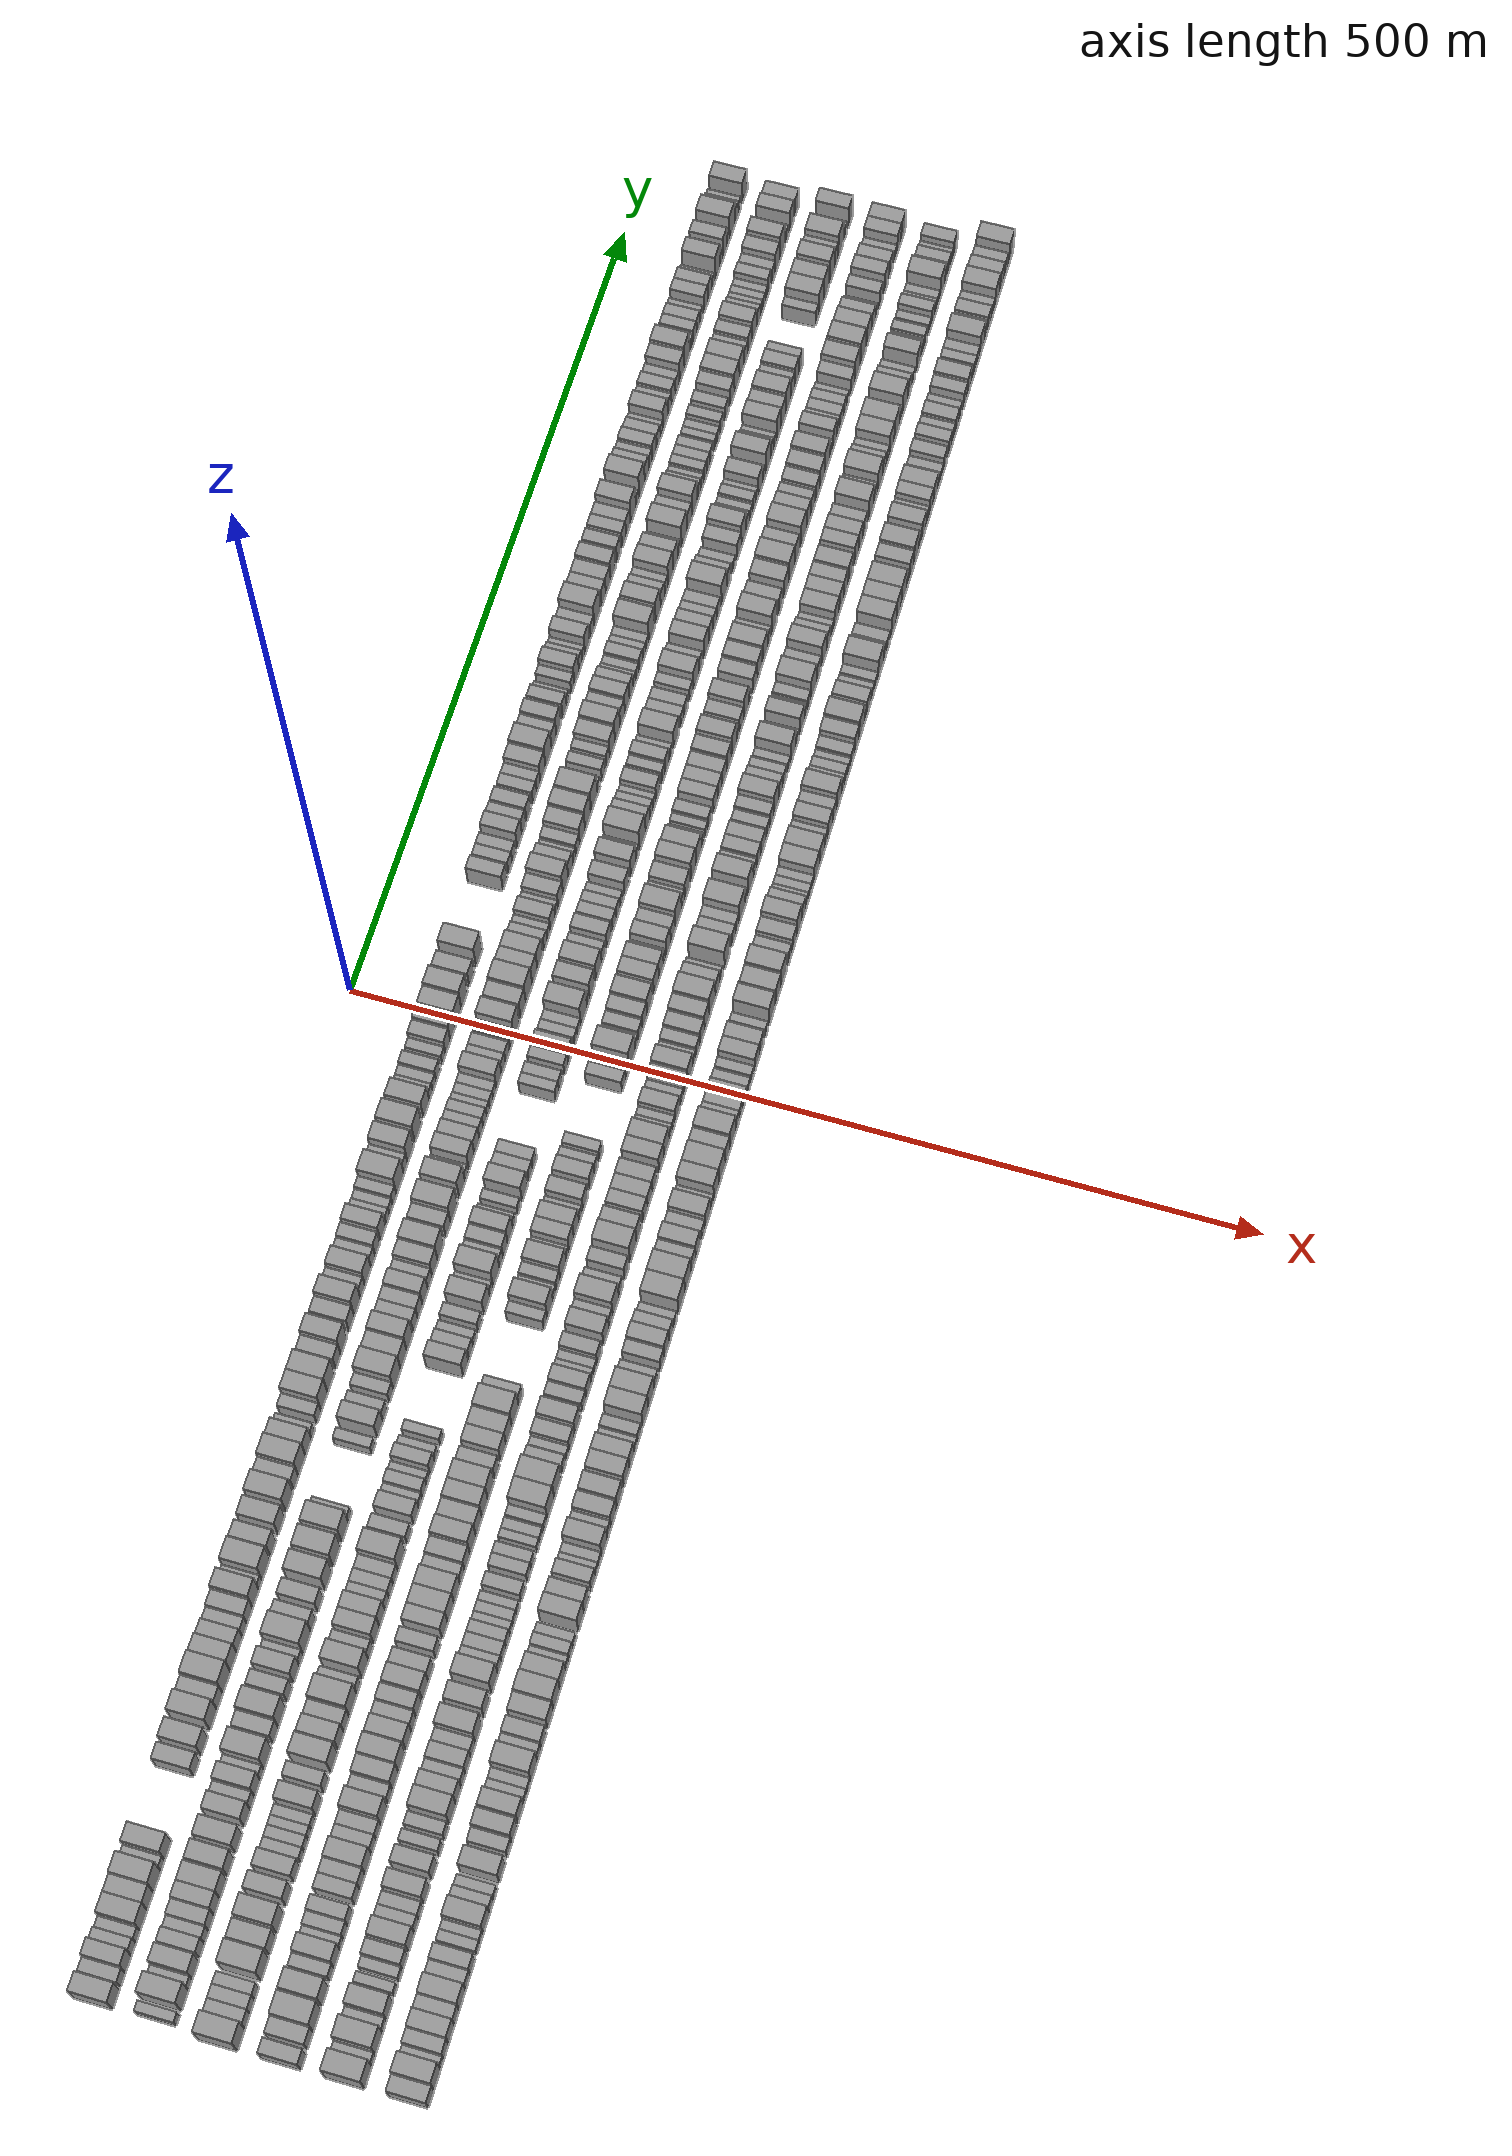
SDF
<sdf version="1.6">
 <world name="default">
  <scene>
   <sky><clouds><speed>12</speed></clouds></sky>
   <ambient>0.4 0.4 0.4 1</ambient>
   <background>0.7 0.7 0.7 1</background>
   <shadows>1</shadows>
  </scene>
  <gravity>0 0 -9.8066</gravity>
  <magnetic_field>6e-06 2.3e-05 -4.2e-05</magnetic_field>
  <physics default="0" name="default_physics" type="ode">
   <ode>
    <solver>
     <type>quick</type>
     <iters>10</iters>
     <sor>1.0</sor>
     <use_dynamic_moi_rescaling>0</use_dynamic_moi_rescaling>
    </solver>
    <constraints>
     <cfm>0</cfm>
     <erp>0.2</erp>
     <contact_max_correcting_vel>100</contact_max_correcting_vel>
     <contact_surface_layer>0.001</contact_surface_layer>
    </constraints>
   </ode>
   <max_step_size>0.004</max_step_size>
   <real_time_factor>1</real_time_factor>
   <real_time_update_rate>250</real_time_update_rate>
  </physics>
  <light name="sun" type="directional">
   <pose>0 0 10 0 0 0</pose>
   <diffuse>0.8 0.8 0.8 1</diffuse>
   <specular>0.2 0.2 0.2 1</specular>
   <attenuation>
    <range>1000</range>
    <constant>0.9</constant>
    <linear>0.01</linear>
    <quadratic>0.001</quadratic>
   </attenuation>
   <direction>-0.5 0.1 -0.9</direction>
  </light>
  <model name="building_1">
   <static>1</static>
   <pose>50.0000 -533.0383 0 0.000000 0.000000 0.000000</pose>
   <link name="link">
    <pose>0 0 10.50 0 0 0</pose>
    <collision name="collision"><geometry><box><size>20.0000 9.9235 21.0000</size></box></geometry></collision>
    <visual name="visual">
     <cast_shadows>0</cast_shadows>
     <geometry><box><size>20.0000 9.9235 21.0000</size></box></geometry>
     <material>
      <script>
       <uri>model://grey_wall/materials/scripts</uri>
       <uri>model://grey_wall/materials/textures</uri>
       <name>vrc/grey_wall</name>
      </script>
     </material>
    </visual>
   </link>
  </model>
  <model name="building_2">
   <static>1</static>
   <pose>50.0000 -523.5318 0 0.000000 0.000000 0.000000</pose>
   <link name="link">
    <pose>0 0 7.50 0 0 0</pose>
    <collision name="collision"><geometry><box><size>20.0000 7.0894 15.0000</size></box></geometry></collision>
    <visual name="visual">
     <cast_shadows>0</cast_shadows>
     <geometry><box><size>20.0000 7.0894 15.0000</size></box></geometry>
     <material>
      <script>
       <uri>model://grey_wall/materials/scripts</uri>
       <uri>model://grey_wall/materials/textures</uri>
       <name>vrc/grey_wall</name>
      </script>
     </material>
    </visual>
   </link>
  </model>
  <model name="building_3">
   <static>1</static>
   <pose>50.0000 -515.7265 0 0.000000 0.000000 0.000000</pose>
   <link name="link">
    <pose>0 0 10.50 0 0 0</pose>
    <collision name="collision"><geometry><box><size>20.0000 8.5213 21.0000</size></box></geometry></collision>
    <visual name="visual">
     <cast_shadows>0</cast_shadows>
     <geometry><box><size>20.0000 8.5213 21.0000</size></box></geometry>
     <material>
      <script>
       <uri>model://grey_wall/materials/scripts</uri>
       <uri>model://grey_wall/materials/textures</uri>
       <name>vrc/grey_wall</name>
      </script>
     </material>
    </visual>
   </link>
  </model>
  <model name="building_4">
   <static>1</static>
   <pose>50.0000 -508.2796 0 0.000000 0.000000 0.000000</pose>
   <link name="link">
    <pose>0 0 7.50 0 0 0</pose>
    <collision name="collision"><geometry><box><size>20.0000 6.3724 15.0000</size></box></geometry></collision>
    <visual name="visual">
     <cast_shadows>0</cast_shadows>
     <geometry><box><size>20.0000 6.3724 15.0000</size></box></geometry>
     <material>
      <script>
       <uri>model://grey_wall/materials/scripts</uri>
       <uri>model://grey_wall/materials/textures</uri>
       <name>vrc/grey_wall</name>
      </script>
     </material>
    </visual>
   </link>
  </model>
  <model name="building_5">
   <static>1</static>
   <pose>50.0000 -502.1047 0 0.000000 0.000000 0.000000</pose>
   <link name="link">
    <pose>0 0 6.00 0 0 0</pose>
    <collision name="collision"><geometry><box><size>20.0000 5.9775 12.0000</size></box></geometry></collision>
    <visual name="visual">
     <cast_shadows>0</cast_shadows>
     <geometry><box><size>20.0000 5.9775 12.0000</size></box></geometry>
     <material>
      <script>
       <uri>model://grey_wall/materials/scripts</uri>
       <uri>model://grey_wall/materials/textures</uri>
       <name>vrc/grey_wall</name>
      </script>
     </material>
    </visual>
   </link>
  </model>
  <model name="building_6">
   <static>1</static>
   <pose>50.0000 -493.9333 0 0.000000 0.000000 0.000000</pose>
   <link name="link">
    <pose>0 0 10.50 0 0 0</pose>
    <collision name="collision"><geometry><box><size>20.0000 10.3654 21.0000</size></box></geometry></collision>
    <visual name="visual">
     <cast_shadows>0</cast_shadows>
     <geometry><box><size>20.0000 10.3654 21.0000</size></box></geometry>
     <material>
      <script>
       <uri>model://grey_wall/materials/scripts</uri>
       <uri>model://grey_wall/materials/textures</uri>
       <name>vrc/grey_wall</name>
      </script>
     </material>
    </visual>
   </link>
  </model>
  <model name="building_7">
   <static>1</static>
   <pose>50.0000 -484.2510 0 0.000000 0.000000 0.000000</pose>
   <link name="link">
    <pose>0 0 10.50 0 0 0</pose>
    <collision name="collision"><geometry><box><size>20.0000 8.9993 21.0000</size></box></geometry></collision>
    <visual name="visual">
     <cast_shadows>0</cast_shadows>
     <geometry><box><size>20.0000 8.9993 21.0000</size></box></geometry>
     <material>
      <script>
       <uri>model://grey_wall/materials/scripts</uri>
       <uri>model://grey_wall/materials/textures</uri>
       <name>vrc/grey_wall</name>
      </script>
     </material>
    </visual>
   </link>
  </model>
  <model name="building_8">
   <static>1</static>
   <pose>50.0000 -474.4659 0 0.000000 0.000000 0.000000</pose>
   <link name="link">
    <pose>0 0 12.00 0 0 0</pose>
    <collision name="collision"><geometry><box><size>20.0000 10.5708 24.0000</size></box></geometry></collision>
    <visual name="visual">
     <cast_shadows>0</cast_shadows>
     <geometry><box><size>20.0000 10.5708 24.0000</size></box></geometry>
     <material>
      <script>
       <uri>model://grey_wall/materials/scripts</uri>
       <uri>model://grey_wall/materials/textures</uri>
       <name>vrc/grey_wall</name>
      </script>
     </material>
    </visual>
   </link>
  </model>
  <model name="building_9">
   <static>1</static>
   <pose>50.0000 -466.4104 0 0.000000 0.000000 0.000000</pose>
   <link name="link">
    <pose>0 0 6.00 0 0 0</pose>
    <collision name="collision"><geometry><box><size>20.0000 5.5403 12.0000</size></box></geometry></collision>
    <visual name="visual">
     <cast_shadows>0</cast_shadows>
     <geometry><box><size>20.0000 5.5403 12.0000</size></box></geometry>
     <material>
      <script>
       <uri>model://grey_wall/materials/scripts</uri>
       <uri>model://grey_wall/materials/textures</uri>
       <name>vrc/grey_wall</name>
      </script>
     </material>
    </visual>
   </link>
  </model>
  <model name="building_10">
   <static>1</static>
   <pose>50.0000 -458.7270 0 0.000000 0.000000 0.000000</pose>
   <link name="link">
    <pose>0 0 10.50 0 0 0</pose>
    <collision name="collision"><geometry><box><size>20.0000 9.8265 21.0000</size></box></geometry></collision>
    <visual name="visual">
     <cast_shadows>0</cast_shadows>
     <geometry><box><size>20.0000 9.8265 21.0000</size></box></geometry>
     <material>
      <script>
       <uri>model://grey_wall/materials/scripts</uri>
       <uri>model://grey_wall/materials/textures</uri>
       <name>vrc/grey_wall</name>
      </script>
     </material>
    </visual>
   </link>
  </model>
  <model name="building_11">
   <static>1</static>
   <pose>50.0000 -416.7494 0 0.000000 0.000000 0.000000</pose>
   <link name="link">
    <pose>0 0 9.00 0 0 0</pose>
    <collision name="collision"><geometry><box><size>20.0000 8.7095 18.0000</size></box></geometry></collision>
    <visual name="visual">
     <cast_shadows>0</cast_shadows>
     <geometry><box><size>20.0000 8.7095 18.0000</size></box></geometry>
     <material>
      <script>
       <uri>model://grey_wall/materials/scripts</uri>
       <uri>model://grey_wall/materials/textures</uri>
       <name>vrc/grey_wall</name>
      </script>
     </material>
    </visual>
   </link>
  </model>
  <model name="building_12">
   <static>1</static>
   <pose>50.0000 -405.3439 0 0.000000 0.000000 0.000000</pose>
   <link name="link">
    <pose>0 0 10.50 0 0 0</pose>
    <collision name="collision"><geometry><box><size>20.0000 10.1016 21.0000</size></box></geometry></collision>
    <visual name="visual">
     <cast_shadows>0</cast_shadows>
     <geometry><box><size>20.0000 10.1016 21.0000</size></box></geometry>
     <material>
      <script>
       <uri>model://grey_wall/materials/scripts</uri>
       <uri>model://grey_wall/materials/textures</uri>
       <name>vrc/grey_wall</name>
      </script>
     </material>
    </visual>
   </link>
  </model>
  <model name="building_13">
   <static>1</static>
   <pose>50.0000 -391.9490 0 0.000000 0.000000 0.000000</pose>
   <link name="link">
    <pose>0 0 12.00 0 0 0</pose>
    <collision name="collision"><geometry><box><size>20.0000 10.6881 24.0000</size></box></geometry></collision>
    <visual name="visual">
     <cast_shadows>0</cast_shadows>
     <geometry><box><size>20.0000 10.6881 24.0000</size></box></geometry>
     <material>
      <script>
       <uri>model://grey_wall/materials/scripts</uri>
       <uri>model://grey_wall/materials/textures</uri>
       <name>vrc/grey_wall</name>
      </script>
     </material>
    </visual>
   </link>
  </model>
  <model name="building_14">
   <static>1</static>
   <pose>50.0000 -382.3258 0 0.000000 0.000000 0.000000</pose>
   <link name="link">
    <pose>0 0 9.00 0 0 0</pose>
    <collision name="collision"><geometry><box><size>20.0000 8.5583 18.0000</size></box></geometry></collision>
    <visual name="visual">
     <cast_shadows>0</cast_shadows>
     <geometry><box><size>20.0000 8.5583 18.0000</size></box></geometry>
     <material>
      <script>
       <uri>model://grey_wall/materials/scripts</uri>
       <uri>model://grey_wall/materials/textures</uri>
       <name>vrc/grey_wall</name>
      </script>
     </material>
    </visual>
   </link>
  </model>
  <model name="building_15">
   <static>1</static>
   <pose>50.0000 -372.2604 0 0.000000 0.000000 0.000000</pose>
   <link name="link">
    <pose>0 0 12.00 0 0 0</pose>
    <collision name="collision"><geometry><box><size>20.0000 11.5725 24.0000</size></box></geometry></collision>
    <visual name="visual">
     <cast_shadows>0</cast_shadows>
     <geometry><box><size>20.0000 11.5725 24.0000</size></box></geometry>
     <material>
      <script>
       <uri>model://grey_wall/materials/scripts</uri>
       <uri>model://grey_wall/materials/textures</uri>
       <name>vrc/grey_wall</name>
      </script>
     </material>
    </visual>
   </link>
  </model>
  <model name="building_16">
   <static>1</static>
   <pose>50.0000 -361.6532 0 0.000000 0.000000 0.000000</pose>
   <link name="link">
    <pose>0 0 10.50 0 0 0</pose>
    <collision name="collision"><geometry><box><size>20.0000 9.6419 21.0000</size></box></geometry></collision>
    <visual name="visual">
     <cast_shadows>0</cast_shadows>
     <geometry><box><size>20.0000 9.6419 21.0000</size></box></geometry>
     <material>
      <script>
       <uri>model://grey_wall/materials/scripts</uri>
       <uri>model://grey_wall/materials/textures</uri>
       <name>vrc/grey_wall</name>
      </script>
     </material>
    </visual>
   </link>
  </model>
  <model name="building_17">
   <static>1</static>
   <pose>50.0000 -352.5997 0 0.000000 0.000000 0.000000</pose>
   <link name="link">
    <pose>0 0 9.00 0 0 0</pose>
    <collision name="collision"><geometry><box><size>20.0000 8.4653 18.0000</size></box></geometry></collision>
    <visual name="visual">
     <cast_shadows>0</cast_shadows>
     <geometry><box><size>20.0000 8.4653 18.0000</size></box></geometry>
     <material>
      <script>
       <uri>model://grey_wall/materials/scripts</uri>
       <uri>model://grey_wall/materials/textures</uri>
       <name>vrc/grey_wall</name>
      </script>
     </material>
    </visual>
   </link>
  </model>
  <model name="building_18">
   <static>1</static>
   <pose>50.0000 -344.9097 0 0.000000 0.000000 0.000000</pose>
   <link name="link">
    <pose>0 0 7.50 0 0 0</pose>
    <collision name="collision"><geometry><box><size>20.0000 6.9146 15.0000</size></box></geometry></collision>
    <visual name="visual">
     <cast_shadows>0</cast_shadows>
     <geometry><box><size>20.0000 6.9146 15.0000</size></box></geometry>
     <material>
      <script>
       <uri>model://grey_wall/materials/scripts</uri>
       <uri>model://grey_wall/materials/textures</uri>
       <name>vrc/grey_wall</name>
      </script>
     </material>
    </visual>
   </link>
  </model>
  <model name="building_19">
   <static>1</static>
   <pose>50.0000 -337.1906 0 0.000000 0.000000 0.000000</pose>
   <link name="link">
    <pose>0 0 9.00 0 0 0</pose>
    <collision name="collision"><geometry><box><size>20.0000 8.5236 18.0000</size></box></geometry></collision>
    <visual name="visual">
     <cast_shadows>0</cast_shadows>
     <geometry><box><size>20.0000 8.5236 18.0000</size></box></geometry>
     <material>
      <script>
       <uri>model://grey_wall/materials/scripts</uri>
       <uri>model://grey_wall/materials/textures</uri>
       <name>vrc/grey_wall</name>
      </script>
     </material>
    </visual>
   </link>
  </model>
  <model name="building_20">
   <static>1</static>
   <pose>50.0000 -328.0993 0 0.000000 0.000000 0.000000</pose>
   <link name="link">
    <pose>0 0 12.00 0 0 0</pose>
    <collision name="collision"><geometry><box><size>20.0000 9.6590 24.0000</size></box></geometry></collision>
    <visual name="visual">
     <cast_shadows>0</cast_shadows>
     <geometry><box><size>20.0000 9.6590 24.0000</size></box></geometry>
     <material>
      <script>
       <uri>model://grey_wall/materials/scripts</uri>
       <uri>model://grey_wall/materials/textures</uri>
       <name>vrc/grey_wall</name>
      </script>
     </material>
    </visual>
   </link>
  </model>
  <model name="building_21">
   <static>1</static>
   <pose>50.0000 -320.8008 0 0.000000 0.000000 0.000000</pose>
   <link name="link">
    <pose>0 0 6.00 0 0 0</pose>
    <collision name="collision"><geometry><box><size>20.0000 4.9381 12.0000</size></box></geometry></collision>
    <visual name="visual">
     <cast_shadows>0</cast_shadows>
     <geometry><box><size>20.0000 4.9381 12.0000</size></box></geometry>
     <material>
      <script>
       <uri>model://grey_wall/materials/scripts</uri>
       <uri>model://grey_wall/materials/textures</uri>
       <name>vrc/grey_wall</name>
      </script>
     </material>
    </visual>
   </link>
  </model>
  <model name="building_22">
   <static>1</static>
   <pose>50.0000 -312.4262 0 0.000000 0.000000 0.000000</pose>
   <link name="link">
    <pose>0 0 12.00 0 0 0</pose>
    <collision name="collision"><geometry><box><size>20.0000 11.8110 24.0000</size></box></geometry></collision>
    <visual name="visual">
     <cast_shadows>0</cast_shadows>
     <geometry><box><size>20.0000 11.8110 24.0000</size></box></geometry>
     <material>
      <script>
       <uri>model://grey_wall/materials/scripts</uri>
       <uri>model://grey_wall/materials/textures</uri>
       <name>vrc/grey_wall</name>
      </script>
     </material>
    </visual>
   </link>
  </model>
  <model name="building_23">
   <static>1</static>
   <pose>50.0000 -301.1140 0 0.000000 0.000000 0.000000</pose>
   <link name="link">
    <pose>0 0 10.50 0 0 0</pose>
    <collision name="collision"><geometry><box><size>20.0000 8.8135 21.0000</size></box></geometry></collision>
    <visual name="visual">
     <cast_shadows>0</cast_shadows>
     <geometry><box><size>20.0000 8.8135 21.0000</size></box></geometry>
     <material>
      <script>
       <uri>model://grey_wall/materials/scripts</uri>
       <uri>model://grey_wall/materials/textures</uri>
       <name>vrc/grey_wall</name>
      </script>
     </material>
    </visual>
   </link>
  </model>
  <model name="building_24">
   <static>1</static>
   <pose>50.0000 -288.6222 0 0.000000 0.000000 0.000000</pose>
   <link name="link">
    <pose>0 0 10.50 0 0 0</pose>
    <collision name="collision"><geometry><box><size>20.0000 10.1701 21.0000</size></box></geometry></collision>
    <visual name="visual">
     <cast_shadows>0</cast_shadows>
     <geometry><box><size>20.0000 10.1701 21.0000</size></box></geometry>
     <material>
      <script>
       <uri>model://grey_wall/materials/scripts</uri>
       <uri>model://grey_wall/materials/textures</uri>
       <name>vrc/grey_wall</name>
      </script>
     </material>
    </visual>
   </link>
  </model>
  <model name="building_25">
   <static>1</static>
   <pose>50.0000 -276.0134 0 0.000000 0.000000 0.000000</pose>
   <link name="link">
    <pose>0 0 12.00 0 0 0</pose>
    <collision name="collision"><geometry><box><size>20.0000 11.0475 24.0000</size></box></geometry></collision>
    <visual name="visual">
     <cast_shadows>0</cast_shadows>
     <geometry><box><size>20.0000 11.0475 24.0000</size></box></geometry>
     <material>
      <script>
       <uri>model://grey_wall/materials/scripts</uri>
       <uri>model://grey_wall/materials/textures</uri>
       <name>vrc/grey_wall</name>
      </script>
     </material>
    </visual>
   </link>
  </model>
  <model name="building_26">
   <static>1</static>
   <pose>50.0000 -265.7554 0 0.000000 0.000000 0.000000</pose>
   <link name="link">
    <pose>0 0 9.00 0 0 0</pose>
    <collision name="collision"><geometry><box><size>20.0000 7.4685 18.0000</size></box></geometry></collision>
    <visual name="visual">
     <cast_shadows>0</cast_shadows>
     <geometry><box><size>20.0000 7.4685 18.0000</size></box></geometry>
     <material>
      <script>
       <uri>model://grey_wall/materials/scripts</uri>
       <uri>model://grey_wall/materials/textures</uri>
       <name>vrc/grey_wall</name>
      </script>
     </material>
    </visual>
   </link>
  </model>
  <model name="building_27">
   <static>1</static>
   <pose>50.0000 -256.4162 0 0.000000 0.000000 0.000000</pose>
   <link name="link">
    <pose>0 0 12.00 0 0 0</pose>
    <collision name="collision"><geometry><box><size>20.0000 11.2099 24.0000</size></box></geometry></collision>
    <visual name="visual">
     <cast_shadows>0</cast_shadows>
     <geometry><box><size>20.0000 11.2099 24.0000</size></box></geometry>
     <material>
      <script>
       <uri>model://grey_wall/materials/scripts</uri>
       <uri>model://grey_wall/materials/textures</uri>
       <name>vrc/grey_wall</name>
      </script>
     </material>
    </visual>
   </link>
  </model>
  <model name="building_28">
   <static>1</static>
   <pose>50.0000 -246.1849 0 0.000000 0.000000 0.000000</pose>
   <link name="link">
    <pose>0 0 10.50 0 0 0</pose>
    <collision name="collision"><geometry><box><size>20.0000 9.2526 21.0000</size></box></geometry></collision>
    <visual name="visual">
     <cast_shadows>0</cast_shadows>
     <geometry><box><size>20.0000 9.2526 21.0000</size></box></geometry>
     <material>
      <script>
       <uri>model://grey_wall/materials/scripts</uri>
       <uri>model://grey_wall/materials/textures</uri>
       <name>vrc/grey_wall</name>
      </script>
     </material>
    </visual>
   </link>
  </model>
  <model name="building_29">
   <static>1</static>
   <pose>50.0000 -238.8304 0 0.000000 0.000000 0.000000</pose>
   <link name="link">
    <pose>0 0 6.00 0 0 0</pose>
    <collision name="collision"><geometry><box><size>20.0000 5.4565 12.0000</size></box></geometry></collision>
    <visual name="visual">
     <cast_shadows>0</cast_shadows>
     <geometry><box><size>20.0000 5.4565 12.0000</size></box></geometry>
     <material>
      <script>
       <uri>model://grey_wall/materials/scripts</uri>
       <uri>model://grey_wall/materials/textures</uri>
       <name>vrc/grey_wall</name>
      </script>
     </material>
    </visual>
   </link>
  </model>
  <model name="building_30">
   <static>1</static>
   <pose>50.0000 -229.6580 0 0.000000 0.000000 0.000000</pose>
   <link name="link">
    <pose>0 0 7.50 0 0 0</pose>
    <collision name="collision"><geometry><box><size>20.0000 6.8882 15.0000</size></box></geometry></collision>
    <visual name="visual">
     <cast_shadows>0</cast_shadows>
     <geometry><box><size>20.0000 6.8882 15.0000</size></box></geometry>
     <material>
      <script>
       <uri>model://grey_wall/materials/scripts</uri>
       <uri>model://grey_wall/materials/textures</uri>
       <name>vrc/grey_wall</name>
      </script>
     </material>
    </visual>
   </link>
  </model>
  <model name="building_31">
   <static>1</static>
   <pose>50.0000 -221.0509 0 0.000000 0.000000 0.000000</pose>
   <link name="link">
    <pose>0 0 12.00 0 0 0</pose>
    <collision name="collision"><geometry><box><size>20.0000 10.3259 24.0000</size></box></geometry></collision>
    <visual name="visual">
     <cast_shadows>0</cast_shadows>
     <geometry><box><size>20.0000 10.3259 24.0000</size></box></geometry>
     <material>
      <script>
       <uri>model://grey_wall/materials/scripts</uri>
       <uri>model://grey_wall/materials/textures</uri>
       <name>vrc/grey_wall</name>
      </script>
     </material>
    </visual>
   </link>
  </model>
  <model name="building_32">
   <static>1</static>
   <pose>50.0000 -210.4008 0 0.000000 0.000000 0.000000</pose>
   <link name="link">
    <pose>0 0 12.00 0 0 0</pose>
    <collision name="collision"><geometry><box><size>20.0000 10.9744 24.0000</size></box></geometry></collision>
    <visual name="visual">
     <cast_shadows>0</cast_shadows>
     <geometry><box><size>20.0000 10.9744 24.0000</size></box></geometry>
     <material>
      <script>
       <uri>model://grey_wall/materials/scripts</uri>
       <uri>model://grey_wall/materials/textures</uri>
       <name>vrc/grey_wall</name>
      </script>
     </material>
    </visual>
   </link>
  </model>
  <model name="building_33">
   <static>1</static>
   <pose>50.0000 -198.8724 0 0.000000 0.000000 0.000000</pose>
   <link name="link">
    <pose>0 0 9.00 0 0 0</pose>
    <collision name="collision"><geometry><box><size>20.0000 8.0824 18.0000</size></box></geometry></collision>
    <visual name="visual">
     <cast_shadows>0</cast_shadows>
     <geometry><box><size>20.0000 8.0824 18.0000</size></box></geometry>
     <material>
      <script>
       <uri>model://grey_wall/materials/scripts</uri>
       <uri>model://grey_wall/materials/textures</uri>
       <name>vrc/grey_wall</name>
      </script>
     </material>
    </visual>
   </link>
  </model>
  <model name="building_34">
   <static>1</static>
   <pose>50.0000 -189.7998 0 0.000000 0.000000 0.000000</pose>
   <link name="link">
    <pose>0 0 12.00 0 0 0</pose>
    <collision name="collision"><geometry><box><size>20.0000 10.0628 24.0000</size></box></geometry></collision>
    <visual name="visual">
     <cast_shadows>0</cast_shadows>
     <geometry><box><size>20.0000 10.0628 24.0000</size></box></geometry>
     <material>
      <script>
       <uri>model://grey_wall/materials/scripts</uri>
       <uri>model://grey_wall/materials/textures</uri>
       <name>vrc/grey_wall</name>
      </script>
     </material>
    </visual>
   </link>
  </model>
  <model name="building_35">
   <static>1</static>
   <pose>50.0000 -177.4073 0 0.000000 0.000000 0.000000</pose>
   <link name="link">
    <pose>0 0 9.00 0 0 0</pose>
    <collision name="collision"><geometry><box><size>20.0000 8.7223 18.0000</size></box></geometry></collision>
    <visual name="visual">
     <cast_shadows>0</cast_shadows>
     <geometry><box><size>20.0000 8.7223 18.0000</size></box></geometry>
     <material>
      <script>
       <uri>model://grey_wall/materials/scripts</uri>
       <uri>model://grey_wall/materials/textures</uri>
       <name>vrc/grey_wall</name>
      </script>
     </material>
    </visual>
   </link>
  </model>
  <model name="building_36">
   <static>1</static>
   <pose>50.0000 -168.0605 0 0.000000 0.000000 0.000000</pose>
   <link name="link">
    <pose>0 0 12.00 0 0 0</pose>
    <collision name="collision"><geometry><box><size>20.0000 9.9712 24.0000</size></box></geometry></collision>
    <visual name="visual">
     <cast_shadows>0</cast_shadows>
     <geometry><box><size>20.0000 9.9712 24.0000</size></box></geometry>
     <material>
      <script>
       <uri>model://grey_wall/materials/scripts</uri>
       <uri>model://grey_wall/materials/textures</uri>
       <name>vrc/grey_wall</name>
      </script>
     </material>
    </visual>
   </link>
  </model>
  <model name="building_37">
   <static>1</static>
   <pose>50.0000 -159.4126 0 0.000000 0.000000 0.000000</pose>
   <link name="link">
    <pose>0 0 7.50 0 0 0</pose>
    <collision name="collision"><geometry><box><size>20.0000 7.3247 15.0000</size></box></geometry></collision>
    <visual name="visual">
     <cast_shadows>0</cast_shadows>
     <geometry><box><size>20.0000 7.3247 15.0000</size></box></geometry>
     <material>
      <script>
       <uri>model://grey_wall/materials/scripts</uri>
       <uri>model://grey_wall/materials/textures</uri>
       <name>vrc/grey_wall</name>
      </script>
     </material>
    </visual>
   </link>
  </model>
  <model name="building_38">
   <static>1</static>
   <pose>50.0000 -150.7110 0 0.000000 0.000000 0.000000</pose>
   <link name="link">
    <pose>0 0 10.50 0 0 0</pose>
    <collision name="collision"><geometry><box><size>20.0000 10.0785 21.0000</size></box></geometry></collision>
    <visual name="visual">
     <cast_shadows>0</cast_shadows>
     <geometry><box><size>20.0000 10.0785 21.0000</size></box></geometry>
     <material>
      <script>
       <uri>model://grey_wall/materials/scripts</uri>
       <uri>model://grey_wall/materials/textures</uri>
       <name>vrc/grey_wall</name>
      </script>
     </material>
    </visual>
   </link>
  </model>
  <model name="building_39">
   <static>1</static>
   <pose>50.0000 -142.2793 0 0.000000 0.000000 0.000000</pose>
   <link name="link">
    <pose>0 0 7.50 0 0 0</pose>
    <collision name="collision"><geometry><box><size>20.0000 6.7848 15.0000</size></box></geometry></collision>
    <visual name="visual">
     <cast_shadows>0</cast_shadows>
     <geometry><box><size>20.0000 6.7848 15.0000</size></box></geometry>
     <material>
      <script>
       <uri>model://grey_wall/materials/scripts</uri>
       <uri>model://grey_wall/materials/textures</uri>
       <name>vrc/grey_wall</name>
      </script>
     </material>
    </visual>
   </link>
  </model>
  <model name="building_40">
   <static>1</static>
   <pose>50.0000 -135.1246 0 0.000000 0.000000 0.000000</pose>
   <link name="link">
    <pose>0 0 9.00 0 0 0</pose>
    <collision name="collision"><geometry><box><size>20.0000 7.5245 18.0000</size></box></geometry></collision>
    <visual name="visual">
     <cast_shadows>0</cast_shadows>
     <geometry><box><size>20.0000 7.5245 18.0000</size></box></geometry>
     <material>
      <script>
       <uri>model://grey_wall/materials/scripts</uri>
       <uri>model://grey_wall/materials/textures</uri>
       <name>vrc/grey_wall</name>
      </script>
     </material>
    </visual>
   </link>
  </model>
  <model name="building_41">
   <static>1</static>
   <pose>50.0000 -126.0490 0 0.000000 0.000000 0.000000</pose>
   <link name="link">
    <pose>0 0 10.50 0 0 0</pose>
    <collision name="collision"><geometry><box><size>20.0000 8.6266 21.0000</size></box></geometry></collision>
    <visual name="visual">
     <cast_shadows>0</cast_shadows>
     <geometry><box><size>20.0000 8.6266 21.0000</size></box></geometry>
     <material>
      <script>
       <uri>model://grey_wall/materials/scripts</uri>
       <uri>model://grey_wall/materials/textures</uri>
       <name>vrc/grey_wall</name>
      </script>
     </material>
    </visual>
   </link>
  </model>
  <model name="building_42">
   <static>1</static>
   <pose>50.0000 -118.0277 0 0.000000 0.000000 0.000000</pose>
   <link name="link">
    <pose>0 0 6.00 0 0 0</pose>
    <collision name="collision"><geometry><box><size>20.0000 5.4161 12.0000</size></box></geometry></collision>
    <visual name="visual">
     <cast_shadows>0</cast_shadows>
     <geometry><box><size>20.0000 5.4161 12.0000</size></box></geometry>
     <material>
      <script>
       <uri>model://grey_wall/materials/scripts</uri>
       <uri>model://grey_wall/materials/textures</uri>
       <name>vrc/grey_wall</name>
      </script>
     </material>
    </visual>
   </link>
  </model>
  <model name="building_43">
   <static>1</static>
   <pose>50.0000 -112.6382 0 0.000000 0.000000 0.000000</pose>
   <link name="link">
    <pose>0 0 6.00 0 0 0</pose>
    <collision name="collision"><geometry><box><size>20.0000 5.3629 12.0000</size></box></geometry></collision>
    <visual name="visual">
     <cast_shadows>0</cast_shadows>
     <geometry><box><size>20.0000 5.3629 12.0000</size></box></geometry>
     <material>
      <script>
       <uri>model://grey_wall/materials/scripts</uri>
       <uri>model://grey_wall/materials/textures</uri>
       <name>vrc/grey_wall</name>
      </script>
     </material>
    </visual>
   </link>
  </model>
  <model name="building_44">
   <static>1</static>
   <pose>50.0000 -106.8026 0 0.000000 0.000000 0.000000</pose>
   <link name="link">
    <pose>0 0 7.50 0 0 0</pose>
    <collision name="collision"><geometry><box><size>20.0000 6.3084 15.0000</size></box></geometry></collision>
    <visual name="visual">
     <cast_shadows>0</cast_shadows>
     <geometry><box><size>20.0000 6.3084 15.0000</size></box></geometry>
     <material>
      <script>
       <uri>model://grey_wall/materials/scripts</uri>
       <uri>model://grey_wall/materials/textures</uri>
       <name>vrc/grey_wall</name>
      </script>
     </material>
    </visual>
   </link>
  </model>
  <model name="building_45">
   <static>1</static>
   <pose>50.0000 -97.6664 0 0.000000 0.000000 0.000000</pose>
   <link name="link">
    <pose>0 0 12.00 0 0 0</pose>
    <collision name="collision"><geometry><box><size>20.0000 11.9639 24.0000</size></box></geometry></collision>
    <visual name="visual">
     <cast_shadows>0</cast_shadows>
     <geometry><box><size>20.0000 11.9639 24.0000</size></box></geometry>
     <material>
      <script>
       <uri>model://grey_wall/materials/scripts</uri>
       <uri>model://grey_wall/materials/textures</uri>
       <name>vrc/grey_wall</name>
      </script>
     </material>
    </visual>
   </link>
  </model>
  <model name="building_46">
   <static>1</static>
   <pose>50.0000 -88.4714 0 0.000000 0.000000 0.000000</pose>
   <link name="link">
    <pose>0 0 7.50 0 0 0</pose>
    <collision name="collision"><geometry><box><size>20.0000 6.4261 15.0000</size></box></geometry></collision>
    <visual name="visual">
     <cast_shadows>0</cast_shadows>
     <geometry><box><size>20.0000 6.4261 15.0000</size></box></geometry>
     <material>
      <script>
       <uri>model://grey_wall/materials/scripts</uri>
       <uri>model://grey_wall/materials/textures</uri>
       <name>vrc/grey_wall</name>
      </script>
     </material>
    </visual>
   </link>
  </model>
  <model name="building_47">
   <static>1</static>
   <pose>50.0000 -80.2179 0 0.000000 0.000000 0.000000</pose>
   <link name="link">
    <pose>0 0 12.00 0 0 0</pose>
    <collision name="collision"><geometry><box><size>20.0000 10.0809 24.0000</size></box></geometry></collision>
    <visual name="visual">
     <cast_shadows>0</cast_shadows>
     <geometry><box><size>20.0000 10.0809 24.0000</size></box></geometry>
     <material>
      <script>
       <uri>model://grey_wall/materials/scripts</uri>
       <uri>model://grey_wall/materials/textures</uri>
       <name>vrc/grey_wall</name>
      </script>
     </material>
    </visual>
   </link>
  </model>
  <model name="building_48">
   <static>1</static>
   <pose>50.0000 -67.5107 0 0.000000 0.000000 0.000000</pose>
   <link name="link">
    <pose>0 0 12.00 0 0 0</pose>
    <collision name="collision"><geometry><box><size>20.0000 11.3334 24.0000</size></box></geometry></collision>
    <visual name="visual">
     <cast_shadows>0</cast_shadows>
     <geometry><box><size>20.0000 11.3334 24.0000</size></box></geometry>
     <material>
      <script>
       <uri>model://grey_wall/materials/scripts</uri>
       <uri>model://grey_wall/materials/textures</uri>
       <name>vrc/grey_wall</name>
      </script>
     </material>
    </visual>
   </link>
  </model>
  <model name="building_49">
   <static>1</static>
   <pose>50.0000 -53.7334 0 0.000000 0.000000 0.000000</pose>
   <link name="link">
    <pose>0 0 10.50 0 0 0</pose>
    <collision name="collision"><geometry><box><size>20.0000 10.2211 21.0000</size></box></geometry></collision>
    <visual name="visual">
     <cast_shadows>0</cast_shadows>
     <geometry><box><size>20.0000 10.2211 21.0000</size></box></geometry>
     <material>
      <script>
       <uri>model://grey_wall/materials/scripts</uri>
       <uri>model://grey_wall/materials/textures</uri>
       <name>vrc/grey_wall</name>
      </script>
     </material>
    </visual>
   </link>
  </model>
  <model name="building_50">
   <static>1</static>
   <pose>50.0000 -45.8077 0 0.000000 0.000000 0.000000</pose>
   <link name="link">
    <pose>0 0 6.00 0 0 0</pose>
    <collision name="collision"><geometry><box><size>20.0000 5.6304 12.0000</size></box></geometry></collision>
    <visual name="visual">
     <cast_shadows>0</cast_shadows>
     <geometry><box><size>20.0000 5.6304 12.0000</size></box></geometry>
     <material>
      <script>
       <uri>model://grey_wall/materials/scripts</uri>
       <uri>model://grey_wall/materials/textures</uri>
       <name>vrc/grey_wall</name>
      </script>
     </material>
    </visual>
   </link>
  </model>
  <model name="building_51">
   <static>1</static>
   <pose>50.0000 -40.0720 0 0.000000 0.000000 0.000000</pose>
   <link name="link">
    <pose>0 0 6.00 0 0 0</pose>
    <collision name="collision"><geometry><box><size>20.0000 5.8410 12.0000</size></box></geometry></collision>
    <visual name="visual">
     <cast_shadows>0</cast_shadows>
     <geometry><box><size>20.0000 5.8410 12.0000</size></box></geometry>
     <material>
      <script>
       <uri>model://grey_wall/materials/scripts</uri>
       <uri>model://grey_wall/materials/textures</uri>
       <name>vrc/grey_wall</name>
      </script>
     </material>
    </visual>
   </link>
  </model>
  <model name="building_52">
   <static>1</static>
   <pose>50.0000 -33.5710 0 0.000000 0.000000 0.000000</pose>
   <link name="link">
    <pose>0 0 7.50 0 0 0</pose>
    <collision name="collision"><geometry><box><size>20.0000 7.1611 15.0000</size></box></geometry></collision>
    <visual name="visual">
     <cast_shadows>0</cast_shadows>
     <geometry><box><size>20.0000 7.1611 15.0000</size></box></geometry>
     <material>
      <script>
       <uri>model://grey_wall/materials/scripts</uri>
       <uri>model://grey_wall/materials/textures</uri>
       <name>vrc/grey_wall</name>
      </script>
     </material>
    </visual>
   </link>
  </model>
  <model name="building_53">
   <static>1</static>
   <pose>50.0000 -24.0598 0 0.000000 0.000000 0.000000</pose>
   <link name="link">
    <pose>0 0 6.00 0 0 0</pose>
    <collision name="collision"><geometry><box><size>20.0000 5.8613 12.0000</size></box></geometry></collision>
    <visual name="visual">
     <cast_shadows>0</cast_shadows>
     <geometry><box><size>20.0000 5.8613 12.0000</size></box></geometry>
     <material>
      <script>
       <uri>model://grey_wall/materials/scripts</uri>
       <uri>model://grey_wall/materials/textures</uri>
       <name>vrc/grey_wall</name>
      </script>
     </material>
    </visual>
   </link>
  </model>
  <model name="building_54">
   <static>1</static>
   <pose>50.0000 -17.0551 0 0.000000 0.000000 0.000000</pose>
   <link name="link">
    <pose>0 0 9.00 0 0 0</pose>
    <collision name="collision"><geometry><box><size>20.0000 8.1479 18.0000</size></box></geometry></collision>
    <visual name="visual">
     <cast_shadows>0</cast_shadows>
     <geometry><box><size>20.0000 8.1479 18.0000</size></box></geometry>
     <material>
      <script>
       <uri>model://grey_wall/materials/scripts</uri>
       <uri>model://grey_wall/materials/textures</uri>
       <name>vrc/grey_wall</name>
      </script>
     </material>
    </visual>
   </link>
  </model>
  <model name="building_55">
   <static>1</static>
   <pose>50.0000 -8.5782 0 0.000000 0.000000 0.000000</pose>
   <link name="link">
    <pose>0 0 10.50 0 0 0</pose>
    <collision name="collision"><geometry><box><size>20.0000 8.8060 21.0000</size></box></geometry></collision>
    <visual name="visual">
     <cast_shadows>0</cast_shadows>
     <geometry><box><size>20.0000 8.8060 21.0000</size></box></geometry>
     <material>
      <script>
       <uri>model://grey_wall/materials/scripts</uri>
       <uri>model://grey_wall/materials/textures</uri>
       <name>vrc/grey_wall</name>
      </script>
     </material>
    </visual>
   </link>
  </model>
  <model name="building_56">
   <static>1</static>
   <pose>50.0000 0.9289 0 0.000000 0.000000 0.000000</pose>
   <link name="link">
    <pose>0 0 10.50 0 0 0</pose>
    <collision name="collision"><geometry><box><size>20.0000 10.2083 21.0000</size></box></geometry></collision>
    <visual name="visual">
     <cast_shadows>0</cast_shadows>
     <geometry><box><size>20.0000 10.2083 21.0000</size></box></geometry>
     <material>
      <script>
       <uri>model://grey_wall/materials/scripts</uri>
       <uri>model://grey_wall/materials/textures</uri>
       <name>vrc/grey_wall</name>
      </script>
     </material>
    </visual>
   </link>
  </model>
  <model name="building_57">
   <static>1</static>
   <pose>50.0000 11.3432 0 0.000000 0.000000 0.000000</pose>
   <link name="link">
    <pose>0 0 12.00 0 0 0</pose>
    <collision name="collision"><geometry><box><size>20.0000 10.6203 24.0000</size></box></geometry></collision>
    <visual name="visual">
     <cast_shadows>0</cast_shadows>
     <geometry><box><size>20.0000 10.6203 24.0000</size></box></geometry>
     <material>
      <script>
       <uri>model://grey_wall/materials/scripts</uri>
       <uri>model://grey_wall/materials/textures</uri>
       <name>vrc/grey_wall</name>
      </script>
     </material>
    </visual>
   </link>
  </model>
  <model name="building_58">
   <static>1</static>
   <pose>50.0000 24.0902 0 0.000000 0.000000 0.000000</pose>
   <link name="link">
    <pose>0 0 9.00 0 0 0</pose>
    <collision name="collision"><geometry><box><size>20.0000 8.8738 18.0000</size></box></geometry></collision>
    <visual name="visual">
     <cast_shadows>0</cast_shadows>
     <geometry><box><size>20.0000 8.8738 18.0000</size></box></geometry>
     <material>
      <script>
       <uri>model://grey_wall/materials/scripts</uri>
       <uri>model://grey_wall/materials/textures</uri>
       <name>vrc/grey_wall</name>
      </script>
     </material>
    </visual>
   </link>
  </model>
  <model name="building_59">
   <static>1</static>
   <pose>50.0000 37.0225 0 0.000000 0.000000 0.000000</pose>
   <link name="link">
    <pose>0 0 12.00 0 0 0</pose>
    <collision name="collision"><geometry><box><size>20.0000 10.9907 24.0000</size></box></geometry></collision>
    <visual name="visual">
     <cast_shadows>0</cast_shadows>
     <geometry><box><size>20.0000 10.9907 24.0000</size></box></geometry>
     <material>
      <script>
       <uri>model://grey_wall/materials/scripts</uri>
       <uri>model://grey_wall/materials/textures</uri>
       <name>vrc/grey_wall</name>
      </script>
     </material>
    </visual>
   </link>
  </model>
  <model name="building_60">
   <static>1</static>
   <pose>50.0000 82.7007 0 0.000000 0.000000 0.000000</pose>
   <link name="link">
    <pose>0 0 9.00 0 0 0</pose>
    <collision name="collision"><geometry><box><size>20.0000 8.1219 18.0000</size></box></geometry></collision>
    <visual name="visual">
     <cast_shadows>0</cast_shadows>
     <geometry><box><size>20.0000 8.1219 18.0000</size></box></geometry>
     <material>
      <script>
       <uri>model://grey_wall/materials/scripts</uri>
       <uri>model://grey_wall/materials/textures</uri>
       <name>vrc/grey_wall</name>
      </script>
     </material>
    </visual>
   </link>
  </model>
  <model name="building_61">
   <static>1</static>
   <pose>50.0000 92.2051 0 0.000000 0.000000 0.000000</pose>
   <link name="link">
    <pose>0 0 7.50 0 0 0</pose>
    <collision name="collision"><geometry><box><size>20.0000 6.8869 15.0000</size></box></geometry></collision>
    <visual name="visual">
     <cast_shadows>0</cast_shadows>
     <geometry><box><size>20.0000 6.8869 15.0000</size></box></geometry>
     <material>
      <script>
       <uri>model://grey_wall/materials/scripts</uri>
       <uri>model://grey_wall/materials/textures</uri>
       <name>vrc/grey_wall</name>
      </script>
     </material>
    </visual>
   </link>
  </model>
  <model name="building_62">
   <static>1</static>
   <pose>50.0000 98.9948 0 0.000000 0.000000 0.000000</pose>
   <link name="link">
    <pose>0 0 7.50 0 0 0</pose>
    <collision name="collision"><geometry><box><size>20.0000 6.6925 15.0000</size></box></geometry></collision>
    <visual name="visual">
     <cast_shadows>0</cast_shadows>
     <geometry><box><size>20.0000 6.6925 15.0000</size></box></geometry>
     <material>
      <script>
       <uri>model://grey_wall/materials/scripts</uri>
       <uri>model://grey_wall/materials/textures</uri>
       <name>vrc/grey_wall</name>
      </script>
     </material>
    </visual>
   </link>
  </model>
  <model name="building_63">
   <static>1</static>
   <pose>50.0000 108.6444 0 0.000000 0.000000 0.000000</pose>
   <link name="link">
    <pose>0 0 10.50 0 0 0</pose>
    <collision name="collision"><geometry><box><size>20.0000 8.6068 21.0000</size></box></geometry></collision>
    <visual name="visual">
     <cast_shadows>0</cast_shadows>
     <geometry><box><size>20.0000 8.6068 21.0000</size></box></geometry>
     <material>
      <script>
       <uri>model://grey_wall/materials/scripts</uri>
       <uri>model://grey_wall/materials/textures</uri>
       <name>vrc/grey_wall</name>
      </script>
     </material>
    </visual>
   </link>
  </model>
  <model name="building_64">
   <static>1</static>
   <pose>50.0000 116.5940 0 0.000000 0.000000 0.000000</pose>
   <link name="link">
    <pose>0 0 9.00 0 0 0</pose>
    <collision name="collision"><geometry><box><size>20.0000 7.2923 18.0000</size></box></geometry></collision>
    <visual name="visual">
     <cast_shadows>0</cast_shadows>
     <geometry><box><size>20.0000 7.2923 18.0000</size></box></geometry>
     <material>
      <script>
       <uri>model://grey_wall/materials/scripts</uri>
       <uri>model://grey_wall/materials/textures</uri>
       <name>vrc/grey_wall</name>
      </script>
     </material>
    </visual>
   </link>
  </model>
  <model name="building_65">
   <static>1</static>
   <pose>50.0000 125.4271 0 0.000000 0.000000 0.000000</pose>
   <link name="link">
    <pose>0 0 9.00 0 0 0</pose>
    <collision name="collision"><geometry><box><size>20.0000 8.3741 18.0000</size></box></geometry></collision>
    <visual name="visual">
     <cast_shadows>0</cast_shadows>
     <geometry><box><size>20.0000 8.3741 18.0000</size></box></geometry>
     <material>
      <script>
       <uri>model://grey_wall/materials/scripts</uri>
       <uri>model://grey_wall/materials/textures</uri>
       <name>vrc/grey_wall</name>
      </script>
     </material>
    </visual>
   </link>
  </model>
  <model name="building_66">
   <static>1</static>
   <pose>50.0000 136.1511 0 0.000000 0.000000 0.000000</pose>
   <link name="link">
    <pose>0 0 7.50 0 0 0</pose>
    <collision name="collision"><geometry><box><size>20.0000 7.0738 15.0000</size></box></geometry></collision>
    <visual name="visual">
     <cast_shadows>0</cast_shadows>
     <geometry><box><size>20.0000 7.0738 15.0000</size></box></geometry>
     <material>
      <script>
       <uri>model://grey_wall/materials/scripts</uri>
       <uri>model://grey_wall/materials/textures</uri>
       <name>vrc/grey_wall</name>
      </script>
     </material>
    </visual>
   </link>
  </model>
  <model name="building_67">
   <static>1</static>
   <pose>50.0000 142.8592 0 0.000000 0.000000 0.000000</pose>
   <link name="link">
    <pose>0 0 7.50 0 0 0</pose>
    <collision name="collision"><geometry><box><size>20.0000 6.3424 15.0000</size></box></geometry></collision>
    <visual name="visual">
     <cast_shadows>0</cast_shadows>
     <geometry><box><size>20.0000 6.3424 15.0000</size></box></geometry>
     <material>
      <script>
       <uri>model://grey_wall/materials/scripts</uri>
       <uri>model://grey_wall/materials/textures</uri>
       <name>vrc/grey_wall</name>
      </script>
     </material>
    </visual>
   </link>
  </model>
  <model name="building_68">
   <static>1</static>
   <pose>50.0000 150.7585 0 0.000000 0.000000 0.000000</pose>
   <link name="link">
    <pose>0 0 10.50 0 0 0</pose>
    <collision name="collision"><geometry><box><size>20.0000 9.4562 21.0000</size></box></geometry></collision>
    <visual name="visual">
     <cast_shadows>0</cast_shadows>
     <geometry><box><size>20.0000 9.4562 21.0000</size></box></geometry>
     <material>
      <script>
       <uri>model://grey_wall/materials/scripts</uri>
       <uri>model://grey_wall/materials/textures</uri>
       <name>vrc/grey_wall</name>
      </script>
     </material>
    </visual>
   </link>
  </model>
  <model name="building_69">
   <static>1</static>
   <pose>50.0000 161.1439 0 0.000000 0.000000 0.000000</pose>
   <link name="link">
    <pose>0 0 12.00 0 0 0</pose>
    <collision name="collision"><geometry><box><size>20.0000 11.3147 24.0000</size></box></geometry></collision>
    <visual name="visual">
     <cast_shadows>0</cast_shadows>
     <geometry><box><size>20.0000 11.3147 24.0000</size></box></geometry>
     <material>
      <script>
       <uri>model://grey_wall/materials/scripts</uri>
       <uri>model://grey_wall/materials/textures</uri>
       <name>vrc/grey_wall</name>
      </script>
     </material>
    </visual>
   </link>
  </model>
  <model name="building_70">
   <static>1</static>
   <pose>50.0000 171.1383 0 0.000000 0.000000 0.000000</pose>
   <link name="link">
    <pose>0 0 9.00 0 0 0</pose>
    <collision name="collision"><geometry><box><size>20.0000 8.6740 18.0000</size></box></geometry></collision>
    <visual name="visual">
     <cast_shadows>0</cast_shadows>
     <geometry><box><size>20.0000 8.6740 18.0000</size></box></geometry>
     <material>
      <script>
       <uri>model://grey_wall/materials/scripts</uri>
       <uri>model://grey_wall/materials/textures</uri>
       <name>vrc/grey_wall</name>
      </script>
     </material>
    </visual>
   </link>
  </model>
  <model name="building_71">
   <static>1</static>
   <pose>50.0000 179.7037 0 0.000000 0.000000 0.000000</pose>
   <link name="link">
    <pose>0 0 10.50 0 0 0</pose>
    <collision name="collision"><geometry><box><size>20.0000 8.4568 21.0000</size></box></geometry></collision>
    <visual name="visual">
     <cast_shadows>0</cast_shadows>
     <geometry><box><size>20.0000 8.4568 21.0000</size></box></geometry>
     <material>
      <script>
       <uri>model://grey_wall/materials/scripts</uri>
       <uri>model://grey_wall/materials/textures</uri>
       <name>vrc/grey_wall</name>
      </script>
     </material>
    </visual>
   </link>
  </model>
  <model name="building_72">
   <static>1</static>
   <pose>50.0000 190.6628 0 0.000000 0.000000 0.000000</pose>
   <link name="link">
    <pose>0 0 9.00 0 0 0</pose>
    <collision name="collision"><geometry><box><size>20.0000 7.4614 18.0000</size></box></geometry></collision>
    <visual name="visual">
     <cast_shadows>0</cast_shadows>
     <geometry><box><size>20.0000 7.4614 18.0000</size></box></geometry>
     <material>
      <script>
       <uri>model://grey_wall/materials/scripts</uri>
       <uri>model://grey_wall/materials/textures</uri>
       <name>vrc/grey_wall</name>
      </script>
     </material>
    </visual>
   </link>
  </model>
  <model name="building_73">
   <static>1</static>
   <pose>50.0000 197.0272 0 0.000000 0.000000 0.000000</pose>
   <link name="link">
    <pose>0 0 6.00 0 0 0</pose>
    <collision name="collision"><geometry><box><size>20.0000 5.2672 12.0000</size></box></geometry></collision>
    <visual name="visual">
     <cast_shadows>0</cast_shadows>
     <geometry><box><size>20.0000 5.2672 12.0000</size></box></geometry>
     <material>
      <script>
       <uri>model://grey_wall/materials/scripts</uri>
       <uri>model://grey_wall/materials/textures</uri>
       <name>vrc/grey_wall</name>
      </script>
     </material>
    </visual>
   </link>
  </model>
  <model name="building_74">
   <static>1</static>
   <pose>50.0000 205.6999 0 0.000000 0.000000 0.000000</pose>
   <link name="link">
    <pose>0 0 7.50 0 0 0</pose>
    <collision name="collision"><geometry><box><size>20.0000 6.0783 15.0000</size></box></geometry></collision>
    <visual name="visual">
     <cast_shadows>0</cast_shadows>
     <geometry><box><size>20.0000 6.0783 15.0000</size></box></geometry>
     <material>
      <script>
       <uri>model://grey_wall/materials/scripts</uri>
       <uri>model://grey_wall/materials/textures</uri>
       <name>vrc/grey_wall</name>
      </script>
     </material>
    </visual>
   </link>
  </model>
  <model name="building_75">
   <static>1</static>
   <pose>50.0000 212.9426 0 0.000000 0.000000 0.000000</pose>
   <link name="link">
    <pose>0 0 10.50 0 0 0</pose>
    <collision name="collision"><geometry><box><size>20.0000 8.4072 21.0000</size></box></geometry></collision>
    <visual name="visual">
     <cast_shadows>0</cast_shadows>
     <geometry><box><size>20.0000 8.4072 21.0000</size></box></geometry>
     <material>
      <script>
       <uri>model://grey_wall/materials/scripts</uri>
       <uri>model://grey_wall/materials/textures</uri>
       <name>vrc/grey_wall</name>
      </script>
     </material>
    </visual>
   </link>
  </model>
  <model name="building_76">
   <static>1</static>
   <pose>50.0000 220.3035 0 0.000000 0.000000 0.000000</pose>
   <link name="link">
    <pose>0 0 7.50 0 0 0</pose>
    <collision name="collision"><geometry><box><size>20.0000 6.3146 15.0000</size></box></geometry></collision>
    <visual name="visual">
     <cast_shadows>0</cast_shadows>
     <geometry><box><size>20.0000 6.3146 15.0000</size></box></geometry>
     <material>
      <script>
       <uri>model://grey_wall/materials/scripts</uri>
       <uri>model://grey_wall/materials/textures</uri>
       <name>vrc/grey_wall</name>
      </script>
     </material>
    </visual>
   </link>
  </model>
  <model name="building_77">
   <static>1</static>
   <pose>50.0000 225.8746 0 0.000000 0.000000 0.000000</pose>
   <link name="link">
    <pose>0 0 6.00 0 0 0</pose>
    <collision name="collision"><geometry><box><size>20.0000 4.8276 12.0000</size></box></geometry></collision>
    <visual name="visual">
     <cast_shadows>0</cast_shadows>
     <geometry><box><size>20.0000 4.8276 12.0000</size></box></geometry>
     <material>
      <script>
       <uri>model://grey_wall/materials/scripts</uri>
       <uri>model://grey_wall/materials/textures</uri>
       <name>vrc/grey_wall</name>
      </script>
     </material>
    </visual>
   </link>
  </model>
  <model name="building_78">
   <static>1</static>
   <pose>50.0000 232.6043 0 0.000000 0.000000 0.000000</pose>
   <link name="link">
    <pose>0 0 10.50 0 0 0</pose>
    <collision name="collision"><geometry><box><size>20.0000 8.6318 21.0000</size></box></geometry></collision>
    <visual name="visual">
     <cast_shadows>0</cast_shadows>
     <geometry><box><size>20.0000 8.6318 21.0000</size></box></geometry>
     <material>
      <script>
       <uri>model://grey_wall/materials/scripts</uri>
       <uri>model://grey_wall/materials/textures</uri>
       <name>vrc/grey_wall</name>
      </script>
     </material>
    </visual>
   </link>
  </model>
  <model name="building_79">
   <static>1</static>
   <pose>50.0000 242.5200 0 0.000000 0.000000 0.000000</pose>
   <link name="link">
    <pose>0 0 7.50 0 0 0</pose>
    <collision name="collision"><geometry><box><size>20.0000 7.1996 15.0000</size></box></geometry></collision>
    <visual name="visual">
     <cast_shadows>0</cast_shadows>
     <geometry><box><size>20.0000 7.1996 15.0000</size></box></geometry>
     <material>
      <script>
       <uri>model://grey_wall/materials/scripts</uri>
       <uri>model://grey_wall/materials/textures</uri>
       <name>vrc/grey_wall</name>
      </script>
     </material>
    </visual>
   </link>
  </model>
  <model name="building_80">
   <static>1</static>
   <pose>50.0000 251.8541 0 0.000000 0.000000 0.000000</pose>
   <link name="link">
    <pose>0 0 12.00 0 0 0</pose>
    <collision name="collision"><geometry><box><size>20.0000 11.4685 24.0000</size></box></geometry></collision>
    <visual name="visual">
     <cast_shadows>0</cast_shadows>
     <geometry><box><size>20.0000 11.4685 24.0000</size></box></geometry>
     <material>
      <script>
       <uri>model://grey_wall/materials/scripts</uri>
       <uri>model://grey_wall/materials/textures</uri>
       <name>vrc/grey_wall</name>
      </script>
     </material>
    </visual>
   </link>
  </model>
  <model name="building_81">
   <static>1</static>
   <pose>50.0000 263.6289 0 0.000000 0.000000 0.000000</pose>
   <link name="link">
    <pose>0 0 9.00 0 0 0</pose>
    <collision name="collision"><geometry><box><size>20.0000 8.0811 18.0000</size></box></geometry></collision>
    <visual name="visual">
     <cast_shadows>0</cast_shadows>
     <geometry><box><size>20.0000 8.0811 18.0000</size></box></geometry>
     <material>
      <script>
       <uri>model://grey_wall/materials/scripts</uri>
       <uri>model://grey_wall/materials/textures</uri>
       <name>vrc/grey_wall</name>
      </script>
     </material>
    </visual>
   </link>
  </model>
  <model name="building_82">
   <static>1</static>
   <pose>50.0000 272.1463 0 0.000000 0.000000 0.000000</pose>
   <link name="link">
    <pose>0 0 9.00 0 0 0</pose>
    <collision name="collision"><geometry><box><size>20.0000 8.9538 18.0000</size></box></geometry></collision>
    <visual name="visual">
     <cast_shadows>0</cast_shadows>
     <geometry><box><size>20.0000 8.9538 18.0000</size></box></geometry>
     <material>
      <script>
       <uri>model://grey_wall/materials/scripts</uri>
       <uri>model://grey_wall/materials/textures</uri>
       <name>vrc/grey_wall</name>
      </script>
     </material>
    </visual>
   </link>
  </model>
  <model name="building_83">
   <static>1</static>
   <pose>50.0000 281.1949 0 0.000000 0.000000 0.000000</pose>
   <link name="link">
    <pose>0 0 10.50 0 0 0</pose>
    <collision name="collision"><geometry><box><size>20.0000 9.1433 21.0000</size></box></geometry></collision>
    <visual name="visual">
     <cast_shadows>0</cast_shadows>
     <geometry><box><size>20.0000 9.1433 21.0000</size></box></geometry>
     <material>
      <script>
       <uri>model://grey_wall/materials/scripts</uri>
       <uri>model://grey_wall/materials/textures</uri>
       <name>vrc/grey_wall</name>
      </script>
     </material>
    </visual>
   </link>
  </model>
  <model name="building_84">
   <static>1</static>
   <pose>50.0000 292.6517 0 0.000000 0.000000 0.000000</pose>
   <link name="link">
    <pose>0 0 9.00 0 0 0</pose>
    <collision name="collision"><geometry><box><size>20.0000 7.7703 18.0000</size></box></geometry></collision>
    <visual name="visual">
     <cast_shadows>0</cast_shadows>
     <geometry><box><size>20.0000 7.7703 18.0000</size></box></geometry>
     <material>
      <script>
       <uri>model://grey_wall/materials/scripts</uri>
       <uri>model://grey_wall/materials/textures</uri>
       <name>vrc/grey_wall</name>
      </script>
     </material>
    </visual>
   </link>
  </model>
  <model name="building_85">
   <static>1</static>
   <pose>50.0000 302.3955 0 0.000000 0.000000 0.000000</pose>
   <link name="link">
    <pose>0 0 9.00 0 0 0</pose>
    <collision name="collision"><geometry><box><size>20.0000 7.7174 18.0000</size></box></geometry></collision>
    <visual name="visual">
     <cast_shadows>0</cast_shadows>
     <geometry><box><size>20.0000 7.7174 18.0000</size></box></geometry>
     <material>
      <script>
       <uri>model://grey_wall/materials/scripts</uri>
       <uri>model://grey_wall/materials/textures</uri>
       <name>vrc/grey_wall</name>
      </script>
     </material>
    </visual>
   </link>
  </model>
  <model name="building_86">
   <static>1</static>
   <pose>50.0000 310.1619 0 0.000000 0.000000 0.000000</pose>
   <link name="link">
    <pose>0 0 9.00 0 0 0</pose>
    <collision name="collision"><geometry><box><size>20.0000 7.8153 18.0000</size></box></geometry></collision>
    <visual name="visual">
     <cast_shadows>0</cast_shadows>
     <geometry><box><size>20.0000 7.8153 18.0000</size></box></geometry>
     <material>
      <script>
       <uri>model://grey_wall/materials/scripts</uri>
       <uri>model://grey_wall/materials/textures</uri>
       <name>vrc/grey_wall</name>
      </script>
     </material>
    </visual>
   </link>
  </model>
  <model name="building_87">
   <static>1</static>
   <pose>50.0000 320.1657 0 0.000000 0.000000 0.000000</pose>
   <link name="link">
    <pose>0 0 12.00 0 0 0</pose>
    <collision name="collision"><geometry><box><size>20.0000 10.1923 24.0000</size></box></geometry></collision>
    <visual name="visual">
     <cast_shadows>0</cast_shadows>
     <geometry><box><size>20.0000 10.1923 24.0000</size></box></geometry>
     <material>
      <script>
       <uri>model://grey_wall/materials/scripts</uri>
       <uri>model://grey_wall/materials/textures</uri>
       <name>vrc/grey_wall</name>
      </script>
     </material>
    </visual>
   </link>
  </model>
  <model name="building_88">
   <static>1</static>
   <pose>50.0000 328.0957 0 0.000000 0.000000 0.000000</pose>
   <link name="link">
    <pose>0 0 6.00 0 0 0</pose>
    <collision name="collision"><geometry><box><size>20.0000 5.6677 12.0000</size></box></geometry></collision>
    <visual name="visual">
     <cast_shadows>0</cast_shadows>
     <geometry><box><size>20.0000 5.6677 12.0000</size></box></geometry>
     <material>
      <script>
       <uri>model://grey_wall/materials/scripts</uri>
       <uri>model://grey_wall/materials/textures</uri>
       <name>vrc/grey_wall</name>
      </script>
     </material>
    </visual>
   </link>
  </model>
  <model name="building_89">
   <static>1</static>
   <pose>50.0000 337.1441 0 0.000000 0.000000 0.000000</pose>
   <link name="link">
    <pose>0 0 12.00 0 0 0</pose>
    <collision name="collision"><geometry><box><size>20.0000 10.4292 24.0000</size></box></geometry></collision>
    <visual name="visual">
     <cast_shadows>0</cast_shadows>
     <geometry><box><size>20.0000 10.4292 24.0000</size></box></geometry>
     <material>
      <script>
       <uri>model://grey_wall/materials/scripts</uri>
       <uri>model://grey_wall/materials/textures</uri>
       <name>vrc/grey_wall</name>
      </script>
     </material>
    </visual>
   </link>
  </model>
  <model name="building_90">
   <static>1</static>
   <pose>50.0000 346.4483 0 0.000000 0.000000 0.000000</pose>
   <link name="link">
    <pose>0 0 9.00 0 0 0</pose>
    <collision name="collision"><geometry><box><size>20.0000 8.1792 18.0000</size></box></geometry></collision>
    <visual name="visual">
     <cast_shadows>0</cast_shadows>
     <geometry><box><size>20.0000 8.1792 18.0000</size></box></geometry>
     <material>
      <script>
       <uri>model://grey_wall/materials/scripts</uri>
       <uri>model://grey_wall/materials/textures</uri>
       <name>vrc/grey_wall</name>
      </script>
     </material>
    </visual>
   </link>
  </model>
  <model name="building_91">
   <static>1</static>
   <pose>50.0000 353.7479 0 0.000000 0.000000 0.000000</pose>
   <link name="link">
    <pose>0 0 7.50 0 0 0</pose>
    <collision name="collision"><geometry><box><size>20.0000 6.4199 15.0000</size></box></geometry></collision>
    <visual name="visual">
     <cast_shadows>0</cast_shadows>
     <geometry><box><size>20.0000 6.4199 15.0000</size></box></geometry>
     <material>
      <script>
       <uri>model://grey_wall/materials/scripts</uri>
       <uri>model://grey_wall/materials/textures</uri>
       <name>vrc/grey_wall</name>
      </script>
     </material>
    </visual>
   </link>
  </model>
  <model name="building_92">
   <static>1</static>
   <pose>50.0000 360.8791 0 0.000000 0.000000 0.000000</pose>
   <link name="link">
    <pose>0 0 9.00 0 0 0</pose>
    <collision name="collision"><geometry><box><size>20.0000 7.8426 18.0000</size></box></geometry></collision>
    <visual name="visual">
     <cast_shadows>0</cast_shadows>
     <geometry><box><size>20.0000 7.8426 18.0000</size></box></geometry>
     <material>
      <script>
       <uri>model://grey_wall/materials/scripts</uri>
       <uri>model://grey_wall/materials/textures</uri>
       <name>vrc/grey_wall</name>
      </script>
     </material>
    </visual>
   </link>
  </model>
  <model name="building_93">
   <static>1</static>
   <pose>50.0000 369.5447 0 0.000000 0.000000 0.000000</pose>
   <link name="link">
    <pose>0 0 7.50 0 0 0</pose>
    <collision name="collision"><geometry><box><size>20.0000 7.4886 15.0000</size></box></geometry></collision>
    <visual name="visual">
     <cast_shadows>0</cast_shadows>
     <geometry><box><size>20.0000 7.4886 15.0000</size></box></geometry>
     <material>
      <script>
       <uri>model://grey_wall/materials/scripts</uri>
       <uri>model://grey_wall/materials/textures</uri>
       <name>vrc/grey_wall</name>
      </script>
     </material>
    </visual>
   </link>
  </model>
  <model name="building_94">
   <static>1</static>
   <pose>50.0000 375.7590 0 0.000000 0.000000 0.000000</pose>
   <link name="link">
    <pose>0 0 6.00 0 0 0</pose>
    <collision name="collision"><geometry><box><size>20.0000 4.9399 12.0000</size></box></geometry></collision>
    <visual name="visual">
     <cast_shadows>0</cast_shadows>
     <geometry><box><size>20.0000 4.9399 12.0000</size></box></geometry>
     <material>
      <script>
       <uri>model://grey_wall/materials/scripts</uri>
       <uri>model://grey_wall/materials/textures</uri>
       <name>vrc/grey_wall</name>
      </script>
     </material>
    </visual>
   </link>
  </model>
  <model name="building_95">
   <static>1</static>
   <pose>50.0000 382.8818 0 0.000000 0.000000 0.000000</pose>
   <link name="link">
    <pose>0 0 10.50 0 0 0</pose>
    <collision name="collision"><geometry><box><size>20.0000 9.3056 21.0000</size></box></geometry></collision>
    <visual name="visual">
     <cast_shadows>0</cast_shadows>
     <geometry><box><size>20.0000 9.3056 21.0000</size></box></geometry>
     <material>
      <script>
       <uri>model://grey_wall/materials/scripts</uri>
       <uri>model://grey_wall/materials/textures</uri>
       <name>vrc/grey_wall</name>
      </script>
     </material>
    </visual>
   </link>
  </model>
  <model name="building_96">
   <static>1</static>
   <pose>50.0000 391.6769 0 0.000000 0.000000 0.000000</pose>
   <link name="link">
    <pose>0 0 7.50 0 0 0</pose>
    <collision name="collision"><geometry><box><size>20.0000 6.2844 15.0000</size></box></geometry></collision>
    <visual name="visual">
     <cast_shadows>0</cast_shadows>
     <geometry><box><size>20.0000 6.2844 15.0000</size></box></geometry>
     <material>
      <script>
       <uri>model://grey_wall/materials/scripts</uri>
       <uri>model://grey_wall/materials/textures</uri>
       <name>vrc/grey_wall</name>
      </script>
     </material>
    </visual>
   </link>
  </model>
  <model name="building_97">
   <static>1</static>
   <pose>50.0000 398.7208 0 0.000000 0.000000 0.000000</pose>
   <link name="link">
    <pose>0 0 9.00 0 0 0</pose>
    <collision name="collision"><geometry><box><size>20.0000 7.8034 18.0000</size></box></geometry></collision>
    <visual name="visual">
     <cast_shadows>0</cast_shadows>
     <geometry><box><size>20.0000 7.8034 18.0000</size></box></geometry>
     <material>
      <script>
       <uri>model://grey_wall/materials/scripts</uri>
       <uri>model://grey_wall/materials/textures</uri>
       <name>vrc/grey_wall</name>
      </script>
     </material>
    </visual>
   </link>
  </model>
  <model name="building_98">
   <static>1</static>
   <pose>50.0000 406.3386 0 0.000000 0.000000 0.000000</pose>
   <link name="link">
    <pose>0 0 7.50 0 0 0</pose>
    <collision name="collision"><geometry><box><size>20.0000 7.4322 15.0000</size></box></geometry></collision>
    <visual name="visual">
     <cast_shadows>0</cast_shadows>
     <geometry><box><size>20.0000 7.4322 15.0000</size></box></geometry>
     <material>
      <script>
       <uri>model://grey_wall/materials/scripts</uri>
       <uri>model://grey_wall/materials/textures</uri>
       <name>vrc/grey_wall</name>
      </script>
     </material>
    </visual>
   </link>
  </model>
  <model name="building_99">
   <static>1</static>
   <pose>50.0000 415.7188 0 0.000000 0.000000 0.000000</pose>
   <link name="link">
    <pose>0 0 10.50 0 0 0</pose>
    <collision name="collision"><geometry><box><size>20.0000 9.3282 21.0000</size></box></geometry></collision>
    <visual name="visual">
     <cast_shadows>0</cast_shadows>
     <geometry><box><size>20.0000 9.3282 21.0000</size></box></geometry>
     <material>
      <script>
       <uri>model://grey_wall/materials/scripts</uri>
       <uri>model://grey_wall/materials/textures</uri>
       <name>vrc/grey_wall</name>
      </script>
     </material>
    </visual>
   </link>
  </model>
  <model name="building_100">
   <static>1</static>
   <pose>50.0000 425.6971 0 0.000000 0.000000 0.000000</pose>
   <link name="link">
    <pose>0 0 12.00 0 0 0</pose>
    <collision name="collision"><geometry><box><size>20.0000 10.6284 24.0000</size></box></geometry></collision>
    <visual name="visual">
     <cast_shadows>0</cast_shadows>
     <geometry><box><size>20.0000 10.6284 24.0000</size></box></geometry>
     <material>
      <script>
       <uri>model://grey_wall/materials/scripts</uri>
       <uri>model://grey_wall/materials/textures</uri>
       <name>vrc/grey_wall</name>
      </script>
     </material>
    </visual>
   </link>
  </model>
  <model name="building_101">
   <static>1</static>
   <pose>50.0000 435.4824 0 0.000000 0.000000 0.000000</pose>
   <link name="link">
    <pose>0 0 6.00 0 0 0</pose>
    <collision name="collision"><geometry><box><size>20.0000 4.9421 12.0000</size></box></geometry></collision>
    <visual name="visual">
     <cast_shadows>0</cast_shadows>
     <geometry><box><size>20.0000 4.9421 12.0000</size></box></geometry>
     <material>
      <script>
       <uri>model://grey_wall/materials/scripts</uri>
       <uri>model://grey_wall/materials/textures</uri>
       <name>vrc/grey_wall</name>
      </script>
     </material>
    </visual>
   </link>
  </model>
  <model name="building_102">
   <static>1</static>
   <pose>50.0000 441.4241 0 0.000000 0.000000 0.000000</pose>
   <link name="link">
    <pose>0 0 7.50 0 0 0</pose>
    <collision name="collision"><geometry><box><size>20.0000 6.9413 15.0000</size></box></geometry></collision>
    <visual name="visual">
     <cast_shadows>0</cast_shadows>
     <geometry><box><size>20.0000 6.9413 15.0000</size></box></geometry>
     <material>
      <script>
       <uri>model://grey_wall/materials/scripts</uri>
       <uri>model://grey_wall/materials/textures</uri>
       <name>vrc/grey_wall</name>
      </script>
     </material>
    </visual>
   </link>
  </model>
  <model name="building_103">
   <static>1</static>
   <pose>50.0000 448.5748 0 0.000000 0.000000 0.000000</pose>
   <link name="link">
    <pose>0 0 7.50 0 0 0</pose>
    <collision name="collision"><geometry><box><size>20.0000 7.3600 15.0000</size></box></geometry></collision>
    <visual name="visual">
     <cast_shadows>0</cast_shadows>
     <geometry><box><size>20.0000 7.3600 15.0000</size></box></geometry>
     <material>
      <script>
       <uri>model://grey_wall/materials/scripts</uri>
       <uri>model://grey_wall/materials/textures</uri>
       <name>vrc/grey_wall</name>
      </script>
     </material>
    </visual>
   </link>
  </model>
  <model name="building_104">
   <static>1</static>
   <pose>50.0000 454.9493 0 0.000000 0.000000 0.000000</pose>
   <link name="link">
    <pose>0 0 6.00 0 0 0</pose>
    <collision name="collision"><geometry><box><size>20.0000 5.3890 12.0000</size></box></geometry></collision>
    <visual name="visual">
     <cast_shadows>0</cast_shadows>
     <geometry><box><size>20.0000 5.3890 12.0000</size></box></geometry>
     <material>
      <script>
       <uri>model://grey_wall/materials/scripts</uri>
       <uri>model://grey_wall/materials/textures</uri>
       <name>vrc/grey_wall</name>
      </script>
     </material>
    </visual>
   </link>
  </model>
  <model name="building_105">
   <static>1</static>
   <pose>50.0000 463.7179 0 0.000000 0.000000 0.000000</pose>
   <link name="link">
    <pose>0 0 9.00 0 0 0</pose>
    <collision name="collision"><geometry><box><size>20.0000 8.1482 18.0000</size></box></geometry></collision>
    <visual name="visual">
     <cast_shadows>0</cast_shadows>
     <geometry><box><size>20.0000 8.1482 18.0000</size></box></geometry>
     <material>
      <script>
       <uri>model://grey_wall/materials/scripts</uri>
       <uri>model://grey_wall/materials/textures</uri>
       <name>vrc/grey_wall</name>
      </script>
     </material>
    </visual>
   </link>
  </model>
  <model name="building_106">
   <static>1</static>
   <pose>50.0000 471.5602 0 0.000000 0.000000 0.000000</pose>
   <link name="link">
    <pose>0 0 9.00 0 0 0</pose>
    <collision name="collision"><geometry><box><size>20.0000 7.5363 18.0000</size></box></geometry></collision>
    <visual name="visual">
     <cast_shadows>0</cast_shadows>
     <geometry><box><size>20.0000 7.5363 18.0000</size></box></geometry>
     <material>
      <script>
       <uri>model://grey_wall/materials/scripts</uri>
       <uri>model://grey_wall/materials/textures</uri>
       <name>vrc/grey_wall</name>
      </script>
     </material>
    </visual>
   </link>
  </model>
  <model name="building_107">
   <static>1</static>
   <pose>50.0000 478.1334 0 0.000000 0.000000 0.000000</pose>
   <link name="link">
    <pose>0 0 6.00 0 0 0</pose>
    <collision name="collision"><geometry><box><size>20.0000 5.6101 12.0000</size></box></geometry></collision>
    <visual name="visual">
     <cast_shadows>0</cast_shadows>
     <geometry><box><size>20.0000 5.6101 12.0000</size></box></geometry>
     <material>
      <script>
       <uri>model://grey_wall/materials/scripts</uri>
       <uri>model://grey_wall/materials/textures</uri>
       <name>vrc/grey_wall</name>
      </script>
     </material>
    </visual>
   </link>
  </model>
  <model name="building_108">
   <static>1</static>
   <pose>50.0000 487.7715 0 0.000000 0.000000 0.000000</pose>
   <link name="link">
    <pose>0 0 12.00 0 0 0</pose>
    <collision name="collision"><geometry><box><size>20.0000 9.6661 24.0000</size></box></geometry></collision>
    <visual name="visual">
     <cast_shadows>0</cast_shadows>
     <geometry><box><size>20.0000 9.6661 24.0000</size></box></geometry>
     <material>
      <script>
       <uri>model://grey_wall/materials/scripts</uri>
       <uri>model://grey_wall/materials/textures</uri>
       <name>vrc/grey_wall</name>
      </script>
     </material>
    </visual>
   </link>
  </model>
  <model name="building_109">
   <static>1</static>
   <pose>50.0000 495.4638 0 0.000000 0.000000 0.000000</pose>
   <link name="link">
    <pose>0 0 6.00 0 0 0</pose>
    <collision name="collision"><geometry><box><size>20.0000 5.7185 12.0000</size></box></geometry></collision>
    <visual name="visual">
     <cast_shadows>0</cast_shadows>
     <geometry><box><size>20.0000 5.7185 12.0000</size></box></geometry>
     <material>
      <script>
       <uri>model://grey_wall/materials/scripts</uri>
       <uri>model://grey_wall/materials/textures</uri>
       <name>vrc/grey_wall</name>
      </script>
     </material>
    </visual>
   </link>
  </model>
  <model name="building_110">
   <static>1</static>
   <pose>50.0000 502.5486 0 0.000000 0.000000 0.000000</pose>
   <link name="link">
    <pose>0 0 10.50 0 0 0</pose>
    <collision name="collision"><geometry><box><size>20.0000 8.4511 21.0000</size></box></geometry></collision>
    <visual name="visual">
     <cast_shadows>0</cast_shadows>
     <geometry><box><size>20.0000 8.4511 21.0000</size></box></geometry>
     <material>
      <script>
       <uri>model://grey_wall/materials/scripts</uri>
       <uri>model://grey_wall/materials/textures</uri>
       <name>vrc/grey_wall</name>
      </script>
     </material>
    </visual>
   </link>
  </model>
  <model name="building_111">
   <static>1</static>
   <pose>50.0000 509.1893 0 0.000000 0.000000 0.000000</pose>
   <link name="link">
    <pose>0 0 6.00 0 0 0</pose>
    <collision name="collision"><geometry><box><size>20.0000 4.8303 12.0000</size></box></geometry></collision>
    <visual name="visual">
     <cast_shadows>0</cast_shadows>
     <geometry><box><size>20.0000 4.8303 12.0000</size></box></geometry>
     <material>
      <script>
       <uri>model://grey_wall/materials/scripts</uri>
       <uri>model://grey_wall/materials/textures</uri>
       <name>vrc/grey_wall</name>
      </script>
     </material>
    </visual>
   </link>
  </model>
  <model name="building_112">
   <static>1</static>
   <pose>50.0000 517.1288 0 0.000000 0.000000 0.000000</pose>
   <link name="link">
    <pose>0 0 12.00 0 0 0</pose>
    <collision name="collision"><geometry><box><size>20.0000 11.0485 24.0000</size></box></geometry></collision>
    <visual name="visual">
     <cast_shadows>0</cast_shadows>
     <geometry><box><size>20.0000 11.0485 24.0000</size></box></geometry>
     <material>
      <script>
       <uri>model://grey_wall/materials/scripts</uri>
       <uri>model://grey_wall/materials/textures</uri>
       <name>vrc/grey_wall</name>
      </script>
     </material>
    </visual>
   </link>
  </model>
  <model name="building_113">
   <static>1</static>
   <pose>50.0000 526.3390 0 0.000000 0.000000 0.000000</pose>
   <link name="link">
    <pose>0 0 7.50 0 0 0</pose>
    <collision name="collision"><geometry><box><size>20.0000 7.3720 15.0000</size></box></geometry></collision>
    <visual name="visual">
     <cast_shadows>0</cast_shadows>
     <geometry><box><size>20.0000 7.3720 15.0000</size></box></geometry>
     <material>
      <script>
       <uri>model://grey_wall/materials/scripts</uri>
       <uri>model://grey_wall/materials/textures</uri>
       <name>vrc/grey_wall</name>
      </script>
     </material>
    </visual>
   </link>
  </model>
  <model name="building_114">
   <static>1</static>
   <pose>50.0000 532.6628 0 0.000000 0.000000 0.000000</pose>
   <link name="link">
    <pose>0 0 6.00 0 0 0</pose>
    <collision name="collision"><geometry><box><size>20.0000 5.2757 12.0000</size></box></geometry></collision>
    <visual name="visual">
     <cast_shadows>0</cast_shadows>
     <geometry><box><size>20.0000 5.2757 12.0000</size></box></geometry>
     <material>
      <script>
       <uri>model://grey_wall/materials/scripts</uri>
       <uri>model://grey_wall/materials/textures</uri>
       <name>vrc/grey_wall</name>
      </script>
     </material>
    </visual>
   </link>
  </model>
  <model name="building_115">
   <static>1</static>
   <pose>50.0000 543.4396 0 0.000000 0.000000 0.000000</pose>
   <link name="link">
    <pose>0 0 10.50 0 0 0</pose>
    <collision name="collision"><geometry><box><size>20.0000 10.2780 21.0000</size></box></geometry></collision>
    <visual name="visual">
     <cast_shadows>0</cast_shadows>
     <geometry><box><size>20.0000 10.2780 21.0000</size></box></geometry>
     <material>
      <script>
       <uri>model://grey_wall/materials/scripts</uri>
       <uri>model://grey_wall/materials/textures</uri>
       <name>vrc/grey_wall</name>
      </script>
     </material>
    </visual>
   </link>
  </model>
  <model name="building_116">
   <static>1</static>
   <pose>82.0000 -534.3353 0 0.000000 0.000000 0.000000</pose>
   <link name="link">
    <pose>0 0 6.00 0 0 0</pose>
    <collision name="collision"><geometry><box><size>20.0000 5.3293 12.0000</size></box></geometry></collision>
    <visual name="visual">
     <cast_shadows>0</cast_shadows>
     <geometry><box><size>20.0000 5.3293 12.0000</size></box></geometry>
     <material>
      <script>
       <uri>model://grey_wall/materials/scripts</uri>
       <uri>model://grey_wall/materials/textures</uri>
       <name>vrc/grey_wall</name>
      </script>
     </material>
    </visual>
   </link>
  </model>
  <model name="building_117">
   <static>1</static>
   <pose>82.0000 -524.4683 0 0.000000 0.000000 0.000000</pose>
   <link name="link">
    <pose>0 0 12.00 0 0 0</pose>
    <collision name="collision"><geometry><box><size>20.0000 10.4048 24.0000</size></box></geometry></collision>
    <visual name="visual">
     <cast_shadows>0</cast_shadows>
     <geometry><box><size>20.0000 10.4048 24.0000</size></box></geometry>
     <material>
      <script>
       <uri>model://grey_wall/materials/scripts</uri>
       <uri>model://grey_wall/materials/textures</uri>
       <name>vrc/grey_wall</name>
      </script>
     </material>
    </visual>
   </link>
  </model>
  <model name="building_118">
   <static>1</static>
   <pose>82.0000 -516.6596 0 0.000000 0.000000 0.000000</pose>
   <link name="link">
    <pose>0 0 6.00 0 0 0</pose>
    <collision name="collision"><geometry><box><size>20.0000 5.2125 12.0000</size></box></geometry></collision>
    <visual name="visual">
     <cast_shadows>0</cast_shadows>
     <geometry><box><size>20.0000 5.2125 12.0000</size></box></geometry>
     <material>
      <script>
       <uri>model://grey_wall/materials/scripts</uri>
       <uri>model://grey_wall/materials/textures</uri>
       <name>vrc/grey_wall</name>
      </script>
     </material>
    </visual>
   </link>
  </model>
  <model name="building_119">
   <static>1</static>
   <pose>82.0000 -509.3737 0 0.000000 0.000000 0.000000</pose>
   <link name="link">
    <pose>0 0 10.50 0 0 0</pose>
    <collision name="collision"><geometry><box><size>20.0000 9.3593 21.0000</size></box></geometry></collision>
    <visual name="visual">
     <cast_shadows>0</cast_shadows>
     <geometry><box><size>20.0000 9.3593 21.0000</size></box></geometry>
     <material>
      <script>
       <uri>model://grey_wall/materials/scripts</uri>
       <uri>model://grey_wall/materials/textures</uri>
       <name>vrc/grey_wall</name>
      </script>
     </material>
    </visual>
   </link>
  </model>
  <model name="building_120">
   <static>1</static>
   <pose>82.0000 -499.9854 0 0.000000 0.000000 0.000000</pose>
   <link name="link">
    <pose>0 0 9.00 0 0 0</pose>
    <collision name="collision"><geometry><box><size>20.0000 7.4174 18.0000</size></box></geometry></collision>
    <visual name="visual">
     <cast_shadows>0</cast_shadows>
     <geometry><box><size>20.0000 7.4174 18.0000</size></box></geometry>
     <material>
      <script>
       <uri>model://grey_wall/materials/scripts</uri>
       <uri>model://grey_wall/materials/textures</uri>
       <name>vrc/grey_wall</name>
      </script>
     </material>
    </visual>
   </link>
  </model>
  <model name="building_121">
   <static>1</static>
   <pose>82.0000 -493.2014 0 0.000000 0.000000 0.000000</pose>
   <link name="link">
    <pose>0 0 7.50 0 0 0</pose>
    <collision name="collision"><geometry><box><size>20.0000 6.1505 15.0000</size></box></geometry></collision>
    <visual name="visual">
     <cast_shadows>0</cast_shadows>
     <geometry><box><size>20.0000 6.1505 15.0000</size></box></geometry>
     <material>
      <script>
       <uri>model://grey_wall/materials/scripts</uri>
       <uri>model://grey_wall/materials/textures</uri>
       <name>vrc/grey_wall</name>
      </script>
     </material>
    </visual>
   </link>
  </model>
  <model name="building_122">
   <static>1</static>
   <pose>82.0000 -486.2137 0 0.000000 0.000000 0.000000</pose>
   <link name="link">
    <pose>0 0 9.00 0 0 0</pose>
    <collision name="collision"><geometry><box><size>20.0000 7.8249 18.0000</size></box></geometry></collision>
    <visual name="visual">
     <cast_shadows>0</cast_shadows>
     <geometry><box><size>20.0000 7.8249 18.0000</size></box></geometry>
     <material>
      <script>
       <uri>model://grey_wall/materials/scripts</uri>
       <uri>model://grey_wall/materials/textures</uri>
       <name>vrc/grey_wall</name>
      </script>
     </material>
    </visual>
   </link>
  </model>
  <model name="building_123">
   <static>1</static>
   <pose>82.0000 -478.0771 0 0.000000 0.000000 0.000000</pose>
   <link name="link">
    <pose>0 0 10.50 0 0 0</pose>
    <collision name="collision"><geometry><box><size>20.0000 8.4484 21.0000</size></box></geometry></collision>
    <visual name="visual">
     <cast_shadows>0</cast_shadows>
     <geometry><box><size>20.0000 8.4484 21.0000</size></box></geometry>
     <material>
      <script>
       <uri>model://grey_wall/materials/scripts</uri>
       <uri>model://grey_wall/materials/textures</uri>
       <name>vrc/grey_wall</name>
      </script>
     </material>
    </visual>
   </link>
  </model>
  <model name="building_124">
   <static>1</static>
   <pose>82.0000 -468.8421 0 0.000000 0.000000 0.000000</pose>
   <link name="link">
    <pose>0 0 10.50 0 0 0</pose>
    <collision name="collision"><geometry><box><size>20.0000 10.0214 21.0000</size></box></geometry></collision>
    <visual name="visual">
     <cast_shadows>0</cast_shadows>
     <geometry><box><size>20.0000 10.0214 21.0000</size></box></geometry>
     <material>
      <script>
       <uri>model://grey_wall/materials/scripts</uri>
       <uri>model://grey_wall/materials/textures</uri>
       <name>vrc/grey_wall</name>
      </script>
     </material>
    </visual>
   </link>
  </model>
  <model name="building_125">
   <static>1</static>
   <pose>82.0000 -457.9148 0 0.000000 0.000000 0.000000</pose>
   <link name="link">
    <pose>0 0 10.50 0 0 0</pose>
    <collision name="collision"><geometry><box><size>20.0000 9.8332 21.0000</size></box></geometry></collision>
    <visual name="visual">
     <cast_shadows>0</cast_shadows>
     <geometry><box><size>20.0000 9.8332 21.0000</size></box></geometry>
     <material>
      <script>
       <uri>model://grey_wall/materials/scripts</uri>
       <uri>model://grey_wall/materials/textures</uri>
       <name>vrc/grey_wall</name>
      </script>
     </material>
    </visual>
   </link>
  </model>
  <model name="building_126">
   <static>1</static>
   <pose>82.0000 -445.8728 0 0.000000 0.000000 0.000000</pose>
   <link name="link">
    <pose>0 0 10.50 0 0 0</pose>
    <collision name="collision"><geometry><box><size>20.0000 10.2509 21.0000</size></box></geometry></collision>
    <visual name="visual">
     <cast_shadows>0</cast_shadows>
     <geometry><box><size>20.0000 10.2509 21.0000</size></box></geometry>
     <material>
      <script>
       <uri>model://grey_wall/materials/scripts</uri>
       <uri>model://grey_wall/materials/textures</uri>
       <name>vrc/grey_wall</name>
      </script>
     </material>
    </visual>
   </link>
  </model>
  <model name="building_127">
   <static>1</static>
   <pose>82.0000 -433.2729 0 0.000000 0.000000 0.000000</pose>
   <link name="link">
    <pose>0 0 10.50 0 0 0</pose>
    <collision name="collision"><geometry><box><size>20.0000 8.9489 21.0000</size></box></geometry></collision>
    <visual name="visual">
     <cast_shadows>0</cast_shadows>
     <geometry><box><size>20.0000 8.9489 21.0000</size></box></geometry>
     <material>
      <script>
       <uri>model://grey_wall/materials/scripts</uri>
       <uri>model://grey_wall/materials/textures</uri>
       <name>vrc/grey_wall</name>
      </script>
     </material>
    </visual>
   </link>
  </model>
  <model name="building_128">
   <static>1</static>
   <pose>82.0000 -425.5942 0 0.000000 0.000000 0.000000</pose>
   <link name="link">
    <pose>0 0 7.50 0 0 0</pose>
    <collision name="collision"><geometry><box><size>20.0000 6.4085 15.0000</size></box></geometry></collision>
    <visual name="visual">
     <cast_shadows>0</cast_shadows>
     <geometry><box><size>20.0000 6.4085 15.0000</size></box></geometry>
     <material>
      <script>
       <uri>model://grey_wall/materials/scripts</uri>
       <uri>model://grey_wall/materials/textures</uri>
       <name>vrc/grey_wall</name>
      </script>
     </material>
    </visual>
   </link>
  </model>
  <model name="building_129">
   <static>1</static>
   <pose>82.0000 -418.0742 0 0.000000 0.000000 0.000000</pose>
   <link name="link">
    <pose>0 0 10.50 0 0 0</pose>
    <collision name="collision"><geometry><box><size>20.0000 8.6315 21.0000</size></box></geometry></collision>
    <visual name="visual">
     <cast_shadows>0</cast_shadows>
     <geometry><box><size>20.0000 8.6315 21.0000</size></box></geometry>
     <material>
      <script>
       <uri>model://grey_wall/materials/scripts</uri>
       <uri>model://grey_wall/materials/textures</uri>
       <name>vrc/grey_wall</name>
      </script>
     </material>
    </visual>
   </link>
  </model>
  <model name="building_130">
   <static>1</static>
   <pose>82.0000 -411.0294 0 0.000000 0.000000 0.000000</pose>
   <link name="link">
    <pose>0 0 6.00 0 0 0</pose>
    <collision name="collision"><geometry><box><size>20.0000 5.4582 12.0000</size></box></geometry></collision>
    <visual name="visual">
     <cast_shadows>0</cast_shadows>
     <geometry><box><size>20.0000 5.4582 12.0000</size></box></geometry>
     <material>
      <script>
       <uri>model://grey_wall/materials/scripts</uri>
       <uri>model://grey_wall/materials/textures</uri>
       <name>vrc/grey_wall</name>
      </script>
     </material>
    </visual>
   </link>
  </model>
  <model name="building_131">
   <static>1</static>
   <pose>82.0000 -402.6221 0 0.000000 0.000000 0.000000</pose>
   <link name="link">
    <pose>0 0 12.00 0 0 0</pose>
    <collision name="collision"><geometry><box><size>20.0000 11.3564 24.0000</size></box></geometry></collision>
    <visual name="visual">
     <cast_shadows>0</cast_shadows>
     <geometry><box><size>20.0000 11.3564 24.0000</size></box></geometry>
     <material>
      <script>
       <uri>model://grey_wall/materials/scripts</uri>
       <uri>model://grey_wall/materials/textures</uri>
       <name>vrc/grey_wall</name>
      </script>
     </material>
    </visual>
   </link>
  </model>
  <model name="building_132">
   <static>1</static>
   <pose>82.0000 -390.8315 0 0.000000 0.000000 0.000000</pose>
   <link name="link">
    <pose>0 0 9.00 0 0 0</pose>
    <collision name="collision"><geometry><box><size>20.0000 8.2248 18.0000</size></box></geometry></collision>
    <visual name="visual">
     <cast_shadows>0</cast_shadows>
     <geometry><box><size>20.0000 8.2248 18.0000</size></box></geometry>
     <material>
      <script>
       <uri>model://grey_wall/materials/scripts</uri>
       <uri>model://grey_wall/materials/textures</uri>
       <name>vrc/grey_wall</name>
      </script>
     </material>
    </visual>
   </link>
  </model>
  <model name="building_133">
   <static>1</static>
   <pose>82.0000 -381.0859 0 0.000000 0.000000 0.000000</pose>
   <link name="link">
    <pose>0 0 12.00 0 0 0</pose>
    <collision name="collision"><geometry><box><size>20.0000 11.2665 24.0000</size></box></geometry></collision>
    <visual name="visual">
     <cast_shadows>0</cast_shadows>
     <geometry><box><size>20.0000 11.2665 24.0000</size></box></geometry>
     <material>
      <script>
       <uri>model://grey_wall/materials/scripts</uri>
       <uri>model://grey_wall/materials/textures</uri>
       <name>vrc/grey_wall</name>
      </script>
     </material>
    </visual>
   </link>
  </model>
  <model name="building_134">
   <static>1</static>
   <pose>82.0000 -369.4316 0 0.000000 0.000000 0.000000</pose>
   <link name="link">
    <pose>0 0 9.00 0 0 0</pose>
    <collision name="collision"><geometry><box><size>20.0000 8.0420 18.0000</size></box></geometry></collision>
    <visual name="visual">
     <cast_shadows>0</cast_shadows>
     <geometry><box><size>20.0000 8.0420 18.0000</size></box></geometry>
     <material>
      <script>
       <uri>model://grey_wall/materials/scripts</uri>
       <uri>model://grey_wall/materials/textures</uri>
       <name>vrc/grey_wall</name>
      </script>
     </material>
    </visual>
   </link>
  </model>
  <model name="building_135">
   <static>1</static>
   <pose>82.0000 -358.8706 0 0.000000 0.000000 0.000000</pose>
   <link name="link">
    <pose>0 0 10.50 0 0 0</pose>
    <collision name="collision"><geometry><box><size>20.0000 9.0799 21.0000</size></box></geometry></collision>
    <visual name="visual">
     <cast_shadows>0</cast_shadows>
     <geometry><box><size>20.0000 9.0799 21.0000</size></box></geometry>
     <material>
      <script>
       <uri>model://grey_wall/materials/scripts</uri>
       <uri>model://grey_wall/materials/textures</uri>
       <name>vrc/grey_wall</name>
      </script>
     </material>
    </visual>
   </link>
  </model>
  <model name="building_136">
   <static>1</static>
   <pose>82.0000 -351.3956 0 0.000000 0.000000 0.000000</pose>
   <link name="link">
    <pose>0 0 6.00 0 0 0</pose>
    <collision name="collision"><geometry><box><size>20.0000 5.8702 12.0000</size></box></geometry></collision>
    <visual name="visual">
     <cast_shadows>0</cast_shadows>
     <geometry><box><size>20.0000 5.8702 12.0000</size></box></geometry>
     <material>
      <script>
       <uri>model://grey_wall/materials/scripts</uri>
       <uri>model://grey_wall/materials/textures</uri>
       <name>vrc/grey_wall</name>
      </script>
     </material>
    </visual>
   </link>
  </model>
  <model name="building_137">
   <static>1</static>
   <pose>82.0000 -342.4925 0 0.000000 0.000000 0.000000</pose>
   <link name="link">
    <pose>0 0 12.00 0 0 0</pose>
    <collision name="collision"><geometry><box><size>20.0000 11.9359 24.0000</size></box></geometry></collision>
    <visual name="visual">
     <cast_shadows>0</cast_shadows>
     <geometry><box><size>20.0000 11.9359 24.0000</size></box></geometry>
     <material>
      <script>
       <uri>model://grey_wall/materials/scripts</uri>
       <uri>model://grey_wall/materials/textures</uri>
       <name>vrc/grey_wall</name>
      </script>
     </material>
    </visual>
   </link>
  </model>
  <model name="building_138">
   <static>1</static>
   <pose>82.0000 -332.7742 0 0.000000 0.000000 0.000000</pose>
   <link name="link">
    <pose>0 0 9.00 0 0 0</pose>
    <collision name="collision"><geometry><box><size>20.0000 7.5007 18.0000</size></box></geometry></collision>
    <visual name="visual">
     <cast_shadows>0</cast_shadows>
     <geometry><box><size>20.0000 7.5007 18.0000</size></box></geometry>
     <material>
      <script>
       <uri>model://grey_wall/materials/scripts</uri>
       <uri>model://grey_wall/materials/textures</uri>
       <name>vrc/grey_wall</name>
      </script>
     </material>
    </visual>
   </link>
  </model>
  <model name="building_139">
   <static>1</static>
   <pose>82.0000 -321.7653 0 0.000000 0.000000 0.000000</pose>
   <link name="link">
    <pose>0 0 9.00 0 0 0</pose>
    <collision name="collision"><geometry><box><size>20.0000 8.5171 18.0000</size></box></geometry></collision>
    <visual name="visual">
     <cast_shadows>0</cast_shadows>
     <geometry><box><size>20.0000 8.5171 18.0000</size></box></geometry>
     <material>
      <script>
       <uri>model://grey_wall/materials/scripts</uri>
       <uri>model://grey_wall/materials/textures</uri>
       <name>vrc/grey_wall</name>
      </script>
     </material>
    </visual>
   </link>
  </model>
  <model name="building_140">
   <static>1</static>
   <pose>82.0000 -309.2370 0 0.000000 0.000000 0.000000</pose>
   <link name="link">
    <pose>0 0 12.00 0 0 0</pose>
    <collision name="collision"><geometry><box><size>20.0000 10.5395 24.0000</size></box></geometry></collision>
    <visual name="visual">
     <cast_shadows>0</cast_shadows>
     <geometry><box><size>20.0000 10.5395 24.0000</size></box></geometry>
     <material>
      <script>
       <uri>model://grey_wall/materials/scripts</uri>
       <uri>model://grey_wall/materials/textures</uri>
       <name>vrc/grey_wall</name>
      </script>
     </material>
    </visual>
   </link>
  </model>
  <model name="building_141">
   <static>1</static>
   <pose>82.0000 -296.2965 0 0.000000 0.000000 0.000000</pose>
   <link name="link">
    <pose>0 0 12.00 0 0 0</pose>
    <collision name="collision"><geometry><box><size>20.0000 11.3414 24.0000</size></box></geometry></collision>
    <visual name="visual">
     <cast_shadows>0</cast_shadows>
     <geometry><box><size>20.0000 11.3414 24.0000</size></box></geometry>
     <material>
      <script>
       <uri>model://grey_wall/materials/scripts</uri>
       <uri>model://grey_wall/materials/textures</uri>
       <name>vrc/grey_wall</name>
      </script>
     </material>
    </visual>
   </link>
  </model>
  <model name="building_142">
   <static>1</static>
   <pose>82.0000 -283.2624 0 0.000000 0.000000 0.000000</pose>
   <link name="link">
    <pose>0 0 12.00 0 0 0</pose>
    <collision name="collision"><geometry><box><size>20.0000 10.7268 24.0000</size></box></geometry></collision>
    <visual name="visual">
     <cast_shadows>0</cast_shadows>
     <geometry><box><size>20.0000 10.7268 24.0000</size></box></geometry>
     <material>
      <script>
       <uri>model://grey_wall/materials/scripts</uri>
       <uri>model://grey_wall/materials/textures</uri>
       <name>vrc/grey_wall</name>
      </script>
     </material>
    </visual>
   </link>
  </model>
  <model name="building_143">
   <static>1</static>
   <pose>82.0000 -275.2255 0 0.000000 0.000000 0.000000</pose>
   <link name="link">
    <pose>0 0 6.00 0 0 0</pose>
    <collision name="collision"><geometry><box><size>20.0000 5.3471 12.0000</size></box></geometry></collision>
    <visual name="visual">
     <cast_shadows>0</cast_shadows>
     <geometry><box><size>20.0000 5.3471 12.0000</size></box></geometry>
     <material>
      <script>
       <uri>model://grey_wall/materials/scripts</uri>
       <uri>model://grey_wall/materials/textures</uri>
       <name>vrc/grey_wall</name>
      </script>
     </material>
    </visual>
   </link>
  </model>
  <model name="building_144">
   <static>1</static>
   <pose>82.0000 -237.7624 0 0.000000 0.000000 0.000000</pose>
   <link name="link">
    <pose>0 0 6.00 0 0 0</pose>
    <collision name="collision"><geometry><box><size>20.0000 5.8597 12.0000</size></box></geometry></collision>
    <visual name="visual">
     <cast_shadows>0</cast_shadows>
     <geometry><box><size>20.0000 5.8597 12.0000</size></box></geometry>
     <material>
      <script>
       <uri>model://grey_wall/materials/scripts</uri>
       <uri>model://grey_wall/materials/textures</uri>
       <name>vrc/grey_wall</name>
      </script>
     </material>
    </visual>
   </link>
  </model>
  <model name="building_145">
   <static>1</static>
   <pose>82.0000 -227.2160 0 0.000000 0.000000 0.000000</pose>
   <link name="link">
    <pose>0 0 10.50 0 0 0</pose>
    <collision name="collision"><geometry><box><size>20.0000 9.2331 21.0000</size></box></geometry></collision>
    <visual name="visual">
     <cast_shadows>0</cast_shadows>
     <geometry><box><size>20.0000 9.2331 21.0000</size></box></geometry>
     <material>
      <script>
       <uri>model://grey_wall/materials/scripts</uri>
       <uri>model://grey_wall/materials/textures</uri>
       <name>vrc/grey_wall</name>
      </script>
     </material>
    </visual>
   </link>
  </model>
  <model name="building_146">
   <static>1</static>
   <pose>82.0000 -218.9671 0 0.000000 0.000000 0.000000</pose>
   <link name="link">
    <pose>0 0 7.50 0 0 0</pose>
    <collision name="collision"><geometry><box><size>20.0000 7.2647 15.0000</size></box></geometry></collision>
    <visual name="visual">
     <cast_shadows>0</cast_shadows>
     <geometry><box><size>20.0000 7.2647 15.0000</size></box></geometry>
     <material>
      <script>
       <uri>model://grey_wall/materials/scripts</uri>
       <uri>model://grey_wall/materials/textures</uri>
       <name>vrc/grey_wall</name>
      </script>
     </material>
    </visual>
   </link>
  </model>
  <model name="building_147">
   <static>1</static>
   <pose>82.0000 -208.8816 0 0.000000 0.000000 0.000000</pose>
   <link name="link">
    <pose>0 0 7.50 0 0 0</pose>
    <collision name="collision"><geometry><box><size>20.0000 6.9063 15.0000</size></box></geometry></collision>
    <visual name="visual">
     <cast_shadows>0</cast_shadows>
     <geometry><box><size>20.0000 6.9063 15.0000</size></box></geometry>
     <material>
      <script>
       <uri>model://grey_wall/materials/scripts</uri>
       <uri>model://grey_wall/materials/textures</uri>
       <name>vrc/grey_wall</name>
      </script>
     </material>
    </visual>
   </link>
  </model>
  <model name="building_148">
   <static>1</static>
   <pose>82.0000 -199.6800 0 0.000000 0.000000 0.000000</pose>
   <link name="link">
    <pose>0 0 12.00 0 0 0</pose>
    <collision name="collision"><geometry><box><size>20.0000 11.4970 24.0000</size></box></geometry></collision>
    <visual name="visual">
     <cast_shadows>0</cast_shadows>
     <geometry><box><size>20.0000 11.4970 24.0000</size></box></geometry>
     <material>
      <script>
       <uri>model://grey_wall/materials/scripts</uri>
       <uri>model://grey_wall/materials/textures</uri>
       <name>vrc/grey_wall</name>
      </script>
     </material>
    </visual>
   </link>
  </model>
  <model name="building_149">
   <static>1</static>
   <pose>82.0000 -188.8381 0 0.000000 0.000000 0.000000</pose>
   <link name="link">
    <pose>0 0 10.50 0 0 0</pose>
    <collision name="collision"><geometry><box><size>20.0000 10.1867 21.0000</size></box></geometry></collision>
    <visual name="visual">
     <cast_shadows>0</cast_shadows>
     <geometry><box><size>20.0000 10.1867 21.0000</size></box></geometry>
     <material>
      <script>
       <uri>model://grey_wall/materials/scripts</uri>
       <uri>model://grey_wall/materials/textures</uri>
       <name>vrc/grey_wall</name>
      </script>
     </material>
    </visual>
   </link>
  </model>
  <model name="building_150">
   <static>1</static>
   <pose>82.0000 -178.8838 0 0.000000 0.000000 0.000000</pose>
   <link name="link">
    <pose>0 0 12.00 0 0 0</pose>
    <collision name="collision"><geometry><box><size>20.0000 9.7220 24.0000</size></box></geometry></collision>
    <visual name="visual">
     <cast_shadows>0</cast_shadows>
     <geometry><box><size>20.0000 9.7220 24.0000</size></box></geometry>
     <material>
      <script>
       <uri>model://grey_wall/materials/scripts</uri>
       <uri>model://grey_wall/materials/textures</uri>
       <name>vrc/grey_wall</name>
      </script>
     </material>
    </visual>
   </link>
  </model>
  <model name="building_151">
   <static>1</static>
   <pose>82.0000 -169.2743 0 0.000000 0.000000 0.000000</pose>
   <link name="link">
    <pose>0 0 9.00 0 0 0</pose>
    <collision name="collision"><geometry><box><size>20.0000 7.4970 18.0000</size></box></geometry></collision>
    <visual name="visual">
     <cast_shadows>0</cast_shadows>
     <geometry><box><size>20.0000 7.4970 18.0000</size></box></geometry>
     <material>
      <script>
       <uri>model://grey_wall/materials/scripts</uri>
       <uri>model://grey_wall/materials/textures</uri>
       <name>vrc/grey_wall</name>
      </script>
     </material>
    </visual>
   </link>
  </model>
  <model name="building_152">
   <static>1</static>
   <pose>82.0000 -161.6714 0 0.000000 0.000000 0.000000</pose>
   <link name="link">
    <pose>0 0 9.00 0 0 0</pose>
    <collision name="collision"><geometry><box><size>20.0000 7.7087 18.0000</size></box></geometry></collision>
    <visual name="visual">
     <cast_shadows>0</cast_shadows>
     <geometry><box><size>20.0000 7.7087 18.0000</size></box></geometry>
     <material>
      <script>
       <uri>model://grey_wall/materials/scripts</uri>
       <uri>model://grey_wall/materials/textures</uri>
       <name>vrc/grey_wall</name>
      </script>
     </material>
    </visual>
   </link>
  </model>
  <model name="building_153">
   <static>1</static>
   <pose>82.0000 -153.4176 0 0.000000 0.000000 0.000000</pose>
   <link name="link">
    <pose>0 0 10.50 0 0 0</pose>
    <collision name="collision"><geometry><box><size>20.0000 8.7990 21.0000</size></box></geometry></collision>
    <visual name="visual">
     <cast_shadows>0</cast_shadows>
     <geometry><box><size>20.0000 8.7990 21.0000</size></box></geometry>
     <material>
      <script>
       <uri>model://grey_wall/materials/scripts</uri>
       <uri>model://grey_wall/materials/textures</uri>
       <name>vrc/grey_wall</name>
      </script>
     </material>
    </visual>
   </link>
  </model>
  <model name="building_154">
   <static>1</static>
   <pose>82.0000 -145.4018 0 0.000000 0.000000 0.000000</pose>
   <link name="link">
    <pose>0 0 7.50 0 0 0</pose>
    <collision name="collision"><geometry><box><size>20.0000 7.2327 15.0000</size></box></geometry></collision>
    <visual name="visual">
     <cast_shadows>0</cast_shadows>
     <geometry><box><size>20.0000 7.2327 15.0000</size></box></geometry>
     <material>
      <script>
       <uri>model://grey_wall/materials/scripts</uri>
       <uri>model://grey_wall/materials/textures</uri>
       <name>vrc/grey_wall</name>
      </script>
     </material>
    </visual>
   </link>
  </model>
  <model name="building_155">
   <static>1</static>
   <pose>82.0000 -137.2083 0 0.000000 0.000000 0.000000</pose>
   <link name="link">
    <pose>0 0 10.50 0 0 0</pose>
    <collision name="collision"><geometry><box><size>20.0000 9.1541 21.0000</size></box></geometry></collision>
    <visual name="visual">
     <cast_shadows>0</cast_shadows>
     <geometry><box><size>20.0000 9.1541 21.0000</size></box></geometry>
     <material>
      <script>
       <uri>model://grey_wall/materials/scripts</uri>
       <uri>model://grey_wall/materials/textures</uri>
       <name>vrc/grey_wall</name>
      </script>
     </material>
    </visual>
   </link>
  </model>
  <model name="building_156">
   <static>1</static>
   <pose>82.0000 -127.3791 0 0.000000 0.000000 0.000000</pose>
   <link name="link">
    <pose>0 0 12.00 0 0 0</pose>
    <collision name="collision"><geometry><box><size>20.0000 10.5044 24.0000</size></box></geometry></collision>
    <visual name="visual">
     <cast_shadows>0</cast_shadows>
     <geometry><box><size>20.0000 10.5044 24.0000</size></box></geometry>
     <material>
      <script>
       <uri>model://grey_wall/materials/scripts</uri>
       <uri>model://grey_wall/materials/textures</uri>
       <name>vrc/grey_wall</name>
      </script>
     </material>
    </visual>
   </link>
  </model>
  <model name="building_157">
   <static>1</static>
   <pose>82.0000 -115.0075 0 0.000000 0.000000 0.000000</pose>
   <link name="link">
    <pose>0 0 9.00 0 0 0</pose>
    <collision name="collision"><geometry><box><size>20.0000 8.2388 18.0000</size></box></geometry></collision>
    <visual name="visual">
     <cast_shadows>0</cast_shadows>
     <geometry><box><size>20.0000 8.2388 18.0000</size></box></geometry>
     <material>
      <script>
       <uri>model://grey_wall/materials/scripts</uri>
       <uri>model://grey_wall/materials/textures</uri>
       <name>vrc/grey_wall</name>
      </script>
     </material>
    </visual>
   </link>
  </model>
  <model name="building_158">
   <static>1</static>
   <pose>82.0000 -105.2228 0 0.000000 0.000000 0.000000</pose>
   <link name="link">
    <pose>0 0 12.00 0 0 0</pose>
    <collision name="collision"><geometry><box><size>20.0000 11.3306 24.0000</size></box></geometry></collision>
    <visual name="visual">
     <cast_shadows>0</cast_shadows>
     <geometry><box><size>20.0000 11.3306 24.0000</size></box></geometry>
     <material>
      <script>
       <uri>model://grey_wall/materials/scripts</uri>
       <uri>model://grey_wall/materials/textures</uri>
       <name>vrc/grey_wall</name>
      </script>
     </material>
    </visual>
   </link>
  </model>
  <model name="building_159">
   <static>1</static>
   <pose>82.0000 -91.5928 0 0.000000 0.000000 0.000000</pose>
   <link name="link">
    <pose>0 0 12.00 0 0 0</pose>
    <collision name="collision"><geometry><box><size>20.0000 9.9295 24.0000</size></box></geometry></collision>
    <visual name="visual">
     <cast_shadows>0</cast_shadows>
     <geometry><box><size>20.0000 9.9295 24.0000</size></box></geometry>
     <material>
      <script>
       <uri>model://grey_wall/materials/scripts</uri>
       <uri>model://grey_wall/materials/textures</uri>
       <name>vrc/grey_wall</name>
      </script>
     </material>
    </visual>
   </link>
  </model>
  <model name="building_160">
   <static>1</static>
   <pose>82.0000 -83.8502 0 0.000000 0.000000 0.000000</pose>
   <link name="link">
    <pose>0 0 6.00 0 0 0</pose>
    <collision name="collision"><geometry><box><size>20.0000 5.5557 12.0000</size></box></geometry></collision>
    <visual name="visual">
     <cast_shadows>0</cast_shadows>
     <geometry><box><size>20.0000 5.5557 12.0000</size></box></geometry>
     <material>
      <script>
       <uri>model://grey_wall/materials/scripts</uri>
       <uri>model://grey_wall/materials/textures</uri>
       <name>vrc/grey_wall</name>
      </script>
     </material>
    </visual>
   </link>
  </model>
  <model name="building_161">
   <static>1</static>
   <pose>82.0000 -75.5065 0 0.000000 0.000000 0.000000</pose>
   <link name="link">
    <pose>0 0 10.50 0 0 0</pose>
    <collision name="collision"><geometry><box><size>20.0000 9.1316 21.0000</size></box></geometry></collision>
    <visual name="visual">
     <cast_shadows>0</cast_shadows>
     <geometry><box><size>20.0000 9.1316 21.0000</size></box></geometry>
     <material>
      <script>
       <uri>model://grey_wall/materials/scripts</uri>
       <uri>model://grey_wall/materials/textures</uri>
       <name>vrc/grey_wall</name>
      </script>
     </material>
    </visual>
   </link>
  </model>
  <model name="building_162">
   <static>1</static>
   <pose>82.0000 -66.4691 0 0.000000 0.000000 0.000000</pose>
   <link name="link">
    <pose>0 0 9.00 0 0 0</pose>
    <collision name="collision"><geometry><box><size>20.0000 8.9432 18.0000</size></box></geometry></collision>
    <visual name="visual">
     <cast_shadows>0</cast_shadows>
     <geometry><box><size>20.0000 8.9432 18.0000</size></box></geometry>
     <material>
      <script>
       <uri>model://grey_wall/materials/scripts</uri>
       <uri>model://grey_wall/materials/textures</uri>
       <name>vrc/grey_wall</name>
      </script>
     </material>
    </visual>
   </link>
  </model>
  <model name="building_163">
   <static>1</static>
   <pose>82.0000 -58.6923 0 0.000000 0.000000 0.000000</pose>
   <link name="link">
    <pose>0 0 7.50 0 0 0</pose>
    <collision name="collision"><geometry><box><size>20.0000 6.6104 15.0000</size></box></geometry></collision>
    <visual name="visual">
     <cast_shadows>0</cast_shadows>
     <geometry><box><size>20.0000 6.6104 15.0000</size></box></geometry>
     <material>
      <script>
       <uri>model://grey_wall/materials/scripts</uri>
       <uri>model://grey_wall/materials/textures</uri>
       <name>vrc/grey_wall</name>
      </script>
     </material>
    </visual>
   </link>
  </model>
  <model name="building_164">
   <static>1</static>
   <pose>82.0000 -52.2561 0 0.000000 0.000000 0.000000</pose>
   <link name="link">
    <pose>0 0 7.50 0 0 0</pose>
    <collision name="collision"><geometry><box><size>20.0000 6.2621 15.0000</size></box></geometry></collision>
    <visual name="visual">
     <cast_shadows>0</cast_shadows>
     <geometry><box><size>20.0000 6.2621 15.0000</size></box></geometry>
     <material>
      <script>
       <uri>model://grey_wall/materials/scripts</uri>
       <uri>model://grey_wall/materials/textures</uri>
       <name>vrc/grey_wall</name>
      </script>
     </material>
    </visual>
   </link>
  </model>
  <model name="building_165">
   <static>1</static>
   <pose>82.0000 -46.6575 0 0.000000 0.000000 0.000000</pose>
   <link name="link">
    <pose>0 0 6.00 0 0 0</pose>
    <collision name="collision"><geometry><box><size>20.0000 4.9352 12.0000</size></box></geometry></collision>
    <visual name="visual">
     <cast_shadows>0</cast_shadows>
     <geometry><box><size>20.0000 4.9352 12.0000</size></box></geometry>
     <material>
      <script>
       <uri>model://grey_wall/materials/scripts</uri>
       <uri>model://grey_wall/materials/textures</uri>
       <name>vrc/grey_wall</name>
      </script>
     </material>
    </visual>
   </link>
  </model>
  <model name="building_166">
   <static>1</static>
   <pose>82.0000 -41.2710 0 0.000000 0.000000 0.000000</pose>
   <link name="link">
    <pose>0 0 6.00 0 0 0</pose>
    <collision name="collision"><geometry><box><size>20.0000 5.8378 12.0000</size></box></geometry></collision>
    <visual name="visual">
     <cast_shadows>0</cast_shadows>
     <geometry><box><size>20.0000 5.8378 12.0000</size></box></geometry>
     <material>
      <script>
       <uri>model://grey_wall/materials/scripts</uri>
       <uri>model://grey_wall/materials/textures</uri>
       <name>vrc/grey_wall</name>
      </script>
     </material>
    </visual>
   </link>
  </model>
  <model name="building_167">
   <static>1</static>
   <pose>82.0000 -35.4767 0 0.000000 0.000000 0.000000</pose>
   <link name="link">
    <pose>0 0 6.00 0 0 0</pose>
    <collision name="collision"><geometry><box><size>20.0000 5.7508 12.0000</size></box></geometry></collision>
    <visual name="visual">
     <cast_shadows>0</cast_shadows>
     <geometry><box><size>20.0000 5.7508 12.0000</size></box></geometry>
     <material>
      <script>
       <uri>model://grey_wall/materials/scripts</uri>
       <uri>model://grey_wall/materials/textures</uri>
       <name>vrc/grey_wall</name>
      </script>
     </material>
    </visual>
   </link>
  </model>
  <model name="building_168">
   <static>1</static>
   <pose>82.0000 -28.2259 0 0.000000 0.000000 0.000000</pose>
   <link name="link">
    <pose>0 0 10.50 0 0 0</pose>
    <collision name="collision"><geometry><box><size>20.0000 8.7509 21.0000</size></box></geometry></collision>
    <visual name="visual">
     <cast_shadows>0</cast_shadows>
     <geometry><box><size>20.0000 8.7509 21.0000</size></box></geometry>
     <material>
      <script>
       <uri>model://grey_wall/materials/scripts</uri>
       <uri>model://grey_wall/materials/textures</uri>
       <name>vrc/grey_wall</name>
      </script>
     </material>
    </visual>
   </link>
  </model>
  <model name="building_169">
   <static>1</static>
   <pose>82.0000 -20.4179 0 0.000000 0.000000 0.000000</pose>
   <link name="link">
    <pose>0 0 7.50 0 0 0</pose>
    <collision name="collision"><geometry><box><size>20.0000 6.8651 15.0000</size></box></geometry></collision>
    <visual name="visual">
     <cast_shadows>0</cast_shadows>
     <geometry><box><size>20.0000 6.8651 15.0000</size></box></geometry>
     <material>
      <script>
       <uri>model://grey_wall/materials/scripts</uri>
       <uri>model://grey_wall/materials/textures</uri>
       <name>vrc/grey_wall</name>
      </script>
     </material>
    </visual>
   </link>
  </model>
  <model name="building_170">
   <static>1</static>
   <pose>82.0000 -13.4950 0 0.000000 0.000000 0.000000</pose>
   <link name="link">
    <pose>0 0 7.50 0 0 0</pose>
    <collision name="collision"><geometry><box><size>20.0000 6.9807 15.0000</size></box></geometry></collision>
    <visual name="visual">
     <cast_shadows>0</cast_shadows>
     <geometry><box><size>20.0000 6.9807 15.0000</size></box></geometry>
     <material>
      <script>
       <uri>model://grey_wall/materials/scripts</uri>
       <uri>model://grey_wall/materials/textures</uri>
       <name>vrc/grey_wall</name>
      </script>
     </material>
    </visual>
   </link>
  </model>
  <model name="building_171">
   <static>1</static>
   <pose>82.0000 -5.7097 0 0.000000 0.000000 0.000000</pose>
   <link name="link">
    <pose>0 0 7.50 0 0 0</pose>
    <collision name="collision"><geometry><box><size>20.0000 6.5897 15.0000</size></box></geometry></collision>
    <visual name="visual">
     <cast_shadows>0</cast_shadows>
     <geometry><box><size>20.0000 6.5897 15.0000</size></box></geometry>
     <material>
      <script>
       <uri>model://grey_wall/materials/scripts</uri>
       <uri>model://grey_wall/materials/textures</uri>
       <name>vrc/grey_wall</name>
      </script>
     </material>
    </visual>
   </link>
  </model>
  <model name="building_172">
   <static>1</static>
   <pose>82.0000 2.4729 0 0.000000 0.000000 0.000000</pose>
   <link name="link">
    <pose>0 0 12.00 0 0 0</pose>
    <collision name="collision"><geometry><box><size>20.0000 9.7756 24.0000</size></box></geometry></collision>
    <visual name="visual">
     <cast_shadows>0</cast_shadows>
     <geometry><box><size>20.0000 9.7756 24.0000</size></box></geometry>
     <material>
      <script>
       <uri>model://grey_wall/materials/scripts</uri>
       <uri>model://grey_wall/materials/textures</uri>
       <name>vrc/grey_wall</name>
      </script>
     </material>
    </visual>
   </link>
  </model>
  <model name="building_173">
   <static>1</static>
   <pose>82.0000 14.0131 0 0.000000 0.000000 0.000000</pose>
   <link name="link">
    <pose>0 0 10.50 0 0 0</pose>
    <collision name="collision"><geometry><box><size>20.0000 9.3047 21.0000</size></box></geometry></collision>
    <visual name="visual">
     <cast_shadows>0</cast_shadows>
     <geometry><box><size>20.0000 9.3047 21.0000</size></box></geometry>
     <material>
      <script>
       <uri>model://grey_wall/materials/scripts</uri>
       <uri>model://grey_wall/materials/textures</uri>
       <name>vrc/grey_wall</name>
      </script>
     </material>
    </visual>
   </link>
  </model>
  <model name="building_174">
   <static>1</static>
   <pose>82.0000 24.3440 0 0.000000 0.000000 0.000000</pose>
   <link name="link">
    <pose>0 0 12.00 0 0 0</pose>
    <collision name="collision"><geometry><box><size>20.0000 11.3569 24.0000</size></box></geometry></collision>
    <visual name="visual">
     <cast_shadows>0</cast_shadows>
     <geometry><box><size>20.0000 11.3569 24.0000</size></box></geometry>
     <material>
      <script>
       <uri>model://grey_wall/materials/scripts</uri>
       <uri>model://grey_wall/materials/textures</uri>
       <name>vrc/grey_wall</name>
      </script>
     </material>
    </visual>
   </link>
  </model>
  <model name="building_175">
   <static>1</static>
   <pose>82.0000 34.6064 0 0.000000 0.000000 0.000000</pose>
   <link name="link">
    <pose>0 0 10.50 0 0 0</pose>
    <collision name="collision"><geometry><box><size>20.0000 9.1680 21.0000</size></box></geometry></collision>
    <visual name="visual">
     <cast_shadows>0</cast_shadows>
     <geometry><box><size>20.0000 9.1680 21.0000</size></box></geometry>
     <material>
      <script>
       <uri>model://grey_wall/materials/scripts</uri>
       <uri>model://grey_wall/materials/textures</uri>
       <name>vrc/grey_wall</name>
      </script>
     </material>
    </visual>
   </link>
  </model>
  <model name="building_176">
   <static>1</static>
   <pose>82.0000 44.0132 0 0.000000 0.000000 0.000000</pose>
   <link name="link">
    <pose>0 0 10.50 0 0 0</pose>
    <collision name="collision"><geometry><box><size>20.0000 9.6455 21.0000</size></box></geometry></collision>
    <visual name="visual">
     <cast_shadows>0</cast_shadows>
     <geometry><box><size>20.0000 9.6455 21.0000</size></box></geometry>
     <material>
      <script>
       <uri>model://grey_wall/materials/scripts</uri>
       <uri>model://grey_wall/materials/textures</uri>
       <name>vrc/grey_wall</name>
      </script>
     </material>
    </visual>
   </link>
  </model>
  <model name="building_177">
   <static>1</static>
   <pose>82.0000 53.8395 0 0.000000 0.000000 0.000000</pose>
   <link name="link">
    <pose>0 0 7.50 0 0 0</pose>
    <collision name="collision"><geometry><box><size>20.0000 6.0071 15.0000</size></box></geometry></collision>
    <visual name="visual">
     <cast_shadows>0</cast_shadows>
     <geometry><box><size>20.0000 6.0071 15.0000</size></box></geometry>
     <material>
      <script>
       <uri>model://grey_wall/materials/scripts</uri>
       <uri>model://grey_wall/materials/textures</uri>
       <name>vrc/grey_wall</name>
      </script>
     </material>
    </visual>
   </link>
  </model>
  <model name="building_178">
   <static>1</static>
   <pose>82.0000 59.6464 0 0.000000 0.000000 0.000000</pose>
   <link name="link">
    <pose>0 0 6.00 0 0 0</pose>
    <collision name="collision"><geometry><box><size>20.0000 5.6066 12.0000</size></box></geometry></collision>
    <visual name="visual">
     <cast_shadows>0</cast_shadows>
     <geometry><box><size>20.0000 5.6066 12.0000</size></box></geometry>
     <material>
      <script>
       <uri>model://grey_wall/materials/scripts</uri>
       <uri>model://grey_wall/materials/textures</uri>
       <name>vrc/grey_wall</name>
      </script>
     </material>
    </visual>
   </link>
  </model>
  <model name="building_179">
   <static>1</static>
   <pose>82.0000 66.6691 0 0.000000 0.000000 0.000000</pose>
   <link name="link">
    <pose>0 0 9.00 0 0 0</pose>
    <collision name="collision"><geometry><box><size>20.0000 8.4389 18.0000</size></box></geometry></collision>
    <visual name="visual">
     <cast_shadows>0</cast_shadows>
     <geometry><box><size>20.0000 8.4389 18.0000</size></box></geometry>
     <material>
      <script>
       <uri>model://grey_wall/materials/scripts</uri>
       <uri>model://grey_wall/materials/textures</uri>
       <name>vrc/grey_wall</name>
      </script>
     </material>
    </visual>
   </link>
  </model>
  <model name="building_180">
   <static>1</static>
   <pose>82.0000 73.7077 0 0.000000 0.000000 0.000000</pose>
   <link name="link">
    <pose>0 0 6.00 0 0 0</pose>
    <collision name="collision"><geometry><box><size>20.0000 5.6383 12.0000</size></box></geometry></collision>
    <visual name="visual">
     <cast_shadows>0</cast_shadows>
     <geometry><box><size>20.0000 5.6383 12.0000</size></box></geometry>
     <material>
      <script>
       <uri>model://grey_wall/materials/scripts</uri>
       <uri>model://grey_wall/materials/textures</uri>
       <name>vrc/grey_wall</name>
      </script>
     </material>
    </visual>
   </link>
  </model>
  <model name="building_181">
   <static>1</static>
   <pose>82.0000 80.8199 0 0.000000 0.000000 0.000000</pose>
   <link name="link">
    <pose>0 0 9.00 0 0 0</pose>
    <collision name="collision"><geometry><box><size>20.0000 8.5862 18.0000</size></box></geometry></collision>
    <visual name="visual">
     <cast_shadows>0</cast_shadows>
     <geometry><box><size>20.0000 8.5862 18.0000</size></box></geometry>
     <material>
      <script>
       <uri>model://grey_wall/materials/scripts</uri>
       <uri>model://grey_wall/materials/textures</uri>
       <name>vrc/grey_wall</name>
      </script>
     </material>
    </visual>
   </link>
  </model>
  <model name="building_182">
   <static>1</static>
   <pose>82.0000 89.9859 0 0.000000 0.000000 0.000000</pose>
   <link name="link">
    <pose>0 0 12.00 0 0 0</pose>
    <collision name="collision"><geometry><box><size>20.0000 9.7458 24.0000</size></box></geometry></collision>
    <visual name="visual">
     <cast_shadows>0</cast_shadows>
     <geometry><box><size>20.0000 9.7458 24.0000</size></box></geometry>
     <material>
      <script>
       <uri>model://grey_wall/materials/scripts</uri>
       <uri>model://grey_wall/materials/textures</uri>
       <name>vrc/grey_wall</name>
      </script>
     </material>
    </visual>
   </link>
  </model>
  <model name="building_183">
   <static>1</static>
   <pose>82.0000 99.2444 0 0.000000 0.000000 0.000000</pose>
   <link name="link">
    <pose>0 0 9.00 0 0 0</pose>
    <collision name="collision"><geometry><box><size>20.0000 8.7712 18.0000</size></box></geometry></collision>
    <visual name="visual">
     <cast_shadows>0</cast_shadows>
     <geometry><box><size>20.0000 8.7712 18.0000</size></box></geometry>
     <material>
      <script>
       <uri>model://grey_wall/materials/scripts</uri>
       <uri>model://grey_wall/materials/textures</uri>
       <name>vrc/grey_wall</name>
      </script>
     </material>
    </visual>
   </link>
  </model>
  <model name="building_184">
   <static>1</static>
   <pose>82.0000 106.2333 0 0.000000 0.000000 0.000000</pose>
   <link name="link">
    <pose>0 0 6.00 0 0 0</pose>
    <collision name="collision"><geometry><box><size>20.0000 5.2065 12.0000</size></box></geometry></collision>
    <visual name="visual">
     <cast_shadows>0</cast_shadows>
     <geometry><box><size>20.0000 5.2065 12.0000</size></box></geometry>
     <material>
      <script>
       <uri>model://grey_wall/materials/scripts</uri>
       <uri>model://grey_wall/materials/textures</uri>
       <name>vrc/grey_wall</name>
      </script>
     </material>
    </visual>
   </link>
  </model>
  <model name="building_185">
   <static>1</static>
   <pose>82.0000 112.2573 0 0.000000 0.000000 0.000000</pose>
   <link name="link">
    <pose>0 0 7.50 0 0 0</pose>
    <collision name="collision"><geometry><box><size>20.0000 6.8416 15.0000</size></box></geometry></collision>
    <visual name="visual">
     <cast_shadows>0</cast_shadows>
     <geometry><box><size>20.0000 6.8416 15.0000</size></box></geometry>
     <material>
      <script>
       <uri>model://grey_wall/materials/scripts</uri>
       <uri>model://grey_wall/materials/textures</uri>
       <name>vrc/grey_wall</name>
      </script>
     </material>
    </visual>
   </link>
  </model>
  <model name="building_186">
   <static>1</static>
   <pose>82.0000 120.4672 0 0.000000 0.000000 0.000000</pose>
   <link name="link">
    <pose>0 0 10.50 0 0 0</pose>
    <collision name="collision"><geometry><box><size>20.0000 9.5781 21.0000</size></box></geometry></collision>
    <visual name="visual">
     <cast_shadows>0</cast_shadows>
     <geometry><box><size>20.0000 9.5781 21.0000</size></box></geometry>
     <material>
      <script>
       <uri>model://grey_wall/materials/scripts</uri>
       <uri>model://grey_wall/materials/textures</uri>
       <name>vrc/grey_wall</name>
      </script>
     </material>
    </visual>
   </link>
  </model>
  <model name="building_187">
   <static>1</static>
   <pose>82.0000 130.3762 0 0.000000 0.000000 0.000000</pose>
   <link name="link">
    <pose>0 0 12.00 0 0 0</pose>
    <collision name="collision"><geometry><box><size>20.0000 10.2400 24.0000</size></box></geometry></collision>
    <visual name="visual">
     <cast_shadows>0</cast_shadows>
     <geometry><box><size>20.0000 10.2400 24.0000</size></box></geometry>
     <material>
      <script>
       <uri>model://grey_wall/materials/scripts</uri>
       <uri>model://grey_wall/materials/textures</uri>
       <name>vrc/grey_wall</name>
      </script>
     </material>
    </visual>
   </link>
  </model>
  <model name="building_188">
   <static>1</static>
   <pose>82.0000 142.2856 0 0.000000 0.000000 0.000000</pose>
   <link name="link">
    <pose>0 0 12.00 0 0 0</pose>
    <collision name="collision"><geometry><box><size>20.0000 11.5788 24.0000</size></box></geometry></collision>
    <visual name="visual">
     <cast_shadows>0</cast_shadows>
     <geometry><box><size>20.0000 11.5788 24.0000</size></box></geometry>
     <material>
      <script>
       <uri>model://grey_wall/materials/scripts</uri>
       <uri>model://grey_wall/materials/textures</uri>
       <name>vrc/grey_wall</name>
      </script>
     </material>
    </visual>
   </link>
  </model>
  <model name="building_189">
   <static>1</static>
   <pose>82.0000 150.5345 0 0.000000 0.000000 0.000000</pose>
   <link name="link">
    <pose>0 0 6.00 0 0 0</pose>
    <collision name="collision"><geometry><box><size>20.0000 4.9190 12.0000</size></box></geometry></collision>
    <visual name="visual">
     <cast_shadows>0</cast_shadows>
     <geometry><box><size>20.0000 4.9190 12.0000</size></box></geometry>
     <material>
      <script>
       <uri>model://grey_wall/materials/scripts</uri>
       <uri>model://grey_wall/materials/textures</uri>
       <name>vrc/grey_wall</name>
      </script>
     </material>
    </visual>
   </link>
  </model>
  <model name="building_190">
   <static>1</static>
   <pose>82.0000 159.3938 0 0.000000 0.000000 0.000000</pose>
   <link name="link">
    <pose>0 0 7.50 0 0 0</pose>
    <collision name="collision"><geometry><box><size>20.0000 6.7996 15.0000</size></box></geometry></collision>
    <visual name="visual">
     <cast_shadows>0</cast_shadows>
     <geometry><box><size>20.0000 6.7996 15.0000</size></box></geometry>
     <material>
      <script>
       <uri>model://grey_wall/materials/scripts</uri>
       <uri>model://grey_wall/materials/textures</uri>
       <name>vrc/grey_wall</name>
      </script>
     </material>
    </visual>
   </link>
  </model>
  <model name="building_191">
   <static>1</static>
   <pose>82.0000 167.8210 0 0.000000 0.000000 0.000000</pose>
   <link name="link">
    <pose>0 0 7.50 0 0 0</pose>
    <collision name="collision"><geometry><box><size>20.0000 6.0549 15.0000</size></box></geometry></collision>
    <visual name="visual">
     <cast_shadows>0</cast_shadows>
     <geometry><box><size>20.0000 6.0549 15.0000</size></box></geometry>
     <material>
      <script>
       <uri>model://grey_wall/materials/scripts</uri>
       <uri>model://grey_wall/materials/textures</uri>
       <name>vrc/grey_wall</name>
      </script>
     </material>
    </visual>
   </link>
  </model>
  <model name="building_192">
   <static>1</static>
   <pose>82.0000 175.7324 0 0.000000 0.000000 0.000000</pose>
   <link name="link">
    <pose>0 0 10.50 0 0 0</pose>
    <collision name="collision"><geometry><box><size>20.0000 9.7680 21.0000</size></box></geometry></collision>
    <visual name="visual">
     <cast_shadows>0</cast_shadows>
     <geometry><box><size>20.0000 9.7680 21.0000</size></box></geometry>
     <material>
      <script>
       <uri>model://grey_wall/materials/scripts</uri>
       <uri>model://grey_wall/materials/textures</uri>
       <name>vrc/grey_wall</name>
      </script>
     </material>
    </visual>
   </link>
  </model>
  <model name="building_193">
   <static>1</static>
   <pose>82.0000 185.4831 0 0.000000 0.000000 0.000000</pose>
   <link name="link">
    <pose>0 0 12.00 0 0 0</pose>
    <collision name="collision"><geometry><box><size>20.0000 9.7333 24.0000</size></box></geometry></collision>
    <visual name="visual">
     <cast_shadows>0</cast_shadows>
     <geometry><box><size>20.0000 9.7333 24.0000</size></box></geometry>
     <material>
      <script>
       <uri>model://grey_wall/materials/scripts</uri>
       <uri>model://grey_wall/materials/textures</uri>
       <name>vrc/grey_wall</name>
      </script>
     </material>
    </visual>
   </link>
  </model>
  <model name="building_194">
   <static>1</static>
   <pose>82.0000 194.7995 0 0.000000 0.000000 0.000000</pose>
   <link name="link">
    <pose>0 0 9.00 0 0 0</pose>
    <collision name="collision"><geometry><box><size>20.0000 8.8995 18.0000</size></box></geometry></collision>
    <visual name="visual">
     <cast_shadows>0</cast_shadows>
     <geometry><box><size>20.0000 8.8995 18.0000</size></box></geometry>
     <material>
      <script>
       <uri>model://grey_wall/materials/scripts</uri>
       <uri>model://grey_wall/materials/textures</uri>
       <name>vrc/grey_wall</name>
      </script>
     </material>
    </visual>
   </link>
  </model>
  <model name="building_195">
   <static>1</static>
   <pose>82.0000 203.5710 0 0.000000 0.000000 0.000000</pose>
   <link name="link">
    <pose>0 0 10.50 0 0 0</pose>
    <collision name="collision"><geometry><box><size>20.0000 8.6434 21.0000</size></box></geometry></collision>
    <visual name="visual">
     <cast_shadows>0</cast_shadows>
     <geometry><box><size>20.0000 8.6434 21.0000</size></box></geometry>
     <material>
      <script>
       <uri>model://grey_wall/materials/scripts</uri>
       <uri>model://grey_wall/materials/textures</uri>
       <name>vrc/grey_wall</name>
      </script>
     </material>
    </visual>
   </link>
  </model>
  <model name="building_196">
   <static>1</static>
   <pose>82.0000 211.6442 0 0.000000 0.000000 0.000000</pose>
   <link name="link">
    <pose>0 0 9.00 0 0 0</pose>
    <collision name="collision"><geometry><box><size>20.0000 7.5030 18.0000</size></box></geometry></collision>
    <visual name="visual">
     <cast_shadows>0</cast_shadows>
     <geometry><box><size>20.0000 7.5030 18.0000</size></box></geometry>
     <material>
      <script>
       <uri>model://grey_wall/materials/scripts</uri>
       <uri>model://grey_wall/materials/textures</uri>
       <name>vrc/grey_wall</name>
      </script>
     </material>
    </visual>
   </link>
  </model>
  <model name="building_197">
   <static>1</static>
   <pose>82.0000 217.9828 0 0.000000 0.000000 0.000000</pose>
   <link name="link">
    <pose>0 0 6.00 0 0 0</pose>
    <collision name="collision"><geometry><box><size>20.0000 5.1744 12.0000</size></box></geometry></collision>
    <visual name="visual">
     <cast_shadows>0</cast_shadows>
     <geometry><box><size>20.0000 5.1744 12.0000</size></box></geometry>
     <material>
      <script>
       <uri>model://grey_wall/materials/scripts</uri>
       <uri>model://grey_wall/materials/textures</uri>
       <name>vrc/grey_wall</name>
      </script>
     </material>
    </visual>
   </link>
  </model>
  <model name="building_198">
   <static>1</static>
   <pose>82.0000 223.2124 0 0.000000 0.000000 0.000000</pose>
   <link name="link">
    <pose>0 0 6.00 0 0 0</pose>
    <collision name="collision"><geometry><box><size>20.0000 5.2848 12.0000</size></box></geometry></collision>
    <visual name="visual">
     <cast_shadows>0</cast_shadows>
     <geometry><box><size>20.0000 5.2848 12.0000</size></box></geometry>
     <material>
      <script>
       <uri>model://grey_wall/materials/scripts</uri>
       <uri>model://grey_wall/materials/textures</uri>
       <name>vrc/grey_wall</name>
      </script>
     </material>
    </visual>
   </link>
  </model>
  <model name="building_199">
   <static>1</static>
   <pose>82.0000 229.5684 0 0.000000 0.000000 0.000000</pose>
   <link name="link">
    <pose>0 0 7.50 0 0 0</pose>
    <collision name="collision"><geometry><box><size>20.0000 7.4271 15.0000</size></box></geometry></collision>
    <visual name="visual">
     <cast_shadows>0</cast_shadows>
     <geometry><box><size>20.0000 7.4271 15.0000</size></box></geometry>
     <material>
      <script>
       <uri>model://grey_wall/materials/scripts</uri>
       <uri>model://grey_wall/materials/textures</uri>
       <name>vrc/grey_wall</name>
      </script>
     </material>
    </visual>
   </link>
  </model>
  <model name="building_200">
   <static>1</static>
   <pose>82.0000 236.2181 0 0.000000 0.000000 0.000000</pose>
   <link name="link">
    <pose>0 0 6.00 0 0 0</pose>
    <collision name="collision"><geometry><box><size>20.0000 5.8722 12.0000</size></box></geometry></collision>
    <visual name="visual">
     <cast_shadows>0</cast_shadows>
     <geometry><box><size>20.0000 5.8722 12.0000</size></box></geometry>
     <material>
      <script>
       <uri>model://grey_wall/materials/scripts</uri>
       <uri>model://grey_wall/materials/textures</uri>
       <name>vrc/grey_wall</name>
      </script>
     </material>
    </visual>
   </link>
  </model>
  <model name="building_201">
   <static>1</static>
   <pose>82.0000 241.9286 0 0.000000 0.000000 0.000000</pose>
   <link name="link">
    <pose>0 0 6.00 0 0 0</pose>
    <collision name="collision"><geometry><box><size>20.0000 5.5488 12.0000</size></box></geometry></collision>
    <visual name="visual">
     <cast_shadows>0</cast_shadows>
     <geometry><box><size>20.0000 5.5488 12.0000</size></box></geometry>
     <material>
      <script>
       <uri>model://grey_wall/materials/scripts</uri>
       <uri>model://grey_wall/materials/textures</uri>
       <name>vrc/grey_wall</name>
      </script>
     </material>
    </visual>
   </link>
  </model>
  <model name="building_202">
   <static>1</static>
   <pose>82.0000 250.1904 0 0.000000 0.000000 0.000000</pose>
   <link name="link">
    <pose>0 0 12.00 0 0 0</pose>
    <collision name="collision"><geometry><box><size>20.0000 10.9749 24.0000</size></box></geometry></collision>
    <visual name="visual">
     <cast_shadows>0</cast_shadows>
     <geometry><box><size>20.0000 10.9749 24.0000</size></box></geometry>
     <material>
      <script>
       <uri>model://grey_wall/materials/scripts</uri>
       <uri>model://grey_wall/materials/textures</uri>
       <name>vrc/grey_wall</name>
      </script>
     </material>
    </visual>
   </link>
  </model>
  <model name="building_203">
   <static>1</static>
   <pose>82.0000 262.5180 0 0.000000 0.000000 0.000000</pose>
   <link name="link">
    <pose>0 0 12.00 0 0 0</pose>
    <collision name="collision"><geometry><box><size>20.0000 9.6801 24.0000</size></box></geometry></collision>
    <visual name="visual">
     <cast_shadows>0</cast_shadows>
     <geometry><box><size>20.0000 9.6801 24.0000</size></box></geometry>
     <material>
      <script>
       <uri>model://grey_wall/materials/scripts</uri>
       <uri>model://grey_wall/materials/textures</uri>
       <name>vrc/grey_wall</name>
      </script>
     </material>
    </visual>
   </link>
  </model>
  <model name="building_204">
   <static>1</static>
   <pose>82.0000 271.3422 0 0.000000 0.000000 0.000000</pose>
   <link name="link">
    <pose>0 0 9.00 0 0 0</pose>
    <collision name="collision"><geometry><box><size>20.0000 7.9683 18.0000</size></box></geometry></collision>
    <visual name="visual">
     <cast_shadows>0</cast_shadows>
     <geometry><box><size>20.0000 7.9683 18.0000</size></box></geometry>
     <material>
      <script>
       <uri>model://grey_wall/materials/scripts</uri>
       <uri>model://grey_wall/materials/textures</uri>
       <name>vrc/grey_wall</name>
      </script>
     </material>
    </visual>
   </link>
  </model>
  <model name="building_205">
   <static>1</static>
   <pose>82.0000 278.5245 0 0.000000 0.000000 0.000000</pose>
   <link name="link">
    <pose>0 0 7.50 0 0 0</pose>
    <collision name="collision"><geometry><box><size>20.0000 6.3963 15.0000</size></box></geometry></collision>
    <visual name="visual">
     <cast_shadows>0</cast_shadows>
     <geometry><box><size>20.0000 6.3963 15.0000</size></box></geometry>
     <material>
      <script>
       <uri>model://grey_wall/materials/scripts</uri>
       <uri>model://grey_wall/materials/textures</uri>
       <name>vrc/grey_wall</name>
      </script>
     </material>
    </visual>
   </link>
  </model>
  <model name="building_206">
   <static>1</static>
   <pose>82.0000 286.7541 0 0.000000 0.000000 0.000000</pose>
   <link name="link">
    <pose>0 0 12.00 0 0 0</pose>
    <collision name="collision"><geometry><box><size>20.0000 10.0629 24.0000</size></box></geometry></collision>
    <visual name="visual">
     <cast_shadows>0</cast_shadows>
     <geometry><box><size>20.0000 10.0629 24.0000</size></box></geometry>
     <material>
      <script>
       <uri>model://grey_wall/materials/scripts</uri>
       <uri>model://grey_wall/materials/textures</uri>
       <name>vrc/grey_wall</name>
      </script>
     </material>
    </visual>
   </link>
  </model>
  <model name="building_207">
   <static>1</static>
   <pose>82.0000 296.4024 0 0.000000 0.000000 0.000000</pose>
   <link name="link">
    <pose>0 0 10.50 0 0 0</pose>
    <collision name="collision"><geometry><box><size>20.0000 9.2338 21.0000</size></box></geometry></collision>
    <visual name="visual">
     <cast_shadows>0</cast_shadows>
     <geometry><box><size>20.0000 9.2338 21.0000</size></box></geometry>
     <material>
      <script>
       <uri>model://grey_wall/materials/scripts</uri>
       <uri>model://grey_wall/materials/textures</uri>
       <name>vrc/grey_wall</name>
      </script>
     </material>
    </visual>
   </link>
  </model>
  <model name="building_208">
   <static>1</static>
   <pose>82.0000 303.9419 0 0.000000 0.000000 0.000000</pose>
   <link name="link">
    <pose>0 0 6.00 0 0 0</pose>
    <collision name="collision"><geometry><box><size>20.0000 5.8452 12.0000</size></box></geometry></collision>
    <visual name="visual">
     <cast_shadows>0</cast_shadows>
     <geometry><box><size>20.0000 5.8452 12.0000</size></box></geometry>
     <material>
      <script>
       <uri>model://grey_wall/materials/scripts</uri>
       <uri>model://grey_wall/materials/textures</uri>
       <name>vrc/grey_wall</name>
      </script>
     </material>
    </visual>
   </link>
  </model>
  <model name="building_209">
   <static>1</static>
   <pose>82.0000 313.3981 0 0.000000 0.000000 0.000000</pose>
   <link name="link">
    <pose>0 0 12.00 0 0 0</pose>
    <collision name="collision"><geometry><box><size>20.0000 11.0672 24.0000</size></box></geometry></collision>
    <visual name="visual">
     <cast_shadows>0</cast_shadows>
     <geometry><box><size>20.0000 11.0672 24.0000</size></box></geometry>
     <material>
      <script>
       <uri>model://grey_wall/materials/scripts</uri>
       <uri>model://grey_wall/materials/textures</uri>
       <name>vrc/grey_wall</name>
      </script>
     </material>
    </visual>
   </link>
  </model>
  <model name="building_210">
   <static>1</static>
   <pose>82.0000 323.4202 0 0.000000 0.000000 0.000000</pose>
   <link name="link">
    <pose>0 0 9.00 0 0 0</pose>
    <collision name="collision"><geometry><box><size>20.0000 8.9770 18.0000</size></box></geometry></collision>
    <visual name="visual">
     <cast_shadows>0</cast_shadows>
     <geometry><box><size>20.0000 8.9770 18.0000</size></box></geometry>
     <material>
      <script>
       <uri>model://grey_wall/materials/scripts</uri>
       <uri>model://grey_wall/materials/textures</uri>
       <name>vrc/grey_wall</name>
      </script>
     </material>
    </visual>
   </link>
  </model>
  <model name="building_211">
   <static>1</static>
   <pose>82.0000 333.7911 0 0.000000 0.000000 0.000000</pose>
   <link name="link">
    <pose>0 0 12.00 0 0 0</pose>
    <collision name="collision"><geometry><box><size>20.0000 9.7648 24.0000</size></box></geometry></collision>
    <visual name="visual">
     <cast_shadows>0</cast_shadows>
     <geometry><box><size>20.0000 9.7648 24.0000</size></box></geometry>
     <material>
      <script>
       <uri>model://grey_wall/materials/scripts</uri>
       <uri>model://grey_wall/materials/textures</uri>
       <name>vrc/grey_wall</name>
      </script>
     </material>
    </visual>
   </link>
  </model>
  <model name="building_212">
   <static>1</static>
   <pose>82.0000 342.8796 0 0.000000 0.000000 0.000000</pose>
   <link name="link">
    <pose>0 0 7.50 0 0 0</pose>
    <collision name="collision"><geometry><box><size>20.0000 6.4121 15.0000</size></box></geometry></collision>
    <visual name="visual">
     <cast_shadows>0</cast_shadows>
     <geometry><box><size>20.0000 6.4121 15.0000</size></box></geometry>
     <material>
      <script>
       <uri>model://grey_wall/materials/scripts</uri>
       <uri>model://grey_wall/materials/textures</uri>
       <name>vrc/grey_wall</name>
      </script>
     </material>
    </visual>
   </link>
  </model>
  <model name="building_213">
   <static>1</static>
   <pose>82.0000 348.7287 0 0.000000 0.000000 0.000000</pose>
   <link name="link">
    <pose>0 0 6.00 0 0 0</pose>
    <collision name="collision"><geometry><box><size>20.0000 5.2860 12.0000</size></box></geometry></collision>
    <visual name="visual">
     <cast_shadows>0</cast_shadows>
     <geometry><box><size>20.0000 5.2860 12.0000</size></box></geometry>
     <material>
      <script>
       <uri>model://grey_wall/materials/scripts</uri>
       <uri>model://grey_wall/materials/textures</uri>
       <name>vrc/grey_wall</name>
      </script>
     </material>
    </visual>
   </link>
  </model>
  <model name="building_214">
   <static>1</static>
   <pose>82.0000 354.4255 0 0.000000 0.000000 0.000000</pose>
   <link name="link">
    <pose>0 0 7.50 0 0 0</pose>
    <collision name="collision"><geometry><box><size>20.0000 6.1077 15.0000</size></box></geometry></collision>
    <visual name="visual">
     <cast_shadows>0</cast_shadows>
     <geometry><box><size>20.0000 6.1077 15.0000</size></box></geometry>
     <material>
      <script>
       <uri>model://grey_wall/materials/scripts</uri>
       <uri>model://grey_wall/materials/textures</uri>
       <name>vrc/grey_wall</name>
      </script>
     </material>
    </visual>
   </link>
  </model>
  <model name="building_215">
   <static>1</static>
   <pose>82.0000 360.6840 0 0.000000 0.000000 0.000000</pose>
   <link name="link">
    <pose>0 0 7.50 0 0 0</pose>
    <collision name="collision"><geometry><box><size>20.0000 6.4093 15.0000</size></box></geometry></collision>
    <visual name="visual">
     <cast_shadows>0</cast_shadows>
     <geometry><box><size>20.0000 6.4093 15.0000</size></box></geometry>
     <material>
      <script>
       <uri>model://grey_wall/materials/scripts</uri>
       <uri>model://grey_wall/materials/textures</uri>
       <name>vrc/grey_wall</name>
      </script>
     </material>
    </visual>
   </link>
  </model>
  <model name="building_216">
   <static>1</static>
   <pose>82.0000 367.0318 0 0.000000 0.000000 0.000000</pose>
   <link name="link">
    <pose>0 0 7.50 0 0 0</pose>
    <collision name="collision"><geometry><box><size>20.0000 6.2862 15.0000</size></box></geometry></collision>
    <visual name="visual">
     <cast_shadows>0</cast_shadows>
     <geometry><box><size>20.0000 6.2862 15.0000</size></box></geometry>
     <material>
      <script>
       <uri>model://grey_wall/materials/scripts</uri>
       <uri>model://grey_wall/materials/textures</uri>
       <name>vrc/grey_wall</name>
      </script>
     </material>
    </visual>
   </link>
  </model>
  <model name="building_217">
   <static>1</static>
   <pose>82.0000 375.5929 0 0.000000 0.000000 0.000000</pose>
   <link name="link">
    <pose>0 0 6.00 0 0 0</pose>
    <collision name="collision"><geometry><box><size>20.0000 4.8361 12.0000</size></box></geometry></collision>
    <visual name="visual">
     <cast_shadows>0</cast_shadows>
     <geometry><box><size>20.0000 4.8361 12.0000</size></box></geometry>
     <material>
      <script>
       <uri>model://grey_wall/materials/scripts</uri>
       <uri>model://grey_wall/materials/textures</uri>
       <name>vrc/grey_wall</name>
      </script>
     </material>
    </visual>
   </link>
  </model>
  <model name="building_218">
   <static>1</static>
   <pose>82.0000 380.6819 0 0.000000 0.000000 0.000000</pose>
   <link name="link">
    <pose>0 0 6.00 0 0 0</pose>
    <collision name="collision"><geometry><box><size>20.0000 5.3418 12.0000</size></box></geometry></collision>
    <visual name="visual">
     <cast_shadows>0</cast_shadows>
     <geometry><box><size>20.0000 5.3418 12.0000</size></box></geometry>
     <material>
      <script>
       <uri>model://grey_wall/materials/scripts</uri>
       <uri>model://grey_wall/materials/textures</uri>
       <name>vrc/grey_wall</name>
      </script>
     </material>
    </visual>
   </link>
  </model>
  <model name="building_219">
   <static>1</static>
   <pose>82.0000 387.6200 0 0.000000 0.000000 0.000000</pose>
   <link name="link">
    <pose>0 0 7.50 0 0 0</pose>
    <collision name="collision"><geometry><box><size>20.0000 6.5345 15.0000</size></box></geometry></collision>
    <visual name="visual">
     <cast_shadows>0</cast_shadows>
     <geometry><box><size>20.0000 6.5345 15.0000</size></box></geometry>
     <material>
      <script>
       <uri>model://grey_wall/materials/scripts</uri>
       <uri>model://grey_wall/materials/textures</uri>
       <name>vrc/grey_wall</name>
      </script>
     </material>
    </visual>
   </link>
  </model>
  <model name="building_220">
   <static>1</static>
   <pose>82.0000 397.4196 0 0.000000 0.000000 0.000000</pose>
   <link name="link">
    <pose>0 0 7.50 0 0 0</pose>
    <collision name="collision"><geometry><box><size>20.0000 7.0648 15.0000</size></box></geometry></collision>
    <visual name="visual">
     <cast_shadows>0</cast_shadows>
     <geometry><box><size>20.0000 7.0648 15.0000</size></box></geometry>
     <material>
      <script>
       <uri>model://grey_wall/materials/scripts</uri>
       <uri>model://grey_wall/materials/textures</uri>
       <name>vrc/grey_wall</name>
      </script>
     </material>
    </visual>
   </link>
  </model>
  <model name="building_221">
   <static>1</static>
   <pose>82.0000 408.3158 0 0.000000 0.000000 0.000000</pose>
   <link name="link">
    <pose>0 0 9.00 0 0 0</pose>
    <collision name="collision"><geometry><box><size>20.0000 8.7275 18.0000</size></box></geometry></collision>
    <visual name="visual">
     <cast_shadows>0</cast_shadows>
     <geometry><box><size>20.0000 8.7275 18.0000</size></box></geometry>
     <material>
      <script>
       <uri>model://grey_wall/materials/scripts</uri>
       <uri>model://grey_wall/materials/textures</uri>
       <name>vrc/grey_wall</name>
      </script>
     </material>
    </visual>
   </link>
  </model>
  <model name="building_222">
   <static>1</static>
   <pose>82.0000 417.7610 0 0.000000 0.000000 0.000000</pose>
   <link name="link">
    <pose>0 0 10.50 0 0 0</pose>
    <collision name="collision"><geometry><box><size>20.0000 10.1630 21.0000</size></box></geometry></collision>
    <visual name="visual">
     <cast_shadows>0</cast_shadows>
     <geometry><box><size>20.0000 10.1630 21.0000</size></box></geometry>
     <material>
      <script>
       <uri>model://grey_wall/materials/scripts</uri>
       <uri>model://grey_wall/materials/textures</uri>
       <name>vrc/grey_wall</name>
      </script>
     </material>
    </visual>
   </link>
  </model>
  <model name="building_223">
   <static>1</static>
   <pose>82.0000 427.7503 0 0.000000 0.000000 0.000000</pose>
   <link name="link">
    <pose>0 0 10.50 0 0 0</pose>
    <collision name="collision"><geometry><box><size>20.0000 9.8155 21.0000</size></box></geometry></collision>
    <visual name="visual">
     <cast_shadows>0</cast_shadows>
     <geometry><box><size>20.0000 9.8155 21.0000</size></box></geometry>
     <material>
      <script>
       <uri>model://grey_wall/materials/scripts</uri>
       <uri>model://grey_wall/materials/textures</uri>
       <name>vrc/grey_wall</name>
      </script>
     </material>
    </visual>
   </link>
  </model>
  <model name="building_224">
   <static>1</static>
   <pose>82.0000 436.4054 0 0.000000 0.000000 0.000000</pose>
   <link name="link">
    <pose>0 0 7.50 0 0 0</pose>
    <collision name="collision"><geometry><box><size>20.0000 7.4946 15.0000</size></box></geometry></collision>
    <visual name="visual">
     <cast_shadows>0</cast_shadows>
     <geometry><box><size>20.0000 7.4946 15.0000</size></box></geometry>
     <material>
      <script>
       <uri>model://grey_wall/materials/scripts</uri>
       <uri>model://grey_wall/materials/textures</uri>
       <name>vrc/grey_wall</name>
      </script>
     </material>
    </visual>
   </link>
  </model>
  <model name="building_225">
   <static>1</static>
   <pose>82.0000 444.1324 0 0.000000 0.000000 0.000000</pose>
   <link name="link">
    <pose>0 0 9.00 0 0 0</pose>
    <collision name="collision"><geometry><box><size>20.0000 7.9593 18.0000</size></box></geometry></collision>
    <visual name="visual">
     <cast_shadows>0</cast_shadows>
     <geometry><box><size>20.0000 7.9593 18.0000</size></box></geometry>
     <material>
      <script>
       <uri>model://grey_wall/materials/scripts</uri>
       <uri>model://grey_wall/materials/textures</uri>
       <name>vrc/grey_wall</name>
      </script>
     </material>
    </visual>
   </link>
  </model>
  <model name="building_226">
   <static>1</static>
   <pose>82.0000 453.9061 0 0.000000 0.000000 0.000000</pose>
   <link name="link">
    <pose>0 0 10.50 0 0 0</pose>
    <collision name="collision"><geometry><box><size>20.0000 9.5882 21.0000</size></box></geometry></collision>
    <visual name="visual">
     <cast_shadows>0</cast_shadows>
     <geometry><box><size>20.0000 9.5882 21.0000</size></box></geometry>
     <material>
      <script>
       <uri>model://grey_wall/materials/scripts</uri>
       <uri>model://grey_wall/materials/textures</uri>
       <name>vrc/grey_wall</name>
      </script>
     </material>
    </visual>
   </link>
  </model>
  <model name="building_227">
   <static>1</static>
   <pose>82.0000 462.2295 0 0.000000 0.000000 0.000000</pose>
   <link name="link">
    <pose>0 0 7.50 0 0 0</pose>
    <collision name="collision"><geometry><box><size>20.0000 7.0585 15.0000</size></box></geometry></collision>
    <visual name="visual">
     <cast_shadows>0</cast_shadows>
     <geometry><box><size>20.0000 7.0585 15.0000</size></box></geometry>
     <material>
      <script>
       <uri>model://grey_wall/materials/scripts</uri>
       <uri>model://grey_wall/materials/textures</uri>
       <name>vrc/grey_wall</name>
      </script>
     </material>
    </visual>
   </link>
  </model>
  <model name="building_228">
   <static>1</static>
   <pose>82.0000 468.4311 0 0.000000 0.000000 0.000000</pose>
   <link name="link">
    <pose>0 0 6.00 0 0 0</pose>
    <collision name="collision"><geometry><box><size>20.0000 5.3446 12.0000</size></box></geometry></collision>
    <visual name="visual">
     <cast_shadows>0</cast_shadows>
     <geometry><box><size>20.0000 5.3446 12.0000</size></box></geometry>
     <material>
      <script>
       <uri>model://grey_wall/materials/scripts</uri>
       <uri>model://grey_wall/materials/textures</uri>
       <name>vrc/grey_wall</name>
      </script>
     </material>
    </visual>
   </link>
  </model>
  <model name="building_229">
   <static>1</static>
   <pose>82.0000 473.5592 0 0.000000 0.000000 0.000000</pose>
   <link name="link">
    <pose>0 0 6.00 0 0 0</pose>
    <collision name="collision"><geometry><box><size>20.0000 4.9115 12.0000</size></box></geometry></collision>
    <visual name="visual">
     <cast_shadows>0</cast_shadows>
     <geometry><box><size>20.0000 4.9115 12.0000</size></box></geometry>
     <material>
      <script>
       <uri>model://grey_wall/materials/scripts</uri>
       <uri>model://grey_wall/materials/textures</uri>
       <name>vrc/grey_wall</name>
      </script>
     </material>
    </visual>
   </link>
  </model>
  <model name="building_230">
   <static>1</static>
   <pose>82.0000 478.4736 0 0.000000 0.000000 0.000000</pose>
   <link name="link">
    <pose>0 0 6.00 0 0 0</pose>
    <collision name="collision"><geometry><box><size>20.0000 4.9173 12.0000</size></box></geometry></collision>
    <visual name="visual">
     <cast_shadows>0</cast_shadows>
     <geometry><box><size>20.0000 4.9173 12.0000</size></box></geometry>
     <material>
      <script>
       <uri>model://grey_wall/materials/scripts</uri>
       <uri>model://grey_wall/materials/textures</uri>
       <name>vrc/grey_wall</name>
      </script>
     </material>
    </visual>
   </link>
  </model>
  <model name="building_231">
   <static>1</static>
   <pose>82.0000 484.5443 0 0.000000 0.000000 0.000000</pose>
   <link name="link">
    <pose>0 0 9.00 0 0 0</pose>
    <collision name="collision"><geometry><box><size>20.0000 7.2240 18.0000</size></box></geometry></collision>
    <visual name="visual">
     <cast_shadows>0</cast_shadows>
     <geometry><box><size>20.0000 7.2240 18.0000</size></box></geometry>
     <material>
      <script>
       <uri>model://grey_wall/materials/scripts</uri>
       <uri>model://grey_wall/materials/textures</uri>
       <name>vrc/grey_wall</name>
      </script>
     </material>
    </visual>
   </link>
  </model>
  <model name="building_232">
   <static>1</static>
   <pose>82.0000 493.3401 0 0.000000 0.000000 0.000000</pose>
   <link name="link">
    <pose>0 0 7.50 0 0 0</pose>
    <collision name="collision"><geometry><box><size>20.0000 6.3677 15.0000</size></box></geometry></collision>
    <visual name="visual">
     <cast_shadows>0</cast_shadows>
     <geometry><box><size>20.0000 6.3677 15.0000</size></box></geometry>
     <material>
      <script>
       <uri>model://grey_wall/materials/scripts</uri>
       <uri>model://grey_wall/materials/textures</uri>
       <name>vrc/grey_wall</name>
      </script>
     </material>
    </visual>
   </link>
  </model>
  <model name="building_233">
   <static>1</static>
   <pose>82.0000 500.9981 0 0.000000 0.000000 0.000000</pose>
   <link name="link">
    <pose>0 0 10.50 0 0 0</pose>
    <collision name="collision"><geometry><box><size>20.0000 8.9482 21.0000</size></box></geometry></collision>
    <visual name="visual">
     <cast_shadows>0</cast_shadows>
     <geometry><box><size>20.0000 8.9482 21.0000</size></box></geometry>
     <material>
      <script>
       <uri>model://grey_wall/materials/scripts</uri>
       <uri>model://grey_wall/materials/textures</uri>
       <name>vrc/grey_wall</name>
      </script>
     </material>
    </visual>
   </link>
  </model>
  <model name="building_234">
   <static>1</static>
   <pose>82.0000 511.3419 0 0.000000 0.000000 0.000000</pose>
   <link name="link">
    <pose>0 0 12.00 0 0 0</pose>
    <collision name="collision"><geometry><box><size>20.0000 9.7395 24.0000</size></box></geometry></collision>
    <visual name="visual">
     <cast_shadows>0</cast_shadows>
     <geometry><box><size>20.0000 9.7395 24.0000</size></box></geometry>
     <material>
      <script>
       <uri>model://grey_wall/materials/scripts</uri>
       <uri>model://grey_wall/materials/textures</uri>
       <name>vrc/grey_wall</name>
      </script>
     </material>
    </visual>
   </link>
  </model>
  <model name="building_235">
   <static>1</static>
   <pose>82.0000 521.6767 0 0.000000 0.000000 0.000000</pose>
   <link name="link">
    <pose>0 0 6.00 0 0 0</pose>
    <collision name="collision"><geometry><box><size>20.0000 4.9303 12.0000</size></box></geometry></collision>
    <visual name="visual">
     <cast_shadows>0</cast_shadows>
     <geometry><box><size>20.0000 4.9303 12.0000</size></box></geometry>
     <material>
      <script>
       <uri>model://grey_wall/materials/scripts</uri>
       <uri>model://grey_wall/materials/textures</uri>
       <name>vrc/grey_wall</name>
      </script>
     </material>
    </visual>
   </link>
  </model>
  <model name="building_236">
   <static>1</static>
   <pose>82.0000 530.7889 0 0.000000 0.000000 0.000000</pose>
   <link name="link">
    <pose>0 0 10.50 0 0 0</pose>
    <collision name="collision"><geometry><box><size>20.0000 9.2941 21.0000</size></box></geometry></collision>
    <visual name="visual">
     <cast_shadows>0</cast_shadows>
     <geometry><box><size>20.0000 9.2941 21.0000</size></box></geometry>
     <material>
      <script>
       <uri>model://grey_wall/materials/scripts</uri>
       <uri>model://grey_wall/materials/textures</uri>
       <name>vrc/grey_wall</name>
      </script>
     </material>
    </visual>
   </link>
  </model>
  <model name="building_237">
   <static>1</static>
   <pose>82.0000 541.8277 0 0.000000 0.000000 0.000000</pose>
   <link name="link">
    <pose>0 0 9.00 0 0 0</pose>
    <collision name="collision"><geometry><box><size>20.0000 8.7834 18.0000</size></box></geometry></collision>
    <visual name="visual">
     <cast_shadows>0</cast_shadows>
     <geometry><box><size>20.0000 8.7834 18.0000</size></box></geometry>
     <material>
      <script>
       <uri>model://grey_wall/materials/scripts</uri>
       <uri>model://grey_wall/materials/textures</uri>
       <name>vrc/grey_wall</name>
      </script>
     </material>
    </visual>
   </link>
  </model>
  <model name="building_238">
   <static>1</static>
   <pose>114.0000 -534.5657 0 0.000000 0.000000 0.000000</pose>
   <link name="link">
    <pose>0 0 12.00 0 0 0</pose>
    <collision name="collision"><geometry><box><size>20.0000 10.8685 24.0000</size></box></geometry></collision>
    <visual name="visual">
     <cast_shadows>0</cast_shadows>
     <geometry><box><size>20.0000 10.8685 24.0000</size></box></geometry>
     <material>
      <script>
       <uri>model://grey_wall/materials/scripts</uri>
       <uri>model://grey_wall/materials/textures</uri>
       <name>vrc/grey_wall</name>
      </script>
     </material>
    </visual>
   </link>
  </model>
  <model name="building_239">
   <static>1</static>
   <pose>114.0000 -525.4193 0 0.000000 0.000000 0.000000</pose>
   <link name="link">
    <pose>0 0 7.50 0 0 0</pose>
    <collision name="collision"><geometry><box><size>20.0000 7.4244 15.0000</size></box></geometry></collision>
    <visual name="visual">
     <cast_shadows>0</cast_shadows>
     <geometry><box><size>20.0000 7.4244 15.0000</size></box></geometry>
     <material>
      <script>
       <uri>model://grey_wall/materials/scripts</uri>
       <uri>model://grey_wall/materials/textures</uri>
       <name>vrc/grey_wall</name>
      </script>
     </material>
    </visual>
   </link>
  </model>
  <model name="building_240">
   <static>1</static>
   <pose>114.0000 -518.2498 0 0.000000 0.000000 0.000000</pose>
   <link name="link">
    <pose>0 0 7.50 0 0 0</pose>
    <collision name="collision"><geometry><box><size>20.0000 6.9146 15.0000</size></box></geometry></collision>
    <visual name="visual">
     <cast_shadows>0</cast_shadows>
     <geometry><box><size>20.0000 6.9146 15.0000</size></box></geometry>
     <material>
      <script>
       <uri>model://grey_wall/materials/scripts</uri>
       <uri>model://grey_wall/materials/textures</uri>
       <name>vrc/grey_wall</name>
      </script>
     </material>
    </visual>
   </link>
  </model>
  <model name="building_241">
   <static>1</static>
   <pose>114.0000 -511.6880 0 0.000000 0.000000 0.000000</pose>
   <link name="link">
    <pose>0 0 7.50 0 0 0</pose>
    <collision name="collision"><geometry><box><size>20.0000 6.2090 15.0000</size></box></geometry></collision>
    <visual name="visual">
     <cast_shadows>0</cast_shadows>
     <geometry><box><size>20.0000 6.2090 15.0000</size></box></geometry>
     <material>
      <script>
       <uri>model://grey_wall/materials/scripts</uri>
       <uri>model://grey_wall/materials/textures</uri>
       <name>vrc/grey_wall</name>
      </script>
     </material>
    </visual>
   </link>
  </model>
  <model name="building_242">
   <static>1</static>
   <pose>114.0000 -499.7923 0 0.000000 0.000000 0.000000</pose>
   <link name="link">
    <pose>0 0 12.00 0 0 0</pose>
    <collision name="collision"><geometry><box><size>20.0000 11.5825 24.0000</size></box></geometry></collision>
    <visual name="visual">
     <cast_shadows>0</cast_shadows>
     <geometry><box><size>20.0000 11.5825 24.0000</size></box></geometry>
     <material>
      <script>
       <uri>model://grey_wall/materials/scripts</uri>
       <uri>model://grey_wall/materials/textures</uri>
       <name>vrc/grey_wall</name>
      </script>
     </material>
    </visual>
   </link>
  </model>
  <model name="building_243">
   <static>1</static>
   <pose>114.0000 -488.1308 0 0.000000 0.000000 0.000000</pose>
   <link name="link">
    <pose>0 0 10.50 0 0 0</pose>
    <collision name="collision"><geometry><box><size>20.0000 9.7406 21.0000</size></box></geometry></collision>
    <visual name="visual">
     <cast_shadows>0</cast_shadows>
     <geometry><box><size>20.0000 9.7406 21.0000</size></box></geometry>
     <material>
      <script>
       <uri>model://grey_wall/materials/scripts</uri>
       <uri>model://grey_wall/materials/textures</uri>
       <name>vrc/grey_wall</name>
      </script>
     </material>
    </visual>
   </link>
  </model>
  <model name="building_244">
   <static>1</static>
   <pose>114.0000 -476.8656 0 0.000000 0.000000 0.000000</pose>
   <link name="link">
    <pose>0 0 12.00 0 0 0</pose>
    <collision name="collision"><geometry><box><size>20.0000 10.7898 24.0000</size></box></geometry></collision>
    <visual name="visual">
     <cast_shadows>0</cast_shadows>
     <geometry><box><size>20.0000 10.7898 24.0000</size></box></geometry>
     <material>
      <script>
       <uri>model://grey_wall/materials/scripts</uri>
       <uri>model://grey_wall/materials/textures</uri>
       <name>vrc/grey_wall</name>
      </script>
     </material>
    </visual>
   </link>
  </model>
  <model name="building_245">
   <static>1</static>
   <pose>114.0000 -464.0229 0 0.000000 0.000000 0.000000</pose>
   <link name="link">
    <pose>0 0 10.50 0 0 0</pose>
    <collision name="collision"><geometry><box><size>20.0000 8.8955 21.0000</size></box></geometry></collision>
    <visual name="visual">
     <cast_shadows>0</cast_shadows>
     <geometry><box><size>20.0000 8.8955 21.0000</size></box></geometry>
     <material>
      <script>
       <uri>model://grey_wall/materials/scripts</uri>
       <uri>model://grey_wall/materials/textures</uri>
       <name>vrc/grey_wall</name>
      </script>
     </material>
    </visual>
   </link>
  </model>
  <model name="building_246">
   <static>1</static>
   <pose>114.0000 -452.1378 0 0.000000 0.000000 0.000000</pose>
   <link name="link">
    <pose>0 0 9.00 0 0 0</pose>
    <collision name="collision"><geometry><box><size>20.0000 8.8747 18.0000</size></box></geometry></collision>
    <visual name="visual">
     <cast_shadows>0</cast_shadows>
     <geometry><box><size>20.0000 8.8747 18.0000</size></box></geometry>
     <material>
      <script>
       <uri>model://grey_wall/materials/scripts</uri>
       <uri>model://grey_wall/materials/textures</uri>
       <name>vrc/grey_wall</name>
      </script>
     </material>
    </visual>
   </link>
  </model>
  <model name="building_247">
   <static>1</static>
   <pose>114.0000 -443.8161 0 0.000000 0.000000 0.000000</pose>
   <link name="link">
    <pose>0 0 6.00 0 0 0</pose>
    <collision name="collision"><geometry><box><size>20.0000 5.7686 12.0000</size></box></geometry></collision>
    <visual name="visual">
     <cast_shadows>0</cast_shadows>
     <geometry><box><size>20.0000 5.7686 12.0000</size></box></geometry>
     <material>
      <script>
       <uri>model://grey_wall/materials/scripts</uri>
       <uri>model://grey_wall/materials/textures</uri>
       <name>vrc/grey_wall</name>
      </script>
     </material>
    </visual>
   </link>
  </model>
  <model name="building_248">
   <static>1</static>
   <pose>114.0000 -437.9347 0 0.000000 0.000000 0.000000</pose>
   <link name="link">
    <pose>0 0 6.00 0 0 0</pose>
    <collision name="collision"><geometry><box><size>20.0000 5.9942 12.0000</size></box></geometry></collision>
    <visual name="visual">
     <cast_shadows>0</cast_shadows>
     <geometry><box><size>20.0000 5.9942 12.0000</size></box></geometry>
     <material>
      <script>
       <uri>model://grey_wall/materials/scripts</uri>
       <uri>model://grey_wall/materials/textures</uri>
       <name>vrc/grey_wall</name>
      </script>
     </material>
    </visual>
   </link>
  </model>
  <model name="building_249">
   <static>1</static>
   <pose>114.0000 -432.4634 0 0.000000 0.000000 0.000000</pose>
   <link name="link">
    <pose>0 0 6.00 0 0 0</pose>
    <collision name="collision"><geometry><box><size>20.0000 4.9484 12.0000</size></box></geometry></collision>
    <visual name="visual">
     <cast_shadows>0</cast_shadows>
     <geometry><box><size>20.0000 4.9484 12.0000</size></box></geometry>
     <material>
      <script>
       <uri>model://grey_wall/materials/scripts</uri>
       <uri>model://grey_wall/materials/textures</uri>
       <name>vrc/grey_wall</name>
      </script>
     </material>
    </visual>
   </link>
  </model>
  <model name="building_250">
   <static>1</static>
   <pose>114.0000 -427.1244 0 0.000000 0.000000 0.000000</pose>
   <link name="link">
    <pose>0 0 6.00 0 0 0</pose>
    <collision name="collision"><geometry><box><size>20.0000 5.7296 12.0000</size></box></geometry></collision>
    <visual name="visual">
     <cast_shadows>0</cast_shadows>
     <geometry><box><size>20.0000 5.7296 12.0000</size></box></geometry>
     <material>
      <script>
       <uri>model://grey_wall/materials/scripts</uri>
       <uri>model://grey_wall/materials/textures</uri>
       <name>vrc/grey_wall</name>
      </script>
     </material>
    </visual>
   </link>
  </model>
  <model name="building_251">
   <static>1</static>
   <pose>114.0000 -418.7480 0 0.000000 0.000000 0.000000</pose>
   <link name="link">
    <pose>0 0 10.50 0 0 0</pose>
    <collision name="collision"><geometry><box><size>20.0000 9.0232 21.0000</size></box></geometry></collision>
    <visual name="visual">
     <cast_shadows>0</cast_shadows>
     <geometry><box><size>20.0000 9.0232 21.0000</size></box></geometry>
     <material>
      <script>
       <uri>model://grey_wall/materials/scripts</uri>
       <uri>model://grey_wall/materials/textures</uri>
       <name>vrc/grey_wall</name>
      </script>
     </material>
    </visual>
   </link>
  </model>
  <model name="building_252">
   <static>1</static>
   <pose>114.0000 -407.4915 0 0.000000 0.000000 0.000000</pose>
   <link name="link">
    <pose>0 0 9.00 0 0 0</pose>
    <collision name="collision"><geometry><box><size>20.0000 7.4896 18.0000</size></box></geometry></collision>
    <visual name="visual">
     <cast_shadows>0</cast_shadows>
     <geometry><box><size>20.0000 7.4896 18.0000</size></box></geometry>
     <material>
      <script>
       <uri>model://grey_wall/materials/scripts</uri>
       <uri>model://grey_wall/materials/textures</uri>
       <name>vrc/grey_wall</name>
      </script>
     </material>
    </visual>
   </link>
  </model>
  <model name="building_253">
   <static>1</static>
   <pose>114.0000 -395.4619 0 0.000000 0.000000 0.000000</pose>
   <link name="link">
    <pose>0 0 12.00 0 0 0</pose>
    <collision name="collision"><geometry><box><size>20.0000 10.5697 24.0000</size></box></geometry></collision>
    <visual name="visual">
     <cast_shadows>0</cast_shadows>
     <geometry><box><size>20.0000 10.5697 24.0000</size></box></geometry>
     <material>
      <script>
       <uri>model://grey_wall/materials/scripts</uri>
       <uri>model://grey_wall/materials/textures</uri>
       <name>vrc/grey_wall</name>
      </script>
     </material>
    </visual>
   </link>
  </model>
  <model name="building_254">
   <static>1</static>
   <pose>114.0000 -384.6008 0 0.000000 0.000000 0.000000</pose>
   <link name="link">
    <pose>0 0 10.50 0 0 0</pose>
    <collision name="collision"><geometry><box><size>20.0000 9.1524 21.0000</size></box></geometry></collision>
    <visual name="visual">
     <cast_shadows>0</cast_shadows>
     <geometry><box><size>20.0000 9.1524 21.0000</size></box></geometry>
     <material>
      <script>
       <uri>model://grey_wall/materials/scripts</uri>
       <uri>model://grey_wall/materials/textures</uri>
       <name>vrc/grey_wall</name>
      </script>
     </material>
    </visual>
   </link>
  </model>
  <model name="building_255">
   <static>1</static>
   <pose>114.0000 -375.9297 0 0.000000 0.000000 0.000000</pose>
   <link name="link">
    <pose>0 0 9.00 0 0 0</pose>
    <collision name="collision"><geometry><box><size>20.0000 8.1899 18.0000</size></box></geometry></collision>
    <visual name="visual">
     <cast_shadows>0</cast_shadows>
     <geometry><box><size>20.0000 8.1899 18.0000</size></box></geometry>
     <material>
      <script>
       <uri>model://grey_wall/materials/scripts</uri>
       <uri>model://grey_wall/materials/textures</uri>
       <name>vrc/grey_wall</name>
      </script>
     </material>
    </visual>
   </link>
  </model>
  <model name="building_256">
   <static>1</static>
   <pose>114.0000 -365.9639 0 0.000000 0.000000 0.000000</pose>
   <link name="link">
    <pose>0 0 12.00 0 0 0</pose>
    <collision name="collision"><geometry><box><size>20.0000 11.7417 24.0000</size></box></geometry></collision>
    <visual name="visual">
     <cast_shadows>0</cast_shadows>
     <geometry><box><size>20.0000 11.7417 24.0000</size></box></geometry>
     <material>
      <script>
       <uri>model://grey_wall/materials/scripts</uri>
       <uri>model://grey_wall/materials/textures</uri>
       <name>vrc/grey_wall</name>
      </script>
     </material>
    </visual>
   </link>
  </model>
  <model name="building_257">
   <static>1</static>
   <pose>114.0000 -357.0807 0 0.000000 0.000000 0.000000</pose>
   <link name="link">
    <pose>0 0 7.50 0 0 0</pose>
    <collision name="collision"><geometry><box><size>20.0000 6.0247 15.0000</size></box></geometry></collision>
    <visual name="visual">
     <cast_shadows>0</cast_shadows>
     <geometry><box><size>20.0000 6.0247 15.0000</size></box></geometry>
     <material>
      <script>
       <uri>model://grey_wall/materials/scripts</uri>
       <uri>model://grey_wall/materials/textures</uri>
       <name>vrc/grey_wall</name>
      </script>
     </material>
    </visual>
   </link>
  </model>
  <model name="building_258">
   <static>1</static>
   <pose>114.0000 -347.0550 0 0.000000 0.000000 0.000000</pose>
   <link name="link">
    <pose>0 0 12.00 0 0 0</pose>
    <collision name="collision"><geometry><box><size>20.0000 10.0267 24.0000</size></box></geometry></collision>
    <visual name="visual">
     <cast_shadows>0</cast_shadows>
     <geometry><box><size>20.0000 10.0267 24.0000</size></box></geometry>
     <material>
      <script>
       <uri>model://grey_wall/materials/scripts</uri>
       <uri>model://grey_wall/materials/textures</uri>
       <name>vrc/grey_wall</name>
      </script>
     </material>
    </visual>
   </link>
  </model>
  <model name="building_259">
   <static>1</static>
   <pose>114.0000 -338.4202 0 0.000000 0.000000 0.000000</pose>
   <link name="link">
    <pose>0 0 7.50 0 0 0</pose>
    <collision name="collision"><geometry><box><size>20.0000 7.2428 15.0000</size></box></geometry></collision>
    <visual name="visual">
     <cast_shadows>0</cast_shadows>
     <geometry><box><size>20.0000 7.2428 15.0000</size></box></geometry>
     <material>
      <script>
       <uri>model://grey_wall/materials/scripts</uri>
       <uri>model://grey_wall/materials/textures</uri>
       <name>vrc/grey_wall</name>
      </script>
     </material>
    </visual>
   </link>
  </model>
  <model name="building_260">
   <static>1</static>
   <pose>114.0000 -329.1936 0 0.000000 0.000000 0.000000</pose>
   <link name="link">
    <pose>0 0 10.50 0 0 0</pose>
    <collision name="collision"><geometry><box><size>20.0000 9.2105 21.0000</size></box></geometry></collision>
    <visual name="visual">
     <cast_shadows>0</cast_shadows>
     <geometry><box><size>20.0000 9.2105 21.0000</size></box></geometry>
     <material>
      <script>
       <uri>model://grey_wall/materials/scripts</uri>
       <uri>model://grey_wall/materials/textures</uri>
       <name>vrc/grey_wall</name>
      </script>
     </material>
    </visual>
   </link>
  </model>
  <model name="building_261">
   <static>1</static>
   <pose>114.0000 -320.2132 0 0.000000 0.000000 0.000000</pose>
   <link name="link">
    <pose>0 0 10.50 0 0 0</pose>
    <collision name="collision"><geometry><box><size>20.0000 8.7502 21.0000</size></box></geometry></collision>
    <visual name="visual">
     <cast_shadows>0</cast_shadows>
     <geometry><box><size>20.0000 8.7502 21.0000</size></box></geometry>
     <material>
      <script>
       <uri>model://grey_wall/materials/scripts</uri>
       <uri>model://grey_wall/materials/textures</uri>
       <name>vrc/grey_wall</name>
      </script>
     </material>
    </visual>
   </link>
  </model>
  <model name="building_262">
   <static>1</static>
   <pose>114.0000 -312.6265 0 0.000000 0.000000 0.000000</pose>
   <link name="link">
    <pose>0 0 7.50 0 0 0</pose>
    <collision name="collision"><geometry><box><size>20.0000 6.4232 15.0000</size></box></geometry></collision>
    <visual name="visual">
     <cast_shadows>0</cast_shadows>
     <geometry><box><size>20.0000 6.4232 15.0000</size></box></geometry>
     <material>
      <script>
       <uri>model://grey_wall/materials/scripts</uri>
       <uri>model://grey_wall/materials/textures</uri>
       <name>vrc/grey_wall</name>
      </script>
     </material>
    </visual>
   </link>
  </model>
  <model name="building_263">
   <static>1</static>
   <pose>114.0000 -305.9124 0 0.000000 0.000000 0.000000</pose>
   <link name="link">
    <pose>0 0 7.50 0 0 0</pose>
    <collision name="collision"><geometry><box><size>20.0000 7.0049 15.0000</size></box></geometry></collision>
    <visual name="visual">
     <cast_shadows>0</cast_shadows>
     <geometry><box><size>20.0000 7.0049 15.0000</size></box></geometry>
     <material>
      <script>
       <uri>model://grey_wall/materials/scripts</uri>
       <uri>model://grey_wall/materials/textures</uri>
       <name>vrc/grey_wall</name>
      </script>
     </material>
    </visual>
   </link>
  </model>
  <model name="building_264">
   <static>1</static>
   <pose>114.0000 -298.7266 0 0.000000 0.000000 0.000000</pose>
   <link name="link">
    <pose>0 0 7.50 0 0 0</pose>
    <collision name="collision"><geometry><box><size>20.0000 7.3666 15.0000</size></box></geometry></collision>
    <visual name="visual">
     <cast_shadows>0</cast_shadows>
     <geometry><box><size>20.0000 7.3666 15.0000</size></box></geometry>
     <material>
      <script>
       <uri>model://grey_wall/materials/scripts</uri>
       <uri>model://grey_wall/materials/textures</uri>
       <name>vrc/grey_wall</name>
      </script>
     </material>
    </visual>
   </link>
  </model>
  <model name="building_265">
   <static>1</static>
   <pose>114.0000 -289.2796 0 0.000000 0.000000 0.000000</pose>
   <link name="link">
    <pose>0 0 12.00 0 0 0</pose>
    <collision name="collision"><geometry><box><size>20.0000 11.5275 24.0000</size></box></geometry></collision>
    <visual name="visual">
     <cast_shadows>0</cast_shadows>
     <geometry><box><size>20.0000 11.5275 24.0000</size></box></geometry>
     <material>
      <script>
       <uri>model://grey_wall/materials/scripts</uri>
       <uri>model://grey_wall/materials/textures</uri>
       <name>vrc/grey_wall</name>
      </script>
     </material>
    </visual>
   </link>
  </model>
  <model name="building_266">
   <static>1</static>
   <pose>114.0000 -276.7928 0 0.000000 0.000000 0.000000</pose>
   <link name="link">
    <pose>0 0 7.50 0 0 0</pose>
    <collision name="collision"><geometry><box><size>20.0000 7.4461 15.0000</size></box></geometry></collision>
    <visual name="visual">
     <cast_shadows>0</cast_shadows>
     <geometry><box><size>20.0000 7.4461 15.0000</size></box></geometry>
     <material>
      <script>
       <uri>model://grey_wall/materials/scripts</uri>
       <uri>model://grey_wall/materials/textures</uri>
       <name>vrc/grey_wall</name>
      </script>
     </material>
    </visual>
   </link>
  </model>
  <model name="building_267">
   <static>1</static>
   <pose>114.0000 -265.7358 0 0.000000 0.000000 0.000000</pose>
   <link name="link">
    <pose>0 0 9.00 0 0 0</pose>
    <collision name="collision"><geometry><box><size>20.0000 8.6678 18.0000</size></box></geometry></collision>
    <visual name="visual">
     <cast_shadows>0</cast_shadows>
     <geometry><box><size>20.0000 8.6678 18.0000</size></box></geometry>
     <material>
      <script>
       <uri>model://grey_wall/materials/scripts</uri>
       <uri>model://grey_wall/materials/textures</uri>
       <name>vrc/grey_wall</name>
      </script>
     </material>
    </visual>
   </link>
  </model>
  <model name="building_268">
   <static>1</static>
   <pose>114.0000 -258.5950 0 0.000000 0.000000 0.000000</pose>
   <link name="link">
    <pose>0 0 6.00 0 0 0</pose>
    <collision name="collision"><geometry><box><size>20.0000 5.6139 12.0000</size></box></geometry></collision>
    <visual name="visual">
     <cast_shadows>0</cast_shadows>
     <geometry><box><size>20.0000 5.6139 12.0000</size></box></geometry>
     <material>
      <script>
       <uri>model://grey_wall/materials/scripts</uri>
       <uri>model://grey_wall/materials/textures</uri>
       <name>vrc/grey_wall</name>
      </script>
     </material>
    </visual>
   </link>
  </model>
  <model name="building_269">
   <static>1</static>
   <pose>114.0000 -252.3828 0 0.000000 0.000000 0.000000</pose>
   <link name="link">
    <pose>0 0 7.50 0 0 0</pose>
    <collision name="collision"><geometry><box><size>20.0000 6.8105 15.0000</size></box></geometry></collision>
    <visual name="visual">
     <cast_shadows>0</cast_shadows>
     <geometry><box><size>20.0000 6.8105 15.0000</size></box></geometry>
     <material>
      <script>
       <uri>model://grey_wall/materials/scripts</uri>
       <uri>model://grey_wall/materials/textures</uri>
       <name>vrc/grey_wall</name>
      </script>
     </material>
    </visual>
   </link>
  </model>
  <model name="building_270">
   <static>1</static>
   <pose>114.0000 -246.4916 0 0.000000 0.000000 0.000000</pose>
   <link name="link">
    <pose>0 0 6.00 0 0 0</pose>
    <collision name="collision"><geometry><box><size>20.0000 4.9719 12.0000</size></box></geometry></collision>
    <visual name="visual">
     <cast_shadows>0</cast_shadows>
     <geometry><box><size>20.0000 4.9719 12.0000</size></box></geometry>
     <material>
      <script>
       <uri>model://grey_wall/materials/scripts</uri>
       <uri>model://grey_wall/materials/textures</uri>
       <name>vrc/grey_wall</name>
      </script>
     </material>
    </visual>
   </link>
  </model>
  <model name="building_271">
   <static>1</static>
   <pose>114.0000 -239.3263 0 0.000000 0.000000 0.000000</pose>
   <link name="link">
    <pose>0 0 9.00 0 0 0</pose>
    <collision name="collision"><geometry><box><size>20.0000 7.3589 18.0000</size></box></geometry></collision>
    <visual name="visual">
     <cast_shadows>0</cast_shadows>
     <geometry><box><size>20.0000 7.3589 18.0000</size></box></geometry>
     <material>
      <script>
       <uri>model://grey_wall/materials/scripts</uri>
       <uri>model://grey_wall/materials/textures</uri>
       <name>vrc/grey_wall</name>
      </script>
     </material>
    </visual>
   </link>
  </model>
  <model name="building_272">
   <static>1</static>
   <pose>114.0000 -232.7010 0 0.000000 0.000000 0.000000</pose>
   <link name="link">
    <pose>0 0 6.00 0 0 0</pose>
    <collision name="collision"><geometry><box><size>20.0000 5.8915 12.0000</size></box></geometry></collision>
    <visual name="visual">
     <cast_shadows>0</cast_shadows>
     <geometry><box><size>20.0000 5.8915 12.0000</size></box></geometry>
     <material>
      <script>
       <uri>model://grey_wall/materials/scripts</uri>
       <uri>model://grey_wall/materials/textures</uri>
       <name>vrc/grey_wall</name>
      </script>
     </material>
    </visual>
   </link>
  </model>
  <model name="building_273">
   <static>1</static>
   <pose>114.0000 -223.9916 0 0.000000 0.000000 0.000000</pose>
   <link name="link">
    <pose>0 0 6.00 0 0 0</pose>
    <collision name="collision"><geometry><box><size>20.0000 5.5273 12.0000</size></box></geometry></collision>
    <visual name="visual">
     <cast_shadows>0</cast_shadows>
     <geometry><box><size>20.0000 5.5273 12.0000</size></box></geometry>
     <material>
      <script>
       <uri>model://grey_wall/materials/scripts</uri>
       <uri>model://grey_wall/materials/textures</uri>
       <name>vrc/grey_wall</name>
      </script>
     </material>
    </visual>
   </link>
  </model>
  <model name="building_274">
   <static>1</static>
   <pose>114.0000 -184.4923 0 0.000000 0.000000 0.000000</pose>
   <link name="link">
    <pose>0 0 10.50 0 0 0</pose>
    <collision name="collision"><geometry><box><size>20.0000 8.4904 21.0000</size></box></geometry></collision>
    <visual name="visual">
     <cast_shadows>0</cast_shadows>
     <geometry><box><size>20.0000 8.4904 21.0000</size></box></geometry>
     <material>
      <script>
       <uri>model://grey_wall/materials/scripts</uri>
       <uri>model://grey_wall/materials/textures</uri>
       <name>vrc/grey_wall</name>
      </script>
     </material>
    </visual>
   </link>
  </model>
  <model name="building_275">
   <static>1</static>
   <pose>114.0000 -175.5477 0 0.000000 0.000000 0.000000</pose>
   <link name="link">
    <pose>0 0 7.50 0 0 0</pose>
    <collision name="collision"><geometry><box><size>20.0000 7.3988 15.0000</size></box></geometry></collision>
    <visual name="visual">
     <cast_shadows>0</cast_shadows>
     <geometry><box><size>20.0000 7.3988 15.0000</size></box></geometry>
     <material>
      <script>
       <uri>model://grey_wall/materials/scripts</uri>
       <uri>model://grey_wall/materials/textures</uri>
       <name>vrc/grey_wall</name>
      </script>
     </material>
    </visual>
   </link>
  </model>
  <model name="building_276">
   <static>1</static>
   <pose>114.0000 -168.9505 0 0.000000 0.000000 0.000000</pose>
   <link name="link">
    <pose>0 0 6.00 0 0 0</pose>
    <collision name="collision"><geometry><box><size>20.0000 5.7957 12.0000</size></box></geometry></collision>
    <visual name="visual">
     <cast_shadows>0</cast_shadows>
     <geometry><box><size>20.0000 5.7957 12.0000</size></box></geometry>
     <material>
      <script>
       <uri>model://grey_wall/materials/scripts</uri>
       <uri>model://grey_wall/materials/textures</uri>
       <name>vrc/grey_wall</name>
      </script>
     </material>
    </visual>
   </link>
  </model>
  <model name="building_277">
   <static>1</static>
   <pose>114.0000 -160.5109 0 0.000000 0.000000 0.000000</pose>
   <link name="link">
    <pose>0 0 7.50 0 0 0</pose>
    <collision name="collision"><geometry><box><size>20.0000 7.0835 15.0000</size></box></geometry></collision>
    <visual name="visual">
     <cast_shadows>0</cast_shadows>
     <geometry><box><size>20.0000 7.0835 15.0000</size></box></geometry>
     <material>
      <script>
       <uri>model://grey_wall/materials/scripts</uri>
       <uri>model://grey_wall/materials/textures</uri>
       <name>vrc/grey_wall</name>
      </script>
     </material>
    </visual>
   </link>
  </model>
  <model name="building_278">
   <static>1</static>
   <pose>114.0000 -148.9523 0 0.000000 0.000000 0.000000</pose>
   <link name="link">
    <pose>0 0 10.50 0 0 0</pose>
    <collision name="collision"><geometry><box><size>20.0000 10.0337 21.0000</size></box></geometry></collision>
    <visual name="visual">
     <cast_shadows>0</cast_shadows>
     <geometry><box><size>20.0000 10.0337 21.0000</size></box></geometry>
     <material>
      <script>
       <uri>model://grey_wall/materials/scripts</uri>
       <uri>model://grey_wall/materials/textures</uri>
       <name>vrc/grey_wall</name>
      </script>
     </material>
    </visual>
   </link>
  </model>
  <model name="building_279">
   <static>1</static>
   <pose>114.0000 -141.2388 0 0.000000 0.000000 0.000000</pose>
   <link name="link">
    <pose>0 0 6.00 0 0 0</pose>
    <collision name="collision"><geometry><box><size>20.0000 5.3932 12.0000</size></box></geometry></collision>
    <visual name="visual">
     <cast_shadows>0</cast_shadows>
     <geometry><box><size>20.0000 5.3932 12.0000</size></box></geometry>
     <material>
      <script>
       <uri>model://grey_wall/materials/scripts</uri>
       <uri>model://grey_wall/materials/textures</uri>
       <name>vrc/grey_wall</name>
      </script>
     </material>
    </visual>
   </link>
  </model>
  <model name="building_280">
   <static>1</static>
   <pose>114.0000 -133.1542 0 0.000000 0.000000 0.000000</pose>
   <link name="link">
    <pose>0 0 12.00 0 0 0</pose>
    <collision name="collision"><geometry><box><size>20.0000 10.7761 24.0000</size></box></geometry></collision>
    <visual name="visual">
     <cast_shadows>0</cast_shadows>
     <geometry><box><size>20.0000 10.7761 24.0000</size></box></geometry>
     <material>
      <script>
       <uri>model://grey_wall/materials/scripts</uri>
       <uri>model://grey_wall/materials/textures</uri>
       <name>vrc/grey_wall</name>
      </script>
     </material>
    </visual>
   </link>
  </model>
  <model name="building_281">
   <static>1</static>
   <pose>114.0000 -124.6949 0 0.000000 0.000000 0.000000</pose>
   <link name="link">
    <pose>0 0 7.50 0 0 0</pose>
    <collision name="collision"><geometry><box><size>20.0000 6.1426 15.0000</size></box></geometry></collision>
    <visual name="visual">
     <cast_shadows>0</cast_shadows>
     <geometry><box><size>20.0000 6.1426 15.0000</size></box></geometry>
     <material>
      <script>
       <uri>model://grey_wall/materials/scripts</uri>
       <uri>model://grey_wall/materials/textures</uri>
       <name>vrc/grey_wall</name>
      </script>
     </material>
    </visual>
   </link>
  </model>
  <model name="building_282">
   <static>1</static>
   <pose>114.0000 -117.6831 0 0.000000 0.000000 0.000000</pose>
   <link name="link">
    <pose>0 0 9.00 0 0 0</pose>
    <collision name="collision"><geometry><box><size>20.0000 7.8811 18.0000</size></box></geometry></collision>
    <visual name="visual">
     <cast_shadows>0</cast_shadows>
     <geometry><box><size>20.0000 7.8811 18.0000</size></box></geometry>
     <material>
      <script>
       <uri>model://grey_wall/materials/scripts</uri>
       <uri>model://grey_wall/materials/textures</uri>
       <name>vrc/grey_wall</name>
      </script>
     </material>
    </visual>
   </link>
  </model>
  <model name="building_283">
   <static>1</static>
   <pose>114.0000 -109.3306 0 0.000000 0.000000 0.000000</pose>
   <link name="link">
    <pose>0 0 10.50 0 0 0</pose>
    <collision name="collision"><geometry><box><size>20.0000 8.8238 21.0000</size></box></geometry></collision>
    <visual name="visual">
     <cast_shadows>0</cast_shadows>
     <geometry><box><size>20.0000 8.8238 21.0000</size></box></geometry>
     <material>
      <script>
       <uri>model://grey_wall/materials/scripts</uri>
       <uri>model://grey_wall/materials/textures</uri>
       <name>vrc/grey_wall</name>
      </script>
     </material>
    </visual>
   </link>
  </model>
  <model name="building_284">
   <static>1</static>
   <pose>114.0000 -102.4011 0 0.000000 0.000000 0.000000</pose>
   <link name="link">
    <pose>0 0 6.00 0 0 0</pose>
    <collision name="collision"><geometry><box><size>20.0000 5.0351 12.0000</size></box></geometry></collision>
    <visual name="visual">
     <cast_shadows>0</cast_shadows>
     <geometry><box><size>20.0000 5.0351 12.0000</size></box></geometry>
     <material>
      <script>
       <uri>model://grey_wall/materials/scripts</uri>
       <uri>model://grey_wall/materials/textures</uri>
       <name>vrc/grey_wall</name>
      </script>
     </material>
    </visual>
   </link>
  </model>
  <model name="building_285">
   <static>1</static>
   <pose>114.0000 -94.0062 0 0.000000 0.000000 0.000000</pose>
   <link name="link">
    <pose>0 0 6.00 0 0 0</pose>
    <collision name="collision"><geometry><box><size>20.0000 5.7548 12.0000</size></box></geometry></collision>
    <visual name="visual">
     <cast_shadows>0</cast_shadows>
     <geometry><box><size>20.0000 5.7548 12.0000</size></box></geometry>
     <material>
      <script>
       <uri>model://grey_wall/materials/scripts</uri>
       <uri>model://grey_wall/materials/textures</uri>
       <name>vrc/grey_wall</name>
      </script>
     </material>
    </visual>
   </link>
  </model>
  <model name="building_286">
   <static>1</static>
   <pose>114.0000 -84.3756 0 0.000000 0.000000 0.000000</pose>
   <link name="link">
    <pose>0 0 10.50 0 0 0</pose>
    <collision name="collision"><geometry><box><size>20.0000 9.5065 21.0000</size></box></geometry></collision>
    <visual name="visual">
     <cast_shadows>0</cast_shadows>
     <geometry><box><size>20.0000 9.5065 21.0000</size></box></geometry>
     <material>
      <script>
       <uri>model://grey_wall/materials/scripts</uri>
       <uri>model://grey_wall/materials/textures</uri>
       <name>vrc/grey_wall</name>
      </script>
     </material>
    </visual>
   </link>
  </model>
  <model name="building_287">
   <static>1</static>
   <pose>114.0000 -74.1889 0 0.000000 0.000000 0.000000</pose>
   <link name="link">
    <pose>0 0 7.50 0 0 0</pose>
    <collision name="collision"><geometry><box><size>20.0000 6.8668 15.0000</size></box></geometry></collision>
    <visual name="visual">
     <cast_shadows>0</cast_shadows>
     <geometry><box><size>20.0000 6.8668 15.0000</size></box></geometry>
     <material>
      <script>
       <uri>model://grey_wall/materials/scripts</uri>
       <uri>model://grey_wall/materials/textures</uri>
       <name>vrc/grey_wall</name>
      </script>
     </material>
    </visual>
   </link>
  </model>
  <model name="building_288">
   <static>1</static>
   <pose>114.0000 -67.2203 0 0.000000 0.000000 0.000000</pose>
   <link name="link">
    <pose>0 0 7.50 0 0 0</pose>
    <collision name="collision"><geometry><box><size>20.0000 7.0705 15.0000</size></box></geometry></collision>
    <visual name="visual">
     <cast_shadows>0</cast_shadows>
     <geometry><box><size>20.0000 7.0705 15.0000</size></box></geometry>
     <material>
      <script>
       <uri>model://grey_wall/materials/scripts</uri>
       <uri>model://grey_wall/materials/textures</uri>
       <name>vrc/grey_wall</name>
      </script>
     </material>
    </visual>
   </link>
  </model>
  <model name="building_289">
   <static>1</static>
   <pose>114.0000 -27.6535 0 0.000000 0.000000 0.000000</pose>
   <link name="link">
    <pose>0 0 7.50 0 0 0</pose>
    <collision name="collision"><geometry><box><size>20.0000 6.0210 15.0000</size></box></geometry></collision>
    <visual name="visual">
     <cast_shadows>0</cast_shadows>
     <geometry><box><size>20.0000 6.0210 15.0000</size></box></geometry>
     <material>
      <script>
       <uri>model://grey_wall/materials/scripts</uri>
       <uri>model://grey_wall/materials/textures</uri>
       <name>vrc/grey_wall</name>
      </script>
     </material>
    </visual>
   </link>
  </model>
  <model name="building_290">
   <static>1</static>
   <pose>114.0000 -21.3672 0 0.000000 0.000000 0.000000</pose>
   <link name="link">
    <pose>0 0 7.50 0 0 0</pose>
    <collision name="collision"><geometry><box><size>20.0000 6.5518 15.0000</size></box></geometry></collision>
    <visual name="visual">
     <cast_shadows>0</cast_shadows>
     <geometry><box><size>20.0000 6.5518 15.0000</size></box></geometry>
     <material>
      <script>
       <uri>model://grey_wall/materials/scripts</uri>
       <uri>model://grey_wall/materials/textures</uri>
       <name>vrc/grey_wall</name>
      </script>
     </material>
    </visual>
   </link>
  </model>
  <model name="building_291">
   <static>1</static>
   <pose>114.0000 -11.7743 0 0.000000 0.000000 0.000000</pose>
   <link name="link">
    <pose>0 0 7.50 0 0 0</pose>
    <collision name="collision"><geometry><box><size>20.0000 6.6339 15.0000</size></box></geometry></collision>
    <visual name="visual">
     <cast_shadows>0</cast_shadows>
     <geometry><box><size>20.0000 6.6339 15.0000</size></box></geometry>
     <material>
      <script>
       <uri>model://grey_wall/materials/scripts</uri>
       <uri>model://grey_wall/materials/textures</uri>
       <name>vrc/grey_wall</name>
      </script>
     </material>
    </visual>
   </link>
  </model>
  <model name="building_292">
   <static>1</static>
   <pose>114.0000 -4.4179 0 0.000000 0.000000 0.000000</pose>
   <link name="link">
    <pose>0 0 9.00 0 0 0</pose>
    <collision name="collision"><geometry><box><size>20.0000 8.0788 18.0000</size></box></geometry></collision>
    <visual name="visual">
     <cast_shadows>0</cast_shadows>
     <geometry><box><size>20.0000 8.0788 18.0000</size></box></geometry>
     <material>
      <script>
       <uri>model://grey_wall/materials/scripts</uri>
       <uri>model://grey_wall/materials/textures</uri>
       <name>vrc/grey_wall</name>
      </script>
     </material>
    </visual>
   </link>
  </model>
  <model name="building_293">
   <static>1</static>
   <pose>114.0000 5.5087 0 0.000000 0.000000 0.000000</pose>
   <link name="link">
    <pose>0 0 6.00 0 0 0</pose>
    <collision name="collision"><geometry><box><size>20.0000 5.7744 12.0000</size></box></geometry></collision>
    <visual name="visual">
     <cast_shadows>0</cast_shadows>
     <geometry><box><size>20.0000 5.7744 12.0000</size></box></geometry>
     <material>
      <script>
       <uri>model://grey_wall/materials/scripts</uri>
       <uri>model://grey_wall/materials/textures</uri>
       <name>vrc/grey_wall</name>
      </script>
     </material>
    </visual>
   </link>
  </model>
  <model name="building_294">
   <static>1</static>
   <pose>114.0000 11.3791 0 0.000000 0.000000 0.000000</pose>
   <link name="link">
    <pose>0 0 6.00 0 0 0</pose>
    <collision name="collision"><geometry><box><size>20.0000 5.9664 12.0000</size></box></geometry></collision>
    <visual name="visual">
     <cast_shadows>0</cast_shadows>
     <geometry><box><size>20.0000 5.9664 12.0000</size></box></geometry>
     <material>
      <script>
       <uri>model://grey_wall/materials/scripts</uri>
       <uri>model://grey_wall/materials/textures</uri>
       <name>vrc/grey_wall</name>
      </script>
     </material>
    </visual>
   </link>
  </model>
  <model name="building_295">
   <static>1</static>
   <pose>114.0000 19.8842 0 0.000000 0.000000 0.000000</pose>
   <link name="link">
    <pose>0 0 12.00 0 0 0</pose>
    <collision name="collision"><geometry><box><size>20.0000 11.0439 24.0000</size></box></geometry></collision>
    <visual name="visual">
     <cast_shadows>0</cast_shadows>
     <geometry><box><size>20.0000 11.0439 24.0000</size></box></geometry>
     <material>
      <script>
       <uri>model://grey_wall/materials/scripts</uri>
       <uri>model://grey_wall/materials/textures</uri>
       <name>vrc/grey_wall</name>
      </script>
     </material>
    </visual>
   </link>
  </model>
  <model name="building_296">
   <static>1</static>
   <pose>114.0000 27.8143 0 0.000000 0.000000 0.000000</pose>
   <link name="link">
    <pose>0 0 6.00 0 0 0</pose>
    <collision name="collision"><geometry><box><size>20.0000 4.8162 12.0000</size></box></geometry></collision>
    <visual name="visual">
     <cast_shadows>0</cast_shadows>
     <geometry><box><size>20.0000 4.8162 12.0000</size></box></geometry>
     <material>
      <script>
       <uri>model://grey_wall/materials/scripts</uri>
       <uri>model://grey_wall/materials/textures</uri>
       <name>vrc/grey_wall</name>
      </script>
     </material>
    </visual>
   </link>
  </model>
  <model name="building_297">
   <static>1</static>
   <pose>114.0000 34.9169 0 0.000000 0.000000 0.000000</pose>
   <link name="link">
    <pose>0 0 10.50 0 0 0</pose>
    <collision name="collision"><geometry><box><size>20.0000 9.3890 21.0000</size></box></geometry></collision>
    <visual name="visual">
     <cast_shadows>0</cast_shadows>
     <geometry><box><size>20.0000 9.3890 21.0000</size></box></geometry>
     <material>
      <script>
       <uri>model://grey_wall/materials/scripts</uri>
       <uri>model://grey_wall/materials/textures</uri>
       <name>vrc/grey_wall</name>
      </script>
     </material>
    </visual>
   </link>
  </model>
  <model name="building_298">
   <static>1</static>
   <pose>114.0000 46.7356 0 0.000000 0.000000 0.000000</pose>
   <link name="link">
    <pose>0 0 10.50 0 0 0</pose>
    <collision name="collision"><geometry><box><size>20.0000 10.2484 21.0000</size></box></geometry></collision>
    <visual name="visual">
     <cast_shadows>0</cast_shadows>
     <geometry><box><size>20.0000 10.2484 21.0000</size></box></geometry>
     <material>
      <script>
       <uri>model://grey_wall/materials/scripts</uri>
       <uri>model://grey_wall/materials/textures</uri>
       <name>vrc/grey_wall</name>
      </script>
     </material>
    </visual>
   </link>
  </model>
  <model name="building_299">
   <static>1</static>
   <pose>114.0000 55.5997 0 0.000000 0.000000 0.000000</pose>
   <link name="link">
    <pose>0 0 7.50 0 0 0</pose>
    <collision name="collision"><geometry><box><size>20.0000 7.4797 15.0000</size></box></geometry></collision>
    <visual name="visual">
     <cast_shadows>0</cast_shadows>
     <geometry><box><size>20.0000 7.4797 15.0000</size></box></geometry>
     <material>
      <script>
       <uri>model://grey_wall/materials/scripts</uri>
       <uri>model://grey_wall/materials/textures</uri>
       <name>vrc/grey_wall</name>
      </script>
     </material>
    </visual>
   </link>
  </model>
  <model name="building_300">
   <static>1</static>
   <pose>114.0000 65.5620 0 0.000000 0.000000 0.000000</pose>
   <link name="link">
    <pose>0 0 9.00 0 0 0</pose>
    <collision name="collision"><geometry><box><size>20.0000 8.4450 18.0000</size></box></geometry></collision>
    <visual name="visual">
     <cast_shadows>0</cast_shadows>
     <geometry><box><size>20.0000 8.4450 18.0000</size></box></geometry>
     <material>
      <script>
       <uri>model://grey_wall/materials/scripts</uri>
       <uri>model://grey_wall/materials/textures</uri>
       <name>vrc/grey_wall</name>
      </script>
     </material>
    </visual>
   </link>
  </model>
  <model name="building_301">
   <static>1</static>
   <pose>114.0000 75.3989 0 0.000000 0.000000 0.000000</pose>
   <link name="link">
    <pose>0 0 7.50 0 0 0</pose>
    <collision name="collision"><geometry><box><size>20.0000 7.2289 15.0000</size></box></geometry></collision>
    <visual name="visual">
     <cast_shadows>0</cast_shadows>
     <geometry><box><size>20.0000 7.2289 15.0000</size></box></geometry>
     <material>
      <script>
       <uri>model://grey_wall/materials/scripts</uri>
       <uri>model://grey_wall/materials/textures</uri>
       <name>vrc/grey_wall</name>
      </script>
     </material>
    </visual>
   </link>
  </model>
  <model name="building_302">
   <static>1</static>
   <pose>114.0000 82.2269 0 0.000000 0.000000 0.000000</pose>
   <link name="link">
    <pose>0 0 7.50 0 0 0</pose>
    <collision name="collision"><geometry><box><size>20.0000 6.4271 15.0000</size></box></geometry></collision>
    <visual name="visual">
     <cast_shadows>0</cast_shadows>
     <geometry><box><size>20.0000 6.4271 15.0000</size></box></geometry>
     <material>
      <script>
       <uri>model://grey_wall/materials/scripts</uri>
       <uri>model://grey_wall/materials/textures</uri>
       <name>vrc/grey_wall</name>
      </script>
     </material>
    </visual>
   </link>
  </model>
  <model name="building_303">
   <static>1</static>
   <pose>114.0000 89.0508 0 0.000000 0.000000 0.000000</pose>
   <link name="link">
    <pose>0 0 6.00 0 0 0</pose>
    <collision name="collision"><geometry><box><size>20.0000 5.2206 12.0000</size></box></geometry></collision>
    <visual name="visual">
     <cast_shadows>0</cast_shadows>
     <geometry><box><size>20.0000 5.2206 12.0000</size></box></geometry>
     <material>
      <script>
       <uri>model://grey_wall/materials/scripts</uri>
       <uri>model://grey_wall/materials/textures</uri>
       <name>vrc/grey_wall</name>
      </script>
     </material>
    </visual>
   </link>
  </model>
  <model name="building_304">
   <static>1</static>
   <pose>114.0000 98.0359 0 0.000000 0.000000 0.000000</pose>
   <link name="link">
    <pose>0 0 9.00 0 0 0</pose>
    <collision name="collision"><geometry><box><size>20.0000 8.7498 18.0000</size></box></geometry></collision>
    <visual name="visual">
     <cast_shadows>0</cast_shadows>
     <geometry><box><size>20.0000 8.7498 18.0000</size></box></geometry>
     <material>
      <script>
       <uri>model://grey_wall/materials/scripts</uri>
       <uri>model://grey_wall/materials/textures</uri>
       <name>vrc/grey_wall</name>
      </script>
     </material>
    </visual>
   </link>
  </model>
  <model name="building_305">
   <static>1</static>
   <pose>114.0000 110.1996 0 0.000000 0.000000 0.000000</pose>
   <link name="link">
    <pose>0 0 10.50 0 0 0</pose>
    <collision name="collision"><geometry><box><size>20.0000 9.5776 21.0000</size></box></geometry></collision>
    <visual name="visual">
     <cast_shadows>0</cast_shadows>
     <geometry><box><size>20.0000 9.5776 21.0000</size></box></geometry>
     <material>
      <script>
       <uri>model://grey_wall/materials/scripts</uri>
       <uri>model://grey_wall/materials/textures</uri>
       <name>vrc/grey_wall</name>
      </script>
     </material>
    </visual>
   </link>
  </model>
  <model name="building_306">
   <static>1</static>
   <pose>114.0000 117.7219 0 0.000000 0.000000 0.000000</pose>
   <link name="link">
    <pose>0 0 6.00 0 0 0</pose>
    <collision name="collision"><geometry><box><size>20.0000 5.4670 12.0000</size></box></geometry></collision>
    <visual name="visual">
     <cast_shadows>0</cast_shadows>
     <geometry><box><size>20.0000 5.4670 12.0000</size></box></geometry>
     <material>
      <script>
       <uri>model://grey_wall/materials/scripts</uri>
       <uri>model://grey_wall/materials/textures</uri>
       <name>vrc/grey_wall</name>
      </script>
     </material>
    </visual>
   </link>
  </model>
  <model name="building_307">
   <static>1</static>
   <pose>114.0000 127.1397 0 0.000000 0.000000 0.000000</pose>
   <link name="link">
    <pose>0 0 12.00 0 0 0</pose>
    <collision name="collision"><geometry><box><size>20.0000 11.3685 24.0000</size></box></geometry></collision>
    <visual name="visual">
     <cast_shadows>0</cast_shadows>
     <geometry><box><size>20.0000 11.3685 24.0000</size></box></geometry>
     <material>
      <script>
       <uri>model://grey_wall/materials/scripts</uri>
       <uri>model://grey_wall/materials/textures</uri>
       <name>vrc/grey_wall</name>
      </script>
     </material>
    </visual>
   </link>
  </model>
  <model name="building_308">
   <static>1</static>
   <pose>114.0000 136.8201 0 0.000000 0.000000 0.000000</pose>
   <link name="link">
    <pose>0 0 9.00 0 0 0</pose>
    <collision name="collision"><geometry><box><size>20.0000 7.9923 18.0000</size></box></geometry></collision>
    <visual name="visual">
     <cast_shadows>0</cast_shadows>
     <geometry><box><size>20.0000 7.9923 18.0000</size></box></geometry>
     <material>
      <script>
       <uri>model://grey_wall/materials/scripts</uri>
       <uri>model://grey_wall/materials/textures</uri>
       <name>vrc/grey_wall</name>
      </script>
     </material>
    </visual>
   </link>
  </model>
  <model name="building_309">
   <static>1</static>
   <pose>114.0000 143.9037 0 0.000000 0.000000 0.000000</pose>
   <link name="link">
    <pose>0 0 7.50 0 0 0</pose>
    <collision name="collision"><geometry><box><size>20.0000 6.1749 15.0000</size></box></geometry></collision>
    <visual name="visual">
     <cast_shadows>0</cast_shadows>
     <geometry><box><size>20.0000 6.1749 15.0000</size></box></geometry>
     <material>
      <script>
       <uri>model://grey_wall/materials/scripts</uri>
       <uri>model://grey_wall/materials/textures</uri>
       <name>vrc/grey_wall</name>
      </script>
     </material>
    </visual>
   </link>
  </model>
  <model name="building_310">
   <static>1</static>
   <pose>114.0000 149.6226 0 0.000000 0.000000 0.000000</pose>
   <link name="link">
    <pose>0 0 6.00 0 0 0</pose>
    <collision name="collision"><geometry><box><size>20.0000 5.2628 12.0000</size></box></geometry></collision>
    <visual name="visual">
     <cast_shadows>0</cast_shadows>
     <geometry><box><size>20.0000 5.2628 12.0000</size></box></geometry>
     <material>
      <script>
       <uri>model://grey_wall/materials/scripts</uri>
       <uri>model://grey_wall/materials/textures</uri>
       <name>vrc/grey_wall</name>
      </script>
     </material>
    </visual>
   </link>
  </model>
  <model name="building_311">
   <static>1</static>
   <pose>114.0000 156.3902 0 0.000000 0.000000 0.000000</pose>
   <link name="link">
    <pose>0 0 9.00 0 0 0</pose>
    <collision name="collision"><geometry><box><size>20.0000 8.2724 18.0000</size></box></geometry></collision>
    <visual name="visual">
     <cast_shadows>0</cast_shadows>
     <geometry><box><size>20.0000 8.2724 18.0000</size></box></geometry>
     <material>
      <script>
       <uri>model://grey_wall/materials/scripts</uri>
       <uri>model://grey_wall/materials/textures</uri>
       <name>vrc/grey_wall</name>
      </script>
     </material>
    </visual>
   </link>
  </model>
  <model name="building_312">
   <static>1</static>
   <pose>114.0000 166.5382 0 0.000000 0.000000 0.000000</pose>
   <link name="link">
    <pose>0 0 7.50 0 0 0</pose>
    <collision name="collision"><geometry><box><size>20.0000 6.0236 15.0000</size></box></geometry></collision>
    <visual name="visual">
     <cast_shadows>0</cast_shadows>
     <geometry><box><size>20.0000 6.0236 15.0000</size></box></geometry>
     <material>
      <script>
       <uri>model://grey_wall/materials/scripts</uri>
       <uri>model://grey_wall/materials/textures</uri>
       <name>vrc/grey_wall</name>
      </script>
     </material>
    </visual>
   </link>
  </model>
  <model name="building_313">
   <static>1</static>
   <pose>114.0000 173.4557 0 0.000000 0.000000 0.000000</pose>
   <link name="link">
    <pose>0 0 9.00 0 0 0</pose>
    <collision name="collision"><geometry><box><size>20.0000 7.8115 18.0000</size></box></geometry></collision>
    <visual name="visual">
     <cast_shadows>0</cast_shadows>
     <geometry><box><size>20.0000 7.8115 18.0000</size></box></geometry>
     <material>
      <script>
       <uri>model://grey_wall/materials/scripts</uri>
       <uri>model://grey_wall/materials/textures</uri>
       <name>vrc/grey_wall</name>
      </script>
     </material>
    </visual>
   </link>
  </model>
  <model name="building_314">
   <static>1</static>
   <pose>114.0000 181.0219 0 0.000000 0.000000 0.000000</pose>
   <link name="link">
    <pose>0 0 6.00 0 0 0</pose>
    <collision name="collision"><geometry><box><size>20.0000 5.3210 12.0000</size></box></geometry></collision>
    <visual name="visual">
     <cast_shadows>0</cast_shadows>
     <geometry><box><size>20.0000 5.3210 12.0000</size></box></geometry>
     <material>
      <script>
       <uri>model://grey_wall/materials/scripts</uri>
       <uri>model://grey_wall/materials/textures</uri>
       <name>vrc/grey_wall</name>
      </script>
     </material>
    </visual>
   </link>
  </model>
  <model name="building_315">
   <static>1</static>
   <pose>114.0000 190.9011 0 0.000000 0.000000 0.000000</pose>
   <link name="link">
    <pose>0 0 10.50 0 0 0</pose>
    <collision name="collision"><geometry><box><size>20.0000 10.4374 21.0000</size></box></geometry></collision>
    <visual name="visual">
     <cast_shadows>0</cast_shadows>
     <geometry><box><size>20.0000 10.4374 21.0000</size></box></geometry>
     <material>
      <script>
       <uri>model://grey_wall/materials/scripts</uri>
       <uri>model://grey_wall/materials/textures</uri>
       <name>vrc/grey_wall</name>
      </script>
     </material>
    </visual>
   </link>
  </model>
  <model name="building_316">
   <static>1</static>
   <pose>114.0000 202.4316 0 0.000000 0.000000 0.000000</pose>
   <link name="link">
    <pose>0 0 7.50 0 0 0</pose>
    <collision name="collision"><geometry><box><size>20.0000 6.6236 15.0000</size></box></geometry></collision>
    <visual name="visual">
     <cast_shadows>0</cast_shadows>
     <geometry><box><size>20.0000 6.6236 15.0000</size></box></geometry>
     <material>
      <script>
       <uri>model://grey_wall/materials/scripts</uri>
       <uri>model://grey_wall/materials/textures</uri>
       <name>vrc/grey_wall</name>
      </script>
     </material>
    </visual>
   </link>
  </model>
  <model name="building_317">
   <static>1</static>
   <pose>114.0000 209.3651 0 0.000000 0.000000 0.000000</pose>
   <link name="link">
    <pose>0 0 7.50 0 0 0</pose>
    <collision name="collision"><geometry><box><size>20.0000 7.2434 15.0000</size></box></geometry></collision>
    <visual name="visual">
     <cast_shadows>0</cast_shadows>
     <geometry><box><size>20.0000 7.2434 15.0000</size></box></geometry>
     <material>
      <script>
       <uri>model://grey_wall/materials/scripts</uri>
       <uri>model://grey_wall/materials/textures</uri>
       <name>vrc/grey_wall</name>
      </script>
     </material>
    </visual>
   </link>
  </model>
  <model name="building_318">
   <static>1</static>
   <pose>114.0000 219.3197 0 0.000000 0.000000 0.000000</pose>
   <link name="link">
    <pose>0 0 7.50 0 0 0</pose>
    <collision name="collision"><geometry><box><size>20.0000 6.6658 15.0000</size></box></geometry></collision>
    <visual name="visual">
     <cast_shadows>0</cast_shadows>
     <geometry><box><size>20.0000 6.6658 15.0000</size></box></geometry>
     <material>
      <script>
       <uri>model://grey_wall/materials/scripts</uri>
       <uri>model://grey_wall/materials/textures</uri>
       <name>vrc/grey_wall</name>
      </script>
     </material>
    </visual>
   </link>
  </model>
  <model name="building_319">
   <static>1</static>
   <pose>114.0000 228.8425 0 0.000000 0.000000 0.000000</pose>
   <link name="link">
    <pose>0 0 10.50 0 0 0</pose>
    <collision name="collision"><geometry><box><size>20.0000 10.3797 21.0000</size></box></geometry></collision>
    <visual name="visual">
     <cast_shadows>0</cast_shadows>
     <geometry><box><size>20.0000 10.3797 21.0000</size></box></geometry>
     <material>
      <script>
       <uri>model://grey_wall/materials/scripts</uri>
       <uri>model://grey_wall/materials/textures</uri>
       <name>vrc/grey_wall</name>
      </script>
     </material>
    </visual>
   </link>
  </model>
  <model name="building_320">
   <static>1</static>
   <pose>114.0000 237.6507 0 0.000000 0.000000 0.000000</pose>
   <link name="link">
    <pose>0 0 7.50 0 0 0</pose>
    <collision name="collision"><geometry><box><size>20.0000 7.2368 15.0000</size></box></geometry></collision>
    <visual name="visual">
     <cast_shadows>0</cast_shadows>
     <geometry><box><size>20.0000 7.2368 15.0000</size></box></geometry>
     <material>
      <script>
       <uri>model://grey_wall/materials/scripts</uri>
       <uri>model://grey_wall/materials/textures</uri>
       <name>vrc/grey_wall</name>
      </script>
     </material>
    </visual>
   </link>
  </model>
  <model name="building_321">
   <static>1</static>
   <pose>114.0000 248.8468 0 0.000000 0.000000 0.000000</pose>
   <link name="link">
    <pose>0 0 10.50 0 0 0</pose>
    <collision name="collision"><geometry><box><size>20.0000 9.1554 21.0000</size></box></geometry></collision>
    <visual name="visual">
     <cast_shadows>0</cast_shadows>
     <geometry><box><size>20.0000 9.1554 21.0000</size></box></geometry>
     <material>
      <script>
       <uri>model://grey_wall/materials/scripts</uri>
       <uri>model://grey_wall/materials/textures</uri>
       <name>vrc/grey_wall</name>
      </script>
     </material>
    </visual>
   </link>
  </model>
  <model name="building_322">
   <static>1</static>
   <pose>114.0000 257.7861 0 0.000000 0.000000 0.000000</pose>
   <link name="link">
    <pose>0 0 9.00 0 0 0</pose>
    <collision name="collision"><geometry><box><size>20.0000 8.7233 18.0000</size></box></geometry></collision>
    <visual name="visual">
     <cast_shadows>0</cast_shadows>
     <geometry><box><size>20.0000 8.7233 18.0000</size></box></geometry>
     <material>
      <script>
       <uri>model://grey_wall/materials/scripts</uri>
       <uri>model://grey_wall/materials/textures</uri>
       <name>vrc/grey_wall</name>
      </script>
     </material>
    </visual>
   </link>
  </model>
  <model name="building_323">
   <static>1</static>
   <pose>114.0000 265.6810 0 0.000000 0.000000 0.000000</pose>
   <link name="link">
    <pose>0 0 7.50 0 0 0</pose>
    <collision name="collision"><geometry><box><size>20.0000 7.0664 15.0000</size></box></geometry></collision>
    <visual name="visual">
     <cast_shadows>0</cast_shadows>
     <geometry><box><size>20.0000 7.0664 15.0000</size></box></geometry>
     <material>
      <script>
       <uri>model://grey_wall/materials/scripts</uri>
       <uri>model://grey_wall/materials/textures</uri>
       <name>vrc/grey_wall</name>
      </script>
     </material>
    </visual>
   </link>
  </model>
  <model name="building_324">
   <static>1</static>
   <pose>114.0000 272.7999 0 0.000000 0.000000 0.000000</pose>
   <link name="link">
    <pose>0 0 7.50 0 0 0</pose>
    <collision name="collision"><geometry><box><size>20.0000 7.1715 15.0000</size></box></geometry></collision>
    <visual name="visual">
     <cast_shadows>0</cast_shadows>
     <geometry><box><size>20.0000 7.1715 15.0000</size></box></geometry>
     <material>
      <script>
       <uri>model://grey_wall/materials/scripts</uri>
       <uri>model://grey_wall/materials/textures</uri>
       <name>vrc/grey_wall</name>
      </script>
     </material>
    </visual>
   </link>
  </model>
  <model name="building_325">
   <static>1</static>
   <pose>114.0000 284.0585 0 0.000000 0.000000 0.000000</pose>
   <link name="link">
    <pose>0 0 12.00 0 0 0</pose>
    <collision name="collision"><geometry><box><size>20.0000 11.3458 24.0000</size></box></geometry></collision>
    <visual name="visual">
     <cast_shadows>0</cast_shadows>
     <geometry><box><size>20.0000 11.3458 24.0000</size></box></geometry>
     <material>
      <script>
       <uri>model://grey_wall/materials/scripts</uri>
       <uri>model://grey_wall/materials/textures</uri>
       <name>vrc/grey_wall</name>
      </script>
     </material>
    </visual>
   </link>
  </model>
  <model name="building_326">
   <static>1</static>
   <pose>114.0000 293.3712 0 0.000000 0.000000 0.000000</pose>
   <link name="link">
    <pose>0 0 9.00 0 0 0</pose>
    <collision name="collision"><geometry><box><size>20.0000 7.2796 18.0000</size></box></geometry></collision>
    <visual name="visual">
     <cast_shadows>0</cast_shadows>
     <geometry><box><size>20.0000 7.2796 18.0000</size></box></geometry>
     <material>
      <script>
       <uri>model://grey_wall/materials/scripts</uri>
       <uri>model://grey_wall/materials/textures</uri>
       <name>vrc/grey_wall</name>
      </script>
     </material>
    </visual>
   </link>
  </model>
  <model name="building_327">
   <static>1</static>
   <pose>114.0000 302.8656 0 0.000000 0.000000 0.000000</pose>
   <link name="link">
    <pose>0 0 6.00 0 0 0</pose>
    <collision name="collision"><geometry><box><size>20.0000 5.7092 12.0000</size></box></geometry></collision>
    <visual name="visual">
     <cast_shadows>0</cast_shadows>
     <geometry><box><size>20.0000 5.7092 12.0000</size></box></geometry>
     <material>
      <script>
       <uri>model://grey_wall/materials/scripts</uri>
       <uri>model://grey_wall/materials/textures</uri>
       <name>vrc/grey_wall</name>
      </script>
     </material>
    </visual>
   </link>
  </model>
  <model name="building_328">
   <static>1</static>
   <pose>114.0000 313.1649 0 0.000000 0.000000 0.000000</pose>
   <link name="link">
    <pose>0 0 9.00 0 0 0</pose>
    <collision name="collision"><geometry><box><size>20.0000 8.8893 18.0000</size></box></geometry></collision>
    <visual name="visual">
     <cast_shadows>0</cast_shadows>
     <geometry><box><size>20.0000 8.8893 18.0000</size></box></geometry>
     <material>
      <script>
       <uri>model://grey_wall/materials/scripts</uri>
       <uri>model://grey_wall/materials/textures</uri>
       <name>vrc/grey_wall</name>
      </script>
     </material>
    </visual>
   </link>
  </model>
  <model name="building_329">
   <static>1</static>
   <pose>114.0000 322.4756 0 0.000000 0.000000 0.000000</pose>
   <link name="link">
    <pose>0 0 12.00 0 0 0</pose>
    <collision name="collision"><geometry><box><size>20.0000 9.7321 24.0000</size></box></geometry></collision>
    <visual name="visual">
     <cast_shadows>0</cast_shadows>
     <geometry><box><size>20.0000 9.7321 24.0000</size></box></geometry>
     <material>
      <script>
       <uri>model://grey_wall/materials/scripts</uri>
       <uri>model://grey_wall/materials/textures</uri>
       <name>vrc/grey_wall</name>
      </script>
     </material>
    </visual>
   </link>
  </model>
  <model name="building_330">
   <static>1</static>
   <pose>114.0000 330.4905 0 0.000000 0.000000 0.000000</pose>
   <link name="link">
    <pose>0 0 7.50 0 0 0</pose>
    <collision name="collision"><geometry><box><size>20.0000 6.2977 15.0000</size></box></geometry></collision>
    <visual name="visual">
     <cast_shadows>0</cast_shadows>
     <geometry><box><size>20.0000 6.2977 15.0000</size></box></geometry>
     <material>
      <script>
       <uri>model://grey_wall/materials/scripts</uri>
       <uri>model://grey_wall/materials/textures</uri>
       <name>vrc/grey_wall</name>
      </script>
     </material>
    </visual>
   </link>
  </model>
  <model name="building_331">
   <static>1</static>
   <pose>114.0000 337.3561 0 0.000000 0.000000 0.000000</pose>
   <link name="link">
    <pose>0 0 6.00 0 0 0</pose>
    <collision name="collision"><geometry><box><size>20.0000 5.4335 12.0000</size></box></geometry></collision>
    <visual name="visual">
     <cast_shadows>0</cast_shadows>
     <geometry><box><size>20.0000 5.4335 12.0000</size></box></geometry>
     <material>
      <script>
       <uri>model://grey_wall/materials/scripts</uri>
       <uri>model://grey_wall/materials/textures</uri>
       <name>vrc/grey_wall</name>
      </script>
     </material>
    </visual>
   </link>
  </model>
  <model name="building_332">
   <static>1</static>
   <pose>114.0000 343.3228 0 0.000000 0.000000 0.000000</pose>
   <link name="link">
    <pose>0 0 7.50 0 0 0</pose>
    <collision name="collision"><geometry><box><size>20.0000 6.4999 15.0000</size></box></geometry></collision>
    <visual name="visual">
     <cast_shadows>0</cast_shadows>
     <geometry><box><size>20.0000 6.4999 15.0000</size></box></geometry>
     <material>
      <script>
       <uri>model://grey_wall/materials/scripts</uri>
       <uri>model://grey_wall/materials/textures</uri>
       <name>vrc/grey_wall</name>
      </script>
     </material>
    </visual>
   </link>
  </model>
  <model name="building_333">
   <static>1</static>
   <pose>114.0000 349.0284 0 0.000000 0.000000 0.000000</pose>
   <link name="link">
    <pose>0 0 6.00 0 0 0</pose>
    <collision name="collision"><geometry><box><size>20.0000 4.9114 12.0000</size></box></geometry></collision>
    <visual name="visual">
     <cast_shadows>0</cast_shadows>
     <geometry><box><size>20.0000 4.9114 12.0000</size></box></geometry>
     <material>
      <script>
       <uri>model://grey_wall/materials/scripts</uri>
       <uri>model://grey_wall/materials/textures</uri>
       <name>vrc/grey_wall</name>
      </script>
     </material>
    </visual>
   </link>
  </model>
  <model name="building_334">
   <static>1</static>
   <pose>114.0000 356.0740 0 0.000000 0.000000 0.000000</pose>
   <link name="link">
    <pose>0 0 10.50 0 0 0</pose>
    <collision name="collision"><geometry><box><size>20.0000 9.1797 21.0000</size></box></geometry></collision>
    <visual name="visual">
     <cast_shadows>0</cast_shadows>
     <geometry><box><size>20.0000 9.1797 21.0000</size></box></geometry>
     <material>
      <script>
       <uri>model://grey_wall/materials/scripts</uri>
       <uri>model://grey_wall/materials/textures</uri>
       <name>vrc/grey_wall</name>
      </script>
     </material>
    </visual>
   </link>
  </model>
  <model name="building_335">
   <static>1</static>
   <pose>114.0000 363.3535 0 0.000000 0.000000 0.000000</pose>
   <link name="link">
    <pose>0 0 6.00 0 0 0</pose>
    <collision name="collision"><geometry><box><size>20.0000 5.3793 12.0000</size></box></geometry></collision>
    <visual name="visual">
     <cast_shadows>0</cast_shadows>
     <geometry><box><size>20.0000 5.3793 12.0000</size></box></geometry>
     <material>
      <script>
       <uri>model://grey_wall/materials/scripts</uri>
       <uri>model://grey_wall/materials/textures</uri>
       <name>vrc/grey_wall</name>
      </script>
     </material>
    </visual>
   </link>
  </model>
  <model name="building_336">
   <static>1</static>
   <pose>114.0000 371.0603 0 0.000000 0.000000 0.000000</pose>
   <link name="link">
    <pose>0 0 12.00 0 0 0</pose>
    <collision name="collision"><geometry><box><size>20.0000 10.0343 24.0000</size></box></geometry></collision>
    <visual name="visual">
     <cast_shadows>0</cast_shadows>
     <geometry><box><size>20.0000 10.0343 24.0000</size></box></geometry>
     <material>
      <script>
       <uri>model://grey_wall/materials/scripts</uri>
       <uri>model://grey_wall/materials/textures</uri>
       <name>vrc/grey_wall</name>
      </script>
     </material>
    </visual>
   </link>
  </model>
  <model name="building_337">
   <static>1</static>
   <pose>114.0000 379.5212 0 0.000000 0.000000 0.000000</pose>
   <link name="link">
    <pose>0 0 7.50 0 0 0</pose>
    <collision name="collision"><geometry><box><size>20.0000 6.8875 15.0000</size></box></geometry></collision>
    <visual name="visual">
     <cast_shadows>0</cast_shadows>
     <geometry><box><size>20.0000 6.8875 15.0000</size></box></geometry>
     <material>
      <script>
       <uri>model://grey_wall/materials/scripts</uri>
       <uri>model://grey_wall/materials/textures</uri>
       <name>vrc/grey_wall</name>
      </script>
     </material>
    </visual>
   </link>
  </model>
  <model name="building_338">
   <static>1</static>
   <pose>114.0000 385.5385 0 0.000000 0.000000 0.000000</pose>
   <link name="link">
    <pose>0 0 6.00 0 0 0</pose>
    <collision name="collision"><geometry><box><size>20.0000 5.1470 12.0000</size></box></geometry></collision>
    <visual name="visual">
     <cast_shadows>0</cast_shadows>
     <geometry><box><size>20.0000 5.1470 12.0000</size></box></geometry>
     <material>
      <script>
       <uri>model://grey_wall/materials/scripts</uri>
       <uri>model://grey_wall/materials/textures</uri>
       <name>vrc/grey_wall</name>
      </script>
     </material>
    </visual>
   </link>
  </model>
  <model name="building_339">
   <static>1</static>
   <pose>114.0000 392.9374 0 0.000000 0.000000 0.000000</pose>
   <link name="link">
    <pose>0 0 12.00 0 0 0</pose>
    <collision name="collision"><geometry><box><size>20.0000 9.6509 24.0000</size></box></geometry></collision>
    <visual name="visual">
     <cast_shadows>0</cast_shadows>
     <geometry><box><size>20.0000 9.6509 24.0000</size></box></geometry>
     <material>
      <script>
       <uri>model://grey_wall/materials/scripts</uri>
       <uri>model://grey_wall/materials/textures</uri>
       <name>vrc/grey_wall</name>
      </script>
     </material>
    </visual>
   </link>
  </model>
  <model name="building_340">
   <static>1</static>
   <pose>114.0000 402.5705 0 0.000000 0.000000 0.000000</pose>
   <link name="link">
    <pose>0 0 10.50 0 0 0</pose>
    <collision name="collision"><geometry><box><size>20.0000 9.6153 21.0000</size></box></geometry></collision>
    <visual name="visual">
     <cast_shadows>0</cast_shadows>
     <geometry><box><size>20.0000 9.6153 21.0000</size></box></geometry>
     <material>
      <script>
       <uri>model://grey_wall/materials/scripts</uri>
       <uri>model://grey_wall/materials/textures</uri>
       <name>vrc/grey_wall</name>
      </script>
     </material>
    </visual>
   </link>
  </model>
  <model name="building_341">
   <static>1</static>
   <pose>114.0000 412.6660 0 0.000000 0.000000 0.000000</pose>
   <link name="link">
    <pose>0 0 12.00 0 0 0</pose>
    <collision name="collision"><geometry><box><size>20.0000 10.5757 24.0000</size></box></geometry></collision>
    <visual name="visual">
     <cast_shadows>0</cast_shadows>
     <geometry><box><size>20.0000 10.5757 24.0000</size></box></geometry>
     <material>
      <script>
       <uri>model://grey_wall/materials/scripts</uri>
       <uri>model://grey_wall/materials/textures</uri>
       <name>vrc/grey_wall</name>
      </script>
     </material>
    </visual>
   </link>
  </model>
  <model name="building_342">
   <static>1</static>
   <pose>114.0000 421.9814 0 0.000000 0.000000 0.000000</pose>
   <link name="link">
    <pose>0 0 9.00 0 0 0</pose>
    <collision name="collision"><geometry><box><size>20.0000 8.0551 18.0000</size></box></geometry></collision>
    <visual name="visual">
     <cast_shadows>0</cast_shadows>
     <geometry><box><size>20.0000 8.0551 18.0000</size></box></geometry>
     <material>
      <script>
       <uri>model://grey_wall/materials/scripts</uri>
       <uri>model://grey_wall/materials/textures</uri>
       <name>vrc/grey_wall</name>
      </script>
     </material>
    </visual>
   </link>
  </model>
  <model name="building_343">
   <static>1</static>
   <pose>114.0000 430.3427 0 0.000000 0.000000 0.000000</pose>
   <link name="link">
    <pose>0 0 10.50 0 0 0</pose>
    <collision name="collision"><geometry><box><size>20.0000 8.6676 21.0000</size></box></geometry></collision>
    <visual name="visual">
     <cast_shadows>0</cast_shadows>
     <geometry><box><size>20.0000 8.6676 21.0000</size></box></geometry>
     <material>
      <script>
       <uri>model://grey_wall/materials/scripts</uri>
       <uri>model://grey_wall/materials/textures</uri>
       <name>vrc/grey_wall</name>
      </script>
     </material>
    </visual>
   </link>
  </model>
  <model name="building_344">
   <static>1</static>
   <pose>114.0000 438.3232 0 0.000000 0.000000 0.000000</pose>
   <link name="link">
    <pose>0 0 9.00 0 0 0</pose>
    <collision name="collision"><geometry><box><size>20.0000 7.2933 18.0000</size></box></geometry></collision>
    <visual name="visual">
     <cast_shadows>0</cast_shadows>
     <geometry><box><size>20.0000 7.2933 18.0000</size></box></geometry>
     <material>
      <script>
       <uri>model://grey_wall/materials/scripts</uri>
       <uri>model://grey_wall/materials/textures</uri>
       <name>vrc/grey_wall</name>
      </script>
     </material>
    </visual>
   </link>
  </model>
  <model name="building_345">
   <static>1</static>
   <pose>114.0000 472.1663 0 0.000000 0.000000 0.000000</pose>
   <link name="link">
    <pose>0 0 7.50 0 0 0</pose>
    <collision name="collision"><geometry><box><size>20.0000 6.1309 15.0000</size></box></geometry></collision>
    <visual name="visual">
     <cast_shadows>0</cast_shadows>
     <geometry><box><size>20.0000 6.1309 15.0000</size></box></geometry>
     <material>
      <script>
       <uri>model://grey_wall/materials/scripts</uri>
       <uri>model://grey_wall/materials/textures</uri>
       <name>vrc/grey_wall</name>
      </script>
     </material>
    </visual>
   </link>
  </model>
  <model name="building_346">
   <static>1</static>
   <pose>114.0000 480.7063 0 0.000000 0.000000 0.000000</pose>
   <link name="link">
    <pose>0 0 12.00 0 0 0</pose>
    <collision name="collision"><geometry><box><size>20.0000 10.9490 24.0000</size></box></geometry></collision>
    <visual name="visual">
     <cast_shadows>0</cast_shadows>
     <geometry><box><size>20.0000 10.9490 24.0000</size></box></geometry>
     <material>
      <script>
       <uri>model://grey_wall/materials/scripts</uri>
       <uri>model://grey_wall/materials/textures</uri>
       <name>vrc/grey_wall</name>
      </script>
     </material>
    </visual>
   </link>
  </model>
  <model name="building_347">
   <static>1</static>
   <pose>114.0000 491.0373 0 0.000000 0.000000 0.000000</pose>
   <link name="link">
    <pose>0 0 12.00 0 0 0</pose>
    <collision name="collision"><geometry><box><size>20.0000 9.7130 24.0000</size></box></geometry></collision>
    <visual name="visual">
     <cast_shadows>0</cast_shadows>
     <geometry><box><size>20.0000 9.7130 24.0000</size></box></geometry>
     <material>
      <script>
       <uri>model://grey_wall/materials/scripts</uri>
       <uri>model://grey_wall/materials/textures</uri>
       <name>vrc/grey_wall</name>
      </script>
     </material>
    </visual>
   </link>
  </model>
  <model name="building_348">
   <static>1</static>
   <pose>114.0000 503.9293 0 0.000000 0.000000 0.000000</pose>
   <link name="link">
    <pose>0 0 12.00 0 0 0</pose>
    <collision name="collision"><geometry><box><size>20.0000 10.0711 24.0000</size></box></geometry></collision>
    <visual name="visual">
     <cast_shadows>0</cast_shadows>
     <geometry><box><size>20.0000 10.0711 24.0000</size></box></geometry>
     <material>
      <script>
       <uri>model://grey_wall/materials/scripts</uri>
       <uri>model://grey_wall/materials/textures</uri>
       <name>vrc/grey_wall</name>
      </script>
     </material>
    </visual>
   </link>
  </model>
  <model name="building_349">
   <static>1</static>
   <pose>114.0000 512.7482 0 0.000000 0.000000 0.000000</pose>
   <link name="link">
    <pose>0 0 9.00 0 0 0</pose>
    <collision name="collision"><geometry><box><size>20.0000 7.5666 18.0000</size></box></geometry></collision>
    <visual name="visual">
     <cast_shadows>0</cast_shadows>
     <geometry><box><size>20.0000 7.5666 18.0000</size></box></geometry>
     <material>
      <script>
       <uri>model://grey_wall/materials/scripts</uri>
       <uri>model://grey_wall/materials/textures</uri>
       <name>vrc/grey_wall</name>
      </script>
     </material>
    </visual>
   </link>
  </model>
  <model name="building_350">
   <static>1</static>
   <pose>114.0000 522.1427 0 0.000000 0.000000 0.000000</pose>
   <link name="link">
    <pose>0 0 12.00 0 0 0</pose>
    <collision name="collision"><geometry><box><size>20.0000 11.2224 24.0000</size></box></geometry></collision>
    <visual name="visual">
     <cast_shadows>0</cast_shadows>
     <geometry><box><size>20.0000 11.2224 24.0000</size></box></geometry>
     <material>
      <script>
       <uri>model://grey_wall/materials/scripts</uri>
       <uri>model://grey_wall/materials/textures</uri>
       <name>vrc/grey_wall</name>
      </script>
     </material>
    </visual>
   </link>
  </model>
  <model name="building_351">
   <static>1</static>
   <pose>114.0000 533.2301 0 0.000000 0.000000 0.000000</pose>
   <link name="link">
    <pose>0 0 6.00 0 0 0</pose>
    <collision name="collision"><geometry><box><size>20.0000 4.9524 12.0000</size></box></geometry></collision>
    <visual name="visual">
     <cast_shadows>0</cast_shadows>
     <geometry><box><size>20.0000 4.9524 12.0000</size></box></geometry>
     <material>
      <script>
       <uri>model://grey_wall/materials/scripts</uri>
       <uri>model://grey_wall/materials/textures</uri>
       <name>vrc/grey_wall</name>
      </script>
     </material>
    </visual>
   </link>
  </model>
  <model name="building_352">
   <static>1</static>
   <pose>114.0000 543.3763 0 0.000000 0.000000 0.000000</pose>
   <link name="link">
    <pose>0 0 10.50 0 0 0</pose>
    <collision name="collision"><geometry><box><size>20.0000 9.3400 21.0000</size></box></geometry></collision>
    <visual name="visual">
     <cast_shadows>0</cast_shadows>
     <geometry><box><size>20.0000 9.3400 21.0000</size></box></geometry>
     <material>
      <script>
       <uri>model://grey_wall/materials/scripts</uri>
       <uri>model://grey_wall/materials/textures</uri>
       <name>vrc/grey_wall</name>
      </script>
     </material>
    </visual>
   </link>
  </model>
  <model name="building_353">
   <static>1</static>
   <pose>146.0000 -536.1102 0 0.000000 0.000000 0.000000</pose>
   <link name="link">
    <pose>0 0 9.00 0 0 0</pose>
    <collision name="collision"><geometry><box><size>20.0000 7.7796 18.0000</size></box></geometry></collision>
    <visual name="visual">
     <cast_shadows>0</cast_shadows>
     <geometry><box><size>20.0000 7.7796 18.0000</size></box></geometry>
     <material>
      <script>
       <uri>model://grey_wall/materials/scripts</uri>
       <uri>model://grey_wall/materials/textures</uri>
       <name>vrc/grey_wall</name>
      </script>
     </material>
    </visual>
   </link>
  </model>
  <model name="building_354">
   <static>1</static>
   <pose>146.0000 -525.9420 0 0.000000 0.000000 0.000000</pose>
   <link name="link">
    <pose>0 0 9.00 0 0 0</pose>
    <collision name="collision"><geometry><box><size>20.0000 8.5569 18.0000</size></box></geometry></collision>
    <visual name="visual">
     <cast_shadows>0</cast_shadows>
     <geometry><box><size>20.0000 8.5569 18.0000</size></box></geometry>
     <material>
      <script>
       <uri>model://grey_wall/materials/scripts</uri>
       <uri>model://grey_wall/materials/textures</uri>
       <name>vrc/grey_wall</name>
      </script>
     </material>
    </visual>
   </link>
  </model>
  <model name="building_355">
   <static>1</static>
   <pose>146.0000 -515.8517 0 0.000000 0.000000 0.000000</pose>
   <link name="link">
    <pose>0 0 12.00 0 0 0</pose>
    <collision name="collision"><geometry><box><size>20.0000 11.6236 24.0000</size></box></geometry></collision>
    <visual name="visual">
     <cast_shadows>0</cast_shadows>
     <geometry><box><size>20.0000 11.6236 24.0000</size></box></geometry>
     <material>
      <script>
       <uri>model://grey_wall/materials/scripts</uri>
       <uri>model://grey_wall/materials/textures</uri>
       <name>vrc/grey_wall</name>
      </script>
     </material>
    </visual>
   </link>
  </model>
  <model name="building_356">
   <static>1</static>
   <pose>146.0000 -503.9166 0 0.000000 0.000000 0.000000</pose>
   <link name="link">
    <pose>0 0 12.00 0 0 0</pose>
    <collision name="collision"><geometry><box><size>20.0000 10.2467 24.0000</size></box></geometry></collision>
    <visual name="visual">
     <cast_shadows>0</cast_shadows>
     <geometry><box><size>20.0000 10.2467 24.0000</size></box></geometry>
     <material>
      <script>
       <uri>model://grey_wall/materials/scripts</uri>
       <uri>model://grey_wall/materials/textures</uri>
       <name>vrc/grey_wall</name>
      </script>
     </material>
    </visual>
   </link>
  </model>
  <model name="building_357">
   <static>1</static>
   <pose>146.0000 -493.5033 0 0.000000 0.000000 0.000000</pose>
   <link name="link">
    <pose>0 0 7.50 0 0 0</pose>
    <collision name="collision"><geometry><box><size>20.0000 6.5798 15.0000</size></box></geometry></collision>
    <visual name="visual">
     <cast_shadows>0</cast_shadows>
     <geometry><box><size>20.0000 6.5798 15.0000</size></box></geometry>
     <material>
      <script>
       <uri>model://grey_wall/materials/scripts</uri>
       <uri>model://grey_wall/materials/textures</uri>
       <name>vrc/grey_wall</name>
      </script>
     </material>
    </visual>
   </link>
  </model>
  <model name="building_358">
   <static>1</static>
   <pose>146.0000 -485.6820 0 0.000000 0.000000 0.000000</pose>
   <link name="link">
    <pose>0 0 10.50 0 0 0</pose>
    <collision name="collision"><geometry><box><size>20.0000 9.0630 21.0000</size></box></geometry></collision>
    <visual name="visual">
     <cast_shadows>0</cast_shadows>
     <geometry><box><size>20.0000 9.0630 21.0000</size></box></geometry>
     <material>
      <script>
       <uri>model://grey_wall/materials/scripts</uri>
       <uri>model://grey_wall/materials/textures</uri>
       <name>vrc/grey_wall</name>
      </script>
     </material>
    </visual>
   </link>
  </model>
  <model name="building_359">
   <static>1</static>
   <pose>146.0000 -478.6538 0 0.000000 0.000000 0.000000</pose>
   <link name="link">
    <pose>0 0 6.00 0 0 0</pose>
    <collision name="collision"><geometry><box><size>20.0000 4.9933 12.0000</size></box></geometry></collision>
    <visual name="visual">
     <cast_shadows>0</cast_shadows>
     <geometry><box><size>20.0000 4.9933 12.0000</size></box></geometry>
     <material>
      <script>
       <uri>model://grey_wall/materials/scripts</uri>
       <uri>model://grey_wall/materials/textures</uri>
       <name>vrc/grey_wall</name>
      </script>
     </material>
    </visual>
   </link>
  </model>
  <model name="building_360">
   <static>1</static>
   <pose>146.0000 -472.7554 0 0.000000 0.000000 0.000000</pose>
   <link name="link">
    <pose>0 0 7.50 0 0 0</pose>
    <collision name="collision"><geometry><box><size>20.0000 6.8037 15.0000</size></box></geometry></collision>
    <visual name="visual">
     <cast_shadows>0</cast_shadows>
     <geometry><box><size>20.0000 6.8037 15.0000</size></box></geometry>
     <material>
      <script>
       <uri>model://grey_wall/materials/scripts</uri>
       <uri>model://grey_wall/materials/textures</uri>
       <name>vrc/grey_wall</name>
      </script>
     </material>
    </visual>
   </link>
  </model>
  <model name="building_361">
   <static>1</static>
   <pose>146.0000 -465.5709 0 0.000000 0.000000 0.000000</pose>
   <link name="link">
    <pose>0 0 9.00 0 0 0</pose>
    <collision name="collision"><geometry><box><size>20.0000 7.5652 18.0000</size></box></geometry></collision>
    <visual name="visual">
     <cast_shadows>0</cast_shadows>
     <geometry><box><size>20.0000 7.5652 18.0000</size></box></geometry>
     <material>
      <script>
       <uri>model://grey_wall/materials/scripts</uri>
       <uri>model://grey_wall/materials/textures</uri>
       <name>vrc/grey_wall</name>
      </script>
     </material>
    </visual>
   </link>
  </model>
  <model name="building_362">
   <static>1</static>
   <pose>146.0000 -454.9089 0 0.000000 0.000000 0.000000</pose>
   <link name="link">
    <pose>0 0 9.00 0 0 0</pose>
    <collision name="collision"><geometry><box><size>20.0000 7.7589 18.0000</size></box></geometry></collision>
    <visual name="visual">
     <cast_shadows>0</cast_shadows>
     <geometry><box><size>20.0000 7.7589 18.0000</size></box></geometry>
     <material>
      <script>
       <uri>model://grey_wall/materials/scripts</uri>
       <uri>model://grey_wall/materials/textures</uri>
       <name>vrc/grey_wall</name>
      </script>
     </material>
    </visual>
   </link>
  </model>
  <model name="building_363">
   <static>1</static>
   <pose>146.0000 -447.1987 0 0.000000 0.000000 0.000000</pose>
   <link name="link">
    <pose>0 0 9.00 0 0 0</pose>
    <collision name="collision"><geometry><box><size>20.0000 7.6613 18.0000</size></box></geometry></collision>
    <visual name="visual">
     <cast_shadows>0</cast_shadows>
     <geometry><box><size>20.0000 7.6613 18.0000</size></box></geometry>
     <material>
      <script>
       <uri>model://grey_wall/materials/scripts</uri>
       <uri>model://grey_wall/materials/textures</uri>
       <name>vrc/grey_wall</name>
      </script>
     </material>
    </visual>
   </link>
  </model>
  <model name="building_364">
   <static>1</static>
   <pose>146.0000 -438.3567 0 0.000000 0.000000 0.000000</pose>
   <link name="link">
    <pose>0 0 10.50 0 0 0</pose>
    <collision name="collision"><geometry><box><size>20.0000 10.0227 21.0000</size></box></geometry></collision>
    <visual name="visual">
     <cast_shadows>0</cast_shadows>
     <geometry><box><size>20.0000 10.0227 21.0000</size></box></geometry>
     <material>
      <script>
       <uri>model://grey_wall/materials/scripts</uri>
       <uri>model://grey_wall/materials/textures</uri>
       <name>vrc/grey_wall</name>
      </script>
     </material>
    </visual>
   </link>
  </model>
  <model name="building_365">
   <static>1</static>
   <pose>146.0000 -429.6384 0 0.000000 0.000000 0.000000</pose>
   <link name="link">
    <pose>0 0 7.50 0 0 0</pose>
    <collision name="collision"><geometry><box><size>20.0000 7.4139 15.0000</size></box></geometry></collision>
    <visual name="visual">
     <cast_shadows>0</cast_shadows>
     <geometry><box><size>20.0000 7.4139 15.0000</size></box></geometry>
     <material>
      <script>
       <uri>model://grey_wall/materials/scripts</uri>
       <uri>model://grey_wall/materials/textures</uri>
       <name>vrc/grey_wall</name>
      </script>
     </material>
    </visual>
   </link>
  </model>
  <model name="building_366">
   <static>1</static>
   <pose>146.0000 -422.2710 0 0.000000 0.000000 0.000000</pose>
   <link name="link">
    <pose>0 0 7.50 0 0 0</pose>
    <collision name="collision"><geometry><box><size>20.0000 7.3209 15.0000</size></box></geometry></collision>
    <visual name="visual">
     <cast_shadows>0</cast_shadows>
     <geometry><box><size>20.0000 7.3209 15.0000</size></box></geometry>
     <material>
      <script>
       <uri>model://grey_wall/materials/scripts</uri>
       <uri>model://grey_wall/materials/textures</uri>
       <name>vrc/grey_wall</name>
      </script>
     </material>
    </visual>
   </link>
  </model>
  <model name="building_367">
   <static>1</static>
   <pose>146.0000 -413.6623 0 0.000000 0.000000 0.000000</pose>
   <link name="link">
    <pose>0 0 12.00 0 0 0</pose>
    <collision name="collision"><geometry><box><size>20.0000 9.8966 24.0000</size></box></geometry></collision>
    <visual name="visual">
     <cast_shadows>0</cast_shadows>
     <geometry><box><size>20.0000 9.8966 24.0000</size></box></geometry>
     <material>
      <script>
       <uri>model://grey_wall/materials/scripts</uri>
       <uri>model://grey_wall/materials/textures</uri>
       <name>vrc/grey_wall</name>
      </script>
     </material>
    </visual>
   </link>
  </model>
  <model name="building_368">
   <static>1</static>
   <pose>146.0000 -404.1558 0 0.000000 0.000000 0.000000</pose>
   <link name="link">
    <pose>0 0 7.50 0 0 0</pose>
    <collision name="collision"><geometry><box><size>20.0000 7.1165 15.0000</size></box></geometry></collision>
    <visual name="visual">
     <cast_shadows>0</cast_shadows>
     <geometry><box><size>20.0000 7.1165 15.0000</size></box></geometry>
     <material>
      <script>
       <uri>model://grey_wall/materials/scripts</uri>
       <uri>model://grey_wall/materials/textures</uri>
       <name>vrc/grey_wall</name>
      </script>
     </material>
    </visual>
   </link>
  </model>
  <model name="building_369">
   <static>1</static>
   <pose>146.0000 -395.9934 0 0.000000 0.000000 0.000000</pose>
   <link name="link">
    <pose>0 0 10.50 0 0 0</pose>
    <collision name="collision"><geometry><box><size>20.0000 9.2083 21.0000</size></box></geometry></collision>
    <visual name="visual">
     <cast_shadows>0</cast_shadows>
     <geometry><box><size>20.0000 9.2083 21.0000</size></box></geometry>
     <material>
      <script>
       <uri>model://grey_wall/materials/scripts</uri>
       <uri>model://grey_wall/materials/textures</uri>
       <name>vrc/grey_wall</name>
      </script>
     </material>
    </visual>
   </link>
  </model>
  <model name="building_370">
   <static>1</static>
   <pose>146.0000 -386.1870 0 0.000000 0.000000 0.000000</pose>
   <link name="link">
    <pose>0 0 12.00 0 0 0</pose>
    <collision name="collision"><geometry><box><size>20.0000 10.4045 24.0000</size></box></geometry></collision>
    <visual name="visual">
     <cast_shadows>0</cast_shadows>
     <geometry><box><size>20.0000 10.4045 24.0000</size></box></geometry>
     <material>
      <script>
       <uri>model://grey_wall/materials/scripts</uri>
       <uri>model://grey_wall/materials/textures</uri>
       <name>vrc/grey_wall</name>
      </script>
     </material>
    </visual>
   </link>
  </model>
  <model name="building_371">
   <static>1</static>
   <pose>146.0000 -375.3439 0 0.000000 0.000000 0.000000</pose>
   <link name="link">
    <pose>0 0 10.50 0 0 0</pose>
    <collision name="collision"><geometry><box><size>20.0000 9.2816 21.0000</size></box></geometry></collision>
    <visual name="visual">
     <cast_shadows>0</cast_shadows>
     <geometry><box><size>20.0000 9.2816 21.0000</size></box></geometry>
     <material>
      <script>
       <uri>model://grey_wall/materials/scripts</uri>
       <uri>model://grey_wall/materials/textures</uri>
       <name>vrc/grey_wall</name>
      </script>
     </material>
    </visual>
   </link>
  </model>
  <model name="building_372">
   <static>1</static>
   <pose>146.0000 -367.0143 0 0.000000 0.000000 0.000000</pose>
   <link name="link">
    <pose>0 0 9.00 0 0 0</pose>
    <collision name="collision"><geometry><box><size>20.0000 7.3777 18.0000</size></box></geometry></collision>
    <visual name="visual">
     <cast_shadows>0</cast_shadows>
     <geometry><box><size>20.0000 7.3777 18.0000</size></box></geometry>
     <material>
      <script>
       <uri>model://grey_wall/materials/scripts</uri>
       <uri>model://grey_wall/materials/textures</uri>
       <name>vrc/grey_wall</name>
      </script>
     </material>
    </visual>
   </link>
  </model>
  <model name="building_373">
   <static>1</static>
   <pose>146.0000 -359.0934 0 0.000000 0.000000 0.000000</pose>
   <link name="link">
    <pose>0 0 10.50 0 0 0</pose>
    <collision name="collision"><geometry><box><size>20.0000 8.4639 21.0000</size></box></geometry></collision>
    <visual name="visual">
     <cast_shadows>0</cast_shadows>
     <geometry><box><size>20.0000 8.4639 21.0000</size></box></geometry>
     <material>
      <script>
       <uri>model://grey_wall/materials/scripts</uri>
       <uri>model://grey_wall/materials/textures</uri>
       <name>vrc/grey_wall</name>
      </script>
     </material>
    </visual>
   </link>
  </model>
  <model name="building_374">
   <static>1</static>
   <pose>146.0000 -349.0134 0 0.000000 0.000000 0.000000</pose>
   <link name="link">
    <pose>0 0 10.50 0 0 0</pose>
    <collision name="collision"><geometry><box><size>20.0000 9.6962 21.0000</size></box></geometry></collision>
    <visual name="visual">
     <cast_shadows>0</cast_shadows>
     <geometry><box><size>20.0000 9.6962 21.0000</size></box></geometry>
     <material>
      <script>
       <uri>model://grey_wall/materials/scripts</uri>
       <uri>model://grey_wall/materials/textures</uri>
       <name>vrc/grey_wall</name>
      </script>
     </material>
    </visual>
   </link>
  </model>
  <model name="building_375">
   <static>1</static>
   <pose>146.0000 -339.8485 0 0.000000 0.000000 0.000000</pose>
   <link name="link">
    <pose>0 0 9.00 0 0 0</pose>
    <collision name="collision"><geometry><box><size>20.0000 8.6336 18.0000</size></box></geometry></collision>
    <visual name="visual">
     <cast_shadows>0</cast_shadows>
     <geometry><box><size>20.0000 8.6336 18.0000</size></box></geometry>
     <material>
      <script>
       <uri>model://grey_wall/materials/scripts</uri>
       <uri>model://grey_wall/materials/textures</uri>
       <name>vrc/grey_wall</name>
      </script>
     </material>
    </visual>
   </link>
  </model>
  <model name="building_376">
   <static>1</static>
   <pose>146.0000 -328.6919 0 0.000000 0.000000 0.000000</pose>
   <link name="link">
    <pose>0 0 9.00 0 0 0</pose>
    <collision name="collision"><geometry><box><size>20.0000 7.6796 18.0000</size></box></geometry></collision>
    <visual name="visual">
     <cast_shadows>0</cast_shadows>
     <geometry><box><size>20.0000 7.6796 18.0000</size></box></geometry>
     <material>
      <script>
       <uri>model://grey_wall/materials/scripts</uri>
       <uri>model://grey_wall/materials/textures</uri>
       <name>vrc/grey_wall</name>
      </script>
     </material>
    </visual>
   </link>
  </model>
  <model name="building_377">
   <static>1</static>
   <pose>146.0000 -317.5146 0 0.000000 0.000000 0.000000</pose>
   <link name="link">
    <pose>0 0 10.50 0 0 0</pose>
    <collision name="collision"><geometry><box><size>20.0000 8.6749 21.0000</size></box></geometry></collision>
    <visual name="visual">
     <cast_shadows>0</cast_shadows>
     <geometry><box><size>20.0000 8.6749 21.0000</size></box></geometry>
     <material>
      <script>
       <uri>model://grey_wall/materials/scripts</uri>
       <uri>model://grey_wall/materials/textures</uri>
       <name>vrc/grey_wall</name>
      </script>
     </material>
    </visual>
   </link>
  </model>
  <model name="building_378">
   <static>1</static>
   <pose>146.0000 -308.0333 0 0.000000 0.000000 0.000000</pose>
   <link name="link">
    <pose>0 0 10.50 0 0 0</pose>
    <collision name="collision"><geometry><box><size>20.0000 10.2877 21.0000</size></box></geometry></collision>
    <visual name="visual">
     <cast_shadows>0</cast_shadows>
     <geometry><box><size>20.0000 10.2877 21.0000</size></box></geometry>
     <material>
      <script>
       <uri>model://grey_wall/materials/scripts</uri>
       <uri>model://grey_wall/materials/textures</uri>
       <name>vrc/grey_wall</name>
      </script>
     </material>
    </visual>
   </link>
  </model>
  <model name="building_379">
   <static>1</static>
   <pose>146.0000 -297.9493 0 0.000000 0.000000 0.000000</pose>
   <link name="link">
    <pose>0 0 10.50 0 0 0</pose>
    <collision name="collision"><geometry><box><size>20.0000 9.8805 21.0000</size></box></geometry></collision>
    <visual name="visual">
     <cast_shadows>0</cast_shadows>
     <geometry><box><size>20.0000 9.8805 21.0000</size></box></geometry>
     <material>
      <script>
       <uri>model://grey_wall/materials/scripts</uri>
       <uri>model://grey_wall/materials/textures</uri>
       <name>vrc/grey_wall</name>
      </script>
     </material>
    </visual>
   </link>
  </model>
  <model name="building_380">
   <static>1</static>
   <pose>146.0000 -289.3457 0 0.000000 0.000000 0.000000</pose>
   <link name="link">
    <pose>0 0 7.50 0 0 0</pose>
    <collision name="collision"><geometry><box><size>20.0000 7.3266 15.0000</size></box></geometry></collision>
    <visual name="visual">
     <cast_shadows>0</cast_shadows>
     <geometry><box><size>20.0000 7.3266 15.0000</size></box></geometry>
     <material>
      <script>
       <uri>model://grey_wall/materials/scripts</uri>
       <uri>model://grey_wall/materials/textures</uri>
       <name>vrc/grey_wall</name>
      </script>
     </material>
    </visual>
   </link>
  </model>
  <model name="building_381">
   <static>1</static>
   <pose>146.0000 -281.2188 0 0.000000 0.000000 0.000000</pose>
   <link name="link">
    <pose>0 0 9.00 0 0 0</pose>
    <collision name="collision"><geometry><box><size>20.0000 8.9271 18.0000</size></box></geometry></collision>
    <visual name="visual">
     <cast_shadows>0</cast_shadows>
     <geometry><box><size>20.0000 8.9271 18.0000</size></box></geometry>
     <material>
      <script>
       <uri>model://grey_wall/materials/scripts</uri>
       <uri>model://grey_wall/materials/textures</uri>
       <name>vrc/grey_wall</name>
      </script>
     </material>
    </visual>
   </link>
  </model>
  <model name="building_382">
   <static>1</static>
   <pose>146.0000 -271.8786 0 0.000000 0.000000 0.000000</pose>
   <link name="link">
    <pose>0 0 12.00 0 0 0</pose>
    <collision name="collision"><geometry><box><size>20.0000 9.7534 24.0000</size></box></geometry></collision>
    <visual name="visual">
     <cast_shadows>0</cast_shadows>
     <geometry><box><size>20.0000 9.7534 24.0000</size></box></geometry>
     <material>
      <script>
       <uri>model://grey_wall/materials/scripts</uri>
       <uri>model://grey_wall/materials/textures</uri>
       <name>vrc/grey_wall</name>
      </script>
     </material>
    </visual>
   </link>
  </model>
  <model name="building_383">
   <static>1</static>
   <pose>146.0000 -262.0621 0 0.000000 0.000000 0.000000</pose>
   <link name="link">
    <pose>0 0 10.50 0 0 0</pose>
    <collision name="collision"><geometry><box><size>20.0000 9.8796 21.0000</size></box></geometry></collision>
    <visual name="visual">
     <cast_shadows>0</cast_shadows>
     <geometry><box><size>20.0000 9.8796 21.0000</size></box></geometry>
     <material>
      <script>
       <uri>model://grey_wall/materials/scripts</uri>
       <uri>model://grey_wall/materials/textures</uri>
       <name>vrc/grey_wall</name>
      </script>
     </material>
    </visual>
   </link>
  </model>
  <model name="building_384">
   <static>1</static>
   <pose>146.0000 -252.2711 0 0.000000 0.000000 0.000000</pose>
   <link name="link">
    <pose>0 0 12.00 0 0 0</pose>
    <collision name="collision"><geometry><box><size>20.0000 9.7024 24.0000</size></box></geometry></collision>
    <visual name="visual">
     <cast_shadows>0</cast_shadows>
     <geometry><box><size>20.0000 9.7024 24.0000</size></box></geometry>
     <material>
      <script>
       <uri>model://grey_wall/materials/scripts</uri>
       <uri>model://grey_wall/materials/textures</uri>
       <name>vrc/grey_wall</name>
      </script>
     </material>
    </visual>
   </link>
  </model>
  <model name="building_385">
   <static>1</static>
   <pose>146.0000 -242.2406 0 0.000000 0.000000 0.000000</pose>
   <link name="link">
    <pose>0 0 12.00 0 0 0</pose>
    <collision name="collision"><geometry><box><size>20.0000 10.3586 24.0000</size></box></geometry></collision>
    <visual name="visual">
     <cast_shadows>0</cast_shadows>
     <geometry><box><size>20.0000 10.3586 24.0000</size></box></geometry>
     <material>
      <script>
       <uri>model://grey_wall/materials/scripts</uri>
       <uri>model://grey_wall/materials/textures</uri>
       <name>vrc/grey_wall</name>
      </script>
     </material>
    </visual>
   </link>
  </model>
  <model name="building_386">
   <static>1</static>
   <pose>146.0000 -232.1941 0 0.000000 0.000000 0.000000</pose>
   <link name="link">
    <pose>0 0 9.00 0 0 0</pose>
    <collision name="collision"><geometry><box><size>20.0000 7.7344 18.0000</size></box></geometry></collision>
    <visual name="visual">
     <cast_shadows>0</cast_shadows>
     <geometry><box><size>20.0000 7.7344 18.0000</size></box></geometry>
     <material>
      <script>
       <uri>model://grey_wall/materials/scripts</uri>
       <uri>model://grey_wall/materials/textures</uri>
       <name>vrc/grey_wall</name>
      </script>
     </material>
    </visual>
   </link>
  </model>
  <model name="building_387">
   <static>1</static>
   <pose>146.0000 -221.7031 0 0.000000 0.000000 0.000000</pose>
   <link name="link">
    <pose>0 0 10.50 0 0 0</pose>
    <collision name="collision"><geometry><box><size>20.0000 9.2476 21.0000</size></box></geometry></collision>
    <visual name="visual">
     <cast_shadows>0</cast_shadows>
     <geometry><box><size>20.0000 9.2476 21.0000</size></box></geometry>
     <material>
      <script>
       <uri>model://grey_wall/materials/scripts</uri>
       <uri>model://grey_wall/materials/textures</uri>
       <name>vrc/grey_wall</name>
      </script>
     </material>
    </visual>
   </link>
  </model>
  <model name="building_388">
   <static>1</static>
   <pose>146.0000 -212.2195 0 0.000000 0.000000 0.000000</pose>
   <link name="link">
    <pose>0 0 10.50 0 0 0</pose>
    <collision name="collision"><geometry><box><size>20.0000 9.7196 21.0000</size></box></geometry></collision>
    <visual name="visual">
     <cast_shadows>0</cast_shadows>
     <geometry><box><size>20.0000 9.7196 21.0000</size></box></geometry>
     <material>
      <script>
       <uri>model://grey_wall/materials/scripts</uri>
       <uri>model://grey_wall/materials/textures</uri>
       <name>vrc/grey_wall</name>
      </script>
     </material>
    </visual>
   </link>
  </model>
  <model name="building_389">
   <static>1</static>
   <pose>146.0000 -201.5791 0 0.000000 0.000000 0.000000</pose>
   <link name="link">
    <pose>0 0 12.00 0 0 0</pose>
    <collision name="collision"><geometry><box><size>20.0000 11.5612 24.0000</size></box></geometry></collision>
    <visual name="visual">
     <cast_shadows>0</cast_shadows>
     <geometry><box><size>20.0000 11.5612 24.0000</size></box></geometry>
     <material>
      <script>
       <uri>model://grey_wall/materials/scripts</uri>
       <uri>model://grey_wall/materials/textures</uri>
       <name>vrc/grey_wall</name>
      </script>
     </material>
    </visual>
   </link>
  </model>
  <model name="building_390">
   <static>1</static>
   <pose>146.0000 -192.1432 0 0.000000 0.000000 0.000000</pose>
   <link name="link">
    <pose>0 0 7.50 0 0 0</pose>
    <collision name="collision"><geometry><box><size>20.0000 7.3105 15.0000</size></box></geometry></collision>
    <visual name="visual">
     <cast_shadows>0</cast_shadows>
     <geometry><box><size>20.0000 7.3105 15.0000</size></box></geometry>
     <material>
      <script>
       <uri>model://grey_wall/materials/scripts</uri>
       <uri>model://grey_wall/materials/textures</uri>
       <name>vrc/grey_wall</name>
      </script>
     </material>
    </visual>
   </link>
  </model>
  <model name="building_391">
   <static>1</static>
   <pose>146.0000 -150.1590 0 0.000000 0.000000 0.000000</pose>
   <link name="link">
    <pose>0 0 7.50 0 0 0</pose>
    <collision name="collision"><geometry><box><size>20.0000 6.2193 15.0000</size></box></geometry></collision>
    <visual name="visual">
     <cast_shadows>0</cast_shadows>
     <geometry><box><size>20.0000 6.2193 15.0000</size></box></geometry>
     <material>
      <script>
       <uri>model://grey_wall/materials/scripts</uri>
       <uri>model://grey_wall/materials/textures</uri>
       <name>vrc/grey_wall</name>
      </script>
     </material>
    </visual>
   </link>
  </model>
  <model name="building_392">
   <static>1</static>
   <pose>146.0000 -142.1741 0 0.000000 0.000000 0.000000</pose>
   <link name="link">
    <pose>0 0 12.00 0 0 0</pose>
    <collision name="collision"><geometry><box><size>20.0000 9.7504 24.0000</size></box></geometry></collision>
    <visual name="visual">
     <cast_shadows>0</cast_shadows>
     <geometry><box><size>20.0000 9.7504 24.0000</size></box></geometry>
     <material>
      <script>
       <uri>model://grey_wall/materials/scripts</uri>
       <uri>model://grey_wall/materials/textures</uri>
       <name>vrc/grey_wall</name>
      </script>
     </material>
    </visual>
   </link>
  </model>
  <model name="building_393">
   <static>1</static>
   <pose>146.0000 -134.3631 0 0.000000 0.000000 0.000000</pose>
   <link name="link">
    <pose>0 0 6.00 0 0 0</pose>
    <collision name="collision"><geometry><box><size>20.0000 5.8716 12.0000</size></box></geometry></collision>
    <visual name="visual">
     <cast_shadows>0</cast_shadows>
     <geometry><box><size>20.0000 5.8716 12.0000</size></box></geometry>
     <material>
      <script>
       <uri>model://grey_wall/materials/scripts</uri>
       <uri>model://grey_wall/materials/textures</uri>
       <name>vrc/grey_wall</name>
      </script>
     </material>
    </visual>
   </link>
  </model>
  <model name="building_394">
   <static>1</static>
   <pose>146.0000 -128.0983 0 0.000000 0.000000 0.000000</pose>
   <link name="link">
    <pose>0 0 7.50 0 0 0</pose>
    <collision name="collision"><geometry><box><size>20.0000 6.6581 15.0000</size></box></geometry></collision>
    <visual name="visual">
     <cast_shadows>0</cast_shadows>
     <geometry><box><size>20.0000 6.6581 15.0000</size></box></geometry>
     <material>
      <script>
       <uri>model://grey_wall/materials/scripts</uri>
       <uri>model://grey_wall/materials/textures</uri>
       <name>vrc/grey_wall</name>
      </script>
     </material>
    </visual>
   </link>
  </model>
  <model name="building_395">
   <static>1</static>
   <pose>146.0000 -119.5614 0 0.000000 0.000000 0.000000</pose>
   <link name="link">
    <pose>0 0 10.50 0 0 0</pose>
    <collision name="collision"><geometry><box><size>20.0000 10.4157 21.0000</size></box></geometry></collision>
    <visual name="visual">
     <cast_shadows>0</cast_shadows>
     <geometry><box><size>20.0000 10.4157 21.0000</size></box></geometry>
     <material>
      <script>
       <uri>model://grey_wall/materials/scripts</uri>
       <uri>model://grey_wall/materials/textures</uri>
       <name>vrc/grey_wall</name>
      </script>
     </material>
    </visual>
   </link>
  </model>
  <model name="building_396">
   <static>1</static>
   <pose>146.0000 -111.9463 0 0.000000 0.000000 0.000000</pose>
   <link name="link">
    <pose>0 0 6.00 0 0 0</pose>
    <collision name="collision"><geometry><box><size>20.0000 4.8146 12.0000</size></box></geometry></collision>
    <visual name="visual">
     <cast_shadows>0</cast_shadows>
     <geometry><box><size>20.0000 4.8146 12.0000</size></box></geometry>
     <material>
      <script>
       <uri>model://grey_wall/materials/scripts</uri>
       <uri>model://grey_wall/materials/textures</uri>
       <name>vrc/grey_wall</name>
      </script>
     </material>
    </visual>
   </link>
  </model>
  <model name="building_397">
   <static>1</static>
   <pose>146.0000 -105.3307 0 0.000000 0.000000 0.000000</pose>
   <link name="link">
    <pose>0 0 10.50 0 0 0</pose>
    <collision name="collision"><geometry><box><size>20.0000 8.4166 21.0000</size></box></geometry></collision>
    <visual name="visual">
     <cast_shadows>0</cast_shadows>
     <geometry><box><size>20.0000 8.4166 21.0000</size></box></geometry>
     <material>
      <script>
       <uri>model://grey_wall/materials/scripts</uri>
       <uri>model://grey_wall/materials/textures</uri>
       <name>vrc/grey_wall</name>
      </script>
     </material>
    </visual>
   </link>
  </model>
  <model name="building_398">
   <static>1</static>
   <pose>146.0000 -96.5731 0 0.000000 0.000000 0.000000</pose>
   <link name="link">
    <pose>0 0 10.50 0 0 0</pose>
    <collision name="collision"><geometry><box><size>20.0000 9.0986 21.0000</size></box></geometry></collision>
    <visual name="visual">
     <cast_shadows>0</cast_shadows>
     <geometry><box><size>20.0000 9.0986 21.0000</size></box></geometry>
     <material>
      <script>
       <uri>model://grey_wall/materials/scripts</uri>
       <uri>model://grey_wall/materials/textures</uri>
       <name>vrc/grey_wall</name>
      </script>
     </material>
    </visual>
   </link>
  </model>
  <model name="building_399">
   <static>1</static>
   <pose>146.0000 -89.1208 0 0.000000 0.000000 0.000000</pose>
   <link name="link">
    <pose>0 0 6.00 0 0 0</pose>
    <collision name="collision"><geometry><box><size>20.0000 5.8059 12.0000</size></box></geometry></collision>
    <visual name="visual">
     <cast_shadows>0</cast_shadows>
     <geometry><box><size>20.0000 5.8059 12.0000</size></box></geometry>
     <material>
      <script>
       <uri>model://grey_wall/materials/scripts</uri>
       <uri>model://grey_wall/materials/textures</uri>
       <name>vrc/grey_wall</name>
      </script>
     </material>
    </visual>
   </link>
  </model>
  <model name="building_400">
   <static>1</static>
   <pose>146.0000 -80.8455 0 0.000000 0.000000 0.000000</pose>
   <link name="link">
    <pose>0 0 9.00 0 0 0</pose>
    <collision name="collision"><geometry><box><size>20.0000 8.7448 18.0000</size></box></geometry></collision>
    <visual name="visual">
     <cast_shadows>0</cast_shadows>
     <geometry><box><size>20.0000 8.7448 18.0000</size></box></geometry>
     <material>
      <script>
       <uri>model://grey_wall/materials/scripts</uri>
       <uri>model://grey_wall/materials/textures</uri>
       <name>vrc/grey_wall</name>
      </script>
     </material>
    </visual>
   </link>
  </model>
  <model name="building_401">
   <static>1</static>
   <pose>146.0000 -69.0709 0 0.000000 0.000000 0.000000</pose>
   <link name="link">
    <pose>0 0 9.00 0 0 0</pose>
    <collision name="collision"><geometry><box><size>20.0000 8.8044 18.0000</size></box></geometry></collision>
    <visual name="visual">
     <cast_shadows>0</cast_shadows>
     <geometry><box><size>20.0000 8.8044 18.0000</size></box></geometry>
     <material>
      <script>
       <uri>model://grey_wall/materials/scripts</uri>
       <uri>model://grey_wall/materials/textures</uri>
       <name>vrc/grey_wall</name>
      </script>
     </material>
    </visual>
   </link>
  </model>
  <model name="building_402">
   <static>1</static>
   <pose>146.0000 -61.6382 0 0.000000 0.000000 0.000000</pose>
   <link name="link">
    <pose>0 0 7.50 0 0 0</pose>
    <collision name="collision"><geometry><box><size>20.0000 6.0610 15.0000</size></box></geometry></collision>
    <visual name="visual">
     <cast_shadows>0</cast_shadows>
     <geometry><box><size>20.0000 6.0610 15.0000</size></box></geometry>
     <material>
      <script>
       <uri>model://grey_wall/materials/scripts</uri>
       <uri>model://grey_wall/materials/textures</uri>
       <name>vrc/grey_wall</name>
      </script>
     </material>
    </visual>
   </link>
  </model>
  <model name="building_403">
   <static>1</static>
   <pose>146.0000 -53.4248 0 0.000000 0.000000 0.000000</pose>
   <link name="link">
    <pose>0 0 7.50 0 0 0</pose>
    <collision name="collision"><geometry><box><size>20.0000 6.3656 15.0000</size></box></geometry></collision>
    <visual name="visual">
     <cast_shadows>0</cast_shadows>
     <geometry><box><size>20.0000 6.3656 15.0000</size></box></geometry>
     <material>
      <script>
       <uri>model://grey_wall/materials/scripts</uri>
       <uri>model://grey_wall/materials/textures</uri>
       <name>vrc/grey_wall</name>
      </script>
     </material>
    </visual>
   </link>
  </model>
  <model name="building_404">
   <static>1</static>
   <pose>146.0000 -12.4037 0 0.000000 0.000000 0.000000</pose>
   <link name="link">
    <pose>0 0 7.50 0 0 0</pose>
    <collision name="collision"><geometry><box><size>20.0000 7.2255 15.0000</size></box></geometry></collision>
    <visual name="visual">
     <cast_shadows>0</cast_shadows>
     <geometry><box><size>20.0000 7.2255 15.0000</size></box></geometry>
     <material>
      <script>
       <uri>model://grey_wall/materials/scripts</uri>
       <uri>model://grey_wall/materials/textures</uri>
       <name>vrc/grey_wall</name>
      </script>
     </material>
    </visual>
   </link>
  </model>
  <model name="building_405">
   <static>1</static>
   <pose>146.0000 -5.8455 0 0.000000 0.000000 0.000000</pose>
   <link name="link">
    <pose>0 0 6.00 0 0 0</pose>
    <collision name="collision"><geometry><box><size>20.0000 5.8910 12.0000</size></box></geometry></collision>
    <visual name="visual">
     <cast_shadows>0</cast_shadows>
     <geometry><box><size>20.0000 5.8910 12.0000</size></box></geometry>
     <material>
      <script>
       <uri>model://grey_wall/materials/scripts</uri>
       <uri>model://grey_wall/materials/textures</uri>
       <name>vrc/grey_wall</name>
      </script>
     </material>
    </visual>
   </link>
  </model>
  <model name="building_406">
   <static>1</static>
   <pose>146.0000 2.7882 0 0.000000 0.000000 0.000000</pose>
   <link name="link">
    <pose>0 0 12.00 0 0 0</pose>
    <collision name="collision"><geometry><box><size>20.0000 11.3763 24.0000</size></box></geometry></collision>
    <visual name="visual">
     <cast_shadows>0</cast_shadows>
     <geometry><box><size>20.0000 11.3763 24.0000</size></box></geometry>
     <material>
      <script>
       <uri>model://grey_wall/materials/scripts</uri>
       <uri>model://grey_wall/materials/textures</uri>
       <name>vrc/grey_wall</name>
      </script>
     </material>
    </visual>
   </link>
  </model>
  <model name="building_407">
   <static>1</static>
   <pose>146.0000 11.2869 0 0.000000 0.000000 0.000000</pose>
   <link name="link">
    <pose>0 0 6.00 0 0 0</pose>
    <collision name="collision"><geometry><box><size>20.0000 5.6211 12.0000</size></box></geometry></collision>
    <visual name="visual">
     <cast_shadows>0</cast_shadows>
     <geometry><box><size>20.0000 5.6211 12.0000</size></box></geometry>
     <material>
      <script>
       <uri>model://grey_wall/materials/scripts</uri>
       <uri>model://grey_wall/materials/textures</uri>
       <name>vrc/grey_wall</name>
      </script>
     </material>
    </visual>
   </link>
  </model>
  <model name="building_408">
   <static>1</static>
   <pose>146.0000 17.7767 0 0.000000 0.000000 0.000000</pose>
   <link name="link">
    <pose>0 0 7.50 0 0 0</pose>
    <collision name="collision"><geometry><box><size>20.0000 7.3586 15.0000</size></box></geometry></collision>
    <visual name="visual">
     <cast_shadows>0</cast_shadows>
     <geometry><box><size>20.0000 7.3586 15.0000</size></box></geometry>
     <material>
      <script>
       <uri>model://grey_wall/materials/scripts</uri>
       <uri>model://grey_wall/materials/textures</uri>
       <name>vrc/grey_wall</name>
      </script>
     </material>
    </visual>
   </link>
  </model>
  <model name="building_409">
   <static>1</static>
   <pose>146.0000 25.7599 0 0.000000 0.000000 0.000000</pose>
   <link name="link">
    <pose>0 0 9.00 0 0 0</pose>
    <collision name="collision"><geometry><box><size>20.0000 8.6077 18.0000</size></box></geometry></collision>
    <visual name="visual">
     <cast_shadows>0</cast_shadows>
     <geometry><box><size>20.0000 8.6077 18.0000</size></box></geometry>
     <material>
      <script>
       <uri>model://grey_wall/materials/scripts</uri>
       <uri>model://grey_wall/materials/textures</uri>
       <name>vrc/grey_wall</name>
      </script>
     </material>
    </visual>
   </link>
  </model>
  <model name="building_410">
   <static>1</static>
   <pose>146.0000 35.1900 0 0.000000 0.000000 0.000000</pose>
   <link name="link">
    <pose>0 0 10.50 0 0 0</pose>
    <collision name="collision"><geometry><box><size>20.0000 10.2526 21.0000</size></box></geometry></collision>
    <visual name="visual">
     <cast_shadows>0</cast_shadows>
     <geometry><box><size>20.0000 10.2526 21.0000</size></box></geometry>
     <material>
      <script>
       <uri>model://grey_wall/materials/scripts</uri>
       <uri>model://grey_wall/materials/textures</uri>
       <name>vrc/grey_wall</name>
      </script>
     </material>
    </visual>
   </link>
  </model>
  <model name="building_411">
   <static>1</static>
   <pose>146.0000 46.9946 0 0.000000 0.000000 0.000000</pose>
   <link name="link">
    <pose>0 0 10.50 0 0 0</pose>
    <collision name="collision"><geometry><box><size>20.0000 9.3565 21.0000</size></box></geometry></collision>
    <visual name="visual">
     <cast_shadows>0</cast_shadows>
     <geometry><box><size>20.0000 9.3565 21.0000</size></box></geometry>
     <material>
      <script>
       <uri>model://grey_wall/materials/scripts</uri>
       <uri>model://grey_wall/materials/textures</uri>
       <name>vrc/grey_wall</name>
      </script>
     </material>
    </visual>
   </link>
  </model>
  <model name="building_412">
   <static>1</static>
   <pose>146.0000 55.9600 0 0.000000 0.000000 0.000000</pose>
   <link name="link">
    <pose>0 0 10.50 0 0 0</pose>
    <collision name="collision"><geometry><box><size>20.0000 8.5743 21.0000</size></box></geometry></collision>
    <visual name="visual">
     <cast_shadows>0</cast_shadows>
     <geometry><box><size>20.0000 8.5743 21.0000</size></box></geometry>
     <material>
      <script>
       <uri>model://grey_wall/materials/scripts</uri>
       <uri>model://grey_wall/materials/textures</uri>
       <name>vrc/grey_wall</name>
      </script>
     </material>
    </visual>
   </link>
  </model>
  <model name="building_413">
   <static>1</static>
   <pose>146.0000 62.7259 0 0.000000 0.000000 0.000000</pose>
   <link name="link">
    <pose>0 0 6.00 0 0 0</pose>
    <collision name="collision"><geometry><box><size>20.0000 4.9575 12.0000</size></box></geometry></collision>
    <visual name="visual">
     <cast_shadows>0</cast_shadows>
     <geometry><box><size>20.0000 4.9575 12.0000</size></box></geometry>
     <material>
      <script>
       <uri>model://grey_wall/materials/scripts</uri>
       <uri>model://grey_wall/materials/textures</uri>
       <name>vrc/grey_wall</name>
      </script>
     </material>
    </visual>
   </link>
  </model>
  <model name="building_414">
   <static>1</static>
   <pose>146.0000 69.4412 0 0.000000 0.000000 0.000000</pose>
   <link name="link">
    <pose>0 0 10.50 0 0 0</pose>
    <collision name="collision"><geometry><box><size>20.0000 8.4731 21.0000</size></box></geometry></collision>
    <visual name="visual">
     <cast_shadows>0</cast_shadows>
     <geometry><box><size>20.0000 8.4731 21.0000</size></box></geometry>
     <material>
      <script>
       <uri>model://grey_wall/materials/scripts</uri>
       <uri>model://grey_wall/materials/textures</uri>
       <name>vrc/grey_wall</name>
      </script>
     </material>
    </visual>
   </link>
  </model>
  <model name="building_415">
   <static>1</static>
   <pose>146.0000 78.0120 0 0.000000 0.000000 0.000000</pose>
   <link name="link">
    <pose>0 0 9.00 0 0 0</pose>
    <collision name="collision"><geometry><box><size>20.0000 8.6684 18.0000</size></box></geometry></collision>
    <visual name="visual">
     <cast_shadows>0</cast_shadows>
     <geometry><box><size>20.0000 8.6684 18.0000</size></box></geometry>
     <material>
      <script>
       <uri>model://grey_wall/materials/scripts</uri>
       <uri>model://grey_wall/materials/textures</uri>
       <name>vrc/grey_wall</name>
      </script>
     </material>
    </visual>
   </link>
  </model>
  <model name="building_416">
   <static>1</static>
   <pose>146.0000 88.1563 0 0.000000 0.000000 0.000000</pose>
   <link name="link">
    <pose>0 0 12.00 0 0 0</pose>
    <collision name="collision"><geometry><box><size>20.0000 11.6202 24.0000</size></box></geometry></collision>
    <visual name="visual">
     <cast_shadows>0</cast_shadows>
     <geometry><box><size>20.0000 11.6202 24.0000</size></box></geometry>
     <material>
      <script>
       <uri>model://grey_wall/materials/scripts</uri>
       <uri>model://grey_wall/materials/textures</uri>
       <name>vrc/grey_wall</name>
      </script>
     </material>
    </visual>
   </link>
  </model>
  <model name="building_417">
   <static>1</static>
   <pose>146.0000 97.0015 0 0.000000 0.000000 0.000000</pose>
   <link name="link">
    <pose>0 0 7.50 0 0 0</pose>
    <collision name="collision"><geometry><box><size>20.0000 6.0702 15.0000</size></box></geometry></collision>
    <visual name="visual">
     <cast_shadows>0</cast_shadows>
     <geometry><box><size>20.0000 6.0702 15.0000</size></box></geometry>
     <material>
      <script>
       <uri>model://grey_wall/materials/scripts</uri>
       <uri>model://grey_wall/materials/textures</uri>
       <name>vrc/grey_wall</name>
      </script>
     </material>
    </visual>
   </link>
  </model>
  <model name="building_418">
   <static>1</static>
   <pose>146.0000 104.8244 0 0.000000 0.000000 0.000000</pose>
   <link name="link">
    <pose>0 0 10.50 0 0 0</pose>
    <collision name="collision"><geometry><box><size>20.0000 9.5756 21.0000</size></box></geometry></collision>
    <visual name="visual">
     <cast_shadows>0</cast_shadows>
     <geometry><box><size>20.0000 9.5756 21.0000</size></box></geometry>
     <material>
      <script>
       <uri>model://grey_wall/materials/scripts</uri>
       <uri>model://grey_wall/materials/textures</uri>
       <name>vrc/grey_wall</name>
      </script>
     </material>
    </visual>
   </link>
  </model>
  <model name="building_419">
   <static>1</static>
   <pose>146.0000 116.4453 0 0.000000 0.000000 0.000000</pose>
   <link name="link">
    <pose>0 0 12.00 0 0 0</pose>
    <collision name="collision"><geometry><box><size>20.0000 9.6662 24.0000</size></box></geometry></collision>
    <visual name="visual">
     <cast_shadows>0</cast_shadows>
     <geometry><box><size>20.0000 9.6662 24.0000</size></box></geometry>
     <material>
      <script>
       <uri>model://grey_wall/materials/scripts</uri>
       <uri>model://grey_wall/materials/textures</uri>
       <name>vrc/grey_wall</name>
      </script>
     </material>
    </visual>
   </link>
  </model>
  <model name="building_420">
   <static>1</static>
   <pose>146.0000 126.5057 0 0.000000 0.000000 0.000000</pose>
   <link name="link">
    <pose>0 0 10.50 0 0 0</pose>
    <collision name="collision"><geometry><box><size>20.0000 10.4546 21.0000</size></box></geometry></collision>
    <visual name="visual">
     <cast_shadows>0</cast_shadows>
     <geometry><box><size>20.0000 10.4546 21.0000</size></box></geometry>
     <material>
      <script>
       <uri>model://grey_wall/materials/scripts</uri>
       <uri>model://grey_wall/materials/textures</uri>
       <name>vrc/grey_wall</name>
      </script>
     </material>
    </visual>
   </link>
  </model>
  <model name="building_421">
   <static>1</static>
   <pose>146.0000 134.2107 0 0.000000 0.000000 0.000000</pose>
   <link name="link">
    <pose>0 0 6.00 0 0 0</pose>
    <collision name="collision"><geometry><box><size>20.0000 4.9555 12.0000</size></box></geometry></collision>
    <visual name="visual">
     <cast_shadows>0</cast_shadows>
     <geometry><box><size>20.0000 4.9555 12.0000</size></box></geometry>
     <material>
      <script>
       <uri>model://grey_wall/materials/scripts</uri>
       <uri>model://grey_wall/materials/textures</uri>
       <name>vrc/grey_wall</name>
      </script>
     </material>
    </visual>
   </link>
  </model>
  <model name="building_422">
   <static>1</static>
   <pose>146.0000 141.3044 0 0.000000 0.000000 0.000000</pose>
   <link name="link">
    <pose>0 0 6.00 0 0 0</pose>
    <collision name="collision"><geometry><box><size>20.0000 5.2319 12.0000</size></box></geometry></collision>
    <visual name="visual">
     <cast_shadows>0</cast_shadows>
     <geometry><box><size>20.0000 5.2319 12.0000</size></box></geometry>
     <material>
      <script>
       <uri>model://grey_wall/materials/scripts</uri>
       <uri>model://grey_wall/materials/textures</uri>
       <name>vrc/grey_wall</name>
      </script>
     </material>
    </visual>
   </link>
  </model>
  <model name="building_423">
   <static>1</static>
   <pose>146.0000 147.5821 0 0.000000 0.000000 0.000000</pose>
   <link name="link">
    <pose>0 0 7.50 0 0 0</pose>
    <collision name="collision"><geometry><box><size>20.0000 7.3235 15.0000</size></box></geometry></collision>
    <visual name="visual">
     <cast_shadows>0</cast_shadows>
     <geometry><box><size>20.0000 7.3235 15.0000</size></box></geometry>
     <material>
      <script>
       <uri>model://grey_wall/materials/scripts</uri>
       <uri>model://grey_wall/materials/textures</uri>
       <name>vrc/grey_wall</name>
      </script>
     </material>
    </visual>
   </link>
  </model>
  <model name="building_424">
   <static>1</static>
   <pose>146.0000 158.4353 0 0.000000 0.000000 0.000000</pose>
   <link name="link">
    <pose>0 0 9.00 0 0 0</pose>
    <collision name="collision"><geometry><box><size>20.0000 8.3828 18.0000</size></box></geometry></collision>
    <visual name="visual">
     <cast_shadows>0</cast_shadows>
     <geometry><box><size>20.0000 8.3828 18.0000</size></box></geometry>
     <material>
      <script>
       <uri>model://grey_wall/materials/scripts</uri>
       <uri>model://grey_wall/materials/textures</uri>
       <name>vrc/grey_wall</name>
      </script>
     </material>
    </visual>
   </link>
  </model>
  <model name="building_425">
   <static>1</static>
   <pose>146.0000 166.8450 0 0.000000 0.000000 0.000000</pose>
   <link name="link">
    <pose>0 0 9.00 0 0 0</pose>
    <collision name="collision"><geometry><box><size>20.0000 8.4367 18.0000</size></box></geometry></collision>
    <visual name="visual">
     <cast_shadows>0</cast_shadows>
     <geometry><box><size>20.0000 8.4367 18.0000</size></box></geometry>
     <material>
      <script>
       <uri>model://grey_wall/materials/scripts</uri>
       <uri>model://grey_wall/materials/textures</uri>
       <name>vrc/grey_wall</name>
      </script>
     </material>
    </visual>
   </link>
  </model>
  <model name="building_426">
   <static>1</static>
   <pose>146.0000 175.3993 0 0.000000 0.000000 0.000000</pose>
   <link name="link">
    <pose>0 0 9.00 0 0 0</pose>
    <collision name="collision"><geometry><box><size>20.0000 8.6718 18.0000</size></box></geometry></collision>
    <visual name="visual">
     <cast_shadows>0</cast_shadows>
     <geometry><box><size>20.0000 8.6718 18.0000</size></box></geometry>
     <material>
      <script>
       <uri>model://grey_wall/materials/scripts</uri>
       <uri>model://grey_wall/materials/textures</uri>
       <name>vrc/grey_wall</name>
      </script>
     </material>
    </visual>
   </link>
  </model>
  <model name="building_427">
   <static>1</static>
   <pose>146.0000 184.2539 0 0.000000 0.000000 0.000000</pose>
   <link name="link">
    <pose>0 0 10.50 0 0 0</pose>
    <collision name="collision"><geometry><box><size>20.0000 9.0373 21.0000</size></box></geometry></collision>
    <visual name="visual">
     <cast_shadows>0</cast_shadows>
     <geometry><box><size>20.0000 9.0373 21.0000</size></box></geometry>
     <material>
      <script>
       <uri>model://grey_wall/materials/scripts</uri>
       <uri>model://grey_wall/materials/textures</uri>
       <name>vrc/grey_wall</name>
      </script>
     </material>
    </visual>
   </link>
  </model>
  <model name="building_428">
   <static>1</static>
   <pose>146.0000 194.6235 0 0.000000 0.000000 0.000000</pose>
   <link name="link">
    <pose>0 0 12.00 0 0 0</pose>
    <collision name="collision"><geometry><box><size>20.0000 9.7020 24.0000</size></box></geometry></collision>
    <visual name="visual">
     <cast_shadows>0</cast_shadows>
     <geometry><box><size>20.0000 9.7020 24.0000</size></box></geometry>
     <material>
      <script>
       <uri>model://grey_wall/materials/scripts</uri>
       <uri>model://grey_wall/materials/textures</uri>
       <name>vrc/grey_wall</name>
      </script>
     </material>
    </visual>
   </link>
  </model>
  <model name="building_429">
   <static>1</static>
   <pose>146.0000 201.9454 0 0.000000 0.000000 0.000000</pose>
   <link name="link">
    <pose>0 0 6.00 0 0 0</pose>
    <collision name="collision"><geometry><box><size>20.0000 4.9418 12.0000</size></box></geometry></collision>
    <visual name="visual">
     <cast_shadows>0</cast_shadows>
     <geometry><box><size>20.0000 4.9418 12.0000</size></box></geometry>
     <material>
      <script>
       <uri>model://grey_wall/materials/scripts</uri>
       <uri>model://grey_wall/materials/textures</uri>
       <name>vrc/grey_wall</name>
      </script>
     </material>
    </visual>
   </link>
  </model>
  <model name="building_430">
   <static>1</static>
   <pose>146.0000 208.6224 0 0.000000 0.000000 0.000000</pose>
   <link name="link">
    <pose>0 0 9.00 0 0 0</pose>
    <collision name="collision"><geometry><box><size>20.0000 8.4122 18.0000</size></box></geometry></collision>
    <visual name="visual">
     <cast_shadows>0</cast_shadows>
     <geometry><box><size>20.0000 8.4122 18.0000</size></box></geometry>
     <material>
      <script>
       <uri>model://grey_wall/materials/scripts</uri>
       <uri>model://grey_wall/materials/textures</uri>
       <name>vrc/grey_wall</name>
      </script>
     </material>
    </visual>
   </link>
  </model>
  <model name="building_431">
   <static>1</static>
   <pose>146.0000 217.7773 0 0.000000 0.000000 0.000000</pose>
   <link name="link">
    <pose>0 0 12.00 0 0 0</pose>
    <collision name="collision"><geometry><box><size>20.0000 9.8976 24.0000</size></box></geometry></collision>
    <visual name="visual">
     <cast_shadows>0</cast_shadows>
     <geometry><box><size>20.0000 9.8976 24.0000</size></box></geometry>
     <material>
      <script>
       <uri>model://grey_wall/materials/scripts</uri>
       <uri>model://grey_wall/materials/textures</uri>
       <name>vrc/grey_wall</name>
      </script>
     </material>
    </visual>
   </link>
  </model>
  <model name="building_432">
   <static>1</static>
   <pose>146.0000 225.1303 0 0.000000 0.000000 0.000000</pose>
   <link name="link">
    <pose>0 0 6.00 0 0 0</pose>
    <collision name="collision"><geometry><box><size>20.0000 4.8084 12.0000</size></box></geometry></collision>
    <visual name="visual">
     <cast_shadows>0</cast_shadows>
     <geometry><box><size>20.0000 4.8084 12.0000</size></box></geometry>
     <material>
      <script>
       <uri>model://grey_wall/materials/scripts</uri>
       <uri>model://grey_wall/materials/textures</uri>
       <name>vrc/grey_wall</name>
      </script>
     </material>
    </visual>
   </link>
  </model>
  <model name="building_433">
   <static>1</static>
   <pose>146.0000 235.0147 0 0.000000 0.000000 0.000000</pose>
   <link name="link">
    <pose>0 0 9.00 0 0 0</pose>
    <collision name="collision"><geometry><box><size>20.0000 8.9605 18.0000</size></box></geometry></collision>
    <visual name="visual">
     <cast_shadows>0</cast_shadows>
     <geometry><box><size>20.0000 8.9605 18.0000</size></box></geometry>
     <material>
      <script>
       <uri>model://grey_wall/materials/scripts</uri>
       <uri>model://grey_wall/materials/textures</uri>
       <name>vrc/grey_wall</name>
      </script>
     </material>
    </visual>
   </link>
  </model>
  <model name="building_434">
   <static>1</static>
   <pose>146.0000 244.3794 0 0.000000 0.000000 0.000000</pose>
   <link name="link">
    <pose>0 0 10.50 0 0 0</pose>
    <collision name="collision"><geometry><box><size>20.0000 9.7688 21.0000</size></box></geometry></collision>
    <visual name="visual">
     <cast_shadows>0</cast_shadows>
     <geometry><box><size>20.0000 9.7688 21.0000</size></box></geometry>
     <material>
      <script>
       <uri>model://grey_wall/materials/scripts</uri>
       <uri>model://grey_wall/materials/textures</uri>
       <name>vrc/grey_wall</name>
      </script>
     </material>
    </visual>
   </link>
  </model>
  <model name="building_435">
   <static>1</static>
   <pose>146.0000 255.5075 0 0.000000 0.000000 0.000000</pose>
   <link name="link">
    <pose>0 0 10.50 0 0 0</pose>
    <collision name="collision"><geometry><box><size>20.0000 10.4875 21.0000</size></box></geometry></collision>
    <visual name="visual">
     <cast_shadows>0</cast_shadows>
     <geometry><box><size>20.0000 10.4875 21.0000</size></box></geometry>
     <material>
      <script>
       <uri>model://grey_wall/materials/scripts</uri>
       <uri>model://grey_wall/materials/textures</uri>
       <name>vrc/grey_wall</name>
      </script>
     </material>
    </visual>
   </link>
  </model>
  <model name="building_436">
   <static>1</static>
   <pose>146.0000 263.7590 0 0.000000 0.000000 0.000000</pose>
   <link name="link">
    <pose>0 0 7.50 0 0 0</pose>
    <collision name="collision"><geometry><box><size>20.0000 6.0154 15.0000</size></box></geometry></collision>
    <visual name="visual">
     <cast_shadows>0</cast_shadows>
     <geometry><box><size>20.0000 6.0154 15.0000</size></box></geometry>
     <material>
      <script>
       <uri>model://grey_wall/materials/scripts</uri>
       <uri>model://grey_wall/materials/textures</uri>
       <name>vrc/grey_wall</name>
      </script>
     </material>
    </visual>
   </link>
  </model>
  <model name="building_437">
   <static>1</static>
   <pose>146.0000 273.1737 0 0.000000 0.000000 0.000000</pose>
   <link name="link">
    <pose>0 0 12.00 0 0 0</pose>
    <collision name="collision"><geometry><box><size>20.0000 10.8140 24.0000</size></box></geometry></collision>
    <visual name="visual">
     <cast_shadows>0</cast_shadows>
     <geometry><box><size>20.0000 10.8140 24.0000</size></box></geometry>
     <material>
      <script>
       <uri>model://grey_wall/materials/scripts</uri>
       <uri>model://grey_wall/materials/textures</uri>
       <name>vrc/grey_wall</name>
      </script>
     </material>
    </visual>
   </link>
  </model>
  <model name="building_438">
   <static>1</static>
   <pose>146.0000 285.5584 0 0.000000 0.000000 0.000000</pose>
   <link name="link">
    <pose>0 0 9.00 0 0 0</pose>
    <collision name="collision"><geometry><box><size>20.0000 7.9553 18.0000</size></box></geometry></collision>
    <visual name="visual">
     <cast_shadows>0</cast_shadows>
     <geometry><box><size>20.0000 7.9553 18.0000</size></box></geometry>
     <material>
      <script>
       <uri>model://grey_wall/materials/scripts</uri>
       <uri>model://grey_wall/materials/textures</uri>
       <name>vrc/grey_wall</name>
      </script>
     </material>
    </visual>
   </link>
  </model>
  <model name="building_439">
   <static>1</static>
   <pose>146.0000 297.6039 0 0.000000 0.000000 0.000000</pose>
   <link name="link">
    <pose>0 0 10.50 0 0 0</pose>
    <collision name="collision"><geometry><box><size>20.0000 10.1357 21.0000</size></box></geometry></collision>
    <visual name="visual">
     <cast_shadows>0</cast_shadows>
     <geometry><box><size>20.0000 10.1357 21.0000</size></box></geometry>
     <material>
      <script>
       <uri>model://grey_wall/materials/scripts</uri>
       <uri>model://grey_wall/materials/textures</uri>
       <name>vrc/grey_wall</name>
      </script>
     </material>
    </visual>
   </link>
  </model>
  <model name="building_440">
   <static>1</static>
   <pose>146.0000 308.6608 0 0.000000 0.000000 0.000000</pose>
   <link name="link">
    <pose>0 0 12.00 0 0 0</pose>
    <collision name="collision"><geometry><box><size>20.0000 11.9781 24.0000</size></box></geometry></collision>
    <visual name="visual">
     <cast_shadows>0</cast_shadows>
     <geometry><box><size>20.0000 11.9781 24.0000</size></box></geometry>
     <material>
      <script>
       <uri>model://grey_wall/materials/scripts</uri>
       <uri>model://grey_wall/materials/textures</uri>
       <name>vrc/grey_wall</name>
      </script>
     </material>
    </visual>
   </link>
  </model>
  <model name="building_441">
   <static>1</static>
   <pose>146.0000 319.1244 0 0.000000 0.000000 0.000000</pose>
   <link name="link">
    <pose>0 0 10.50 0 0 0</pose>
    <collision name="collision"><geometry><box><size>20.0000 8.9492 21.0000</size></box></geometry></collision>
    <visual name="visual">
     <cast_shadows>0</cast_shadows>
     <geometry><box><size>20.0000 8.9492 21.0000</size></box></geometry>
     <material>
      <script>
       <uri>model://grey_wall/materials/scripts</uri>
       <uri>model://grey_wall/materials/textures</uri>
       <name>vrc/grey_wall</name>
      </script>
     </material>
    </visual>
   </link>
  </model>
  <model name="building_442">
   <static>1</static>
   <pose>146.0000 332.1683 0 0.000000 0.000000 0.000000</pose>
   <link name="link">
    <pose>0 0 12.00 0 0 0</pose>
    <collision name="collision"><geometry><box><size>20.0000 11.1386 24.0000</size></box></geometry></collision>
    <visual name="visual">
     <cast_shadows>0</cast_shadows>
     <geometry><box><size>20.0000 11.1386 24.0000</size></box></geometry>
     <material>
      <script>
       <uri>model://grey_wall/materials/scripts</uri>
       <uri>model://grey_wall/materials/textures</uri>
       <name>vrc/grey_wall</name>
      </script>
     </material>
    </visual>
   </link>
  </model>
  <model name="building_443">
   <static>1</static>
   <pose>146.0000 342.4776 0 0.000000 0.000000 0.000000</pose>
   <link name="link">
    <pose>0 0 10.50 0 0 0</pose>
    <collision name="collision"><geometry><box><size>20.0000 9.4798 21.0000</size></box></geometry></collision>
    <visual name="visual">
     <cast_shadows>0</cast_shadows>
     <geometry><box><size>20.0000 9.4798 21.0000</size></box></geometry>
     <material>
      <script>
       <uri>model://grey_wall/materials/scripts</uri>
       <uri>model://grey_wall/materials/textures</uri>
       <name>vrc/grey_wall</name>
      </script>
     </material>
    </visual>
   </link>
  </model>
  <model name="building_444">
   <static>1</static>
   <pose>146.0000 351.0563 0 0.000000 0.000000 0.000000</pose>
   <link name="link">
    <pose>0 0 9.00 0 0 0</pose>
    <collision name="collision"><geometry><box><size>20.0000 7.6778 18.0000</size></box></geometry></collision>
    <visual name="visual">
     <cast_shadows>0</cast_shadows>
     <geometry><box><size>20.0000 7.6778 18.0000</size></box></geometry>
     <material>
      <script>
       <uri>model://grey_wall/materials/scripts</uri>
       <uri>model://grey_wall/materials/textures</uri>
       <name>vrc/grey_wall</name>
      </script>
     </material>
    </visual>
   </link>
  </model>
  <model name="building_445">
   <static>1</static>
   <pose>146.0000 361.3134 0 0.000000 0.000000 0.000000</pose>
   <link name="link">
    <pose>0 0 9.00 0 0 0</pose>
    <collision name="collision"><geometry><box><size>20.0000 8.8363 18.0000</size></box></geometry></collision>
    <visual name="visual">
     <cast_shadows>0</cast_shadows>
     <geometry><box><size>20.0000 8.8363 18.0000</size></box></geometry>
     <material>
      <script>
       <uri>model://grey_wall/materials/scripts</uri>
       <uri>model://grey_wall/materials/textures</uri>
       <name>vrc/grey_wall</name>
      </script>
     </material>
    </visual>
   </link>
  </model>
  <model name="building_446">
   <static>1</static>
   <pose>146.0000 370.7337 0 0.000000 0.000000 0.000000</pose>
   <link name="link">
    <pose>0 0 10.50 0 0 0</pose>
    <collision name="collision"><geometry><box><size>20.0000 10.0044 21.0000</size></box></geometry></collision>
    <visual name="visual">
     <cast_shadows>0</cast_shadows>
     <geometry><box><size>20.0000 10.0044 21.0000</size></box></geometry>
     <material>
      <script>
       <uri>model://grey_wall/materials/scripts</uri>
       <uri>model://grey_wall/materials/textures</uri>
       <name>vrc/grey_wall</name>
      </script>
     </material>
    </visual>
   </link>
  </model>
  <model name="building_447">
   <static>1</static>
   <pose>146.0000 380.7543 0 0.000000 0.000000 0.000000</pose>
   <link name="link">
    <pose>0 0 12.00 0 0 0</pose>
    <collision name="collision"><geometry><box><size>20.0000 10.0367 24.0000</size></box></geometry></collision>
    <visual name="visual">
     <cast_shadows>0</cast_shadows>
     <geometry><box><size>20.0000 10.0367 24.0000</size></box></geometry>
     <material>
      <script>
       <uri>model://grey_wall/materials/scripts</uri>
       <uri>model://grey_wall/materials/textures</uri>
       <name>vrc/grey_wall</name>
      </script>
     </material>
    </visual>
   </link>
  </model>
  <model name="building_448">
   <static>1</static>
   <pose>146.0000 389.7501 0 0.000000 0.000000 0.000000</pose>
   <link name="link">
    <pose>0 0 6.00 0 0 0</pose>
    <collision name="collision"><geometry><box><size>20.0000 5.9547 12.0000</size></box></geometry></collision>
    <visual name="visual">
     <cast_shadows>0</cast_shadows>
     <geometry><box><size>20.0000 5.9547 12.0000</size></box></geometry>
     <material>
      <script>
       <uri>model://grey_wall/materials/scripts</uri>
       <uri>model://grey_wall/materials/textures</uri>
       <name>vrc/grey_wall</name>
      </script>
     </material>
    </visual>
   </link>
  </model>
  <model name="building_449">
   <static>1</static>
   <pose>146.0000 396.9469 0 0.000000 0.000000 0.000000</pose>
   <link name="link">
    <pose>0 0 10.50 0 0 0</pose>
    <collision name="collision"><geometry><box><size>20.0000 8.4390 21.0000</size></box></geometry></collision>
    <visual name="visual">
     <cast_shadows>0</cast_shadows>
     <geometry><box><size>20.0000 8.4390 21.0000</size></box></geometry>
     <material>
      <script>
       <uri>model://grey_wall/materials/scripts</uri>
       <uri>model://grey_wall/materials/textures</uri>
       <name>vrc/grey_wall</name>
      </script>
     </material>
    </visual>
   </link>
  </model>
  <model name="building_450">
   <static>1</static>
   <pose>146.0000 404.1959 0 0.000000 0.000000 0.000000</pose>
   <link name="link">
    <pose>0 0 7.50 0 0 0</pose>
    <collision name="collision"><geometry><box><size>20.0000 6.0590 15.0000</size></box></geometry></collision>
    <visual name="visual">
     <cast_shadows>0</cast_shadows>
     <geometry><box><size>20.0000 6.0590 15.0000</size></box></geometry>
     <material>
      <script>
       <uri>model://grey_wall/materials/scripts</uri>
       <uri>model://grey_wall/materials/textures</uri>
       <name>vrc/grey_wall</name>
      </script>
     </material>
    </visual>
   </link>
  </model>
  <model name="building_451">
   <static>1</static>
   <pose>146.0000 410.8268 0 0.000000 0.000000 0.000000</pose>
   <link name="link">
    <pose>0 0 7.50 0 0 0</pose>
    <collision name="collision"><geometry><box><size>20.0000 7.2028 15.0000</size></box></geometry></collision>
    <visual name="visual">
     <cast_shadows>0</cast_shadows>
     <geometry><box><size>20.0000 7.2028 15.0000</size></box></geometry>
     <material>
      <script>
       <uri>model://grey_wall/materials/scripts</uri>
       <uri>model://grey_wall/materials/textures</uri>
       <name>vrc/grey_wall</name>
      </script>
     </material>
    </visual>
   </link>
  </model>
  <model name="building_452">
   <static>1</static>
   <pose>146.0000 417.6754 0 0.000000 0.000000 0.000000</pose>
   <link name="link">
    <pose>0 0 7.50 0 0 0</pose>
    <collision name="collision"><geometry><box><size>20.0000 6.4944 15.0000</size></box></geometry></collision>
    <visual name="visual">
     <cast_shadows>0</cast_shadows>
     <geometry><box><size>20.0000 6.4944 15.0000</size></box></geometry>
     <material>
      <script>
       <uri>model://grey_wall/materials/scripts</uri>
       <uri>model://grey_wall/materials/textures</uri>
       <name>vrc/grey_wall</name>
      </script>
     </material>
    </visual>
   </link>
  </model>
  <model name="building_453">
   <static>1</static>
   <pose>146.0000 423.7832 0 0.000000 0.000000 0.000000</pose>
   <link name="link">
    <pose>0 0 6.00 0 0 0</pose>
    <collision name="collision"><geometry><box><size>20.0000 5.7212 12.0000</size></box></geometry></collision>
    <visual name="visual">
     <cast_shadows>0</cast_shadows>
     <geometry><box><size>20.0000 5.7212 12.0000</size></box></geometry>
     <material>
      <script>
       <uri>model://grey_wall/materials/scripts</uri>
       <uri>model://grey_wall/materials/textures</uri>
       <name>vrc/grey_wall</name>
      </script>
     </material>
    </visual>
   </link>
  </model>
  <model name="building_454">
   <static>1</static>
   <pose>146.0000 433.8644 0 0.000000 0.000000 0.000000</pose>
   <link name="link">
    <pose>0 0 9.00 0 0 0</pose>
    <collision name="collision"><geometry><box><size>20.0000 8.4412 18.0000</size></box></geometry></collision>
    <visual name="visual">
     <cast_shadows>0</cast_shadows>
     <geometry><box><size>20.0000 8.4412 18.0000</size></box></geometry>
     <material>
      <script>
       <uri>model://grey_wall/materials/scripts</uri>
       <uri>model://grey_wall/materials/textures</uri>
       <name>vrc/grey_wall</name>
      </script>
     </material>
    </visual>
   </link>
  </model>
  <model name="building_455">
   <static>1</static>
   <pose>146.0000 443.2891 0 0.000000 0.000000 0.000000</pose>
   <link name="link">
    <pose>0 0 12.00 0 0 0</pose>
    <collision name="collision"><geometry><box><size>20.0000 10.4082 24.0000</size></box></geometry></collision>
    <visual name="visual">
     <cast_shadows>0</cast_shadows>
     <geometry><box><size>20.0000 10.4082 24.0000</size></box></geometry>
     <material>
      <script>
       <uri>model://grey_wall/materials/scripts</uri>
       <uri>model://grey_wall/materials/textures</uri>
       <name>vrc/grey_wall</name>
      </script>
     </material>
    </visual>
   </link>
  </model>
  <model name="building_456">
   <static>1</static>
   <pose>146.0000 456.0938 0 0.000000 0.000000 0.000000</pose>
   <link name="link">
    <pose>0 0 12.00 0 0 0</pose>
    <collision name="collision"><geometry><box><size>20.0000 11.2013 24.0000</size></box></geometry></collision>
    <visual name="visual">
     <cast_shadows>0</cast_shadows>
     <geometry><box><size>20.0000 11.2013 24.0000</size></box></geometry>
     <material>
      <script>
       <uri>model://grey_wall/materials/scripts</uri>
       <uri>model://grey_wall/materials/textures</uri>
       <name>vrc/grey_wall</name>
      </script>
     </material>
    </visual>
   </link>
  </model>
  <model name="building_457">
   <static>1</static>
   <pose>146.0000 468.5863 0 0.000000 0.000000 0.000000</pose>
   <link name="link">
    <pose>0 0 10.50 0 0 0</pose>
    <collision name="collision"><geometry><box><size>20.0000 9.7836 21.0000</size></box></geometry></collision>
    <visual name="visual">
     <cast_shadows>0</cast_shadows>
     <geometry><box><size>20.0000 9.7836 21.0000</size></box></geometry>
     <material>
      <script>
       <uri>model://grey_wall/materials/scripts</uri>
       <uri>model://grey_wall/materials/textures</uri>
       <name>vrc/grey_wall</name>
      </script>
     </material>
    </visual>
   </link>
  </model>
  <model name="building_458">
   <static>1</static>
   <pose>146.0000 477.7740 0 0.000000 0.000000 0.000000</pose>
   <link name="link">
    <pose>0 0 9.00 0 0 0</pose>
    <collision name="collision"><geometry><box><size>20.0000 8.5920 18.0000</size></box></geometry></collision>
    <visual name="visual">
     <cast_shadows>0</cast_shadows>
     <geometry><box><size>20.0000 8.5920 18.0000</size></box></geometry>
     <material>
      <script>
       <uri>model://grey_wall/materials/scripts</uri>
       <uri>model://grey_wall/materials/textures</uri>
       <name>vrc/grey_wall</name>
      </script>
     </material>
    </visual>
   </link>
  </model>
  <model name="building_459">
   <static>1</static>
   <pose>146.0000 484.5530 0 0.000000 0.000000 0.000000</pose>
   <link name="link">
    <pose>0 0 6.00 0 0 0</pose>
    <collision name="collision"><geometry><box><size>20.0000 4.9659 12.0000</size></box></geometry></collision>
    <visual name="visual">
     <cast_shadows>0</cast_shadows>
     <geometry><box><size>20.0000 4.9659 12.0000</size></box></geometry>
     <material>
      <script>
       <uri>model://grey_wall/materials/scripts</uri>
       <uri>model://grey_wall/materials/textures</uri>
       <name>vrc/grey_wall</name>
      </script>
     </material>
    </visual>
   </link>
  </model>
  <model name="building_460">
   <static>1</static>
   <pose>146.0000 493.9769 0 0.000000 0.000000 0.000000</pose>
   <link name="link">
    <pose>0 0 9.00 0 0 0</pose>
    <collision name="collision"><geometry><box><size>20.0000 7.8821 18.0000</size></box></geometry></collision>
    <visual name="visual">
     <cast_shadows>0</cast_shadows>
     <geometry><box><size>20.0000 7.8821 18.0000</size></box></geometry>
     <material>
      <script>
       <uri>model://grey_wall/materials/scripts</uri>
       <uri>model://grey_wall/materials/textures</uri>
       <name>vrc/grey_wall</name>
      </script>
     </material>
    </visual>
   </link>
  </model>
  <model name="building_461">
   <static>1</static>
   <pose>146.0000 505.3755 0 0.000000 0.000000 0.000000</pose>
   <link name="link">
    <pose>0 0 10.50 0 0 0</pose>
    <collision name="collision"><geometry><box><size>20.0000 8.9152 21.0000</size></box></geometry></collision>
    <visual name="visual">
     <cast_shadows>0</cast_shadows>
     <geometry><box><size>20.0000 8.9152 21.0000</size></box></geometry>
     <material>
      <script>
       <uri>model://grey_wall/materials/scripts</uri>
       <uri>model://grey_wall/materials/textures</uri>
       <name>vrc/grey_wall</name>
      </script>
     </material>
    </visual>
   </link>
  </model>
  <model name="building_462">
   <static>1</static>
   <pose>146.0000 515.8240 0 0.000000 0.000000 0.000000</pose>
   <link name="link">
    <pose>0 0 9.00 0 0 0</pose>
    <collision name="collision"><geometry><box><size>20.0000 7.9817 18.0000</size></box></geometry></collision>
    <visual name="visual">
     <cast_shadows>0</cast_shadows>
     <geometry><box><size>20.0000 7.9817 18.0000</size></box></geometry>
     <material>
      <script>
       <uri>model://grey_wall/materials/scripts</uri>
       <uri>model://grey_wall/materials/textures</uri>
       <name>vrc/grey_wall</name>
      </script>
     </material>
    </visual>
   </link>
  </model>
  <model name="building_463">
   <static>1</static>
   <pose>146.0000 525.5685 0 0.000000 0.000000 0.000000</pose>
   <link name="link">
    <pose>0 0 6.00 0 0 0</pose>
    <collision name="collision"><geometry><box><size>20.0000 5.5073 12.0000</size></box></geometry></collision>
    <visual name="visual">
     <cast_shadows>0</cast_shadows>
     <geometry><box><size>20.0000 5.5073 12.0000</size></box></geometry>
     <material>
      <script>
       <uri>model://grey_wall/materials/scripts</uri>
       <uri>model://grey_wall/materials/textures</uri>
       <name>vrc/grey_wall</name>
      </script>
     </material>
    </visual>
   </link>
  </model>
  <model name="building_464">
   <static>1</static>
   <pose>146.0000 532.7721 0 0.000000 0.000000 0.000000</pose>
   <link name="link">
    <pose>0 0 10.50 0 0 0</pose>
    <collision name="collision"><geometry><box><size>20.0000 8.8997 21.0000</size></box></geometry></collision>
    <visual name="visual">
     <cast_shadows>0</cast_shadows>
     <geometry><box><size>20.0000 8.8997 21.0000</size></box></geometry>
     <material>
      <script>
       <uri>model://grey_wall/materials/scripts</uri>
       <uri>model://grey_wall/materials/textures</uri>
       <name>vrc/grey_wall</name>
      </script>
     </material>
    </visual>
   </link>
  </model>
  <model name="building_465">
   <static>1</static>
   <pose>146.0000 542.0211 0 0.000000 0.000000 0.000000</pose>
   <link name="link">
    <pose>0 0 10.50 0 0 0</pose>
    <collision name="collision"><geometry><box><size>20.0000 9.5985 21.0000</size></box></geometry></collision>
    <visual name="visual">
     <cast_shadows>0</cast_shadows>
     <geometry><box><size>20.0000 9.5985 21.0000</size></box></geometry>
     <material>
      <script>
       <uri>model://grey_wall/materials/scripts</uri>
       <uri>model://grey_wall/materials/textures</uri>
       <name>vrc/grey_wall</name>
      </script>
     </material>
    </visual>
   </link>
  </model>
  <model name="building_466">
   <static>1</static>
   <pose>178.0000 -534.5332 0 0.000000 0.000000 0.000000</pose>
   <link name="link">
    <pose>0 0 12.00 0 0 0</pose>
    <collision name="collision"><geometry><box><size>20.0000 10.9336 24.0000</size></box></geometry></collision>
    <visual name="visual">
     <cast_shadows>0</cast_shadows>
     <geometry><box><size>20.0000 10.9336 24.0000</size></box></geometry>
     <material>
      <script>
       <uri>model://grey_wall/materials/scripts</uri>
       <uri>model://grey_wall/materials/textures</uri>
       <name>vrc/grey_wall</name>
      </script>
     </material>
    </visual>
   </link>
  </model>
  <model name="building_467">
   <static>1</static>
   <pose>178.0000 -526.3695 0 0.000000 0.000000 0.000000</pose>
   <link name="link">
    <pose>0 0 6.00 0 0 0</pose>
    <collision name="collision"><geometry><box><size>20.0000 5.3939 12.0000</size></box></geometry></collision>
    <visual name="visual">
     <cast_shadows>0</cast_shadows>
     <geometry><box><size>20.0000 5.3939 12.0000</size></box></geometry>
     <material>
      <script>
       <uri>model://grey_wall/materials/scripts</uri>
       <uri>model://grey_wall/materials/textures</uri>
       <name>vrc/grey_wall</name>
      </script>
     </material>
    </visual>
   </link>
  </model>
  <model name="building_468">
   <static>1</static>
   <pose>178.0000 -518.2132 0 0.000000 0.000000 0.000000</pose>
   <link name="link">
    <pose>0 0 12.00 0 0 0</pose>
    <collision name="collision"><geometry><box><size>20.0000 10.9185 24.0000</size></box></geometry></collision>
    <visual name="visual">
     <cast_shadows>0</cast_shadows>
     <geometry><box><size>20.0000 10.9185 24.0000</size></box></geometry>
     <material>
      <script>
       <uri>model://grey_wall/materials/scripts</uri>
       <uri>model://grey_wall/materials/textures</uri>
       <name>vrc/grey_wall</name>
      </script>
     </material>
    </visual>
   </link>
  </model>
  <model name="building_469">
   <static>1</static>
   <pose>178.0000 -509.7616 0 0.000000 0.000000 0.000000</pose>
   <link name="link">
    <pose>0 0 6.00 0 0 0</pose>
    <collision name="collision"><geometry><box><size>20.0000 5.9848 12.0000</size></box></geometry></collision>
    <visual name="visual">
     <cast_shadows>0</cast_shadows>
     <geometry><box><size>20.0000 5.9848 12.0000</size></box></geometry>
     <material>
      <script>
       <uri>model://grey_wall/materials/scripts</uri>
       <uri>model://grey_wall/materials/textures</uri>
       <name>vrc/grey_wall</name>
      </script>
     </material>
    </visual>
   </link>
  </model>
  <model name="building_470">
   <static>1</static>
   <pose>178.0000 -501.8412 0 0.000000 0.000000 0.000000</pose>
   <link name="link">
    <pose>0 0 10.50 0 0 0</pose>
    <collision name="collision"><geometry><box><size>20.0000 9.8561 21.0000</size></box></geometry></collision>
    <visual name="visual">
     <cast_shadows>0</cast_shadows>
     <geometry><box><size>20.0000 9.8561 21.0000</size></box></geometry>
     <material>
      <script>
       <uri>model://grey_wall/materials/scripts</uri>
       <uri>model://grey_wall/materials/textures</uri>
       <name>vrc/grey_wall</name>
      </script>
     </material>
    </visual>
   </link>
  </model>
  <model name="building_471">
   <static>1</static>
   <pose>178.0000 -492.2762 0 0.000000 0.000000 0.000000</pose>
   <link name="link">
    <pose>0 0 6.00 0 0 0</pose>
    <collision name="collision"><geometry><box><size>20.0000 5.2739 12.0000</size></box></geometry></collision>
    <visual name="visual">
     <cast_shadows>0</cast_shadows>
     <geometry><box><size>20.0000 5.2739 12.0000</size></box></geometry>
     <material>
      <script>
       <uri>model://grey_wall/materials/scripts</uri>
       <uri>model://grey_wall/materials/textures</uri>
       <name>vrc/grey_wall</name>
      </script>
     </material>
    </visual>
   </link>
  </model>
  <model name="building_472">
   <static>1</static>
   <pose>178.0000 -484.8168 0 0.000000 0.000000 0.000000</pose>
   <link name="link">
    <pose>0 0 6.00 0 0 0</pose>
    <collision name="collision"><geometry><box><size>20.0000 5.6448 12.0000</size></box></geometry></collision>
    <visual name="visual">
     <cast_shadows>0</cast_shadows>
     <geometry><box><size>20.0000 5.6448 12.0000</size></box></geometry>
     <material>
      <script>
       <uri>model://grey_wall/materials/scripts</uri>
       <uri>model://grey_wall/materials/textures</uri>
       <name>vrc/grey_wall</name>
      </script>
     </material>
    </visual>
   </link>
  </model>
  <model name="building_473">
   <static>1</static>
   <pose>178.0000 -478.0580 0 0.000000 0.000000 0.000000</pose>
   <link name="link">
    <pose>0 0 9.00 0 0 0</pose>
    <collision name="collision"><geometry><box><size>20.0000 7.8729 18.0000</size></box></geometry></collision>
    <visual name="visual">
     <cast_shadows>0</cast_shadows>
     <geometry><box><size>20.0000 7.8729 18.0000</size></box></geometry>
     <material>
      <script>
       <uri>model://grey_wall/materials/scripts</uri>
       <uri>model://grey_wall/materials/textures</uri>
       <name>vrc/grey_wall</name>
      </script>
     </material>
    </visual>
   </link>
  </model>
  <model name="building_474">
   <static>1</static>
   <pose>178.0000 -468.3758 0 0.000000 0.000000 0.000000</pose>
   <link name="link">
    <pose>0 0 10.50 0 0 0</pose>
    <collision name="collision"><geometry><box><size>20.0000 9.4913 21.0000</size></box></geometry></collision>
    <visual name="visual">
     <cast_shadows>0</cast_shadows>
     <geometry><box><size>20.0000 9.4913 21.0000</size></box></geometry>
     <material>
      <script>
       <uri>model://grey_wall/materials/scripts</uri>
       <uri>model://grey_wall/materials/textures</uri>
       <name>vrc/grey_wall</name>
      </script>
     </material>
    </visual>
   </link>
  </model>
  <model name="building_475">
   <static>1</static>
   <pose>178.0000 -460.3116 0 0.000000 0.000000 0.000000</pose>
   <link name="link">
    <pose>0 0 7.50 0 0 0</pose>
    <collision name="collision"><geometry><box><size>20.0000 6.6371 15.0000</size></box></geometry></collision>
    <visual name="visual">
     <cast_shadows>0</cast_shadows>
     <geometry><box><size>20.0000 6.6371 15.0000</size></box></geometry>
     <material>
      <script>
       <uri>model://grey_wall/materials/scripts</uri>
       <uri>model://grey_wall/materials/textures</uri>
       <name>vrc/grey_wall</name>
      </script>
     </material>
    </visual>
   </link>
  </model>
  <model name="building_476">
   <static>1</static>
   <pose>178.0000 -453.6234 0 0.000000 0.000000 0.000000</pose>
   <link name="link">
    <pose>0 0 7.50 0 0 0</pose>
    <collision name="collision"><geometry><box><size>20.0000 6.7394 15.0000</size></box></geometry></collision>
    <visual name="visual">
     <cast_shadows>0</cast_shadows>
     <geometry><box><size>20.0000 6.7394 15.0000</size></box></geometry>
     <material>
      <script>
       <uri>model://grey_wall/materials/scripts</uri>
       <uri>model://grey_wall/materials/textures</uri>
       <name>vrc/grey_wall</name>
      </script>
     </material>
    </visual>
   </link>
  </model>
  <model name="building_477">
   <static>1</static>
   <pose>178.0000 -444.6080 0 0.000000 0.000000 0.000000</pose>
   <link name="link">
    <pose>0 0 10.50 0 0 0</pose>
    <collision name="collision"><geometry><box><size>20.0000 9.2913 21.0000</size></box></geometry></collision>
    <visual name="visual">
     <cast_shadows>0</cast_shadows>
     <geometry><box><size>20.0000 9.2913 21.0000</size></box></geometry>
     <material>
      <script>
       <uri>model://grey_wall/materials/scripts</uri>
       <uri>model://grey_wall/materials/textures</uri>
       <name>vrc/grey_wall</name>
      </script>
     </material>
    </visual>
   </link>
  </model>
  <model name="building_478">
   <static>1</static>
   <pose>178.0000 -432.5379 0 0.000000 0.000000 0.000000</pose>
   <link name="link">
    <pose>0 0 10.50 0 0 0</pose>
    <collision name="collision"><geometry><box><size>20.0000 8.8489 21.0000</size></box></geometry></collision>
    <visual name="visual">
     <cast_shadows>0</cast_shadows>
     <geometry><box><size>20.0000 8.8489 21.0000</size></box></geometry>
     <material>
      <script>
       <uri>model://grey_wall/materials/scripts</uri>
       <uri>model://grey_wall/materials/textures</uri>
       <name>vrc/grey_wall</name>
      </script>
     </material>
    </visual>
   </link>
  </model>
  <model name="building_479">
   <static>1</static>
   <pose>178.0000 -422.0670 0 0.000000 0.000000 0.000000</pose>
   <link name="link">
    <pose>0 0 7.50 0 0 0</pose>
    <collision name="collision"><geometry><box><size>20.0000 6.0930 15.0000</size></box></geometry></collision>
    <visual name="visual">
     <cast_shadows>0</cast_shadows>
     <geometry><box><size>20.0000 6.0930 15.0000</size></box></geometry>
     <material>
      <script>
       <uri>model://grey_wall/materials/scripts</uri>
       <uri>model://grey_wall/materials/textures</uri>
       <name>vrc/grey_wall</name>
      </script>
     </material>
    </visual>
   </link>
  </model>
  <model name="building_480">
   <static>1</static>
   <pose>178.0000 -413.6349 0 0.000000 0.000000 0.000000</pose>
   <link name="link">
    <pose>0 0 7.50 0 0 0</pose>
    <collision name="collision"><geometry><box><size>20.0000 6.7712 15.0000</size></box></geometry></collision>
    <visual name="visual">
     <cast_shadows>0</cast_shadows>
     <geometry><box><size>20.0000 6.7712 15.0000</size></box></geometry>
     <material>
      <script>
       <uri>model://grey_wall/materials/scripts</uri>
       <uri>model://grey_wall/materials/textures</uri>
       <name>vrc/grey_wall</name>
      </script>
     </material>
    </visual>
   </link>
  </model>
  <model name="building_481">
   <static>1</static>
   <pose>178.0000 -403.9595 0 0.000000 0.000000 0.000000</pose>
   <link name="link">
    <pose>0 0 12.00 0 0 0</pose>
    <collision name="collision"><geometry><box><size>20.0000 10.5796 24.0000</size></box></geometry></collision>
    <visual name="visual">
     <cast_shadows>0</cast_shadows>
     <geometry><box><size>20.0000 10.5796 24.0000</size></box></geometry>
     <material>
      <script>
       <uri>model://grey_wall/materials/scripts</uri>
       <uri>model://grey_wall/materials/textures</uri>
       <name>vrc/grey_wall</name>
      </script>
     </material>
    </visual>
   </link>
  </model>
  <model name="building_482">
   <static>1</static>
   <pose>178.0000 -394.3865 0 0.000000 0.000000 0.000000</pose>
   <link name="link">
    <pose>0 0 10.50 0 0 0</pose>
    <collision name="collision"><geometry><box><size>20.0000 8.5664 21.0000</size></box></geometry></collision>
    <visual name="visual">
     <cast_shadows>0</cast_shadows>
     <geometry><box><size>20.0000 8.5664 21.0000</size></box></geometry>
     <material>
      <script>
       <uri>model://grey_wall/materials/scripts</uri>
       <uri>model://grey_wall/materials/textures</uri>
       <name>vrc/grey_wall</name>
      </script>
     </material>
    </visual>
   </link>
  </model>
  <model name="building_483">
   <static>1</static>
   <pose>178.0000 -386.6785 0 0.000000 0.000000 0.000000</pose>
   <link name="link">
    <pose>0 0 7.50 0 0 0</pose>
    <collision name="collision"><geometry><box><size>20.0000 6.8497 15.0000</size></box></geometry></collision>
    <visual name="visual">
     <cast_shadows>0</cast_shadows>
     <geometry><box><size>20.0000 6.8497 15.0000</size></box></geometry>
     <material>
      <script>
       <uri>model://grey_wall/materials/scripts</uri>
       <uri>model://grey_wall/materials/textures</uri>
       <name>vrc/grey_wall</name>
      </script>
     </material>
    </visual>
   </link>
  </model>
  <model name="building_484">
   <static>1</static>
   <pose>178.0000 -378.9752 0 0.000000 0.000000 0.000000</pose>
   <link name="link">
    <pose>0 0 9.00 0 0 0</pose>
    <collision name="collision"><geometry><box><size>20.0000 8.5570 18.0000</size></box></geometry></collision>
    <visual name="visual">
     <cast_shadows>0</cast_shadows>
     <geometry><box><size>20.0000 8.5570 18.0000</size></box></geometry>
     <material>
      <script>
       <uri>model://grey_wall/materials/scripts</uri>
       <uri>model://grey_wall/materials/textures</uri>
       <name>vrc/grey_wall</name>
      </script>
     </material>
    </visual>
   </link>
  </model>
  <model name="building_485">
   <static>1</static>
   <pose>178.0000 -371.0540 0 0.000000 0.000000 0.000000</pose>
   <link name="link">
    <pose>0 0 7.50 0 0 0</pose>
    <collision name="collision"><geometry><box><size>20.0000 7.2854 15.0000</size></box></geometry></collision>
    <visual name="visual">
     <cast_shadows>0</cast_shadows>
     <geometry><box><size>20.0000 7.2854 15.0000</size></box></geometry>
     <material>
      <script>
       <uri>model://grey_wall/materials/scripts</uri>
       <uri>model://grey_wall/materials/textures</uri>
       <name>vrc/grey_wall</name>
      </script>
     </material>
    </visual>
   </link>
  </model>
  <model name="building_486">
   <static>1</static>
   <pose>178.0000 -362.1559 0 0.000000 0.000000 0.000000</pose>
   <link name="link">
    <pose>0 0 12.00 0 0 0</pose>
    <collision name="collision"><geometry><box><size>20.0000 10.5108 24.0000</size></box></geometry></collision>
    <visual name="visual">
     <cast_shadows>0</cast_shadows>
     <geometry><box><size>20.0000 10.5108 24.0000</size></box></geometry>
     <material>
      <script>
       <uri>model://grey_wall/materials/scripts</uri>
       <uri>model://grey_wall/materials/textures</uri>
       <name>vrc/grey_wall</name>
      </script>
     </material>
    </visual>
   </link>
  </model>
  <model name="building_487">
   <static>1</static>
   <pose>178.0000 -349.1929 0 0.000000 0.000000 0.000000</pose>
   <link name="link">
    <pose>0 0 10.50 0 0 0</pose>
    <collision name="collision"><geometry><box><size>20.0000 9.4153 21.0000</size></box></geometry></collision>
    <visual name="visual">
     <cast_shadows>0</cast_shadows>
     <geometry><box><size>20.0000 9.4153 21.0000</size></box></geometry>
     <material>
      <script>
       <uri>model://grey_wall/materials/scripts</uri>
       <uri>model://grey_wall/materials/textures</uri>
       <name>vrc/grey_wall</name>
      </script>
     </material>
    </visual>
   </link>
  </model>
  <model name="building_488">
   <static>1</static>
   <pose>178.0000 -336.3119 0 0.000000 0.000000 0.000000</pose>
   <link name="link">
    <pose>0 0 12.00 0 0 0</pose>
    <collision name="collision"><geometry><box><size>20.0000 10.3468 24.0000</size></box></geometry></collision>
    <visual name="visual">
     <cast_shadows>0</cast_shadows>
     <geometry><box><size>20.0000 10.3468 24.0000</size></box></geometry>
     <material>
      <script>
       <uri>model://grey_wall/materials/scripts</uri>
       <uri>model://grey_wall/materials/textures</uri>
       <name>vrc/grey_wall</name>
      </script>
     </material>
    </visual>
   </link>
  </model>
  <model name="building_489">
   <static>1</static>
   <pose>178.0000 -327.9578 0 0.000000 0.000000 0.000000</pose>
   <link name="link">
    <pose>0 0 7.50 0 0 0</pose>
    <collision name="collision"><geometry><box><size>20.0000 6.3614 15.0000</size></box></geometry></collision>
    <visual name="visual">
     <cast_shadows>0</cast_shadows>
     <geometry><box><size>20.0000 6.3614 15.0000</size></box></geometry>
     <material>
      <script>
       <uri>model://grey_wall/materials/scripts</uri>
       <uri>model://grey_wall/materials/textures</uri>
       <name>vrc/grey_wall</name>
      </script>
     </material>
    </visual>
   </link>
  </model>
  <model name="building_490">
   <static>1</static>
   <pose>178.0000 -321.1456 0 0.000000 0.000000 0.000000</pose>
   <link name="link">
    <pose>0 0 7.50 0 0 0</pose>
    <collision name="collision"><geometry><box><size>20.0000 7.2631 15.0000</size></box></geometry></collision>
    <visual name="visual">
     <cast_shadows>0</cast_shadows>
     <geometry><box><size>20.0000 7.2631 15.0000</size></box></geometry>
     <material>
      <script>
       <uri>model://grey_wall/materials/scripts</uri>
       <uri>model://grey_wall/materials/textures</uri>
       <name>vrc/grey_wall</name>
      </script>
     </material>
    </visual>
   </link>
  </model>
  <model name="building_491">
   <static>1</static>
   <pose>178.0000 -314.2209 0 0.000000 0.000000 0.000000</pose>
   <link name="link">
    <pose>0 0 7.50 0 0 0</pose>
    <collision name="collision"><geometry><box><size>20.0000 6.5862 15.0000</size></box></geometry></collision>
    <visual name="visual">
     <cast_shadows>0</cast_shadows>
     <geometry><box><size>20.0000 6.5862 15.0000</size></box></geometry>
     <material>
      <script>
       <uri>model://grey_wall/materials/scripts</uri>
       <uri>model://grey_wall/materials/textures</uri>
       <name>vrc/grey_wall</name>
      </script>
     </material>
    </visual>
   </link>
  </model>
  <model name="building_492">
   <static>1</static>
   <pose>178.0000 -308.4268 0 0.000000 0.000000 0.000000</pose>
   <link name="link">
    <pose>0 0 6.00 0 0 0</pose>
    <collision name="collision"><geometry><box><size>20.0000 5.0020 12.0000</size></box></geometry></collision>
    <visual name="visual">
     <cast_shadows>0</cast_shadows>
     <geometry><box><size>20.0000 5.0020 12.0000</size></box></geometry>
     <material>
      <script>
       <uri>model://grey_wall/materials/scripts</uri>
       <uri>model://grey_wall/materials/textures</uri>
       <name>vrc/grey_wall</name>
      </script>
     </material>
    </visual>
   </link>
  </model>
  <model name="building_493">
   <static>1</static>
   <pose>178.0000 -302.9962 0 0.000000 0.000000 0.000000</pose>
   <link name="link">
    <pose>0 0 6.00 0 0 0</pose>
    <collision name="collision"><geometry><box><size>20.0000 5.8593 12.0000</size></box></geometry></collision>
    <visual name="visual">
     <cast_shadows>0</cast_shadows>
     <geometry><box><size>20.0000 5.8593 12.0000</size></box></geometry>
     <material>
      <script>
       <uri>model://grey_wall/materials/scripts</uri>
       <uri>model://grey_wall/materials/textures</uri>
       <name>vrc/grey_wall</name>
      </script>
     </material>
    </visual>
   </link>
  </model>
  <model name="building_494">
   <static>1</static>
   <pose>178.0000 -297.5631 0 0.000000 0.000000 0.000000</pose>
   <link name="link">
    <pose>0 0 6.00 0 0 0</pose>
    <collision name="collision"><geometry><box><size>20.0000 5.0069 12.0000</size></box></geometry></collision>
    <visual name="visual">
     <cast_shadows>0</cast_shadows>
     <geometry><box><size>20.0000 5.0069 12.0000</size></box></geometry>
     <material>
      <script>
       <uri>model://grey_wall/materials/scripts</uri>
       <uri>model://grey_wall/materials/textures</uri>
       <name>vrc/grey_wall</name>
      </script>
     </material>
    </visual>
   </link>
  </model>
  <model name="building_495">
   <static>1</static>
   <pose>178.0000 -289.3323 0 0.000000 0.000000 0.000000</pose>
   <link name="link">
    <pose>0 0 7.50 0 0 0</pose>
    <collision name="collision"><geometry><box><size>20.0000 7.4549 15.0000</size></box></geometry></collision>
    <visual name="visual">
     <cast_shadows>0</cast_shadows>
     <geometry><box><size>20.0000 7.4549 15.0000</size></box></geometry>
     <material>
      <script>
       <uri>model://grey_wall/materials/scripts</uri>
       <uri>model://grey_wall/materials/textures</uri>
       <name>vrc/grey_wall</name>
      </script>
     </material>
    </visual>
   </link>
  </model>
  <model name="building_496">
   <static>1</static>
   <pose>178.0000 -279.2060 0 0.000000 0.000000 0.000000</pose>
   <link name="link">
    <pose>0 0 7.50 0 0 0</pose>
    <collision name="collision"><geometry><box><size>20.0000 6.7976 15.0000</size></box></geometry></collision>
    <visual name="visual">
     <cast_shadows>0</cast_shadows>
     <geometry><box><size>20.0000 6.7976 15.0000</size></box></geometry>
     <material>
      <script>
       <uri>model://grey_wall/materials/scripts</uri>
       <uri>model://grey_wall/materials/textures</uri>
       <name>vrc/grey_wall</name>
      </script>
     </material>
    </visual>
   </link>
  </model>
  <model name="building_497">
   <static>1</static>
   <pose>178.0000 -272.6910 0 0.000000 0.000000 0.000000</pose>
   <link name="link">
    <pose>0 0 7.50 0 0 0</pose>
    <collision name="collision"><geometry><box><size>20.0000 6.2325 15.0000</size></box></geometry></collision>
    <visual name="visual">
     <cast_shadows>0</cast_shadows>
     <geometry><box><size>20.0000 6.2325 15.0000</size></box></geometry>
     <material>
      <script>
       <uri>model://grey_wall/materials/scripts</uri>
       <uri>model://grey_wall/materials/textures</uri>
       <name>vrc/grey_wall</name>
      </script>
     </material>
    </visual>
   </link>
  </model>
  <model name="building_498">
   <static>1</static>
   <pose>178.0000 -264.1224 0 0.000000 0.000000 0.000000</pose>
   <link name="link">
    <pose>0 0 6.00 0 0 0</pose>
    <collision name="collision"><geometry><box><size>20.0000 4.9047 12.0000</size></box></geometry></collision>
    <visual name="visual">
     <cast_shadows>0</cast_shadows>
     <geometry><box><size>20.0000 4.9047 12.0000</size></box></geometry>
     <material>
      <script>
       <uri>model://grey_wall/materials/scripts</uri>
       <uri>model://grey_wall/materials/textures</uri>
       <name>vrc/grey_wall</name>
      </script>
     </material>
    </visual>
   </link>
  </model>
  <model name="building_499">
   <static>1</static>
   <pose>178.0000 -258.7713 0 0.000000 0.000000 0.000000</pose>
   <link name="link">
    <pose>0 0 6.00 0 0 0</pose>
    <collision name="collision"><geometry><box><size>20.0000 5.7974 12.0000</size></box></geometry></collision>
    <visual name="visual">
     <cast_shadows>0</cast_shadows>
     <geometry><box><size>20.0000 5.7974 12.0000</size></box></geometry>
     <material>
      <script>
       <uri>model://grey_wall/materials/scripts</uri>
       <uri>model://grey_wall/materials/textures</uri>
       <name>vrc/grey_wall</name>
      </script>
     </material>
    </visual>
   </link>
  </model>
  <model name="building_500">
   <static>1</static>
   <pose>178.0000 -251.9216 0 0.000000 0.000000 0.000000</pose>
   <link name="link">
    <pose>0 0 6.00 0 0 0</pose>
    <collision name="collision"><geometry><box><size>20.0000 5.9020 12.0000</size></box></geometry></collision>
    <visual name="visual">
     <cast_shadows>0</cast_shadows>
     <geometry><box><size>20.0000 5.9020 12.0000</size></box></geometry>
     <material>
      <script>
       <uri>model://grey_wall/materials/scripts</uri>
       <uri>model://grey_wall/materials/textures</uri>
       <name>vrc/grey_wall</name>
      </script>
     </material>
    </visual>
   </link>
  </model>
  <model name="building_501">
   <static>1</static>
   <pose>178.0000 -243.1663 0 0.000000 0.000000 0.000000</pose>
   <link name="link">
    <pose>0 0 12.00 0 0 0</pose>
    <collision name="collision"><geometry><box><size>20.0000 11.6086 24.0000</size></box></geometry></collision>
    <visual name="visual">
     <cast_shadows>0</cast_shadows>
     <geometry><box><size>20.0000 11.6086 24.0000</size></box></geometry>
     <material>
      <script>
       <uri>model://grey_wall/materials/scripts</uri>
       <uri>model://grey_wall/materials/textures</uri>
       <name>vrc/grey_wall</name>
      </script>
     </material>
    </visual>
   </link>
  </model>
  <model name="building_502">
   <static>1</static>
   <pose>178.0000 -231.5337 0 0.000000 0.000000 0.000000</pose>
   <link name="link">
    <pose>0 0 12.00 0 0 0</pose>
    <collision name="collision"><geometry><box><size>20.0000 11.6566 24.0000</size></box></geometry></collision>
    <visual name="visual">
     <cast_shadows>0</cast_shadows>
     <geometry><box><size>20.0000 11.6566 24.0000</size></box></geometry>
     <material>
      <script>
       <uri>model://grey_wall/materials/scripts</uri>
       <uri>model://grey_wall/materials/textures</uri>
       <name>vrc/grey_wall</name>
      </script>
     </material>
    </visual>
   </link>
  </model>
  <model name="building_503">
   <static>1</static>
   <pose>178.0000 -220.6809 0 0.000000 0.000000 0.000000</pose>
   <link name="link">
    <pose>0 0 7.50 0 0 0</pose>
    <collision name="collision"><geometry><box><size>20.0000 6.0490 15.0000</size></box></geometry></collision>
    <visual name="visual">
     <cast_shadows>0</cast_shadows>
     <geometry><box><size>20.0000 6.0490 15.0000</size></box></geometry>
     <material>
      <script>
       <uri>model://grey_wall/materials/scripts</uri>
       <uri>model://grey_wall/materials/textures</uri>
       <name>vrc/grey_wall</name>
      </script>
     </material>
    </visual>
   </link>
  </model>
  <model name="building_504">
   <static>1</static>
   <pose>178.0000 -214.2282 0 0.000000 0.000000 0.000000</pose>
   <link name="link">
    <pose>0 0 6.00 0 0 0</pose>
    <collision name="collision"><geometry><box><size>20.0000 4.8564 12.0000</size></box></geometry></collision>
    <visual name="visual">
     <cast_shadows>0</cast_shadows>
     <geometry><box><size>20.0000 4.8564 12.0000</size></box></geometry>
     <material>
      <script>
       <uri>model://grey_wall/materials/scripts</uri>
       <uri>model://grey_wall/materials/textures</uri>
       <name>vrc/grey_wall</name>
      </script>
     </material>
    </visual>
   </link>
  </model>
  <model name="building_505">
   <static>1</static>
   <pose>178.0000 -207.5748 0 0.000000 0.000000 0.000000</pose>
   <link name="link">
    <pose>0 0 9.00 0 0 0</pose>
    <collision name="collision"><geometry><box><size>20.0000 8.4504 18.0000</size></box></geometry></collision>
    <visual name="visual">
     <cast_shadows>0</cast_shadows>
     <geometry><box><size>20.0000 8.4504 18.0000</size></box></geometry>
     <material>
      <script>
       <uri>model://grey_wall/materials/scripts</uri>
       <uri>model://grey_wall/materials/textures</uri>
       <name>vrc/grey_wall</name>
      </script>
     </material>
    </visual>
   </link>
  </model>
  <model name="building_506">
   <static>1</static>
   <pose>178.0000 -197.6064 0 0.000000 0.000000 0.000000</pose>
   <link name="link">
    <pose>0 0 10.50 0 0 0</pose>
    <collision name="collision"><geometry><box><size>20.0000 9.4864 21.0000</size></box></geometry></collision>
    <visual name="visual">
     <cast_shadows>0</cast_shadows>
     <geometry><box><size>20.0000 9.4864 21.0000</size></box></geometry>
     <material>
      <script>
       <uri>model://grey_wall/materials/scripts</uri>
       <uri>model://grey_wall/materials/textures</uri>
       <name>vrc/grey_wall</name>
      </script>
     </material>
    </visual>
   </link>
  </model>
  <model name="building_507">
   <static>1</static>
   <pose>178.0000 -186.1796 0 0.000000 0.000000 0.000000</pose>
   <link name="link">
    <pose>0 0 7.50 0 0 0</pose>
    <collision name="collision"><geometry><box><size>20.0000 7.3671 15.0000</size></box></geometry></collision>
    <visual name="visual">
     <cast_shadows>0</cast_shadows>
     <geometry><box><size>20.0000 7.3671 15.0000</size></box></geometry>
     <material>
      <script>
       <uri>model://grey_wall/materials/scripts</uri>
       <uri>model://grey_wall/materials/textures</uri>
       <name>vrc/grey_wall</name>
      </script>
     </material>
    </visual>
   </link>
  </model>
  <model name="building_508">
   <static>1</static>
   <pose>178.0000 -178.2247 0 0.000000 0.000000 0.000000</pose>
   <link name="link">
    <pose>0 0 9.00 0 0 0</pose>
    <collision name="collision"><geometry><box><size>20.0000 8.5427 18.0000</size></box></geometry></collision>
    <visual name="visual">
     <cast_shadows>0</cast_shadows>
     <geometry><box><size>20.0000 8.5427 18.0000</size></box></geometry>
     <material>
      <script>
       <uri>model://grey_wall/materials/scripts</uri>
       <uri>model://grey_wall/materials/textures</uri>
       <name>vrc/grey_wall</name>
      </script>
     </material>
    </visual>
   </link>
  </model>
  <model name="building_509">
   <static>1</static>
   <pose>178.0000 -171.4905 0 0.000000 0.000000 0.000000</pose>
   <link name="link">
    <pose>0 0 6.00 0 0 0</pose>
    <collision name="collision"><geometry><box><size>20.0000 4.9258 12.0000</size></box></geometry></collision>
    <visual name="visual">
     <cast_shadows>0</cast_shadows>
     <geometry><box><size>20.0000 4.9258 12.0000</size></box></geometry>
     <material>
      <script>
       <uri>model://grey_wall/materials/scripts</uri>
       <uri>model://grey_wall/materials/textures</uri>
       <name>vrc/grey_wall</name>
      </script>
     </material>
    </visual>
   </link>
  </model>
  <model name="building_510">
   <static>1</static>
   <pose>178.0000 -166.4621 0 0.000000 0.000000 0.000000</pose>
   <link name="link">
    <pose>0 0 6.00 0 0 0</pose>
    <collision name="collision"><geometry><box><size>20.0000 5.1310 12.0000</size></box></geometry></collision>
    <visual name="visual">
     <cast_shadows>0</cast_shadows>
     <geometry><box><size>20.0000 5.1310 12.0000</size></box></geometry>
     <material>
      <script>
       <uri>model://grey_wall/materials/scripts</uri>
       <uri>model://grey_wall/materials/textures</uri>
       <name>vrc/grey_wall</name>
      </script>
     </material>
    </visual>
   </link>
  </model>
  <model name="building_511">
   <static>1</static>
   <pose>178.0000 -159.9237 0 0.000000 0.000000 0.000000</pose>
   <link name="link">
    <pose>0 0 9.00 0 0 0</pose>
    <collision name="collision"><geometry><box><size>20.0000 7.9459 18.0000</size></box></geometry></collision>
    <visual name="visual">
     <cast_shadows>0</cast_shadows>
     <geometry><box><size>20.0000 7.9459 18.0000</size></box></geometry>
     <material>
      <script>
       <uri>model://grey_wall/materials/scripts</uri>
       <uri>model://grey_wall/materials/textures</uri>
       <name>vrc/grey_wall</name>
      </script>
     </material>
    </visual>
   </link>
  </model>
  <model name="building_512">
   <static>1</static>
   <pose>178.0000 -148.0669 0 0.000000 0.000000 0.000000</pose>
   <link name="link">
    <pose>0 0 10.50 0 0 0</pose>
    <collision name="collision"><geometry><box><size>20.0000 9.7675 21.0000</size></box></geometry></collision>
    <visual name="visual">
     <cast_shadows>0</cast_shadows>
     <geometry><box><size>20.0000 9.7675 21.0000</size></box></geometry>
     <material>
      <script>
       <uri>model://grey_wall/materials/scripts</uri>
       <uri>model://grey_wall/materials/textures</uri>
       <name>vrc/grey_wall</name>
      </script>
     </material>
    </visual>
   </link>
  </model>
  <model name="building_513">
   <static>1</static>
   <pose>178.0000 -139.9475 0 0.000000 0.000000 0.000000</pose>
   <link name="link">
    <pose>0 0 7.50 0 0 0</pose>
    <collision name="collision"><geometry><box><size>20.0000 6.4714 15.0000</size></box></geometry></collision>
    <visual name="visual">
     <cast_shadows>0</cast_shadows>
     <geometry><box><size>20.0000 6.4714 15.0000</size></box></geometry>
     <material>
      <script>
       <uri>model://grey_wall/materials/scripts</uri>
       <uri>model://grey_wall/materials/textures</uri>
       <name>vrc/grey_wall</name>
      </script>
     </material>
    </visual>
   </link>
  </model>
  <model name="building_514">
   <static>1</static>
   <pose>178.0000 -131.3162 0 0.000000 0.000000 0.000000</pose>
   <link name="link">
    <pose>0 0 12.00 0 0 0</pose>
    <collision name="collision"><geometry><box><size>20.0000 10.7911 24.0000</size></box></geometry></collision>
    <visual name="visual">
     <cast_shadows>0</cast_shadows>
     <geometry><box><size>20.0000 10.7911 24.0000</size></box></geometry>
     <material>
      <script>
       <uri>model://grey_wall/materials/scripts</uri>
       <uri>model://grey_wall/materials/textures</uri>
       <name>vrc/grey_wall</name>
      </script>
     </material>
    </visual>
   </link>
  </model>
  <model name="building_515">
   <static>1</static>
   <pose>178.0000 -122.3767 0 0.000000 0.000000 0.000000</pose>
   <link name="link">
    <pose>0 0 7.50 0 0 0</pose>
    <collision name="collision"><geometry><box><size>20.0000 7.0879 15.0000</size></box></geometry></collision>
    <visual name="visual">
     <cast_shadows>0</cast_shadows>
     <geometry><box><size>20.0000 7.0879 15.0000</size></box></geometry>
     <material>
      <script>
       <uri>model://grey_wall/materials/scripts</uri>
       <uri>model://grey_wall/materials/textures</uri>
       <name>vrc/grey_wall</name>
      </script>
     </material>
    </visual>
   </link>
  </model>
  <model name="building_516">
   <static>1</static>
   <pose>178.0000 -111.9645 0 0.000000 0.000000 0.000000</pose>
   <link name="link">
    <pose>0 0 9.00 0 0 0</pose>
    <collision name="collision"><geometry><box><size>20.0000 7.7367 18.0000</size></box></geometry></collision>
    <visual name="visual">
     <cast_shadows>0</cast_shadows>
     <geometry><box><size>20.0000 7.7367 18.0000</size></box></geometry>
     <material>
      <script>
       <uri>model://grey_wall/materials/scripts</uri>
       <uri>model://grey_wall/materials/textures</uri>
       <name>vrc/grey_wall</name>
      </script>
     </material>
    </visual>
   </link>
  </model>
  <model name="building_517">
   <static>1</static>
   <pose>178.0000 -100.4231 0 0.000000 0.000000 0.000000</pose>
   <link name="link">
    <pose>0 0 12.00 0 0 0</pose>
    <collision name="collision"><geometry><box><size>20.0000 11.3460 24.0000</size></box></geometry></collision>
    <visual name="visual">
     <cast_shadows>0</cast_shadows>
     <geometry><box><size>20.0000 11.3460 24.0000</size></box></geometry>
     <material>
      <script>
       <uri>model://grey_wall/materials/scripts</uri>
       <uri>model://grey_wall/materials/textures</uri>
       <name>vrc/grey_wall</name>
      </script>
     </material>
    </visual>
   </link>
  </model>
  <model name="building_518">
   <static>1</static>
   <pose>178.0000 -90.3271 0 0.000000 0.000000 0.000000</pose>
   <link name="link">
    <pose>0 0 10.50 0 0 0</pose>
    <collision name="collision"><geometry><box><size>20.0000 8.8459 21.0000</size></box></geometry></collision>
    <visual name="visual">
     <cast_shadows>0</cast_shadows>
     <geometry><box><size>20.0000 8.8459 21.0000</size></box></geometry>
     <material>
      <script>
       <uri>model://grey_wall/materials/scripts</uri>
       <uri>model://grey_wall/materials/textures</uri>
       <name>vrc/grey_wall</name>
      </script>
     </material>
    </visual>
   </link>
  </model>
  <model name="building_519">
   <static>1</static>
   <pose>178.0000 -78.8159 0 0.000000 0.000000 0.000000</pose>
   <link name="link">
    <pose>0 0 9.00 0 0 0</pose>
    <collision name="collision"><geometry><box><size>20.0000 8.1766 18.0000</size></box></geometry></collision>
    <visual name="visual">
     <cast_shadows>0</cast_shadows>
     <geometry><box><size>20.0000 8.1766 18.0000</size></box></geometry>
     <material>
      <script>
       <uri>model://grey_wall/materials/scripts</uri>
       <uri>model://grey_wall/materials/textures</uri>
       <name>vrc/grey_wall</name>
      </script>
     </material>
    </visual>
   </link>
  </model>
  <model name="building_520">
   <static>1</static>
   <pose>178.0000 -70.3541 0 0.000000 0.000000 0.000000</pose>
   <link name="link">
    <pose>0 0 9.00 0 0 0</pose>
    <collision name="collision"><geometry><box><size>20.0000 8.7468 18.0000</size></box></geometry></collision>
    <visual name="visual">
     <cast_shadows>0</cast_shadows>
     <geometry><box><size>20.0000 8.7468 18.0000</size></box></geometry>
     <material>
      <script>
       <uri>model://grey_wall/materials/scripts</uri>
       <uri>model://grey_wall/materials/textures</uri>
       <name>vrc/grey_wall</name>
      </script>
     </material>
    </visual>
   </link>
  </model>
  <model name="building_521">
   <static>1</static>
   <pose>178.0000 -61.6226 0 0.000000 0.000000 0.000000</pose>
   <link name="link">
    <pose>0 0 9.00 0 0 0</pose>
    <collision name="collision"><geometry><box><size>20.0000 8.7163 18.0000</size></box></geometry></collision>
    <visual name="visual">
     <cast_shadows>0</cast_shadows>
     <geometry><box><size>20.0000 8.7163 18.0000</size></box></geometry>
     <material>
      <script>
       <uri>model://grey_wall/materials/scripts</uri>
       <uri>model://grey_wall/materials/textures</uri>
       <name>vrc/grey_wall</name>
      </script>
     </material>
    </visual>
   </link>
  </model>
  <model name="building_522">
   <static>1</static>
   <pose>178.0000 -49.7539 0 0.000000 0.000000 0.000000</pose>
   <link name="link">
    <pose>0 0 10.50 0 0 0</pose>
    <collision name="collision"><geometry><box><size>20.0000 9.0212 21.0000</size></box></geometry></collision>
    <visual name="visual">
     <cast_shadows>0</cast_shadows>
     <geometry><box><size>20.0000 9.0212 21.0000</size></box></geometry>
     <material>
      <script>
       <uri>model://grey_wall/materials/scripts</uri>
       <uri>model://grey_wall/materials/textures</uri>
       <name>vrc/grey_wall</name>
      </script>
     </material>
    </visual>
   </link>
  </model>
  <model name="building_523">
   <static>1</static>
   <pose>178.0000 -40.2201 0 0.000000 0.000000 0.000000</pose>
   <link name="link">
    <pose>0 0 10.50 0 0 0</pose>
    <collision name="collision"><geometry><box><size>20.0000 10.0464 21.0000</size></box></geometry></collision>
    <visual name="visual">
     <cast_shadows>0</cast_shadows>
     <geometry><box><size>20.0000 10.0464 21.0000</size></box></geometry>
     <material>
      <script>
       <uri>model://grey_wall/materials/scripts</uri>
       <uri>model://grey_wall/materials/textures</uri>
       <name>vrc/grey_wall</name>
      </script>
     </material>
    </visual>
   </link>
  </model>
  <model name="building_524">
   <static>1</static>
   <pose>178.0000 -32.4590 0 0.000000 0.000000 0.000000</pose>
   <link name="link">
    <pose>0 0 6.00 0 0 0</pose>
    <collision name="collision"><geometry><box><size>20.0000 5.4758 12.0000</size></box></geometry></collision>
    <visual name="visual">
     <cast_shadows>0</cast_shadows>
     <geometry><box><size>20.0000 5.4758 12.0000</size></box></geometry>
     <material>
      <script>
       <uri>model://grey_wall/materials/scripts</uri>
       <uri>model://grey_wall/materials/textures</uri>
       <name>vrc/grey_wall</name>
      </script>
     </material>
    </visual>
   </link>
  </model>
  <model name="building_525">
   <static>1</static>
   <pose>178.0000 -27.3181 0 0.000000 0.000000 0.000000</pose>
   <link name="link">
    <pose>0 0 6.00 0 0 0</pose>
    <collision name="collision"><geometry><box><size>20.0000 4.8060 12.0000</size></box></geometry></collision>
    <visual name="visual">
     <cast_shadows>0</cast_shadows>
     <geometry><box><size>20.0000 4.8060 12.0000</size></box></geometry>
     <material>
      <script>
       <uri>model://grey_wall/materials/scripts</uri>
       <uri>model://grey_wall/materials/textures</uri>
       <name>vrc/grey_wall</name>
      </script>
     </material>
    </visual>
   </link>
  </model>
  <model name="building_526">
   <static>1</static>
   <pose>178.0000 -20.4354 0 0.000000 0.000000 0.000000</pose>
   <link name="link">
    <pose>0 0 9.00 0 0 0</pose>
    <collision name="collision"><geometry><box><size>20.0000 8.9594 18.0000</size></box></geometry></collision>
    <visual name="visual">
     <cast_shadows>0</cast_shadows>
     <geometry><box><size>20.0000 8.9594 18.0000</size></box></geometry>
     <material>
      <script>
       <uri>model://grey_wall/materials/scripts</uri>
       <uri>model://grey_wall/materials/textures</uri>
       <name>vrc/grey_wall</name>
      </script>
     </material>
    </visual>
   </link>
  </model>
  <model name="building_527">
   <static>1</static>
   <pose>178.0000 -12.0393 0 0.000000 0.000000 0.000000</pose>
   <link name="link">
    <pose>0 0 6.00 0 0 0</pose>
    <collision name="collision"><geometry><box><size>20.0000 5.8327 12.0000</size></box></geometry></collision>
    <visual name="visual">
     <cast_shadows>0</cast_shadows>
     <geometry><box><size>20.0000 5.8327 12.0000</size></box></geometry>
     <material>
      <script>
       <uri>model://grey_wall/materials/scripts</uri>
       <uri>model://grey_wall/materials/textures</uri>
       <name>vrc/grey_wall</name>
      </script>
     </material>
    </visual>
   </link>
  </model>
  <model name="building_528">
   <static>1</static>
   <pose>178.0000 -5.4199 0 0.000000 0.000000 0.000000</pose>
   <link name="link">
    <pose>0 0 9.00 0 0 0</pose>
    <collision name="collision"><geometry><box><size>20.0000 7.4060 18.0000</size></box></geometry></collision>
    <visual name="visual">
     <cast_shadows>0</cast_shadows>
     <geometry><box><size>20.0000 7.4060 18.0000</size></box></geometry>
     <material>
      <script>
       <uri>model://grey_wall/materials/scripts</uri>
       <uri>model://grey_wall/materials/textures</uri>
       <name>vrc/grey_wall</name>
      </script>
     </material>
    </visual>
   </link>
  </model>
  <model name="building_529">
   <static>1</static>
   <pose>178.0000 3.0677 0 0.000000 0.000000 0.000000</pose>
   <link name="link">
    <pose>0 0 10.50 0 0 0</pose>
    <collision name="collision"><geometry><box><size>20.0000 9.5691 21.0000</size></box></geometry></collision>
    <visual name="visual">
     <cast_shadows>0</cast_shadows>
     <geometry><box><size>20.0000 9.5691 21.0000</size></box></geometry>
     <material>
      <script>
       <uri>model://grey_wall/materials/scripts</uri>
       <uri>model://grey_wall/materials/textures</uri>
       <name>vrc/grey_wall</name>
      </script>
     </material>
    </visual>
   </link>
  </model>
  <model name="building_530">
   <static>1</static>
   <pose>178.0000 10.8170 0 0.000000 0.000000 0.000000</pose>
   <link name="link">
    <pose>0 0 6.00 0 0 0</pose>
    <collision name="collision"><geometry><box><size>20.0000 5.9295 12.0000</size></box></geometry></collision>
    <visual name="visual">
     <cast_shadows>0</cast_shadows>
     <geometry><box><size>20.0000 5.9295 12.0000</size></box></geometry>
     <material>
      <script>
       <uri>model://grey_wall/materials/scripts</uri>
       <uri>model://grey_wall/materials/textures</uri>
       <name>vrc/grey_wall</name>
      </script>
     </material>
    </visual>
   </link>
  </model>
  <model name="building_531">
   <static>1</static>
   <pose>178.0000 17.2656 0 0.000000 0.000000 0.000000</pose>
   <link name="link">
    <pose>0 0 7.50 0 0 0</pose>
    <collision name="collision"><geometry><box><size>20.0000 6.9678 15.0000</size></box></geometry></collision>
    <visual name="visual">
     <cast_shadows>0</cast_shadows>
     <geometry><box><size>20.0000 6.9678 15.0000</size></box></geometry>
     <material>
      <script>
       <uri>model://grey_wall/materials/scripts</uri>
       <uri>model://grey_wall/materials/textures</uri>
       <name>vrc/grey_wall</name>
      </script>
     </material>
    </visual>
   </link>
  </model>
  <model name="building_532">
   <static>1</static>
   <pose>178.0000 25.0534 0 0.000000 0.000000 0.000000</pose>
   <link name="link">
    <pose>0 0 9.00 0 0 0</pose>
    <collision name="collision"><geometry><box><size>20.0000 8.6079 18.0000</size></box></geometry></collision>
    <visual name="visual">
     <cast_shadows>0</cast_shadows>
     <geometry><box><size>20.0000 8.6079 18.0000</size></box></geometry>
     <material>
      <script>
       <uri>model://grey_wall/materials/scripts</uri>
       <uri>model://grey_wall/materials/textures</uri>
       <name>vrc/grey_wall</name>
      </script>
     </material>
    </visual>
   </link>
  </model>
  <model name="building_533">
   <static>1</static>
   <pose>178.0000 33.8740 0 0.000000 0.000000 0.000000</pose>
   <link name="link">
    <pose>0 0 10.50 0 0 0</pose>
    <collision name="collision"><geometry><box><size>20.0000 9.0332 21.0000</size></box></geometry></collision>
    <visual name="visual">
     <cast_shadows>0</cast_shadows>
     <geometry><box><size>20.0000 9.0332 21.0000</size></box></geometry>
     <material>
      <script>
       <uri>model://grey_wall/materials/scripts</uri>
       <uri>model://grey_wall/materials/textures</uri>
       <name>vrc/grey_wall</name>
      </script>
     </material>
    </visual>
   </link>
  </model>
  <model name="building_534">
   <static>1</static>
   <pose>178.0000 44.0965 0 0.000000 0.000000 0.000000</pose>
   <link name="link">
    <pose>0 0 12.00 0 0 0</pose>
    <collision name="collision"><geometry><box><size>20.0000 11.4119 24.0000</size></box></geometry></collision>
    <visual name="visual">
     <cast_shadows>0</cast_shadows>
     <geometry><box><size>20.0000 11.4119 24.0000</size></box></geometry>
     <material>
      <script>
       <uri>model://grey_wall/materials/scripts</uri>
       <uri>model://grey_wall/materials/textures</uri>
       <name>vrc/grey_wall</name>
      </script>
     </material>
    </visual>
   </link>
  </model>
  <model name="building_535">
   <static>1</static>
   <pose>178.0000 54.2467 0 0.000000 0.000000 0.000000</pose>
   <link name="link">
    <pose>0 0 9.00 0 0 0</pose>
    <collision name="collision"><geometry><box><size>20.0000 8.8883 18.0000</size></box></geometry></collision>
    <visual name="visual">
     <cast_shadows>0</cast_shadows>
     <geometry><box><size>20.0000 8.8883 18.0000</size></box></geometry>
     <material>
      <script>
       <uri>model://grey_wall/materials/scripts</uri>
       <uri>model://grey_wall/materials/textures</uri>
       <name>vrc/grey_wall</name>
      </script>
     </material>
    </visual>
   </link>
  </model>
  <model name="building_536">
   <static>1</static>
   <pose>178.0000 61.2863 0 0.000000 0.000000 0.000000</pose>
   <link name="link">
    <pose>0 0 6.00 0 0 0</pose>
    <collision name="collision"><geometry><box><size>20.0000 5.1911 12.0000</size></box></geometry></collision>
    <visual name="visual">
     <cast_shadows>0</cast_shadows>
     <geometry><box><size>20.0000 5.1911 12.0000</size></box></geometry>
     <material>
      <script>
       <uri>model://grey_wall/materials/scripts</uri>
       <uri>model://grey_wall/materials/textures</uri>
       <name>vrc/grey_wall</name>
      </script>
     </material>
    </visual>
   </link>
  </model>
  <model name="building_537">
   <static>1</static>
   <pose>178.0000 72.2185 0 0.000000 0.000000 0.000000</pose>
   <link name="link">
    <pose>0 0 12.00 0 0 0</pose>
    <collision name="collision"><geometry><box><size>20.0000 10.6733 24.0000</size></box></geometry></collision>
    <visual name="visual">
     <cast_shadows>0</cast_shadows>
     <geometry><box><size>20.0000 10.6733 24.0000</size></box></geometry>
     <material>
      <script>
       <uri>model://grey_wall/materials/scripts</uri>
       <uri>model://grey_wall/materials/textures</uri>
       <name>vrc/grey_wall</name>
      </script>
     </material>
    </visual>
   </link>
  </model>
  <model name="building_538">
   <static>1</static>
   <pose>178.0000 84.2112 0 0.000000 0.000000 0.000000</pose>
   <link name="link">
    <pose>0 0 7.50 0 0 0</pose>
    <collision name="collision"><geometry><box><size>20.0000 7.3121 15.0000</size></box></geometry></collision>
    <visual name="visual">
     <cast_shadows>0</cast_shadows>
     <geometry><box><size>20.0000 7.3121 15.0000</size></box></geometry>
     <material>
      <script>
       <uri>model://grey_wall/materials/scripts</uri>
       <uri>model://grey_wall/materials/textures</uri>
       <name>vrc/grey_wall</name>
      </script>
     </material>
    </visual>
   </link>
  </model>
  <model name="building_539">
   <static>1</static>
   <pose>178.0000 91.1799 0 0.000000 0.000000 0.000000</pose>
   <link name="link">
    <pose>0 0 7.50 0 0 0</pose>
    <collision name="collision"><geometry><box><size>20.0000 6.6253 15.0000</size></box></geometry></collision>
    <visual name="visual">
     <cast_shadows>0</cast_shadows>
     <geometry><box><size>20.0000 6.6253 15.0000</size></box></geometry>
     <material>
      <script>
       <uri>model://grey_wall/materials/scripts</uri>
       <uri>model://grey_wall/materials/textures</uri>
       <name>vrc/grey_wall</name>
      </script>
     </material>
    </visual>
   </link>
  </model>
  <model name="building_540">
   <static>1</static>
   <pose>178.0000 100.4415 0 0.000000 0.000000 0.000000</pose>
   <link name="link">
    <pose>0 0 12.00 0 0 0</pose>
    <collision name="collision"><geometry><box><size>20.0000 11.8978 24.0000</size></box></geometry></collision>
    <visual name="visual">
     <cast_shadows>0</cast_shadows>
     <geometry><box><size>20.0000 11.8978 24.0000</size></box></geometry>
     <material>
      <script>
       <uri>model://grey_wall/materials/scripts</uri>
       <uri>model://grey_wall/materials/textures</uri>
       <name>vrc/grey_wall</name>
      </script>
     </material>
    </visual>
   </link>
  </model>
  <model name="building_541">
   <static>1</static>
   <pose>178.0000 108.9193 0 0.000000 0.000000 0.000000</pose>
   <link name="link">
    <pose>0 0 6.00 0 0 0</pose>
    <collision name="collision"><geometry><box><size>20.0000 5.0578 12.0000</size></box></geometry></collision>
    <visual name="visual">
     <cast_shadows>0</cast_shadows>
     <geometry><box><size>20.0000 5.0578 12.0000</size></box></geometry>
     <material>
      <script>
       <uri>model://grey_wall/materials/scripts</uri>
       <uri>model://grey_wall/materials/textures</uri>
       <name>vrc/grey_wall</name>
      </script>
     </material>
    </visual>
   </link>
  </model>
  <model name="building_542">
   <static>1</static>
   <pose>178.0000 116.6753 0 0.000000 0.000000 0.000000</pose>
   <link name="link">
    <pose>0 0 12.00 0 0 0</pose>
    <collision name="collision"><geometry><box><size>20.0000 10.4543 24.0000</size></box></geometry></collision>
    <visual name="visual">
     <cast_shadows>0</cast_shadows>
     <geometry><box><size>20.0000 10.4543 24.0000</size></box></geometry>
     <material>
      <script>
       <uri>model://grey_wall/materials/scripts</uri>
       <uri>model://grey_wall/materials/textures</uri>
       <name>vrc/grey_wall</name>
      </script>
     </material>
    </visual>
   </link>
  </model>
  <model name="building_543">
   <static>1</static>
   <pose>178.0000 125.2130 0 0.000000 0.000000 0.000000</pose>
   <link name="link">
    <pose>0 0 7.50 0 0 0</pose>
    <collision name="collision"><geometry><box><size>20.0000 6.6209 15.0000</size></box></geometry></collision>
    <visual name="visual">
     <cast_shadows>0</cast_shadows>
     <geometry><box><size>20.0000 6.6209 15.0000</size></box></geometry>
     <material>
      <script>
       <uri>model://grey_wall/materials/scripts</uri>
       <uri>model://grey_wall/materials/textures</uri>
       <name>vrc/grey_wall</name>
      </script>
     </material>
    </visual>
   </link>
  </model>
  <model name="building_544">
   <static>1</static>
   <pose>178.0000 132.6635 0 0.000000 0.000000 0.000000</pose>
   <link name="link">
    <pose>0 0 9.00 0 0 0</pose>
    <collision name="collision"><geometry><box><size>20.0000 8.2802 18.0000</size></box></geometry></collision>
    <visual name="visual">
     <cast_shadows>0</cast_shadows>
     <geometry><box><size>20.0000 8.2802 18.0000</size></box></geometry>
     <material>
      <script>
       <uri>model://grey_wall/materials/scripts</uri>
       <uri>model://grey_wall/materials/textures</uri>
       <name>vrc/grey_wall</name>
      </script>
     </material>
    </visual>
   </link>
  </model>
  <model name="building_545">
   <static>1</static>
   <pose>178.0000 141.0012 0 0.000000 0.000000 0.000000</pose>
   <link name="link">
    <pose>0 0 9.00 0 0 0</pose>
    <collision name="collision"><geometry><box><size>20.0000 8.3952 18.0000</size></box></geometry></collision>
    <visual name="visual">
     <cast_shadows>0</cast_shadows>
     <geometry><box><size>20.0000 8.3952 18.0000</size></box></geometry>
     <material>
      <script>
       <uri>model://grey_wall/materials/scripts</uri>
       <uri>model://grey_wall/materials/textures</uri>
       <name>vrc/grey_wall</name>
      </script>
     </material>
    </visual>
   </link>
  </model>
  <model name="building_546">
   <static>1</static>
   <pose>178.0000 150.5816 0 0.000000 0.000000 0.000000</pose>
   <link name="link">
    <pose>0 0 7.50 0 0 0</pose>
    <collision name="collision"><geometry><box><size>20.0000 6.7654 15.0000</size></box></geometry></collision>
    <visual name="visual">
     <cast_shadows>0</cast_shadows>
     <geometry><box><size>20.0000 6.7654 15.0000</size></box></geometry>
     <material>
      <script>
       <uri>model://grey_wall/materials/scripts</uri>
       <uri>model://grey_wall/materials/textures</uri>
       <name>vrc/grey_wall</name>
      </script>
     </material>
    </visual>
   </link>
  </model>
  <model name="building_547">
   <static>1</static>
   <pose>178.0000 157.7093 0 0.000000 0.000000 0.000000</pose>
   <link name="link">
    <pose>0 0 9.00 0 0 0</pose>
    <collision name="collision"><geometry><box><size>20.0000 7.4901 18.0000</size></box></geometry></collision>
    <visual name="visual">
     <cast_shadows>0</cast_shadows>
     <geometry><box><size>20.0000 7.4901 18.0000</size></box></geometry>
     <material>
      <script>
       <uri>model://grey_wall/materials/scripts</uri>
       <uri>model://grey_wall/materials/textures</uri>
       <name>vrc/grey_wall</name>
      </script>
     </material>
    </visual>
   </link>
  </model>
  <model name="building_548">
   <static>1</static>
   <pose>178.0000 166.5154 0 0.000000 0.000000 0.000000</pose>
   <link name="link">
    <pose>0 0 12.00 0 0 0</pose>
    <collision name="collision"><geometry><box><size>20.0000 10.1219 24.0000</size></box></geometry></collision>
    <visual name="visual">
     <cast_shadows>0</cast_shadows>
     <geometry><box><size>20.0000 10.1219 24.0000</size></box></geometry>
     <material>
      <script>
       <uri>model://grey_wall/materials/scripts</uri>
       <uri>model://grey_wall/materials/textures</uri>
       <name>vrc/grey_wall</name>
      </script>
     </material>
    </visual>
   </link>
  </model>
  <model name="building_549">
   <static>1</static>
   <pose>178.0000 175.6660 0 0.000000 0.000000 0.000000</pose>
   <link name="link">
    <pose>0 0 9.00 0 0 0</pose>
    <collision name="collision"><geometry><box><size>20.0000 8.1793 18.0000</size></box></geometry></collision>
    <visual name="visual">
     <cast_shadows>0</cast_shadows>
     <geometry><box><size>20.0000 8.1793 18.0000</size></box></geometry>
     <material>
      <script>
       <uri>model://grey_wall/materials/scripts</uri>
       <uri>model://grey_wall/materials/textures</uri>
       <name>vrc/grey_wall</name>
      </script>
     </material>
    </visual>
   </link>
  </model>
  <model name="building_550">
   <static>1</static>
   <pose>178.0000 183.2770 0 0.000000 0.000000 0.000000</pose>
   <link name="link">
    <pose>0 0 7.50 0 0 0</pose>
    <collision name="collision"><geometry><box><size>20.0000 7.0428 15.0000</size></box></geometry></collision>
    <visual name="visual">
     <cast_shadows>0</cast_shadows>
     <geometry><box><size>20.0000 7.0428 15.0000</size></box></geometry>
     <material>
      <script>
       <uri>model://grey_wall/materials/scripts</uri>
       <uri>model://grey_wall/materials/textures</uri>
       <name>vrc/grey_wall</name>
      </script>
     </material>
    </visual>
   </link>
  </model>
  <model name="building_551">
   <static>1</static>
   <pose>178.0000 191.4849 0 0.000000 0.000000 0.000000</pose>
   <link name="link">
    <pose>0 0 6.00 0 0 0</pose>
    <collision name="collision"><geometry><box><size>20.0000 5.3729 12.0000</size></box></geometry></collision>
    <visual name="visual">
     <cast_shadows>0</cast_shadows>
     <geometry><box><size>20.0000 5.3729 12.0000</size></box></geometry>
     <material>
      <script>
       <uri>model://grey_wall/materials/scripts</uri>
       <uri>model://grey_wall/materials/textures</uri>
       <name>vrc/grey_wall</name>
      </script>
     </material>
    </visual>
   </link>
  </model>
  <model name="building_552">
   <static>1</static>
   <pose>178.0000 199.2728 0 0.000000 0.000000 0.000000</pose>
   <link name="link">
    <pose>0 0 12.00 0 0 0</pose>
    <collision name="collision"><geometry><box><size>20.0000 10.2030 24.0000</size></box></geometry></collision>
    <visual name="visual">
     <cast_shadows>0</cast_shadows>
     <geometry><box><size>20.0000 10.2030 24.0000</size></box></geometry>
     <material>
      <script>
       <uri>model://grey_wall/materials/scripts</uri>
       <uri>model://grey_wall/materials/textures</uri>
       <name>vrc/grey_wall</name>
      </script>
     </material>
    </visual>
   </link>
  </model>
  <model name="building_553">
   <static>1</static>
   <pose>178.0000 208.1978 0 0.000000 0.000000 0.000000</pose>
   <link name="link">
    <pose>0 0 6.00 0 0 0</pose>
    <collision name="collision"><geometry><box><size>20.0000 5.6469 12.0000</size></box></geometry></collision>
    <visual name="visual">
     <cast_shadows>0</cast_shadows>
     <geometry><box><size>20.0000 5.6469 12.0000</size></box></geometry>
     <material>
      <script>
       <uri>model://grey_wall/materials/scripts</uri>
       <uri>model://grey_wall/materials/textures</uri>
       <name>vrc/grey_wall</name>
      </script>
     </material>
    </visual>
   </link>
  </model>
  <model name="building_554">
   <static>1</static>
   <pose>178.0000 217.4539 0 0.000000 0.000000 0.000000</pose>
   <link name="link">
    <pose>0 0 10.50 0 0 0</pose>
    <collision name="collision"><geometry><box><size>20.0000 8.8654 21.0000</size></box></geometry></collision>
    <visual name="visual">
     <cast_shadows>0</cast_shadows>
     <geometry><box><size>20.0000 8.8654 21.0000</size></box></geometry>
     <material>
      <script>
       <uri>model://grey_wall/materials/scripts</uri>
       <uri>model://grey_wall/materials/textures</uri>
       <name>vrc/grey_wall</name>
      </script>
     </material>
    </visual>
   </link>
  </model>
  <model name="building_555">
   <static>1</static>
   <pose>178.0000 224.7653 0 0.000000 0.000000 0.000000</pose>
   <link name="link">
    <pose>0 0 6.00 0 0 0</pose>
    <collision name="collision"><geometry><box><size>20.0000 5.7574 12.0000</size></box></geometry></collision>
    <visual name="visual">
     <cast_shadows>0</cast_shadows>
     <geometry><box><size>20.0000 5.7574 12.0000</size></box></geometry>
     <material>
      <script>
       <uri>model://grey_wall/materials/scripts</uri>
       <uri>model://grey_wall/materials/textures</uri>
       <name>vrc/grey_wall</name>
      </script>
     </material>
    </visual>
   </link>
  </model>
  <model name="building_556">
   <static>1</static>
   <pose>178.0000 231.1336 0 0.000000 0.000000 0.000000</pose>
   <link name="link">
    <pose>0 0 7.50 0 0 0</pose>
    <collision name="collision"><geometry><box><size>20.0000 6.9791 15.0000</size></box></geometry></collision>
    <visual name="visual">
     <cast_shadows>0</cast_shadows>
     <geometry><box><size>20.0000 6.9791 15.0000</size></box></geometry>
     <material>
      <script>
       <uri>model://grey_wall/materials/scripts</uri>
       <uri>model://grey_wall/materials/textures</uri>
       <name>vrc/grey_wall</name>
      </script>
     </material>
    </visual>
   </link>
  </model>
  <model name="building_557">
   <static>1</static>
   <pose>178.0000 240.4613 0 0.000000 0.000000 0.000000</pose>
   <link name="link">
    <pose>0 0 12.00 0 0 0</pose>
    <collision name="collision"><geometry><box><size>20.0000 11.6762 24.0000</size></box></geometry></collision>
    <visual name="visual">
     <cast_shadows>0</cast_shadows>
     <geometry><box><size>20.0000 11.6762 24.0000</size></box></geometry>
     <material>
      <script>
       <uri>model://grey_wall/materials/scripts</uri>
       <uri>model://grey_wall/materials/textures</uri>
       <name>vrc/grey_wall</name>
      </script>
     </material>
    </visual>
   </link>
  </model>
  <model name="building_558">
   <static>1</static>
   <pose>178.0000 250.6284 0 0.000000 0.000000 0.000000</pose>
   <link name="link">
    <pose>0 0 9.00 0 0 0</pose>
    <collision name="collision"><geometry><box><size>20.0000 8.6581 18.0000</size></box></geometry></collision>
    <visual name="visual">
     <cast_shadows>0</cast_shadows>
     <geometry><box><size>20.0000 8.6581 18.0000</size></box></geometry>
     <material>
      <script>
       <uri>model://grey_wall/materials/scripts</uri>
       <uri>model://grey_wall/materials/textures</uri>
       <name>vrc/grey_wall</name>
      </script>
     </material>
    </visual>
   </link>
  </model>
  <model name="building_559">
   <static>1</static>
   <pose>178.0000 261.9568 0 0.000000 0.000000 0.000000</pose>
   <link name="link">
    <pose>0 0 12.00 0 0 0</pose>
    <collision name="collision"><geometry><box><size>20.0000 9.9989 24.0000</size></box></geometry></collision>
    <visual name="visual">
     <cast_shadows>0</cast_shadows>
     <geometry><box><size>20.0000 9.9989 24.0000</size></box></geometry>
     <material>
      <script>
       <uri>model://grey_wall/materials/scripts</uri>
       <uri>model://grey_wall/materials/textures</uri>
       <name>vrc/grey_wall</name>
      </script>
     </material>
    </visual>
   </link>
  </model>
  <model name="building_560">
   <static>1</static>
   <pose>178.0000 270.7492 0 0.000000 0.000000 0.000000</pose>
   <link name="link">
    <pose>0 0 9.00 0 0 0</pose>
    <collision name="collision"><geometry><box><size>20.0000 7.5858 18.0000</size></box></geometry></collision>
    <visual name="visual">
     <cast_shadows>0</cast_shadows>
     <geometry><box><size>20.0000 7.5858 18.0000</size></box></geometry>
     <material>
      <script>
       <uri>model://grey_wall/materials/scripts</uri>
       <uri>model://grey_wall/materials/textures</uri>
       <name>vrc/grey_wall</name>
      </script>
     </material>
    </visual>
   </link>
  </model>
  <model name="building_561">
   <static>1</static>
   <pose>178.0000 279.0946 0 0.000000 0.000000 0.000000</pose>
   <link name="link">
    <pose>0 0 6.00 0 0 0</pose>
    <collision name="collision"><geometry><box><size>20.0000 5.1049 12.0000</size></box></geometry></collision>
    <visual name="visual">
     <cast_shadows>0</cast_shadows>
     <geometry><box><size>20.0000 5.1049 12.0000</size></box></geometry>
     <material>
      <script>
       <uri>model://grey_wall/materials/scripts</uri>
       <uri>model://grey_wall/materials/textures</uri>
       <name>vrc/grey_wall</name>
      </script>
     </material>
    </visual>
   </link>
  </model>
  <model name="building_562">
   <static>1</static>
   <pose>178.0000 286.7829 0 0.000000 0.000000 0.000000</pose>
   <link name="link">
    <pose>0 0 10.50 0 0 0</pose>
    <collision name="collision"><geometry><box><size>20.0000 10.2717 21.0000</size></box></geometry></collision>
    <visual name="visual">
     <cast_shadows>0</cast_shadows>
     <geometry><box><size>20.0000 10.2717 21.0000</size></box></geometry>
     <material>
      <script>
       <uri>model://grey_wall/materials/scripts</uri>
       <uri>model://grey_wall/materials/textures</uri>
       <name>vrc/grey_wall</name>
      </script>
     </material>
    </visual>
   </link>
  </model>
  <model name="building_563">
   <static>1</static>
   <pose>178.0000 296.4885 0 0.000000 0.000000 0.000000</pose>
   <link name="link">
    <pose>0 0 10.50 0 0 0</pose>
    <collision name="collision"><geometry><box><size>20.0000 9.1396 21.0000</size></box></geometry></collision>
    <visual name="visual">
     <cast_shadows>0</cast_shadows>
     <geometry><box><size>20.0000 9.1396 21.0000</size></box></geometry>
     <material>
      <script>
       <uri>model://grey_wall/materials/scripts</uri>
       <uri>model://grey_wall/materials/textures</uri>
       <name>vrc/grey_wall</name>
      </script>
     </material>
    </visual>
   </link>
  </model>
  <model name="building_564">
   <static>1</static>
   <pose>178.0000 305.2823 0 0.000000 0.000000 0.000000</pose>
   <link name="link">
    <pose>0 0 10.50 0 0 0</pose>
    <collision name="collision"><geometry><box><size>20.0000 8.4481 21.0000</size></box></geometry></collision>
    <visual name="visual">
     <cast_shadows>0</cast_shadows>
     <geometry><box><size>20.0000 8.4481 21.0000</size></box></geometry>
     <material>
      <script>
       <uri>model://grey_wall/materials/scripts</uri>
       <uri>model://grey_wall/materials/textures</uri>
       <name>vrc/grey_wall</name>
      </script>
     </material>
    </visual>
   </link>
  </model>
  <model name="building_565">
   <static>1</static>
   <pose>178.0000 315.5600 0 0.000000 0.000000 0.000000</pose>
   <link name="link">
    <pose>0 0 10.50 0 0 0</pose>
    <collision name="collision"><geometry><box><size>20.0000 10.1074 21.0000</size></box></geometry></collision>
    <visual name="visual">
     <cast_shadows>0</cast_shadows>
     <geometry><box><size>20.0000 10.1074 21.0000</size></box></geometry>
     <material>
      <script>
       <uri>model://grey_wall/materials/scripts</uri>
       <uri>model://grey_wall/materials/textures</uri>
       <name>vrc/grey_wall</name>
      </script>
     </material>
    </visual>
   </link>
  </model>
  <model name="building_566">
   <static>1</static>
   <pose>178.0000 327.8993 0 0.000000 0.000000 0.000000</pose>
   <link name="link">
    <pose>0 0 10.50 0 0 0</pose>
    <collision name="collision"><geometry><box><size>20.0000 8.5711 21.0000</size></box></geometry></collision>
    <visual name="visual">
     <cast_shadows>0</cast_shadows>
     <geometry><box><size>20.0000 8.5711 21.0000</size></box></geometry>
     <material>
      <script>
       <uri>model://grey_wall/materials/scripts</uri>
       <uri>model://grey_wall/materials/textures</uri>
       <name>vrc/grey_wall</name>
      </script>
     </material>
    </visual>
   </link>
  </model>
  <model name="building_567">
   <static>1</static>
   <pose>178.0000 336.6868 0 0.000000 0.000000 0.000000</pose>
   <link name="link">
    <pose>0 0 10.50 0 0 0</pose>
    <collision name="collision"><geometry><box><size>20.0000 9.0038 21.0000</size></box></geometry></collision>
    <visual name="visual">
     <cast_shadows>0</cast_shadows>
     <geometry><box><size>20.0000 9.0038 21.0000</size></box></geometry>
     <material>
      <script>
       <uri>model://grey_wall/materials/scripts</uri>
       <uri>model://grey_wall/materials/textures</uri>
       <name>vrc/grey_wall</name>
      </script>
     </material>
    </visual>
   </link>
  </model>
  <model name="building_568">
   <static>1</static>
   <pose>178.0000 345.5124 0 0.000000 0.000000 0.000000</pose>
   <link name="link">
    <pose>0 0 9.00 0 0 0</pose>
    <collision name="collision"><geometry><box><size>20.0000 8.6474 18.0000</size></box></geometry></collision>
    <visual name="visual">
     <cast_shadows>0</cast_shadows>
     <geometry><box><size>20.0000 8.6474 18.0000</size></box></geometry>
     <material>
      <script>
       <uri>model://grey_wall/materials/scripts</uri>
       <uri>model://grey_wall/materials/textures</uri>
       <name>vrc/grey_wall</name>
      </script>
     </material>
    </visual>
   </link>
  </model>
  <model name="building_569">
   <static>1</static>
   <pose>178.0000 358.4090 0 0.000000 0.000000 0.000000</pose>
   <link name="link">
    <pose>0 0 12.00 0 0 0</pose>
    <collision name="collision"><geometry><box><size>20.0000 11.1457 24.0000</size></box></geometry></collision>
    <visual name="visual">
     <cast_shadows>0</cast_shadows>
     <geometry><box><size>20.0000 11.1457 24.0000</size></box></geometry>
     <material>
      <script>
       <uri>model://grey_wall/materials/scripts</uri>
       <uri>model://grey_wall/materials/textures</uri>
       <name>vrc/grey_wall</name>
      </script>
     </material>
    </visual>
   </link>
  </model>
  <model name="building_570">
   <static>1</static>
   <pose>178.0000 367.5529 0 0.000000 0.000000 0.000000</pose>
   <link name="link">
    <pose>0 0 7.50 0 0 0</pose>
    <collision name="collision"><geometry><box><size>20.0000 7.1421 15.0000</size></box></geometry></collision>
    <visual name="visual">
     <cast_shadows>0</cast_shadows>
     <geometry><box><size>20.0000 7.1421 15.0000</size></box></geometry>
     <material>
      <script>
       <uri>model://grey_wall/materials/scripts</uri>
       <uri>model://grey_wall/materials/textures</uri>
       <name>vrc/grey_wall</name>
      </script>
     </material>
    </visual>
   </link>
  </model>
  <model name="building_571">
   <static>1</static>
   <pose>178.0000 376.8691 0 0.000000 0.000000 0.000000</pose>
   <link name="link">
    <pose>0 0 12.00 0 0 0</pose>
    <collision name="collision"><geometry><box><size>20.0000 11.4903 24.0000</size></box></geometry></collision>
    <visual name="visual">
     <cast_shadows>0</cast_shadows>
     <geometry><box><size>20.0000 11.4903 24.0000</size></box></geometry>
     <material>
      <script>
       <uri>model://grey_wall/materials/scripts</uri>
       <uri>model://grey_wall/materials/textures</uri>
       <name>vrc/grey_wall</name>
      </script>
     </material>
    </visual>
   </link>
  </model>
  <model name="building_572">
   <static>1</static>
   <pose>178.0000 386.2160 0 0.000000 0.000000 0.000000</pose>
   <link name="link">
    <pose>0 0 9.00 0 0 0</pose>
    <collision name="collision"><geometry><box><size>20.0000 7.2035 18.0000</size></box></geometry></collision>
    <visual name="visual">
     <cast_shadows>0</cast_shadows>
     <geometry><box><size>20.0000 7.2035 18.0000</size></box></geometry>
     <material>
      <script>
       <uri>model://grey_wall/materials/scripts</uri>
       <uri>model://grey_wall/materials/textures</uri>
       <name>vrc/grey_wall</name>
      </script>
     </material>
    </visual>
   </link>
  </model>
  <model name="building_573">
   <static>1</static>
   <pose>178.0000 392.9893 0 0.000000 0.000000 0.000000</pose>
   <link name="link">
    <pose>0 0 7.50 0 0 0</pose>
    <collision name="collision"><geometry><box><size>20.0000 6.3430 15.0000</size></box></geometry></collision>
    <visual name="visual">
     <cast_shadows>0</cast_shadows>
     <geometry><box><size>20.0000 6.3430 15.0000</size></box></geometry>
     <material>
      <script>
       <uri>model://grey_wall/materials/scripts</uri>
       <uri>model://grey_wall/materials/textures</uri>
       <name>vrc/grey_wall</name>
      </script>
     </material>
    </visual>
   </link>
  </model>
  <model name="building_574">
   <static>1</static>
   <pose>178.0000 401.2674 0 0.000000 0.000000 0.000000</pose>
   <link name="link">
    <pose>0 0 12.00 0 0 0</pose>
    <collision name="collision"><geometry><box><size>20.0000 10.2133 24.0000</size></box></geometry></collision>
    <visual name="visual">
     <cast_shadows>0</cast_shadows>
     <geometry><box><size>20.0000 10.2133 24.0000</size></box></geometry>
     <material>
      <script>
       <uri>model://grey_wall/materials/scripts</uri>
       <uri>model://grey_wall/materials/textures</uri>
       <name>vrc/grey_wall</name>
      </script>
     </material>
    </visual>
   </link>
  </model>
  <model name="building_575">
   <static>1</static>
   <pose>178.0000 412.0924 0 0.000000 0.000000 0.000000</pose>
   <link name="link">
    <pose>0 0 12.00 0 0 0</pose>
    <collision name="collision"><geometry><box><size>20.0000 11.4366 24.0000</size></box></geometry></collision>
    <visual name="visual">
     <cast_shadows>0</cast_shadows>
     <geometry><box><size>20.0000 11.4366 24.0000</size></box></geometry>
     <material>
      <script>
       <uri>model://grey_wall/materials/scripts</uri>
       <uri>model://grey_wall/materials/textures</uri>
       <name>vrc/grey_wall</name>
      </script>
     </material>
    </visual>
   </link>
  </model>
  <model name="building_576">
   <static>1</static>
   <pose>178.0000 421.4144 0 0.000000 0.000000 0.000000</pose>
   <link name="link">
    <pose>0 0 6.00 0 0 0</pose>
    <collision name="collision"><geometry><box><size>20.0000 5.2073 12.0000</size></box></geometry></collision>
    <visual name="visual">
     <cast_shadows>0</cast_shadows>
     <geometry><box><size>20.0000 5.2073 12.0000</size></box></geometry>
     <material>
      <script>
       <uri>model://grey_wall/materials/scripts</uri>
       <uri>model://grey_wall/materials/textures</uri>
       <name>vrc/grey_wall</name>
      </script>
     </material>
    </visual>
   </link>
  </model>
  <model name="building_577">
   <static>1</static>
   <pose>178.0000 429.8529 0 0.000000 0.000000 0.000000</pose>
   <link name="link">
    <pose>0 0 12.00 0 0 0</pose>
    <collision name="collision"><geometry><box><size>20.0000 11.6696 24.0000</size></box></geometry></collision>
    <visual name="visual">
     <cast_shadows>0</cast_shadows>
     <geometry><box><size>20.0000 11.6696 24.0000</size></box></geometry>
     <material>
      <script>
       <uri>model://grey_wall/materials/scripts</uri>
       <uri>model://grey_wall/materials/textures</uri>
       <name>vrc/grey_wall</name>
      </script>
     </material>
    </visual>
   </link>
  </model>
  <model name="building_578">
   <static>1</static>
   <pose>178.0000 439.5644 0 0.000000 0.000000 0.000000</pose>
   <link name="link">
    <pose>0 0 9.00 0 0 0</pose>
    <collision name="collision"><geometry><box><size>20.0000 7.7534 18.0000</size></box></geometry></collision>
    <visual name="visual">
     <cast_shadows>0</cast_shadows>
     <geometry><box><size>20.0000 7.7534 18.0000</size></box></geometry>
     <material>
      <script>
       <uri>model://grey_wall/materials/scripts</uri>
       <uri>model://grey_wall/materials/textures</uri>
       <name>vrc/grey_wall</name>
      </script>
     </material>
    </visual>
   </link>
  </model>
  <model name="building_579">
   <static>1</static>
   <pose>178.0000 449.0648 0 0.000000 0.000000 0.000000</pose>
   <link name="link">
    <pose>0 0 6.00 0 0 0</pose>
    <collision name="collision"><geometry><box><size>20.0000 5.2473 12.0000</size></box></geometry></collision>
    <visual name="visual">
     <cast_shadows>0</cast_shadows>
     <geometry><box><size>20.0000 5.2473 12.0000</size></box></geometry>
     <material>
      <script>
       <uri>model://grey_wall/materials/scripts</uri>
       <uri>model://grey_wall/materials/textures</uri>
       <name>vrc/grey_wall</name>
      </script>
     </material>
    </visual>
   </link>
  </model>
  <model name="building_580">
   <static>1</static>
   <pose>178.0000 459.4250 0 0.000000 0.000000 0.000000</pose>
   <link name="link">
    <pose>0 0 10.50 0 0 0</pose>
    <collision name="collision"><geometry><box><size>20.0000 9.4730 21.0000</size></box></geometry></collision>
    <visual name="visual">
     <cast_shadows>0</cast_shadows>
     <geometry><box><size>20.0000 9.4730 21.0000</size></box></geometry>
     <material>
      <script>
       <uri>model://grey_wall/materials/scripts</uri>
       <uri>model://grey_wall/materials/textures</uri>
       <name>vrc/grey_wall</name>
      </script>
     </material>
    </visual>
   </link>
  </model>
  <model name="building_581">
   <static>1</static>
   <pose>178.0000 468.7355 0 0.000000 0.000000 0.000000</pose>
   <link name="link">
    <pose>0 0 6.00 0 0 0</pose>
    <collision name="collision"><geometry><box><size>20.0000 5.1481 12.0000</size></box></geometry></collision>
    <visual name="visual">
     <cast_shadows>0</cast_shadows>
     <geometry><box><size>20.0000 5.1481 12.0000</size></box></geometry>
     <material>
      <script>
       <uri>model://grey_wall/materials/scripts</uri>
       <uri>model://grey_wall/materials/textures</uri>
       <name>vrc/grey_wall</name>
      </script>
     </material>
    </visual>
   </link>
  </model>
  <model name="building_582">
   <static>1</static>
   <pose>178.0000 474.5203 0 0.000000 0.000000 0.000000</pose>
   <link name="link">
    <pose>0 0 7.50 0 0 0</pose>
    <collision name="collision"><geometry><box><size>20.0000 6.4214 15.0000</size></box></geometry></collision>
    <visual name="visual">
     <cast_shadows>0</cast_shadows>
     <geometry><box><size>20.0000 6.4214 15.0000</size></box></geometry>
     <material>
      <script>
       <uri>model://grey_wall/materials/scripts</uri>
       <uri>model://grey_wall/materials/textures</uri>
       <name>vrc/grey_wall</name>
      </script>
     </material>
    </visual>
   </link>
  </model>
  <model name="building_583">
   <static>1</static>
   <pose>178.0000 483.5751 0 0.000000 0.000000 0.000000</pose>
   <link name="link">
    <pose>0 0 6.00 0 0 0</pose>
    <collision name="collision"><geometry><box><size>20.0000 5.6882 12.0000</size></box></geometry></collision>
    <visual name="visual">
     <cast_shadows>0</cast_shadows>
     <geometry><box><size>20.0000 5.6882 12.0000</size></box></geometry>
     <material>
      <script>
       <uri>model://grey_wall/materials/scripts</uri>
       <uri>model://grey_wall/materials/textures</uri>
       <name>vrc/grey_wall</name>
      </script>
     </material>
    </visual>
   </link>
  </model>
  <model name="building_584">
   <static>1</static>
   <pose>178.0000 490.0367 0 0.000000 0.000000 0.000000</pose>
   <link name="link">
    <pose>0 0 9.00 0 0 0</pose>
    <collision name="collision"><geometry><box><size>20.0000 7.2350 18.0000</size></box></geometry></collision>
    <visual name="visual">
     <cast_shadows>0</cast_shadows>
     <geometry><box><size>20.0000 7.2350 18.0000</size></box></geometry>
     <material>
      <script>
       <uri>model://grey_wall/materials/scripts</uri>
       <uri>model://grey_wall/materials/textures</uri>
       <name>vrc/grey_wall</name>
      </script>
     </material>
    </visual>
   </link>
  </model>
  <model name="building_585">
   <static>1</static>
   <pose>178.0000 496.6017 0 0.000000 0.000000 0.000000</pose>
   <link name="link">
    <pose>0 0 6.00 0 0 0</pose>
    <collision name="collision"><geometry><box><size>20.0000 5.8950 12.0000</size></box></geometry></collision>
    <visual name="visual">
     <cast_shadows>0</cast_shadows>
     <geometry><box><size>20.0000 5.8950 12.0000</size></box></geometry>
     <material>
      <script>
       <uri>model://grey_wall/materials/scripts</uri>
       <uri>model://grey_wall/materials/textures</uri>
       <name>vrc/grey_wall</name>
      </script>
     </material>
    </visual>
   </link>
  </model>
  <model name="building_586">
   <static>1</static>
   <pose>178.0000 502.3338 0 0.000000 0.000000 0.000000</pose>
   <link name="link">
    <pose>0 0 6.00 0 0 0</pose>
    <collision name="collision"><geometry><box><size>20.0000 5.5693 12.0000</size></box></geometry></collision>
    <visual name="visual">
     <cast_shadows>0</cast_shadows>
     <geometry><box><size>20.0000 5.5693 12.0000</size></box></geometry>
     <material>
      <script>
       <uri>model://grey_wall/materials/scripts</uri>
       <uri>model://grey_wall/materials/textures</uri>
       <name>vrc/grey_wall</name>
      </script>
     </material>
    </visual>
   </link>
  </model>
  <model name="building_587">
   <static>1</static>
   <pose>178.0000 510.6873 0 0.000000 0.000000 0.000000</pose>
   <link name="link">
    <pose>0 0 12.00 0 0 0</pose>
    <collision name="collision"><geometry><box><size>20.0000 11.1376 24.0000</size></box></geometry></collision>
    <visual name="visual">
     <cast_shadows>0</cast_shadows>
     <geometry><box><size>20.0000 11.1376 24.0000</size></box></geometry>
     <material>
      <script>
       <uri>model://grey_wall/materials/scripts</uri>
       <uri>model://grey_wall/materials/textures</uri>
       <name>vrc/grey_wall</name>
      </script>
     </material>
    </visual>
   </link>
  </model>
  <model name="building_588">
   <static>1</static>
   <pose>178.0000 519.5398 0 0.000000 0.000000 0.000000</pose>
   <link name="link">
    <pose>0 0 7.50 0 0 0</pose>
    <collision name="collision"><geometry><box><size>20.0000 6.5675 15.0000</size></box></geometry></collision>
    <visual name="visual">
     <cast_shadows>0</cast_shadows>
     <geometry><box><size>20.0000 6.5675 15.0000</size></box></geometry>
     <material>
      <script>
       <uri>model://grey_wall/materials/scripts</uri>
       <uri>model://grey_wall/materials/textures</uri>
       <name>vrc/grey_wall</name>
      </script>
     </material>
    </visual>
   </link>
  </model>
  <model name="building_589">
   <static>1</static>
   <pose>178.0000 526.4149 0 0.000000 0.000000 0.000000</pose>
   <link name="link">
    <pose>0 0 7.50 0 0 0</pose>
    <collision name="collision"><geometry><box><size>20.0000 7.1826 15.0000</size></box></geometry></collision>
    <visual name="visual">
     <cast_shadows>0</cast_shadows>
     <geometry><box><size>20.0000 7.1826 15.0000</size></box></geometry>
     <material>
      <script>
       <uri>model://grey_wall/materials/scripts</uri>
       <uri>model://grey_wall/materials/textures</uri>
       <name>vrc/grey_wall</name>
      </script>
     </material>
    </visual>
   </link>
  </model>
  <model name="building_590">
   <static>1</static>
   <pose>178.0000 532.4617 0 0.000000 0.000000 0.000000</pose>
   <link name="link">
    <pose>0 0 6.00 0 0 0</pose>
    <collision name="collision"><geometry><box><size>20.0000 4.9110 12.0000</size></box></geometry></collision>
    <visual name="visual">
     <cast_shadows>0</cast_shadows>
     <geometry><box><size>20.0000 4.9110 12.0000</size></box></geometry>
     <material>
      <script>
       <uri>model://grey_wall/materials/scripts</uri>
       <uri>model://grey_wall/materials/textures</uri>
       <name>vrc/grey_wall</name>
      </script>
     </material>
    </visual>
   </link>
  </model>
  <model name="building_591">
   <static>1</static>
   <pose>178.0000 539.1047 0 0.000000 0.000000 0.000000</pose>
   <link name="link">
    <pose>0 0 9.00 0 0 0</pose>
    <collision name="collision"><geometry><box><size>20.0000 8.3750 18.0000</size></box></geometry></collision>
    <visual name="visual">
     <cast_shadows>0</cast_shadows>
     <geometry><box><size>20.0000 8.3750 18.0000</size></box></geometry>
     <material>
      <script>
       <uri>model://grey_wall/materials/scripts</uri>
       <uri>model://grey_wall/materials/textures</uri>
       <name>vrc/grey_wall</name>
      </script>
     </material>
    </visual>
   </link>
  </model>
  <model name="building_592">
   <static>1</static>
   <pose>210.0000 -535.7472 0 0.000000 0.000000 0.000000</pose>
   <link name="link">
    <pose>0 0 9.00 0 0 0</pose>
    <collision name="collision"><geometry><box><size>20.0000 8.5057 18.0000</size></box></geometry></collision>
    <visual name="visual">
     <cast_shadows>0</cast_shadows>
     <geometry><box><size>20.0000 8.5057 18.0000</size></box></geometry>
     <material>
      <script>
       <uri>model://grey_wall/materials/scripts</uri>
       <uri>model://grey_wall/materials/textures</uri>
       <name>vrc/grey_wall</name>
      </script>
     </material>
    </visual>
   </link>
  </model>
  <model name="building_593">
   <static>1</static>
   <pose>210.0000 -526.3821 0 0.000000 0.000000 0.000000</pose>
   <link name="link">
    <pose>0 0 12.00 0 0 0</pose>
    <collision name="collision"><geometry><box><size>20.0000 10.2244 24.0000</size></box></geometry></collision>
    <visual name="visual">
     <cast_shadows>0</cast_shadows>
     <geometry><box><size>20.0000 10.2244 24.0000</size></box></geometry>
     <material>
      <script>
       <uri>model://grey_wall/materials/scripts</uri>
       <uri>model://grey_wall/materials/textures</uri>
       <name>vrc/grey_wall</name>
      </script>
     </material>
    </visual>
   </link>
  </model>
  <model name="building_594">
   <static>1</static>
   <pose>210.0000 -518.8409 0 0.000000 0.000000 0.000000</pose>
   <link name="link">
    <pose>0 0 6.00 0 0 0</pose>
    <collision name="collision"><geometry><box><size>20.0000 4.8581 12.0000</size></box></geometry></collision>
    <visual name="visual">
     <cast_shadows>0</cast_shadows>
     <geometry><box><size>20.0000 4.8581 12.0000</size></box></geometry>
     <material>
      <script>
       <uri>model://grey_wall/materials/scripts</uri>
       <uri>model://grey_wall/materials/textures</uri>
       <name>vrc/grey_wall</name>
      </script>
     </material>
    </visual>
   </link>
  </model>
  <model name="building_595">
   <static>1</static>
   <pose>210.0000 -512.6590 0 0.000000 0.000000 0.000000</pose>
   <link name="link">
    <pose>0 0 9.00 0 0 0</pose>
    <collision name="collision"><geometry><box><size>20.0000 7.5057 18.0000</size></box></geometry></collision>
    <visual name="visual">
     <cast_shadows>0</cast_shadows>
     <geometry><box><size>20.0000 7.5057 18.0000</size></box></geometry>
     <material>
      <script>
       <uri>model://grey_wall/materials/scripts</uri>
       <uri>model://grey_wall/materials/textures</uri>
       <name>vrc/grey_wall</name>
      </script>
     </material>
    </visual>
   </link>
  </model>
  <model name="building_596">
   <static>1</static>
   <pose>210.0000 -504.3448 0 0.000000 0.000000 0.000000</pose>
   <link name="link">
    <pose>0 0 10.50 0 0 0</pose>
    <collision name="collision"><geometry><box><size>20.0000 9.1228 21.0000</size></box></geometry></collision>
    <visual name="visual">
     <cast_shadows>0</cast_shadows>
     <geometry><box><size>20.0000 9.1228 21.0000</size></box></geometry>
     <material>
      <script>
       <uri>model://grey_wall/materials/scripts</uri>
       <uri>model://grey_wall/materials/textures</uri>
       <name>vrc/grey_wall</name>
      </script>
     </material>
    </visual>
   </link>
  </model>
  <model name="building_597">
   <static>1</static>
   <pose>210.0000 -496.1254 0 0.000000 0.000000 0.000000</pose>
   <link name="link">
    <pose>0 0 9.00 0 0 0</pose>
    <collision name="collision"><geometry><box><size>20.0000 7.3159 18.0000</size></box></geometry></collision>
    <visual name="visual">
     <cast_shadows>0</cast_shadows>
     <geometry><box><size>20.0000 7.3159 18.0000</size></box></geometry>
     <material>
      <script>
       <uri>model://grey_wall/materials/scripts</uri>
       <uri>model://grey_wall/materials/textures</uri>
       <name>vrc/grey_wall</name>
      </script>
     </material>
    </visual>
   </link>
  </model>
  <model name="building_598">
   <static>1</static>
   <pose>210.0000 -487.4610 0 0.000000 0.000000 0.000000</pose>
   <link name="link">
    <pose>0 0 10.50 0 0 0</pose>
    <collision name="collision"><geometry><box><size>20.0000 10.0129 21.0000</size></box></geometry></collision>
    <visual name="visual">
     <cast_shadows>0</cast_shadows>
     <geometry><box><size>20.0000 10.0129 21.0000</size></box></geometry>
     <material>
      <script>
       <uri>model://grey_wall/materials/scripts</uri>
       <uri>model://grey_wall/materials/textures</uri>
       <name>vrc/grey_wall</name>
      </script>
     </material>
    </visual>
   </link>
  </model>
  <model name="building_599">
   <static>1</static>
   <pose>210.0000 -478.7742 0 0.000000 0.000000 0.000000</pose>
   <link name="link">
    <pose>0 0 7.50 0 0 0</pose>
    <collision name="collision"><geometry><box><size>20.0000 7.3607 15.0000</size></box></geometry></collision>
    <visual name="visual">
     <cast_shadows>0</cast_shadows>
     <geometry><box><size>20.0000 7.3607 15.0000</size></box></geometry>
     <material>
      <script>
       <uri>model://grey_wall/materials/scripts</uri>
       <uri>model://grey_wall/materials/textures</uri>
       <name>vrc/grey_wall</name>
      </script>
     </material>
    </visual>
   </link>
  </model>
  <model name="building_600">
   <static>1</static>
   <pose>210.0000 -471.1943 0 0.000000 0.000000 0.000000</pose>
   <link name="link">
    <pose>0 0 9.00 0 0 0</pose>
    <collision name="collision"><geometry><box><size>20.0000 7.7993 18.0000</size></box></geometry></collision>
    <visual name="visual">
     <cast_shadows>0</cast_shadows>
     <geometry><box><size>20.0000 7.7993 18.0000</size></box></geometry>
     <material>
      <script>
       <uri>model://grey_wall/materials/scripts</uri>
       <uri>model://grey_wall/materials/textures</uri>
       <name>vrc/grey_wall</name>
      </script>
     </material>
    </visual>
   </link>
  </model>
  <model name="building_601">
   <static>1</static>
   <pose>210.0000 -462.4803 0 0.000000 0.000000 0.000000</pose>
   <link name="link">
    <pose>0 0 6.00 0 0 0</pose>
    <collision name="collision"><geometry><box><size>20.0000 5.6287 12.0000</size></box></geometry></collision>
    <visual name="visual">
     <cast_shadows>0</cast_shadows>
     <geometry><box><size>20.0000 5.6287 12.0000</size></box></geometry>
     <material>
      <script>
       <uri>model://grey_wall/materials/scripts</uri>
       <uri>model://grey_wall/materials/textures</uri>
       <name>vrc/grey_wall</name>
      </script>
     </material>
    </visual>
   </link>
  </model>
  <model name="building_602">
   <static>1</static>
   <pose>210.0000 -457.1488 0 0.000000 0.000000 0.000000</pose>
   <link name="link">
    <pose>0 0 6.00 0 0 0</pose>
    <collision name="collision"><geometry><box><size>20.0000 5.0342 12.0000</size></box></geometry></collision>
    <visual name="visual">
     <cast_shadows>0</cast_shadows>
     <geometry><box><size>20.0000 5.0342 12.0000</size></box></geometry>
     <material>
      <script>
       <uri>model://grey_wall/materials/scripts</uri>
       <uri>model://grey_wall/materials/textures</uri>
       <name>vrc/grey_wall</name>
      </script>
     </material>
    </visual>
   </link>
  </model>
  <model name="building_603">
   <static>1</static>
   <pose>210.0000 -449.5283 0 0.000000 0.000000 0.000000</pose>
   <link name="link">
    <pose>0 0 10.50 0 0 0</pose>
    <collision name="collision"><geometry><box><size>20.0000 10.2070 21.0000</size></box></geometry></collision>
    <visual name="visual">
     <cast_shadows>0</cast_shadows>
     <geometry><box><size>20.0000 10.2070 21.0000</size></box></geometry>
     <material>
      <script>
       <uri>model://grey_wall/materials/scripts</uri>
       <uri>model://grey_wall/materials/textures</uri>
       <name>vrc/grey_wall</name>
      </script>
     </material>
    </visual>
   </link>
  </model>
  <model name="building_604">
   <static>1</static>
   <pose>210.0000 -441.2793 0 0.000000 0.000000 0.000000</pose>
   <link name="link">
    <pose>0 0 7.50 0 0 0</pose>
    <collision name="collision"><geometry><box><size>20.0000 6.2910 15.0000</size></box></geometry></collision>
    <visual name="visual">
     <cast_shadows>0</cast_shadows>
     <geometry><box><size>20.0000 6.2910 15.0000</size></box></geometry>
     <material>
      <script>
       <uri>model://grey_wall/materials/scripts</uri>
       <uri>model://grey_wall/materials/textures</uri>
       <name>vrc/grey_wall</name>
      </script>
     </material>
    </visual>
   </link>
  </model>
  <model name="building_605">
   <static>1</static>
   <pose>210.0000 -435.1907 0 0.000000 0.000000 0.000000</pose>
   <link name="link">
    <pose>0 0 6.00 0 0 0</pose>
    <collision name="collision"><geometry><box><size>20.0000 5.8861 12.0000</size></box></geometry></collision>
    <visual name="visual">
     <cast_shadows>0</cast_shadows>
     <geometry><box><size>20.0000 5.8861 12.0000</size></box></geometry>
     <material>
      <script>
       <uri>model://grey_wall/materials/scripts</uri>
       <uri>model://grey_wall/materials/textures</uri>
       <name>vrc/grey_wall</name>
      </script>
     </material>
    </visual>
   </link>
  </model>
  <model name="building_606">
   <static>1</static>
   <pose>210.0000 -424.3122 0 0.000000 0.000000 0.000000</pose>
   <link name="link">
    <pose>0 0 10.50 0 0 0</pose>
    <collision name="collision"><geometry><box><size>20.0000 9.8710 21.0000</size></box></geometry></collision>
    <visual name="visual">
     <cast_shadows>0</cast_shadows>
     <geometry><box><size>20.0000 9.8710 21.0000</size></box></geometry>
     <material>
      <script>
       <uri>model://grey_wall/materials/scripts</uri>
       <uri>model://grey_wall/materials/textures</uri>
       <name>vrc/grey_wall</name>
      </script>
     </material>
    </visual>
   </link>
  </model>
  <model name="building_607">
   <static>1</static>
   <pose>210.0000 -412.7473 0 0.000000 0.000000 0.000000</pose>
   <link name="link">
    <pose>0 0 7.50 0 0 0</pose>
    <collision name="collision"><geometry><box><size>20.0000 7.2587 15.0000</size></box></geometry></collision>
    <visual name="visual">
     <cast_shadows>0</cast_shadows>
     <geometry><box><size>20.0000 7.2587 15.0000</size></box></geometry>
     <material>
      <script>
       <uri>model://grey_wall/materials/scripts</uri>
       <uri>model://grey_wall/materials/textures</uri>
       <name>vrc/grey_wall</name>
      </script>
     </material>
    </visual>
   </link>
  </model>
  <model name="building_608">
   <static>1</static>
   <pose>210.0000 -404.6867 0 0.000000 0.000000 0.000000</pose>
   <link name="link">
    <pose>0 0 10.50 0 0 0</pose>
    <collision name="collision"><geometry><box><size>20.0000 8.8625 21.0000</size></box></geometry></collision>
    <visual name="visual">
     <cast_shadows>0</cast_shadows>
     <geometry><box><size>20.0000 8.8625 21.0000</size></box></geometry>
     <material>
      <script>
       <uri>model://grey_wall/materials/scripts</uri>
       <uri>model://grey_wall/materials/textures</uri>
       <name>vrc/grey_wall</name>
      </script>
     </material>
    </visual>
   </link>
  </model>
  <model name="building_609">
   <static>1</static>
   <pose>210.0000 -394.5934 0 0.000000 0.000000 0.000000</pose>
   <link name="link">
    <pose>0 0 10.50 0 0 0</pose>
    <collision name="collision"><geometry><box><size>20.0000 9.3242 21.0000</size></box></geometry></collision>
    <visual name="visual">
     <cast_shadows>0</cast_shadows>
     <geometry><box><size>20.0000 9.3242 21.0000</size></box></geometry>
     <material>
      <script>
       <uri>model://grey_wall/materials/scripts</uri>
       <uri>model://grey_wall/materials/textures</uri>
       <name>vrc/grey_wall</name>
      </script>
     </material>
    </visual>
   </link>
  </model>
  <model name="building_610">
   <static>1</static>
   <pose>210.0000 -386.3159 0 0.000000 0.000000 0.000000</pose>
   <link name="link">
    <pose>0 0 6.00 0 0 0</pose>
    <collision name="collision"><geometry><box><size>20.0000 5.2307 12.0000</size></box></geometry></collision>
    <visual name="visual">
     <cast_shadows>0</cast_shadows>
     <geometry><box><size>20.0000 5.2307 12.0000</size></box></geometry>
     <material>
      <script>
       <uri>model://grey_wall/materials/scripts</uri>
       <uri>model://grey_wall/materials/textures</uri>
       <name>vrc/grey_wall</name>
      </script>
     </material>
    </visual>
   </link>
  </model>
  <model name="building_611">
   <static>1</static>
   <pose>210.0000 -380.8943 0 0.000000 0.000000 0.000000</pose>
   <link name="link">
    <pose>0 0 6.00 0 0 0</pose>
    <collision name="collision"><geometry><box><size>20.0000 5.6126 12.0000</size></box></geometry></collision>
    <visual name="visual">
     <cast_shadows>0</cast_shadows>
     <geometry><box><size>20.0000 5.6126 12.0000</size></box></geometry>
     <material>
      <script>
       <uri>model://grey_wall/materials/scripts</uri>
       <uri>model://grey_wall/materials/textures</uri>
       <name>vrc/grey_wall</name>
      </script>
     </material>
    </visual>
   </link>
  </model>
  <model name="building_612">
   <static>1</static>
   <pose>210.0000 -372.7023 0 0.000000 0.000000 0.000000</pose>
   <link name="link">
    <pose>0 0 12.00 0 0 0</pose>
    <collision name="collision"><geometry><box><size>20.0000 10.7715 24.0000</size></box></geometry></collision>
    <visual name="visual">
     <cast_shadows>0</cast_shadows>
     <geometry><box><size>20.0000 10.7715 24.0000</size></box></geometry>
     <material>
      <script>
       <uri>model://grey_wall/materials/scripts</uri>
       <uri>model://grey_wall/materials/textures</uri>
       <name>vrc/grey_wall</name>
      </script>
     </material>
    </visual>
   </link>
  </model>
  <model name="building_613">
   <static>1</static>
   <pose>210.0000 -364.2200 0 0.000000 0.000000 0.000000</pose>
   <link name="link">
    <pose>0 0 7.50 0 0 0</pose>
    <collision name="collision"><geometry><box><size>20.0000 6.1929 15.0000</size></box></geometry></collision>
    <visual name="visual">
     <cast_shadows>0</cast_shadows>
     <geometry><box><size>20.0000 6.1929 15.0000</size></box></geometry>
     <material>
      <script>
       <uri>model://grey_wall/materials/scripts</uri>
       <uri>model://grey_wall/materials/textures</uri>
       <name>vrc/grey_wall</name>
      </script>
     </material>
    </visual>
   </link>
  </model>
  <model name="building_614">
   <static>1</static>
   <pose>210.0000 -356.9212 0 0.000000 0.000000 0.000000</pose>
   <link name="link">
    <pose>0 0 9.00 0 0 0</pose>
    <collision name="collision"><geometry><box><size>20.0000 8.4048 18.0000</size></box></geometry></collision>
    <visual name="visual">
     <cast_shadows>0</cast_shadows>
     <geometry><box><size>20.0000 8.4048 18.0000</size></box></geometry>
     <material>
      <script>
       <uri>model://grey_wall/materials/scripts</uri>
       <uri>model://grey_wall/materials/textures</uri>
       <name>vrc/grey_wall</name>
      </script>
     </material>
    </visual>
   </link>
  </model>
  <model name="building_615">
   <static>1</static>
   <pose>210.0000 -345.8852 0 0.000000 0.000000 0.000000</pose>
   <link name="link">
    <pose>0 0 10.50 0 0 0</pose>
    <collision name="collision"><geometry><box><size>20.0000 9.6672 21.0000</size></box></geometry></collision>
    <visual name="visual">
     <cast_shadows>0</cast_shadows>
     <geometry><box><size>20.0000 9.6672 21.0000</size></box></geometry>
     <material>
      <script>
       <uri>model://grey_wall/materials/scripts</uri>
       <uri>model://grey_wall/materials/textures</uri>
       <name>vrc/grey_wall</name>
      </script>
     </material>
    </visual>
   </link>
  </model>
  <model name="building_616">
   <static>1</static>
   <pose>210.0000 -335.6774 0 0.000000 0.000000 0.000000</pose>
   <link name="link">
    <pose>0 0 12.00 0 0 0</pose>
    <collision name="collision"><geometry><box><size>20.0000 10.7485 24.0000</size></box></geometry></collision>
    <visual name="visual">
     <cast_shadows>0</cast_shadows>
     <geometry><box><size>20.0000 10.7485 24.0000</size></box></geometry>
     <material>
      <script>
       <uri>model://grey_wall/materials/scripts</uri>
       <uri>model://grey_wall/materials/textures</uri>
       <name>vrc/grey_wall</name>
      </script>
     </material>
    </visual>
   </link>
  </model>
  <model name="building_617">
   <static>1</static>
   <pose>210.0000 -325.3485 0 0.000000 0.000000 0.000000</pose>
   <link name="link">
    <pose>0 0 10.50 0 0 0</pose>
    <collision name="collision"><geometry><box><size>20.0000 9.9093 21.0000</size></box></geometry></collision>
    <visual name="visual">
     <cast_shadows>0</cast_shadows>
     <geometry><box><size>20.0000 9.9093 21.0000</size></box></geometry>
     <material>
      <script>
       <uri>model://grey_wall/materials/scripts</uri>
       <uri>model://grey_wall/materials/textures</uri>
       <name>vrc/grey_wall</name>
      </script>
     </material>
    </visual>
   </link>
  </model>
  <model name="building_618">
   <static>1</static>
   <pose>210.0000 -317.6575 0 0.000000 0.000000 0.000000</pose>
   <link name="link">
    <pose>0 0 6.00 0 0 0</pose>
    <collision name="collision"><geometry><box><size>20.0000 5.4727 12.0000</size></box></geometry></collision>
    <visual name="visual">
     <cast_shadows>0</cast_shadows>
     <geometry><box><size>20.0000 5.4727 12.0000</size></box></geometry>
     <material>
      <script>
       <uri>model://grey_wall/materials/scripts</uri>
       <uri>model://grey_wall/materials/textures</uri>
       <name>vrc/grey_wall</name>
      </script>
     </material>
    </visual>
   </link>
  </model>
  <model name="building_619">
   <static>1</static>
   <pose>210.0000 -311.7400 0 0.000000 0.000000 0.000000</pose>
   <link name="link">
    <pose>0 0 7.50 0 0 0</pose>
    <collision name="collision"><geometry><box><size>20.0000 6.3621 15.0000</size></box></geometry></collision>
    <visual name="visual">
     <cast_shadows>0</cast_shadows>
     <geometry><box><size>20.0000 6.3621 15.0000</size></box></geometry>
     <material>
      <script>
       <uri>model://grey_wall/materials/scripts</uri>
       <uri>model://grey_wall/materials/textures</uri>
       <name>vrc/grey_wall</name>
      </script>
     </material>
    </visual>
   </link>
  </model>
  <model name="building_620">
   <static>1</static>
   <pose>210.0000 -305.5976 0 0.000000 0.000000 0.000000</pose>
   <link name="link">
    <pose>0 0 6.00 0 0 0</pose>
    <collision name="collision"><geometry><box><size>20.0000 5.9226 12.0000</size></box></geometry></collision>
    <visual name="visual">
     <cast_shadows>0</cast_shadows>
     <geometry><box><size>20.0000 5.9226 12.0000</size></box></geometry>
     <material>
      <script>
       <uri>model://grey_wall/materials/scripts</uri>
       <uri>model://grey_wall/materials/textures</uri>
       <name>vrc/grey_wall</name>
      </script>
     </material>
    </visual>
   </link>
  </model>
  <model name="building_621">
   <static>1</static>
   <pose>210.0000 -294.7977 0 0.000000 0.000000 0.000000</pose>
   <link name="link">
    <pose>0 0 12.00 0 0 0</pose>
    <collision name="collision"><geometry><box><size>20.0000 9.6771 24.0000</size></box></geometry></collision>
    <visual name="visual">
     <cast_shadows>0</cast_shadows>
     <geometry><box><size>20.0000 9.6771 24.0000</size></box></geometry>
     <material>
      <script>
       <uri>model://grey_wall/materials/scripts</uri>
       <uri>model://grey_wall/materials/textures</uri>
       <name>vrc/grey_wall</name>
      </script>
     </material>
    </visual>
   </link>
  </model>
  <model name="building_622">
   <static>1</static>
   <pose>210.0000 -285.5565 0 0.000000 0.000000 0.000000</pose>
   <link name="link">
    <pose>0 0 10.50 0 0 0</pose>
    <collision name="collision"><geometry><box><size>20.0000 8.8052 21.0000</size></box></geometry></collision>
    <visual name="visual">
     <cast_shadows>0</cast_shadows>
     <geometry><box><size>20.0000 8.8052 21.0000</size></box></geometry>
     <material>
      <script>
       <uri>model://grey_wall/materials/scripts</uri>
       <uri>model://grey_wall/materials/textures</uri>
       <name>vrc/grey_wall</name>
      </script>
     </material>
    </visual>
   </link>
  </model>
  <model name="building_623">
   <static>1</static>
   <pose>210.0000 -274.2572 0 0.000000 0.000000 0.000000</pose>
   <link name="link">
    <pose>0 0 9.00 0 0 0</pose>
    <collision name="collision"><geometry><box><size>20.0000 7.7935 18.0000</size></box></geometry></collision>
    <visual name="visual">
     <cast_shadows>0</cast_shadows>
     <geometry><box><size>20.0000 7.7935 18.0000</size></box></geometry>
     <material>
      <script>
       <uri>model://grey_wall/materials/scripts</uri>
       <uri>model://grey_wall/materials/textures</uri>
       <name>vrc/grey_wall</name>
      </script>
     </material>
    </visual>
   </link>
  </model>
  <model name="building_624">
   <static>1</static>
   <pose>210.0000 -267.9440 0 0.000000 0.000000 0.000000</pose>
   <link name="link">
    <pose>0 0 6.00 0 0 0</pose>
    <collision name="collision"><geometry><box><size>20.0000 4.8330 12.0000</size></box></geometry></collision>
    <visual name="visual">
     <cast_shadows>0</cast_shadows>
     <geometry><box><size>20.0000 4.8330 12.0000</size></box></geometry>
     <material>
      <script>
       <uri>model://grey_wall/materials/scripts</uri>
       <uri>model://grey_wall/materials/textures</uri>
       <name>vrc/grey_wall</name>
      </script>
     </material>
    </visual>
   </link>
  </model>
  <model name="building_625">
   <static>1</static>
   <pose>210.0000 -262.7920 0 0.000000 0.000000 0.000000</pose>
   <link name="link">
    <pose>0 0 6.00 0 0 0</pose>
    <collision name="collision"><geometry><box><size>20.0000 5.4709 12.0000</size></box></geometry></collision>
    <visual name="visual">
     <cast_shadows>0</cast_shadows>
     <geometry><box><size>20.0000 5.4709 12.0000</size></box></geometry>
     <material>
      <script>
       <uri>model://grey_wall/materials/scripts</uri>
       <uri>model://grey_wall/materials/textures</uri>
       <name>vrc/grey_wall</name>
      </script>
     </material>
    </visual>
   </link>
  </model>
  <model name="building_626">
   <static>1</static>
   <pose>210.0000 -255.1950 0 0.000000 0.000000 0.000000</pose>
   <link name="link">
    <pose>0 0 12.00 0 0 0</pose>
    <collision name="collision"><geometry><box><size>20.0000 9.7231 24.0000</size></box></geometry></collision>
    <visual name="visual">
     <cast_shadows>0</cast_shadows>
     <geometry><box><size>20.0000 9.7231 24.0000</size></box></geometry>
     <material>
      <script>
       <uri>model://grey_wall/materials/scripts</uri>
       <uri>model://grey_wall/materials/textures</uri>
       <name>vrc/grey_wall</name>
      </script>
     </material>
    </visual>
   </link>
  </model>
  <model name="building_627">
   <static>1</static>
   <pose>210.0000 -247.1929 0 0.000000 0.000000 0.000000</pose>
   <link name="link">
    <pose>0 0 7.50 0 0 0</pose>
    <collision name="collision"><geometry><box><size>20.0000 6.2811 15.0000</size></box></geometry></collision>
    <visual name="visual">
     <cast_shadows>0</cast_shadows>
     <geometry><box><size>20.0000 6.2811 15.0000</size></box></geometry>
     <material>
      <script>
       <uri>model://grey_wall/materials/scripts</uri>
       <uri>model://grey_wall/materials/textures</uri>
       <name>vrc/grey_wall</name>
      </script>
     </material>
    </visual>
   </link>
  </model>
  <model name="building_628">
   <static>1</static>
   <pose>210.0000 -239.4491 0 0.000000 0.000000 0.000000</pose>
   <link name="link">
    <pose>0 0 10.50 0 0 0</pose>
    <collision name="collision"><geometry><box><size>20.0000 9.2066 21.0000</size></box></geometry></collision>
    <visual name="visual">
     <cast_shadows>0</cast_shadows>
     <geometry><box><size>20.0000 9.2066 21.0000</size></box></geometry>
     <material>
      <script>
       <uri>model://grey_wall/materials/scripts</uri>
       <uri>model://grey_wall/materials/textures</uri>
       <name>vrc/grey_wall</name>
      </script>
     </material>
    </visual>
   </link>
  </model>
  <model name="building_629">
   <static>1</static>
   <pose>210.0000 -229.0008 0 0.000000 0.000000 0.000000</pose>
   <link name="link">
    <pose>0 0 10.50 0 0 0</pose>
    <collision name="collision"><geometry><box><size>20.0000 9.6901 21.0000</size></box></geometry></collision>
    <visual name="visual">
     <cast_shadows>0</cast_shadows>
     <geometry><box><size>20.0000 9.6901 21.0000</size></box></geometry>
     <material>
      <script>
       <uri>model://grey_wall/materials/scripts</uri>
       <uri>model://grey_wall/materials/textures</uri>
       <name>vrc/grey_wall</name>
      </script>
     </material>
    </visual>
   </link>
  </model>
  <model name="building_630">
   <static>1</static>
   <pose>210.0000 -217.1847 0 0.000000 0.000000 0.000000</pose>
   <link name="link">
    <pose>0 0 10.50 0 0 0</pose>
    <collision name="collision"><geometry><box><size>20.0000 9.9420 21.0000</size></box></geometry></collision>
    <visual name="visual">
     <cast_shadows>0</cast_shadows>
     <geometry><box><size>20.0000 9.9420 21.0000</size></box></geometry>
     <material>
      <script>
       <uri>model://grey_wall/materials/scripts</uri>
       <uri>model://grey_wall/materials/textures</uri>
       <name>vrc/grey_wall</name>
      </script>
     </material>
    </visual>
   </link>
  </model>
  <model name="building_631">
   <static>1</static>
   <pose>210.0000 -207.8661 0 0.000000 0.000000 0.000000</pose>
   <link name="link">
    <pose>0 0 10.50 0 0 0</pose>
    <collision name="collision"><geometry><box><size>20.0000 8.6953 21.0000</size></box></geometry></collision>
    <visual name="visual">
     <cast_shadows>0</cast_shadows>
     <geometry><box><size>20.0000 8.6953 21.0000</size></box></geometry>
     <material>
      <script>
       <uri>model://grey_wall/materials/scripts</uri>
       <uri>model://grey_wall/materials/textures</uri>
       <name>vrc/grey_wall</name>
      </script>
     </material>
    </visual>
   </link>
  </model>
  <model name="building_632">
   <static>1</static>
   <pose>210.0000 -200.7041 0 0.000000 0.000000 0.000000</pose>
   <link name="link">
    <pose>0 0 6.00 0 0 0</pose>
    <collision name="collision"><geometry><box><size>20.0000 5.6285 12.0000</size></box></geometry></collision>
    <visual name="visual">
     <cast_shadows>0</cast_shadows>
     <geometry><box><size>20.0000 5.6285 12.0000</size></box></geometry>
     <material>
      <script>
       <uri>model://grey_wall/materials/scripts</uri>
       <uri>model://grey_wall/materials/textures</uri>
       <name>vrc/grey_wall</name>
      </script>
     </material>
    </visual>
   </link>
  </model>
  <model name="building_633">
   <static>1</static>
   <pose>210.0000 -194.6069 0 0.000000 0.000000 0.000000</pose>
   <link name="link">
    <pose>0 0 7.50 0 0 0</pose>
    <collision name="collision"><geometry><box><size>20.0000 6.5661 15.0000</size></box></geometry></collision>
    <visual name="visual">
     <cast_shadows>0</cast_shadows>
     <geometry><box><size>20.0000 6.5661 15.0000</size></box></geometry>
     <material>
      <script>
       <uri>model://grey_wall/materials/scripts</uri>
       <uri>model://grey_wall/materials/textures</uri>
       <name>vrc/grey_wall</name>
      </script>
     </material>
    </visual>
   </link>
  </model>
  <model name="building_634">
   <static>1</static>
   <pose>210.0000 -184.2358 0 0.000000 0.000000 0.000000</pose>
   <link name="link">
    <pose>0 0 12.00 0 0 0</pose>
    <collision name="collision"><geometry><box><size>20.0000 10.1760 24.0000</size></box></geometry></collision>
    <visual name="visual">
     <cast_shadows>0</cast_shadows>
     <geometry><box><size>20.0000 10.1760 24.0000</size></box></geometry>
     <material>
      <script>
       <uri>model://grey_wall/materials/scripts</uri>
       <uri>model://grey_wall/materials/textures</uri>
       <name>vrc/grey_wall</name>
      </script>
     </material>
    </visual>
   </link>
  </model>
  <model name="building_635">
   <static>1</static>
   <pose>210.0000 -173.8140 0 0.000000 0.000000 0.000000</pose>
   <link name="link">
    <pose>0 0 12.00 0 0 0</pose>
    <collision name="collision"><geometry><box><size>20.0000 10.6676 24.0000</size></box></geometry></collision>
    <visual name="visual">
     <cast_shadows>0</cast_shadows>
     <geometry><box><size>20.0000 10.6676 24.0000</size></box></geometry>
     <material>
      <script>
       <uri>model://grey_wall/materials/scripts</uri>
       <uri>model://grey_wall/materials/textures</uri>
       <name>vrc/grey_wall</name>
      </script>
     </material>
    </visual>
   </link>
  </model>
  <model name="building_636">
   <static>1</static>
   <pose>210.0000 -164.9336 0 0.000000 0.000000 0.000000</pose>
   <link name="link">
    <pose>0 0 7.50 0 0 0</pose>
    <collision name="collision"><geometry><box><size>20.0000 7.0931 15.0000</size></box></geometry></collision>
    <visual name="visual">
     <cast_shadows>0</cast_shadows>
     <geometry><box><size>20.0000 7.0931 15.0000</size></box></geometry>
     <material>
      <script>
       <uri>model://grey_wall/materials/scripts</uri>
       <uri>model://grey_wall/materials/textures</uri>
       <name>vrc/grey_wall</name>
      </script>
     </material>
    </visual>
   </link>
  </model>
  <model name="building_637">
   <static>1</static>
   <pose>210.0000 -154.6250 0 0.000000 0.000000 0.000000</pose>
   <link name="link">
    <pose>0 0 9.00 0 0 0</pose>
    <collision name="collision"><geometry><box><size>20.0000 7.5240 18.0000</size></box></geometry></collision>
    <visual name="visual">
     <cast_shadows>0</cast_shadows>
     <geometry><box><size>20.0000 7.5240 18.0000</size></box></geometry>
     <material>
      <script>
       <uri>model://grey_wall/materials/scripts</uri>
       <uri>model://grey_wall/materials/textures</uri>
       <name>vrc/grey_wall</name>
      </script>
     </material>
    </visual>
   </link>
  </model>
  <model name="building_638">
   <static>1</static>
   <pose>210.0000 -146.4172 0 0.000000 0.000000 0.000000</pose>
   <link name="link">
    <pose>0 0 10.50 0 0 0</pose>
    <collision name="collision"><geometry><box><size>20.0000 8.8916 21.0000</size></box></geometry></collision>
    <visual name="visual">
     <cast_shadows>0</cast_shadows>
     <geometry><box><size>20.0000 8.8916 21.0000</size></box></geometry>
     <material>
      <script>
       <uri>model://grey_wall/materials/scripts</uri>
       <uri>model://grey_wall/materials/textures</uri>
       <name>vrc/grey_wall</name>
      </script>
     </material>
    </visual>
   </link>
  </model>
  <model name="building_639">
   <static>1</static>
   <pose>210.0000 -138.3178 0 0.000000 0.000000 0.000000</pose>
   <link name="link">
    <pose>0 0 9.00 0 0 0</pose>
    <collision name="collision"><geometry><box><size>20.0000 7.3073 18.0000</size></box></geometry></collision>
    <visual name="visual">
     <cast_shadows>0</cast_shadows>
     <geometry><box><size>20.0000 7.3073 18.0000</size></box></geometry>
     <material>
      <script>
       <uri>model://grey_wall/materials/scripts</uri>
       <uri>model://grey_wall/materials/textures</uri>
       <name>vrc/grey_wall</name>
      </script>
     </material>
    </visual>
   </link>
  </model>
  <model name="building_640">
   <static>1</static>
   <pose>210.0000 -130.8886 0 0.000000 0.000000 0.000000</pose>
   <link name="link">
    <pose>0 0 6.00 0 0 0</pose>
    <collision name="collision"><geometry><box><size>20.0000 5.5509 12.0000</size></box></geometry></collision>
    <visual name="visual">
     <cast_shadows>0</cast_shadows>
     <geometry><box><size>20.0000 5.5509 12.0000</size></box></geometry>
     <material>
      <script>
       <uri>model://grey_wall/materials/scripts</uri>
       <uri>model://grey_wall/materials/textures</uri>
       <name>vrc/grey_wall</name>
      </script>
     </material>
    </visual>
   </link>
  </model>
  <model name="building_641">
   <static>1</static>
   <pose>210.0000 -120.1276 0 0.000000 0.000000 0.000000</pose>
   <link name="link">
    <pose>0 0 12.00 0 0 0</pose>
    <collision name="collision"><geometry><box><size>20.0000 11.9711 24.0000</size></box></geometry></collision>
    <visual name="visual">
     <cast_shadows>0</cast_shadows>
     <geometry><box><size>20.0000 11.9711 24.0000</size></box></geometry>
     <material>
      <script>
       <uri>model://grey_wall/materials/scripts</uri>
       <uri>model://grey_wall/materials/textures</uri>
       <name>vrc/grey_wall</name>
      </script>
     </material>
    </visual>
   </link>
  </model>
  <model name="building_642">
   <static>1</static>
   <pose>210.0000 -108.3721 0 0.000000 0.000000 0.000000</pose>
   <link name="link">
    <pose>0 0 12.00 0 0 0</pose>
    <collision name="collision"><geometry><box><size>20.0000 11.5400 24.0000</size></box></geometry></collision>
    <visual name="visual">
     <cast_shadows>0</cast_shadows>
     <geometry><box><size>20.0000 11.5400 24.0000</size></box></geometry>
     <material>
      <script>
       <uri>model://grey_wall/materials/scripts</uri>
       <uri>model://grey_wall/materials/textures</uri>
       <name>vrc/grey_wall</name>
      </script>
     </material>
    </visual>
   </link>
  </model>
  <model name="building_643">
   <static>1</static>
   <pose>210.0000 -98.6872 0 0.000000 0.000000 0.000000</pose>
   <link name="link">
    <pose>0 0 9.00 0 0 0</pose>
    <collision name="collision"><geometry><box><size>20.0000 7.8296 18.0000</size></box></geometry></collision>
    <visual name="visual">
     <cast_shadows>0</cast_shadows>
     <geometry><box><size>20.0000 7.8296 18.0000</size></box></geometry>
     <material>
      <script>
       <uri>model://grey_wall/materials/scripts</uri>
       <uri>model://grey_wall/materials/textures</uri>
       <name>vrc/grey_wall</name>
      </script>
     </material>
    </visual>
   </link>
  </model>
  <model name="building_644">
   <static>1</static>
   <pose>210.0000 -90.3361 0 0.000000 0.000000 0.000000</pose>
   <link name="link">
    <pose>0 0 10.50 0 0 0</pose>
    <collision name="collision"><geometry><box><size>20.0000 8.8726 21.0000</size></box></geometry></collision>
    <visual name="visual">
     <cast_shadows>0</cast_shadows>
     <geometry><box><size>20.0000 8.8726 21.0000</size></box></geometry>
     <material>
      <script>
       <uri>model://grey_wall/materials/scripts</uri>
       <uri>model://grey_wall/materials/textures</uri>
       <name>vrc/grey_wall</name>
      </script>
     </material>
    </visual>
   </link>
  </model>
  <model name="building_645">
   <static>1</static>
   <pose>210.0000 -80.6370 0 0.000000 0.000000 0.000000</pose>
   <link name="link">
    <pose>0 0 7.50 0 0 0</pose>
    <collision name="collision"><geometry><box><size>20.0000 6.5257 15.0000</size></box></geometry></collision>
    <visual name="visual">
     <cast_shadows>0</cast_shadows>
     <geometry><box><size>20.0000 6.5257 15.0000</size></box></geometry>
     <material>
      <script>
       <uri>model://grey_wall/materials/scripts</uri>
       <uri>model://grey_wall/materials/textures</uri>
       <name>vrc/grey_wall</name>
      </script>
     </material>
    </visual>
   </link>
  </model>
  <model name="building_646">
   <static>1</static>
   <pose>210.0000 -72.2354 0 0.000000 0.000000 0.000000</pose>
   <link name="link">
    <pose>0 0 10.50 0 0 0</pose>
    <collision name="collision"><geometry><box><size>20.0000 10.2774 21.0000</size></box></geometry></collision>
    <visual name="visual">
     <cast_shadows>0</cast_shadows>
     <geometry><box><size>20.0000 10.2774 21.0000</size></box></geometry>
     <material>
      <script>
       <uri>model://grey_wall/materials/scripts</uri>
       <uri>model://grey_wall/materials/textures</uri>
       <name>vrc/grey_wall</name>
      </script>
     </material>
    </visual>
   </link>
  </model>
  <model name="building_647">
   <static>1</static>
   <pose>210.0000 -64.3292 0 0.000000 0.000000 0.000000</pose>
   <link name="link">
    <pose>0 0 6.00 0 0 0</pose>
    <collision name="collision"><geometry><box><size>20.0000 5.5351 12.0000</size></box></geometry></collision>
    <visual name="visual">
     <cast_shadows>0</cast_shadows>
     <geometry><box><size>20.0000 5.5351 12.0000</size></box></geometry>
     <material>
      <script>
       <uri>model://grey_wall/materials/scripts</uri>
       <uri>model://grey_wall/materials/textures</uri>
       <name>vrc/grey_wall</name>
      </script>
     </material>
    </visual>
   </link>
  </model>
  <model name="building_648">
   <static>1</static>
   <pose>210.0000 -56.6989 0 0.000000 0.000000 0.000000</pose>
   <link name="link">
    <pose>0 0 12.00 0 0 0</pose>
    <collision name="collision"><geometry><box><size>20.0000 9.7256 24.0000</size></box></geometry></collision>
    <visual name="visual">
     <cast_shadows>0</cast_shadows>
     <geometry><box><size>20.0000 9.7256 24.0000</size></box></geometry>
     <material>
      <script>
       <uri>model://grey_wall/materials/scripts</uri>
       <uri>model://grey_wall/materials/textures</uri>
       <name>vrc/grey_wall</name>
      </script>
     </material>
    </visual>
   </link>
  </model>
  <model name="building_649">
   <static>1</static>
   <pose>210.0000 -46.0223 0 0.000000 0.000000 0.000000</pose>
   <link name="link">
    <pose>0 0 12.00 0 0 0</pose>
    <collision name="collision"><geometry><box><size>20.0000 11.6276 24.0000</size></box></geometry></collision>
    <visual name="visual">
     <cast_shadows>0</cast_shadows>
     <geometry><box><size>20.0000 11.6276 24.0000</size></box></geometry>
     <material>
      <script>
       <uri>model://grey_wall/materials/scripts</uri>
       <uri>model://grey_wall/materials/textures</uri>
       <name>vrc/grey_wall</name>
      </script>
     </material>
    </visual>
   </link>
  </model>
  <model name="building_650">
   <static>1</static>
   <pose>210.0000 -35.9610 0 0.000000 0.000000 0.000000</pose>
   <link name="link">
    <pose>0 0 10.50 0 0 0</pose>
    <collision name="collision"><geometry><box><size>20.0000 8.4951 21.0000</size></box></geometry></collision>
    <visual name="visual">
     <cast_shadows>0</cast_shadows>
     <geometry><box><size>20.0000 8.4951 21.0000</size></box></geometry>
     <material>
      <script>
       <uri>model://grey_wall/materials/scripts</uri>
       <uri>model://grey_wall/materials/textures</uri>
       <name>vrc/grey_wall</name>
      </script>
     </material>
    </visual>
   </link>
  </model>
  <model name="building_651">
   <static>1</static>
   <pose>210.0000 -26.2259 0 0.000000 0.000000 0.000000</pose>
   <link name="link">
    <pose>0 0 12.00 0 0 0</pose>
    <collision name="collision"><geometry><box><size>20.0000 10.9749 24.0000</size></box></geometry></collision>
    <visual name="visual">
     <cast_shadows>0</cast_shadows>
     <geometry><box><size>20.0000 10.9749 24.0000</size></box></geometry>
     <material>
      <script>
       <uri>model://grey_wall/materials/scripts</uri>
       <uri>model://grey_wall/materials/textures</uri>
       <name>vrc/grey_wall</name>
      </script>
     </material>
    </visual>
   </link>
  </model>
  <model name="building_652">
   <static>1</static>
   <pose>210.0000 -17.4076 0 0.000000 0.000000 0.000000</pose>
   <link name="link">
    <pose>0 0 7.50 0 0 0</pose>
    <collision name="collision"><geometry><box><size>20.0000 6.6617 15.0000</size></box></geometry></collision>
    <visual name="visual">
     <cast_shadows>0</cast_shadows>
     <geometry><box><size>20.0000 6.6617 15.0000</size></box></geometry>
     <material>
      <script>
       <uri>model://grey_wall/materials/scripts</uri>
       <uri>model://grey_wall/materials/textures</uri>
       <name>vrc/grey_wall</name>
      </script>
     </material>
    </visual>
   </link>
  </model>
  <model name="building_653">
   <static>1</static>
   <pose>210.0000 -10.5458 0 0.000000 0.000000 0.000000</pose>
   <link name="link">
    <pose>0 0 7.50 0 0 0</pose>
    <collision name="collision"><geometry><box><size>20.0000 7.0620 15.0000</size></box></geometry></collision>
    <visual name="visual">
     <cast_shadows>0</cast_shadows>
     <geometry><box><size>20.0000 7.0620 15.0000</size></box></geometry>
     <material>
      <script>
       <uri>model://grey_wall/materials/scripts</uri>
       <uri>model://grey_wall/materials/textures</uri>
       <name>vrc/grey_wall</name>
      </script>
     </material>
    </visual>
   </link>
  </model>
  <model name="building_654">
   <static>1</static>
   <pose>210.0000 -3.4712 0 0.000000 0.000000 0.000000</pose>
   <link name="link">
    <pose>0 0 7.50 0 0 0</pose>
    <collision name="collision"><geometry><box><size>20.0000 7.0871 15.0000</size></box></geometry></collision>
    <visual name="visual">
     <cast_shadows>0</cast_shadows>
     <geometry><box><size>20.0000 7.0871 15.0000</size></box></geometry>
     <material>
      <script>
       <uri>model://grey_wall/materials/scripts</uri>
       <uri>model://grey_wall/materials/textures</uri>
       <name>vrc/grey_wall</name>
      </script>
     </material>
    </visual>
   </link>
  </model>
  <model name="building_655">
   <static>1</static>
   <pose>210.0000 3.9136 0 0.000000 0.000000 0.000000</pose>
   <link name="link">
    <pose>0 0 6.00 0 0 0</pose>
    <collision name="collision"><geometry><box><size>20.0000 5.6825 12.0000</size></box></geometry></collision>
    <visual name="visual">
     <cast_shadows>0</cast_shadows>
     <geometry><box><size>20.0000 5.6825 12.0000</size></box></geometry>
     <material>
      <script>
       <uri>model://grey_wall/materials/scripts</uri>
       <uri>model://grey_wall/materials/textures</uri>
       <name>vrc/grey_wall</name>
      </script>
     </material>
    </visual>
   </link>
  </model>
  <model name="building_656">
   <static>1</static>
   <pose>210.0000 10.6737 0 0.000000 0.000000 0.000000</pose>
   <link name="link">
    <pose>0 0 6.00 0 0 0</pose>
    <collision name="collision"><geometry><box><size>20.0000 5.8377 12.0000</size></box></geometry></collision>
    <visual name="visual">
     <cast_shadows>0</cast_shadows>
     <geometry><box><size>20.0000 5.8377 12.0000</size></box></geometry>
     <material>
      <script>
       <uri>model://grey_wall/materials/scripts</uri>
       <uri>model://grey_wall/materials/textures</uri>
       <name>vrc/grey_wall</name>
      </script>
     </material>
    </visual>
   </link>
  </model>
  <model name="building_657">
   <static>1</static>
   <pose>210.0000 19.0712 0 0.000000 0.000000 0.000000</pose>
   <link name="link">
    <pose>0 0 9.00 0 0 0</pose>
    <collision name="collision"><geometry><box><size>20.0000 8.9573 18.0000</size></box></geometry></collision>
    <visual name="visual">
     <cast_shadows>0</cast_shadows>
     <geometry><box><size>20.0000 8.9573 18.0000</size></box></geometry>
     <material>
      <script>
       <uri>model://grey_wall/materials/scripts</uri>
       <uri>model://grey_wall/materials/textures</uri>
       <name>vrc/grey_wall</name>
      </script>
     </material>
    </visual>
   </link>
  </model>
  <model name="building_658">
   <static>1</static>
   <pose>210.0000 27.7768 0 0.000000 0.000000 0.000000</pose>
   <link name="link">
    <pose>0 0 9.00 0 0 0</pose>
    <collision name="collision"><geometry><box><size>20.0000 8.4539 18.0000</size></box></geometry></collision>
    <visual name="visual">
     <cast_shadows>0</cast_shadows>
     <geometry><box><size>20.0000 8.4539 18.0000</size></box></geometry>
     <material>
      <script>
       <uri>model://grey_wall/materials/scripts</uri>
       <uri>model://grey_wall/materials/textures</uri>
       <name>vrc/grey_wall</name>
      </script>
     </material>
    </visual>
   </link>
  </model>
  <model name="building_659">
   <static>1</static>
   <pose>210.0000 37.5084 0 0.000000 0.000000 0.000000</pose>
   <link name="link">
    <pose>0 0 6.00 0 0 0</pose>
    <collision name="collision"><geometry><box><size>20.0000 5.0092 12.0000</size></box></geometry></collision>
    <visual name="visual">
     <cast_shadows>0</cast_shadows>
     <geometry><box><size>20.0000 5.0092 12.0000</size></box></geometry>
     <material>
      <script>
       <uri>model://grey_wall/materials/scripts</uri>
       <uri>model://grey_wall/materials/textures</uri>
       <name>vrc/grey_wall</name>
      </script>
     </material>
    </visual>
   </link>
  </model>
  <model name="building_660">
   <static>1</static>
   <pose>210.0000 47.1557 0 0.000000 0.000000 0.000000</pose>
   <link name="link">
    <pose>0 0 12.00 0 0 0</pose>
    <collision name="collision"><geometry><box><size>20.0000 10.2854 24.0000</size></box></geometry></collision>
    <visual name="visual">
     <cast_shadows>0</cast_shadows>
     <geometry><box><size>20.0000 10.2854 24.0000</size></box></geometry>
     <material>
      <script>
       <uri>model://grey_wall/materials/scripts</uri>
       <uri>model://grey_wall/materials/textures</uri>
       <name>vrc/grey_wall</name>
      </script>
     </material>
    </visual>
   </link>
  </model>
  <model name="building_661">
   <static>1</static>
   <pose>210.0000 59.4819 0 0.000000 0.000000 0.000000</pose>
   <link name="link">
    <pose>0 0 10.50 0 0 0</pose>
    <collision name="collision"><geometry><box><size>20.0000 10.3671 21.0000</size></box></geometry></collision>
    <visual name="visual">
     <cast_shadows>0</cast_shadows>
     <geometry><box><size>20.0000 10.3671 21.0000</size></box></geometry>
     <material>
      <script>
       <uri>model://grey_wall/materials/scripts</uri>
       <uri>model://grey_wall/materials/textures</uri>
       <name>vrc/grey_wall</name>
      </script>
     </material>
    </visual>
   </link>
  </model>
  <model name="building_662">
   <static>1</static>
   <pose>210.0000 70.1269 0 0.000000 0.000000 0.000000</pose>
   <link name="link">
    <pose>0 0 12.00 0 0 0</pose>
    <collision name="collision"><geometry><box><size>20.0000 10.9227 24.0000</size></box></geometry></collision>
    <visual name="visual">
     <cast_shadows>0</cast_shadows>
     <geometry><box><size>20.0000 10.9227 24.0000</size></box></geometry>
     <material>
      <script>
       <uri>model://grey_wall/materials/scripts</uri>
       <uri>model://grey_wall/materials/textures</uri>
       <name>vrc/grey_wall</name>
      </script>
     </material>
    </visual>
   </link>
  </model>
  <model name="building_663">
   <static>1</static>
   <pose>210.0000 81.9407 0 0.000000 0.000000 0.000000</pose>
   <link name="link">
    <pose>0 0 7.50 0 0 0</pose>
    <collision name="collision"><geometry><box><size>20.0000 6.7051 15.0000</size></box></geometry></collision>
    <visual name="visual">
     <cast_shadows>0</cast_shadows>
     <geometry><box><size>20.0000 6.7051 15.0000</size></box></geometry>
     <material>
      <script>
       <uri>model://grey_wall/materials/scripts</uri>
       <uri>model://grey_wall/materials/textures</uri>
       <name>vrc/grey_wall</name>
      </script>
     </material>
    </visual>
   </link>
  </model>
  <model name="building_664">
   <static>1</static>
   <pose>210.0000 90.7901 0 0.000000 0.000000 0.000000</pose>
   <link name="link">
    <pose>0 0 9.00 0 0 0</pose>
    <collision name="collision"><geometry><box><size>20.0000 8.9936 18.0000</size></box></geometry></collision>
    <visual name="visual">
     <cast_shadows>0</cast_shadows>
     <geometry><box><size>20.0000 8.9936 18.0000</size></box></geometry>
     <material>
      <script>
       <uri>model://grey_wall/materials/scripts</uri>
       <uri>model://grey_wall/materials/textures</uri>
       <name>vrc/grey_wall</name>
      </script>
     </material>
    </visual>
   </link>
  </model>
  <model name="building_665">
   <static>1</static>
   <pose>210.0000 100.1993 0 0.000000 0.000000 0.000000</pose>
   <link name="link">
    <pose>0 0 12.00 0 0 0</pose>
    <collision name="collision"><geometry><box><size>20.0000 9.8248 24.0000</size></box></geometry></collision>
    <visual name="visual">
     <cast_shadows>0</cast_shadows>
     <geometry><box><size>20.0000 9.8248 24.0000</size></box></geometry>
     <material>
      <script>
       <uri>model://grey_wall/materials/scripts</uri>
       <uri>model://grey_wall/materials/textures</uri>
       <name>vrc/grey_wall</name>
      </script>
     </material>
    </visual>
   </link>
  </model>
  <model name="building_666">
   <static>1</static>
   <pose>210.0000 109.1686 0 0.000000 0.000000 0.000000</pose>
   <link name="link">
    <pose>0 0 9.00 0 0 0</pose>
    <collision name="collision"><geometry><box><size>20.0000 8.1137 18.0000</size></box></geometry></collision>
    <visual name="visual">
     <cast_shadows>0</cast_shadows>
     <geometry><box><size>20.0000 8.1137 18.0000</size></box></geometry>
     <material>
      <script>
       <uri>model://grey_wall/materials/scripts</uri>
       <uri>model://grey_wall/materials/textures</uri>
       <name>vrc/grey_wall</name>
      </script>
     </material>
    </visual>
   </link>
  </model>
  <model name="building_667">
   <static>1</static>
   <pose>210.0000 115.7548 0 0.000000 0.000000 0.000000</pose>
   <link name="link">
    <pose>0 0 6.00 0 0 0</pose>
    <collision name="collision"><geometry><box><size>20.0000 5.0588 12.0000</size></box></geometry></collision>
    <visual name="visual">
     <cast_shadows>0</cast_shadows>
     <geometry><box><size>20.0000 5.0588 12.0000</size></box></geometry>
     <material>
      <script>
       <uri>model://grey_wall/materials/scripts</uri>
       <uri>model://grey_wall/materials/textures</uri>
       <name>vrc/grey_wall</name>
      </script>
     </material>
    </visual>
   </link>
  </model>
  <model name="building_668">
   <static>1</static>
   <pose>210.0000 120.9013 0 0.000000 0.000000 0.000000</pose>
   <link name="link">
    <pose>0 0 6.00 0 0 0</pose>
    <collision name="collision"><geometry><box><size>20.0000 5.2342 12.0000</size></box></geometry></collision>
    <visual name="visual">
     <cast_shadows>0</cast_shadows>
     <geometry><box><size>20.0000 5.2342 12.0000</size></box></geometry>
     <material>
      <script>
       <uri>model://grey_wall/materials/scripts</uri>
       <uri>model://grey_wall/materials/textures</uri>
       <name>vrc/grey_wall</name>
      </script>
     </material>
    </visual>
   </link>
  </model>
  <model name="building_669">
   <static>1</static>
   <pose>210.0000 126.1550 0 0.000000 0.000000 0.000000</pose>
   <link name="link">
    <pose>0 0 6.00 0 0 0</pose>
    <collision name="collision"><geometry><box><size>20.0000 5.2730 12.0000</size></box></geometry></collision>
    <visual name="visual">
     <cast_shadows>0</cast_shadows>
     <geometry><box><size>20.0000 5.2730 12.0000</size></box></geometry>
     <material>
      <script>
       <uri>model://grey_wall/materials/scripts</uri>
       <uri>model://grey_wall/materials/textures</uri>
       <name>vrc/grey_wall</name>
      </script>
     </material>
    </visual>
   </link>
  </model>
  <model name="building_670">
   <static>1</static>
   <pose>210.0000 134.0073 0 0.000000 0.000000 0.000000</pose>
   <link name="link">
    <pose>0 0 10.50 0 0 0</pose>
    <collision name="collision"><geometry><box><size>20.0000 10.4317 21.0000</size></box></geometry></collision>
    <visual name="visual">
     <cast_shadows>0</cast_shadows>
     <geometry><box><size>20.0000 10.4317 21.0000</size></box></geometry>
     <material>
      <script>
       <uri>model://grey_wall/materials/scripts</uri>
       <uri>model://grey_wall/materials/textures</uri>
       <name>vrc/grey_wall</name>
      </script>
     </material>
    </visual>
   </link>
  </model>
  <model name="building_671">
   <static>1</static>
   <pose>210.0000 144.3980 0 0.000000 0.000000 0.000000</pose>
   <link name="link">
    <pose>0 0 10.50 0 0 0</pose>
    <collision name="collision"><geometry><box><size>20.0000 10.3497 21.0000</size></box></geometry></collision>
    <visual name="visual">
     <cast_shadows>0</cast_shadows>
     <geometry><box><size>20.0000 10.3497 21.0000</size></box></geometry>
     <material>
      <script>
       <uri>model://grey_wall/materials/scripts</uri>
       <uri>model://grey_wall/materials/textures</uri>
       <name>vrc/grey_wall</name>
      </script>
     </material>
    </visual>
   </link>
  </model>
  <model name="building_672">
   <static>1</static>
   <pose>210.0000 152.8547 0 0.000000 0.000000 0.000000</pose>
   <link name="link">
    <pose>0 0 7.50 0 0 0</pose>
    <collision name="collision"><geometry><box><size>20.0000 6.5637 15.0000</size></box></geometry></collision>
    <visual name="visual">
     <cast_shadows>0</cast_shadows>
     <geometry><box><size>20.0000 6.5637 15.0000</size></box></geometry>
     <material>
      <script>
       <uri>model://grey_wall/materials/scripts</uri>
       <uri>model://grey_wall/materials/textures</uri>
       <name>vrc/grey_wall</name>
      </script>
     </material>
    </visual>
   </link>
  </model>
  <model name="building_673">
   <static>1</static>
   <pose>210.0000 160.7056 0 0.000000 0.000000 0.000000</pose>
   <link name="link">
    <pose>0 0 10.50 0 0 0</pose>
    <collision name="collision"><geometry><box><size>20.0000 9.1380 21.0000</size></box></geometry></collision>
    <visual name="visual">
     <cast_shadows>0</cast_shadows>
     <geometry><box><size>20.0000 9.1380 21.0000</size></box></geometry>
     <material>
      <script>
       <uri>model://grey_wall/materials/scripts</uri>
       <uri>model://grey_wall/materials/textures</uri>
       <name>vrc/grey_wall</name>
      </script>
     </material>
    </visual>
   </link>
  </model>
  <model name="building_674">
   <static>1</static>
   <pose>210.0000 169.3029 0 0.000000 0.000000 0.000000</pose>
   <link name="link">
    <pose>0 0 9.00 0 0 0</pose>
    <collision name="collision"><geometry><box><size>20.0000 8.0565 18.0000</size></box></geometry></collision>
    <visual name="visual">
     <cast_shadows>0</cast_shadows>
     <geometry><box><size>20.0000 8.0565 18.0000</size></box></geometry>
     <material>
      <script>
       <uri>model://grey_wall/materials/scripts</uri>
       <uri>model://grey_wall/materials/textures</uri>
       <name>vrc/grey_wall</name>
      </script>
     </material>
    </visual>
   </link>
  </model>
  <model name="building_675">
   <static>1</static>
   <pose>210.0000 178.5185 0 0.000000 0.000000 0.000000</pose>
   <link name="link">
    <pose>0 0 12.00 0 0 0</pose>
    <collision name="collision"><geometry><box><size>20.0000 10.3748 24.0000</size></box></geometry></collision>
    <visual name="visual">
     <cast_shadows>0</cast_shadows>
     <geometry><box><size>20.0000 10.3748 24.0000</size></box></geometry>
     <material>
      <script>
       <uri>model://grey_wall/materials/scripts</uri>
       <uri>model://grey_wall/materials/textures</uri>
       <name>vrc/grey_wall</name>
      </script>
     </material>
    </visual>
   </link>
  </model>
  <model name="building_676">
   <static>1</static>
   <pose>210.0000 187.0724 0 0.000000 0.000000 0.000000</pose>
   <link name="link">
    <pose>0 0 7.50 0 0 0</pose>
    <collision name="collision"><geometry><box><size>20.0000 6.7329 15.0000</size></box></geometry></collision>
    <visual name="visual">
     <cast_shadows>0</cast_shadows>
     <geometry><box><size>20.0000 6.7329 15.0000</size></box></geometry>
     <material>
      <script>
       <uri>model://grey_wall/materials/scripts</uri>
       <uri>model://grey_wall/materials/textures</uri>
       <name>vrc/grey_wall</name>
      </script>
     </material>
    </visual>
   </link>
  </model>
  <model name="building_677">
   <static>1</static>
   <pose>210.0000 193.4665 0 0.000000 0.000000 0.000000</pose>
   <link name="link">
    <pose>0 0 7.50 0 0 0</pose>
    <collision name="collision"><geometry><box><size>20.0000 6.0553 15.0000</size></box></geometry></collision>
    <visual name="visual">
     <cast_shadows>0</cast_shadows>
     <geometry><box><size>20.0000 6.0553 15.0000</size></box></geometry>
     <material>
      <script>
       <uri>model://grey_wall/materials/scripts</uri>
       <uri>model://grey_wall/materials/textures</uri>
       <name>vrc/grey_wall</name>
      </script>
     </material>
    </visual>
   </link>
  </model>
  <model name="building_678">
   <static>1</static>
   <pose>210.0000 199.3217 0 0.000000 0.000000 0.000000</pose>
   <link name="link">
    <pose>0 0 6.00 0 0 0</pose>
    <collision name="collision"><geometry><box><size>20.0000 5.6552 12.0000</size></box></geometry></collision>
    <visual name="visual">
     <cast_shadows>0</cast_shadows>
     <geometry><box><size>20.0000 5.6552 12.0000</size></box></geometry>
     <material>
      <script>
       <uri>model://grey_wall/materials/scripts</uri>
       <uri>model://grey_wall/materials/textures</uri>
       <name>vrc/grey_wall</name>
      </script>
     </material>
    </visual>
   </link>
  </model>
  <model name="building_679">
   <static>1</static>
   <pose>210.0000 205.8267 0 0.000000 0.000000 0.000000</pose>
   <link name="link">
    <pose>0 0 7.50 0 0 0</pose>
    <collision name="collision"><geometry><box><size>20.0000 7.3548 15.0000</size></box></geometry></collision>
    <visual name="visual">
     <cast_shadows>0</cast_shadows>
     <geometry><box><size>20.0000 7.3548 15.0000</size></box></geometry>
     <material>
      <script>
       <uri>model://grey_wall/materials/scripts</uri>
       <uri>model://grey_wall/materials/textures</uri>
       <name>vrc/grey_wall</name>
      </script>
     </material>
    </visual>
   </link>
  </model>
  <model name="building_680">
   <static>1</static>
   <pose>210.0000 213.9206 0 0.000000 0.000000 0.000000</pose>
   <link name="link">
    <pose>0 0 10.50 0 0 0</pose>
    <collision name="collision"><geometry><box><size>20.0000 8.8332 21.0000</size></box></geometry></collision>
    <visual name="visual">
     <cast_shadows>0</cast_shadows>
     <geometry><box><size>20.0000 8.8332 21.0000</size></box></geometry>
     <material>
      <script>
       <uri>model://grey_wall/materials/scripts</uri>
       <uri>model://grey_wall/materials/textures</uri>
       <name>vrc/grey_wall</name>
      </script>
     </material>
    </visual>
   </link>
  </model>
  <model name="building_681">
   <static>1</static>
   <pose>210.0000 223.8666 0 0.000000 0.000000 0.000000</pose>
   <link name="link">
    <pose>0 0 12.00 0 0 0</pose>
    <collision name="collision"><geometry><box><size>20.0000 11.0587 24.0000</size></box></geometry></collision>
    <visual name="visual">
     <cast_shadows>0</cast_shadows>
     <geometry><box><size>20.0000 11.0587 24.0000</size></box></geometry>
     <material>
      <script>
       <uri>model://grey_wall/materials/scripts</uri>
       <uri>model://grey_wall/materials/textures</uri>
       <name>vrc/grey_wall</name>
      </script>
     </material>
    </visual>
   </link>
  </model>
  <model name="building_682">
   <static>1</static>
   <pose>210.0000 231.9219 0 0.000000 0.000000 0.000000</pose>
   <link name="link">
    <pose>0 0 6.00 0 0 0</pose>
    <collision name="collision"><geometry><box><size>20.0000 5.0518 12.0000</size></box></geometry></collision>
    <visual name="visual">
     <cast_shadows>0</cast_shadows>
     <geometry><box><size>20.0000 5.0518 12.0000</size></box></geometry>
     <material>
      <script>
       <uri>model://grey_wall/materials/scripts</uri>
       <uri>model://grey_wall/materials/textures</uri>
       <name>vrc/grey_wall</name>
      </script>
     </material>
    </visual>
   </link>
  </model>
  <model name="building_683">
   <static>1</static>
   <pose>210.0000 238.8668 0 0.000000 0.000000 0.000000</pose>
   <link name="link">
    <pose>0 0 9.00 0 0 0</pose>
    <collision name="collision"><geometry><box><size>20.0000 8.8379 18.0000</size></box></geometry></collision>
    <visual name="visual">
     <cast_shadows>0</cast_shadows>
     <geometry><box><size>20.0000 8.8379 18.0000</size></box></geometry>
     <material>
      <script>
       <uri>model://grey_wall/materials/scripts</uri>
       <uri>model://grey_wall/materials/textures</uri>
       <name>vrc/grey_wall</name>
      </script>
     </material>
    </visual>
   </link>
  </model>
  <model name="building_684">
   <static>1</static>
   <pose>210.0000 247.1802 0 0.000000 0.000000 0.000000</pose>
   <link name="link">
    <pose>0 0 6.00 0 0 0</pose>
    <collision name="collision"><geometry><box><size>20.0000 5.7890 12.0000</size></box></geometry></collision>
    <visual name="visual">
     <cast_shadows>0</cast_shadows>
     <geometry><box><size>20.0000 5.7890 12.0000</size></box></geometry>
     <material>
      <script>
       <uri>model://grey_wall/materials/scripts</uri>
       <uri>model://grey_wall/materials/textures</uri>
       <name>vrc/grey_wall</name>
      </script>
     </material>
    </visual>
   </link>
  </model>
  <model name="building_685">
   <static>1</static>
   <pose>210.0000 254.0124 0 0.000000 0.000000 0.000000</pose>
   <link name="link">
    <pose>0 0 6.00 0 0 0</pose>
    <collision name="collision"><geometry><box><size>20.0000 5.8754 12.0000</size></box></geometry></collision>
    <visual name="visual">
     <cast_shadows>0</cast_shadows>
     <geometry><box><size>20.0000 5.8754 12.0000</size></box></geometry>
     <material>
      <script>
       <uri>model://grey_wall/materials/scripts</uri>
       <uri>model://grey_wall/materials/textures</uri>
       <name>vrc/grey_wall</name>
      </script>
     </material>
    </visual>
   </link>
  </model>
  <model name="building_686">
   <static>1</static>
   <pose>210.0000 262.7970 0 0.000000 0.000000 0.000000</pose>
   <link name="link">
    <pose>0 0 12.00 0 0 0</pose>
    <collision name="collision"><geometry><box><size>20.0000 11.6939 24.0000</size></box></geometry></collision>
    <visual name="visual">
     <cast_shadows>0</cast_shadows>
     <geometry><box><size>20.0000 11.6939 24.0000</size></box></geometry>
     <material>
      <script>
       <uri>model://grey_wall/materials/scripts</uri>
       <uri>model://grey_wall/materials/textures</uri>
       <name>vrc/grey_wall</name>
      </script>
     </material>
    </visual>
   </link>
  </model>
  <model name="building_687">
   <static>1</static>
   <pose>210.0000 271.6596 0 0.000000 0.000000 0.000000</pose>
   <link name="link">
    <pose>0 0 7.50 0 0 0</pose>
    <collision name="collision"><geometry><box><size>20.0000 6.0312 15.0000</size></box></geometry></collision>
    <visual name="visual">
     <cast_shadows>0</cast_shadows>
     <geometry><box><size>20.0000 6.0312 15.0000</size></box></geometry>
     <material>
      <script>
       <uri>model://grey_wall/materials/scripts</uri>
       <uri>model://grey_wall/materials/textures</uri>
       <name>vrc/grey_wall</name>
      </script>
     </material>
    </visual>
   </link>
  </model>
  <model name="building_688">
   <static>1</static>
   <pose>210.0000 278.3431 0 0.000000 0.000000 0.000000</pose>
   <link name="link">
    <pose>0 0 7.50 0 0 0</pose>
    <collision name="collision"><geometry><box><size>20.0000 7.3359 15.0000</size></box></geometry></collision>
    <visual name="visual">
     <cast_shadows>0</cast_shadows>
     <geometry><box><size>20.0000 7.3359 15.0000</size></box></geometry>
     <material>
      <script>
       <uri>model://grey_wall/materials/scripts</uri>
       <uri>model://grey_wall/materials/textures</uri>
       <name>vrc/grey_wall</name>
      </script>
     </material>
    </visual>
   </link>
  </model>
  <model name="building_689">
   <static>1</static>
   <pose>210.0000 289.6099 0 0.000000 0.000000 0.000000</pose>
   <link name="link">
    <pose>0 0 12.00 0 0 0</pose>
    <collision name="collision"><geometry><box><size>20.0000 11.1976 24.0000</size></box></geometry></collision>
    <visual name="visual">
     <cast_shadows>0</cast_shadows>
     <geometry><box><size>20.0000 11.1976 24.0000</size></box></geometry>
     <material>
      <script>
       <uri>model://grey_wall/materials/scripts</uri>
       <uri>model://grey_wall/materials/textures</uri>
       <name>vrc/grey_wall</name>
      </script>
     </material>
    </visual>
   </link>
  </model>
  <model name="building_690">
   <static>1</static>
   <pose>210.0000 300.2705 0 0.000000 0.000000 0.000000</pose>
   <link name="link">
    <pose>0 0 12.00 0 0 0</pose>
    <collision name="collision"><geometry><box><size>20.0000 10.1236 24.0000</size></box></geometry></collision>
    <visual name="visual">
     <cast_shadows>0</cast_shadows>
     <geometry><box><size>20.0000 10.1236 24.0000</size></box></geometry>
     <material>
      <script>
       <uri>model://grey_wall/materials/scripts</uri>
       <uri>model://grey_wall/materials/textures</uri>
       <name>vrc/grey_wall</name>
      </script>
     </material>
    </visual>
   </link>
  </model>
  <model name="building_691">
   <static>1</static>
   <pose>210.0000 311.2953 0 0.000000 0.000000 0.000000</pose>
   <link name="link">
    <pose>0 0 12.00 0 0 0</pose>
    <collision name="collision"><geometry><box><size>20.0000 11.9261 24.0000</size></box></geometry></collision>
    <visual name="visual">
     <cast_shadows>0</cast_shadows>
     <geometry><box><size>20.0000 11.9261 24.0000</size></box></geometry>
     <material>
      <script>
       <uri>model://grey_wall/materials/scripts</uri>
       <uri>model://grey_wall/materials/textures</uri>
       <name>vrc/grey_wall</name>
      </script>
     </material>
    </visual>
   </link>
  </model>
  <model name="building_692">
   <static>1</static>
   <pose>210.0000 319.7703 0 0.000000 0.000000 0.000000</pose>
   <link name="link">
    <pose>0 0 6.00 0 0 0</pose>
    <collision name="collision"><geometry><box><size>20.0000 5.0240 12.0000</size></box></geometry></collision>
    <visual name="visual">
     <cast_shadows>0</cast_shadows>
     <geometry><box><size>20.0000 5.0240 12.0000</size></box></geometry>
     <material>
      <script>
       <uri>model://grey_wall/materials/scripts</uri>
       <uri>model://grey_wall/materials/textures</uri>
       <name>vrc/grey_wall</name>
      </script>
     </material>
    </visual>
   </link>
  </model>
  <model name="building_693">
   <static>1</static>
   <pose>210.0000 326.7645 0 0.000000 0.000000 0.000000</pose>
   <link name="link">
    <pose>0 0 10.50 0 0 0</pose>
    <collision name="collision"><geometry><box><size>20.0000 8.9645 21.0000</size></box></geometry></collision>
    <visual name="visual">
     <cast_shadows>0</cast_shadows>
     <geometry><box><size>20.0000 8.9645 21.0000</size></box></geometry>
     <material>
      <script>
       <uri>model://grey_wall/materials/scripts</uri>
       <uri>model://grey_wall/materials/textures</uri>
       <name>vrc/grey_wall</name>
      </script>
     </material>
    </visual>
   </link>
  </model>
  <model name="building_694">
   <static>1</static>
   <pose>210.0000 336.9379 0 0.000000 0.000000 0.000000</pose>
   <link name="link">
    <pose>0 0 12.00 0 0 0</pose>
    <collision name="collision"><geometry><box><size>20.0000 11.3823 24.0000</size></box></geometry></collision>
    <visual name="visual">
     <cast_shadows>0</cast_shadows>
     <geometry><box><size>20.0000 11.3823 24.0000</size></box></geometry>
     <material>
      <script>
       <uri>model://grey_wall/materials/scripts</uri>
       <uri>model://grey_wall/materials/textures</uri>
       <name>vrc/grey_wall</name>
      </script>
     </material>
    </visual>
   </link>
  </model>
  <model name="building_695">
   <static>1</static>
   <pose>210.0000 345.4804 0 0.000000 0.000000 0.000000</pose>
   <link name="link">
    <pose>0 0 6.00 0 0 0</pose>
    <collision name="collision"><geometry><box><size>20.0000 5.7027 12.0000</size></box></geometry></collision>
    <visual name="visual">
     <cast_shadows>0</cast_shadows>
     <geometry><box><size>20.0000 5.7027 12.0000</size></box></geometry>
     <material>
      <script>
       <uri>model://grey_wall/materials/scripts</uri>
       <uri>model://grey_wall/materials/textures</uri>
       <name>vrc/grey_wall</name>
      </script>
     </material>
    </visual>
   </link>
  </model>
  <model name="building_696">
   <static>1</static>
   <pose>210.0000 353.2515 0 0.000000 0.000000 0.000000</pose>
   <link name="link">
    <pose>0 0 10.50 0 0 0</pose>
    <collision name="collision"><geometry><box><size>20.0000 9.8395 21.0000</size></box></geometry></collision>
    <visual name="visual">
     <cast_shadows>0</cast_shadows>
     <geometry><box><size>20.0000 9.8395 21.0000</size></box></geometry>
     <material>
      <script>
       <uri>model://grey_wall/materials/scripts</uri>
       <uri>model://grey_wall/materials/textures</uri>
       <name>vrc/grey_wall</name>
      </script>
     </material>
    </visual>
   </link>
  </model>
  <model name="building_697">
   <static>1</static>
   <pose>210.0000 361.2641 0 0.000000 0.000000 0.000000</pose>
   <link name="link">
    <pose>0 0 7.50 0 0 0</pose>
    <collision name="collision"><geometry><box><size>20.0000 6.1856 15.0000</size></box></geometry></collision>
    <visual name="visual">
     <cast_shadows>0</cast_shadows>
     <geometry><box><size>20.0000 6.1856 15.0000</size></box></geometry>
     <material>
      <script>
       <uri>model://grey_wall/materials/scripts</uri>
       <uri>model://grey_wall/materials/textures</uri>
       <name>vrc/grey_wall</name>
      </script>
     </material>
    </visual>
   </link>
  </model>
  <model name="building_698">
   <static>1</static>
   <pose>210.0000 368.6367 0 0.000000 0.000000 0.000000</pose>
   <link name="link">
    <pose>0 0 10.50 0 0 0</pose>
    <collision name="collision"><geometry><box><size>20.0000 8.5597 21.0000</size></box></geometry></collision>
    <visual name="visual">
     <cast_shadows>0</cast_shadows>
     <geometry><box><size>20.0000 8.5597 21.0000</size></box></geometry>
     <material>
      <script>
       <uri>model://grey_wall/materials/scripts</uri>
       <uri>model://grey_wall/materials/textures</uri>
       <name>vrc/grey_wall</name>
      </script>
     </material>
    </visual>
   </link>
  </model>
  <model name="building_699">
   <static>1</static>
   <pose>210.0000 378.0966 0 0.000000 0.000000 0.000000</pose>
   <link name="link">
    <pose>0 0 10.50 0 0 0</pose>
    <collision name="collision"><geometry><box><size>20.0000 10.3601 21.0000</size></box></geometry></collision>
    <visual name="visual">
     <cast_shadows>0</cast_shadows>
     <geometry><box><size>20.0000 10.3601 21.0000</size></box></geometry>
     <material>
      <script>
       <uri>model://grey_wall/materials/scripts</uri>
       <uri>model://grey_wall/materials/textures</uri>
       <name>vrc/grey_wall</name>
      </script>
     </material>
    </visual>
   </link>
  </model>
  <model name="building_700">
   <static>1</static>
   <pose>210.0000 386.0907 0 0.000000 0.000000 0.000000</pose>
   <link name="link">
    <pose>0 0 6.00 0 0 0</pose>
    <collision name="collision"><geometry><box><size>20.0000 5.6280 12.0000</size></box></geometry></collision>
    <visual name="visual">
     <cast_shadows>0</cast_shadows>
     <geometry><box><size>20.0000 5.6280 12.0000</size></box></geometry>
     <material>
      <script>
       <uri>model://grey_wall/materials/scripts</uri>
       <uri>model://grey_wall/materials/textures</uri>
       <name>vrc/grey_wall</name>
      </script>
     </material>
    </visual>
   </link>
  </model>
  <model name="building_701">
   <static>1</static>
   <pose>210.0000 391.8097 0 0.000000 0.000000 0.000000</pose>
   <link name="link">
    <pose>0 0 6.00 0 0 0</pose>
    <collision name="collision"><geometry><box><size>20.0000 5.8099 12.0000</size></box></geometry></collision>
    <visual name="visual">
     <cast_shadows>0</cast_shadows>
     <geometry><box><size>20.0000 5.8099 12.0000</size></box></geometry>
     <material>
      <script>
       <uri>model://grey_wall/materials/scripts</uri>
       <uri>model://grey_wall/materials/textures</uri>
       <name>vrc/grey_wall</name>
      </script>
     </material>
    </visual>
   </link>
  </model>
  <model name="building_702">
   <static>1</static>
   <pose>210.0000 398.7689 0 0.000000 0.000000 0.000000</pose>
   <link name="link">
    <pose>0 0 9.00 0 0 0</pose>
    <collision name="collision"><geometry><box><size>20.0000 8.1086 18.0000</size></box></geometry></collision>
    <visual name="visual">
     <cast_shadows>0</cast_shadows>
     <geometry><box><size>20.0000 8.1086 18.0000</size></box></geometry>
     <material>
      <script>
       <uri>model://grey_wall/materials/scripts</uri>
       <uri>model://grey_wall/materials/textures</uri>
       <name>vrc/grey_wall</name>
      </script>
     </material>
    </visual>
   </link>
  </model>
  <model name="building_703">
   <static>1</static>
   <pose>210.0000 409.6690 0 0.000000 0.000000 0.000000</pose>
   <link name="link">
    <pose>0 0 9.00 0 0 0</pose>
    <collision name="collision"><geometry><box><size>20.0000 7.6915 18.0000</size></box></geometry></collision>
    <visual name="visual">
     <cast_shadows>0</cast_shadows>
     <geometry><box><size>20.0000 7.6915 18.0000</size></box></geometry>
     <material>
      <script>
       <uri>model://grey_wall/materials/scripts</uri>
       <uri>model://grey_wall/materials/textures</uri>
       <name>vrc/grey_wall</name>
      </script>
     </material>
    </visual>
   </link>
  </model>
  <model name="building_704">
   <static>1</static>
   <pose>210.0000 416.9056 0 0.000000 0.000000 0.000000</pose>
   <link name="link">
    <pose>0 0 7.50 0 0 0</pose>
    <collision name="collision"><geometry><box><size>20.0000 6.7817 15.0000</size></box></geometry></collision>
    <visual name="visual">
     <cast_shadows>0</cast_shadows>
     <geometry><box><size>20.0000 6.7817 15.0000</size></box></geometry>
     <material>
      <script>
       <uri>model://grey_wall/materials/scripts</uri>
       <uri>model://grey_wall/materials/textures</uri>
       <name>vrc/grey_wall</name>
      </script>
     </material>
    </visual>
   </link>
  </model>
  <model name="building_705">
   <static>1</static>
   <pose>210.0000 424.6013 0 0.000000 0.000000 0.000000</pose>
   <link name="link">
    <pose>0 0 9.00 0 0 0</pose>
    <collision name="collision"><geometry><box><size>20.0000 8.6097 18.0000</size></box></geometry></collision>
    <visual name="visual">
     <cast_shadows>0</cast_shadows>
     <geometry><box><size>20.0000 8.6097 18.0000</size></box></geometry>
     <material>
      <script>
       <uri>model://grey_wall/materials/scripts</uri>
       <uri>model://grey_wall/materials/textures</uri>
       <name>vrc/grey_wall</name>
      </script>
     </material>
    </visual>
   </link>
  </model>
  <model name="building_706">
   <static>1</static>
   <pose>210.0000 432.2058 0 0.000000 0.000000 0.000000</pose>
   <link name="link">
    <pose>0 0 7.50 0 0 0</pose>
    <collision name="collision"><geometry><box><size>20.0000 6.5992 15.0000</size></box></geometry></collision>
    <visual name="visual">
     <cast_shadows>0</cast_shadows>
     <geometry><box><size>20.0000 6.5992 15.0000</size></box></geometry>
     <material>
      <script>
       <uri>model://grey_wall/materials/scripts</uri>
       <uri>model://grey_wall/materials/textures</uri>
       <name>vrc/grey_wall</name>
      </script>
     </material>
    </visual>
   </link>
  </model>
  <model name="building_707">
   <static>1</static>
   <pose>210.0000 442.5001 0 0.000000 0.000000 0.000000</pose>
   <link name="link">
    <pose>0 0 9.00 0 0 0</pose>
    <collision name="collision"><geometry><box><size>20.0000 7.9893 18.0000</size></box></geometry></collision>
    <visual name="visual">
     <cast_shadows>0</cast_shadows>
     <geometry><box><size>20.0000 7.9893 18.0000</size></box></geometry>
     <material>
      <script>
       <uri>model://grey_wall/materials/scripts</uri>
       <uri>model://grey_wall/materials/textures</uri>
       <name>vrc/grey_wall</name>
      </script>
     </material>
    </visual>
   </link>
  </model>
  <model name="building_708">
   <static>1</static>
   <pose>210.0000 451.1658 0 0.000000 0.000000 0.000000</pose>
   <link name="link">
    <pose>0 0 10.50 0 0 0</pose>
    <collision name="collision"><geometry><box><size>20.0000 9.3420 21.0000</size></box></geometry></collision>
    <visual name="visual">
     <cast_shadows>0</cast_shadows>
     <geometry><box><size>20.0000 9.3420 21.0000</size></box></geometry>
     <material>
      <script>
       <uri>model://grey_wall/materials/scripts</uri>
       <uri>model://grey_wall/materials/textures</uri>
       <name>vrc/grey_wall</name>
      </script>
     </material>
    </visual>
   </link>
  </model>
  <model name="building_709">
   <static>1</static>
   <pose>210.0000 458.3159 0 0.000000 0.000000 0.000000</pose>
   <link name="link">
    <pose>0 0 6.00 0 0 0</pose>
    <collision name="collision"><geometry><box><size>20.0000 4.9582 12.0000</size></box></geometry></collision>
    <visual name="visual">
     <cast_shadows>0</cast_shadows>
     <geometry><box><size>20.0000 4.9582 12.0000</size></box></geometry>
     <material>
      <script>
       <uri>model://grey_wall/materials/scripts</uri>
       <uri>model://grey_wall/materials/textures</uri>
       <name>vrc/grey_wall</name>
      </script>
     </material>
    </visual>
   </link>
  </model>
  <model name="building_710">
   <static>1</static>
   <pose>210.0000 463.8918 0 0.000000 0.000000 0.000000</pose>
   <link name="link">
    <pose>0 0 7.50 0 0 0</pose>
    <collision name="collision"><geometry><box><size>20.0000 6.1937 15.0000</size></box></geometry></collision>
    <visual name="visual">
     <cast_shadows>0</cast_shadows>
     <geometry><box><size>20.0000 6.1937 15.0000</size></box></geometry>
     <material>
      <script>
       <uri>model://grey_wall/materials/scripts</uri>
       <uri>model://grey_wall/materials/textures</uri>
       <name>vrc/grey_wall</name>
      </script>
     </material>
    </visual>
   </link>
  </model>
  <model name="building_711">
   <static>1</static>
   <pose>210.0000 470.2882 0 0.000000 0.000000 0.000000</pose>
   <link name="link">
    <pose>0 0 7.50 0 0 0</pose>
    <collision name="collision"><geometry><box><size>20.0000 6.5991 15.0000</size></box></geometry></collision>
    <visual name="visual">
     <cast_shadows>0</cast_shadows>
     <geometry><box><size>20.0000 6.5991 15.0000</size></box></geometry>
     <material>
      <script>
       <uri>model://grey_wall/materials/scripts</uri>
       <uri>model://grey_wall/materials/textures</uri>
       <name>vrc/grey_wall</name>
      </script>
     </material>
    </visual>
   </link>
  </model>
  <model name="building_712">
   <static>1</static>
   <pose>210.0000 479.3030 0 0.000000 0.000000 0.000000</pose>
   <link name="link">
    <pose>0 0 12.00 0 0 0</pose>
    <collision name="collision"><geometry><box><size>20.0000 11.4304 24.0000</size></box></geometry></collision>
    <visual name="visual">
     <cast_shadows>0</cast_shadows>
     <geometry><box><size>20.0000 11.4304 24.0000</size></box></geometry>
     <material>
      <script>
       <uri>model://grey_wall/materials/scripts</uri>
       <uri>model://grey_wall/materials/textures</uri>
       <name>vrc/grey_wall</name>
      </script>
     </material>
    </visual>
   </link>
  </model>
  <model name="building_713">
   <static>1</static>
   <pose>210.0000 488.2156 0 0.000000 0.000000 0.000000</pose>
   <link name="link">
    <pose>0 0 7.50 0 0 0</pose>
    <collision name="collision"><geometry><box><size>20.0000 6.3948 15.0000</size></box></geometry></collision>
    <visual name="visual">
     <cast_shadows>0</cast_shadows>
     <geometry><box><size>20.0000 6.3948 15.0000</size></box></geometry>
     <material>
      <script>
       <uri>model://grey_wall/materials/scripts</uri>
       <uri>model://grey_wall/materials/textures</uri>
       <name>vrc/grey_wall</name>
      </script>
     </material>
    </visual>
   </link>
  </model>
  <model name="building_714">
   <static>1</static>
   <pose>210.0000 495.6023 0 0.000000 0.000000 0.000000</pose>
   <link name="link">
    <pose>0 0 9.00 0 0 0</pose>
    <collision name="collision"><geometry><box><size>20.0000 8.3787 18.0000</size></box></geometry></collision>
    <visual name="visual">
     <cast_shadows>0</cast_shadows>
     <geometry><box><size>20.0000 8.3787 18.0000</size></box></geometry>
     <material>
      <script>
       <uri>model://grey_wall/materials/scripts</uri>
       <uri>model://grey_wall/materials/textures</uri>
       <name>vrc/grey_wall</name>
      </script>
     </material>
    </visual>
   </link>
  </model>
  <model name="building_715">
   <static>1</static>
   <pose>210.0000 503.8896 0 0.000000 0.000000 0.000000</pose>
   <link name="link">
    <pose>0 0 7.50 0 0 0</pose>
    <collision name="collision"><geometry><box><size>20.0000 6.1958 15.0000</size></box></geometry></collision>
    <visual name="visual">
     <cast_shadows>0</cast_shadows>
     <geometry><box><size>20.0000 6.1958 15.0000</size></box></geometry>
     <material>
      <script>
       <uri>model://grey_wall/materials/scripts</uri>
       <uri>model://grey_wall/materials/textures</uri>
       <name>vrc/grey_wall</name>
      </script>
     </material>
    </visual>
   </link>
  </model>
  <model name="building_716">
   <static>1</static>
   <pose>210.0000 512.7027 0 0.000000 0.000000 0.000000</pose>
   <link name="link">
    <pose>0 0 12.00 0 0 0</pose>
    <collision name="collision"><geometry><box><size>20.0000 11.4304 24.0000</size></box></geometry></collision>
    <visual name="visual">
     <cast_shadows>0</cast_shadows>
     <geometry><box><size>20.0000 11.4304 24.0000</size></box></geometry>
     <material>
      <script>
       <uri>model://grey_wall/materials/scripts</uri>
       <uri>model://grey_wall/materials/textures</uri>
       <name>vrc/grey_wall</name>
      </script>
     </material>
    </visual>
   </link>
  </model>
  <model name="building_717">
   <static>1</static>
   <pose>210.0000 523.3490 0 0.000000 0.000000 0.000000</pose>
   <link name="link">
    <pose>0 0 10.50 0 0 0</pose>
    <collision name="collision"><geometry><box><size>20.0000 9.8621 21.0000</size></box></geometry></collision>
    <visual name="visual">
     <cast_shadows>0</cast_shadows>
     <geometry><box><size>20.0000 9.8621 21.0000</size></box></geometry>
     <material>
      <script>
       <uri>model://grey_wall/materials/scripts</uri>
       <uri>model://grey_wall/materials/textures</uri>
       <name>vrc/grey_wall</name>
      </script>
     </material>
    </visual>
   </link>
  </model>
  <model name="building_718">
   <static>1</static>
   <pose>210.0000 533.0236 0 0.000000 0.000000 0.000000</pose>
   <link name="link">
    <pose>0 0 9.00 0 0 0</pose>
    <collision name="collision"><geometry><box><size>20.0000 7.4871 18.0000</size></box></geometry></collision>
    <visual name="visual">
     <cast_shadows>0</cast_shadows>
     <geometry><box><size>20.0000 7.4871 18.0000</size></box></geometry>
     <material>
      <script>
       <uri>model://grey_wall/materials/scripts</uri>
       <uri>model://grey_wall/materials/textures</uri>
       <name>vrc/grey_wall</name>
      </script>
     </material>
    </visual>
   </link>
  </model>
  <model name="building_719">
   <static>1</static>
   <pose>210.0000 544.1621 0 0.000000 0.000000 0.000000</pose>
   <link name="link">
    <pose>0 0 12.00 0 0 0</pose>
    <collision name="collision"><geometry><box><size>20.0000 10.7899 24.0000</size></box></geometry></collision>
    <visual name="visual">
     <cast_shadows>0</cast_shadows>
     <geometry><box><size>20.0000 10.7899 24.0000</size></box></geometry>
     <material>
      <script>
       <uri>model://grey_wall/materials/scripts</uri>
       <uri>model://grey_wall/materials/textures</uri>
       <name>vrc/grey_wall</name>
      </script>
     </material>
    </visual>
   </link>
  </model>
 </world>
</sdf>
